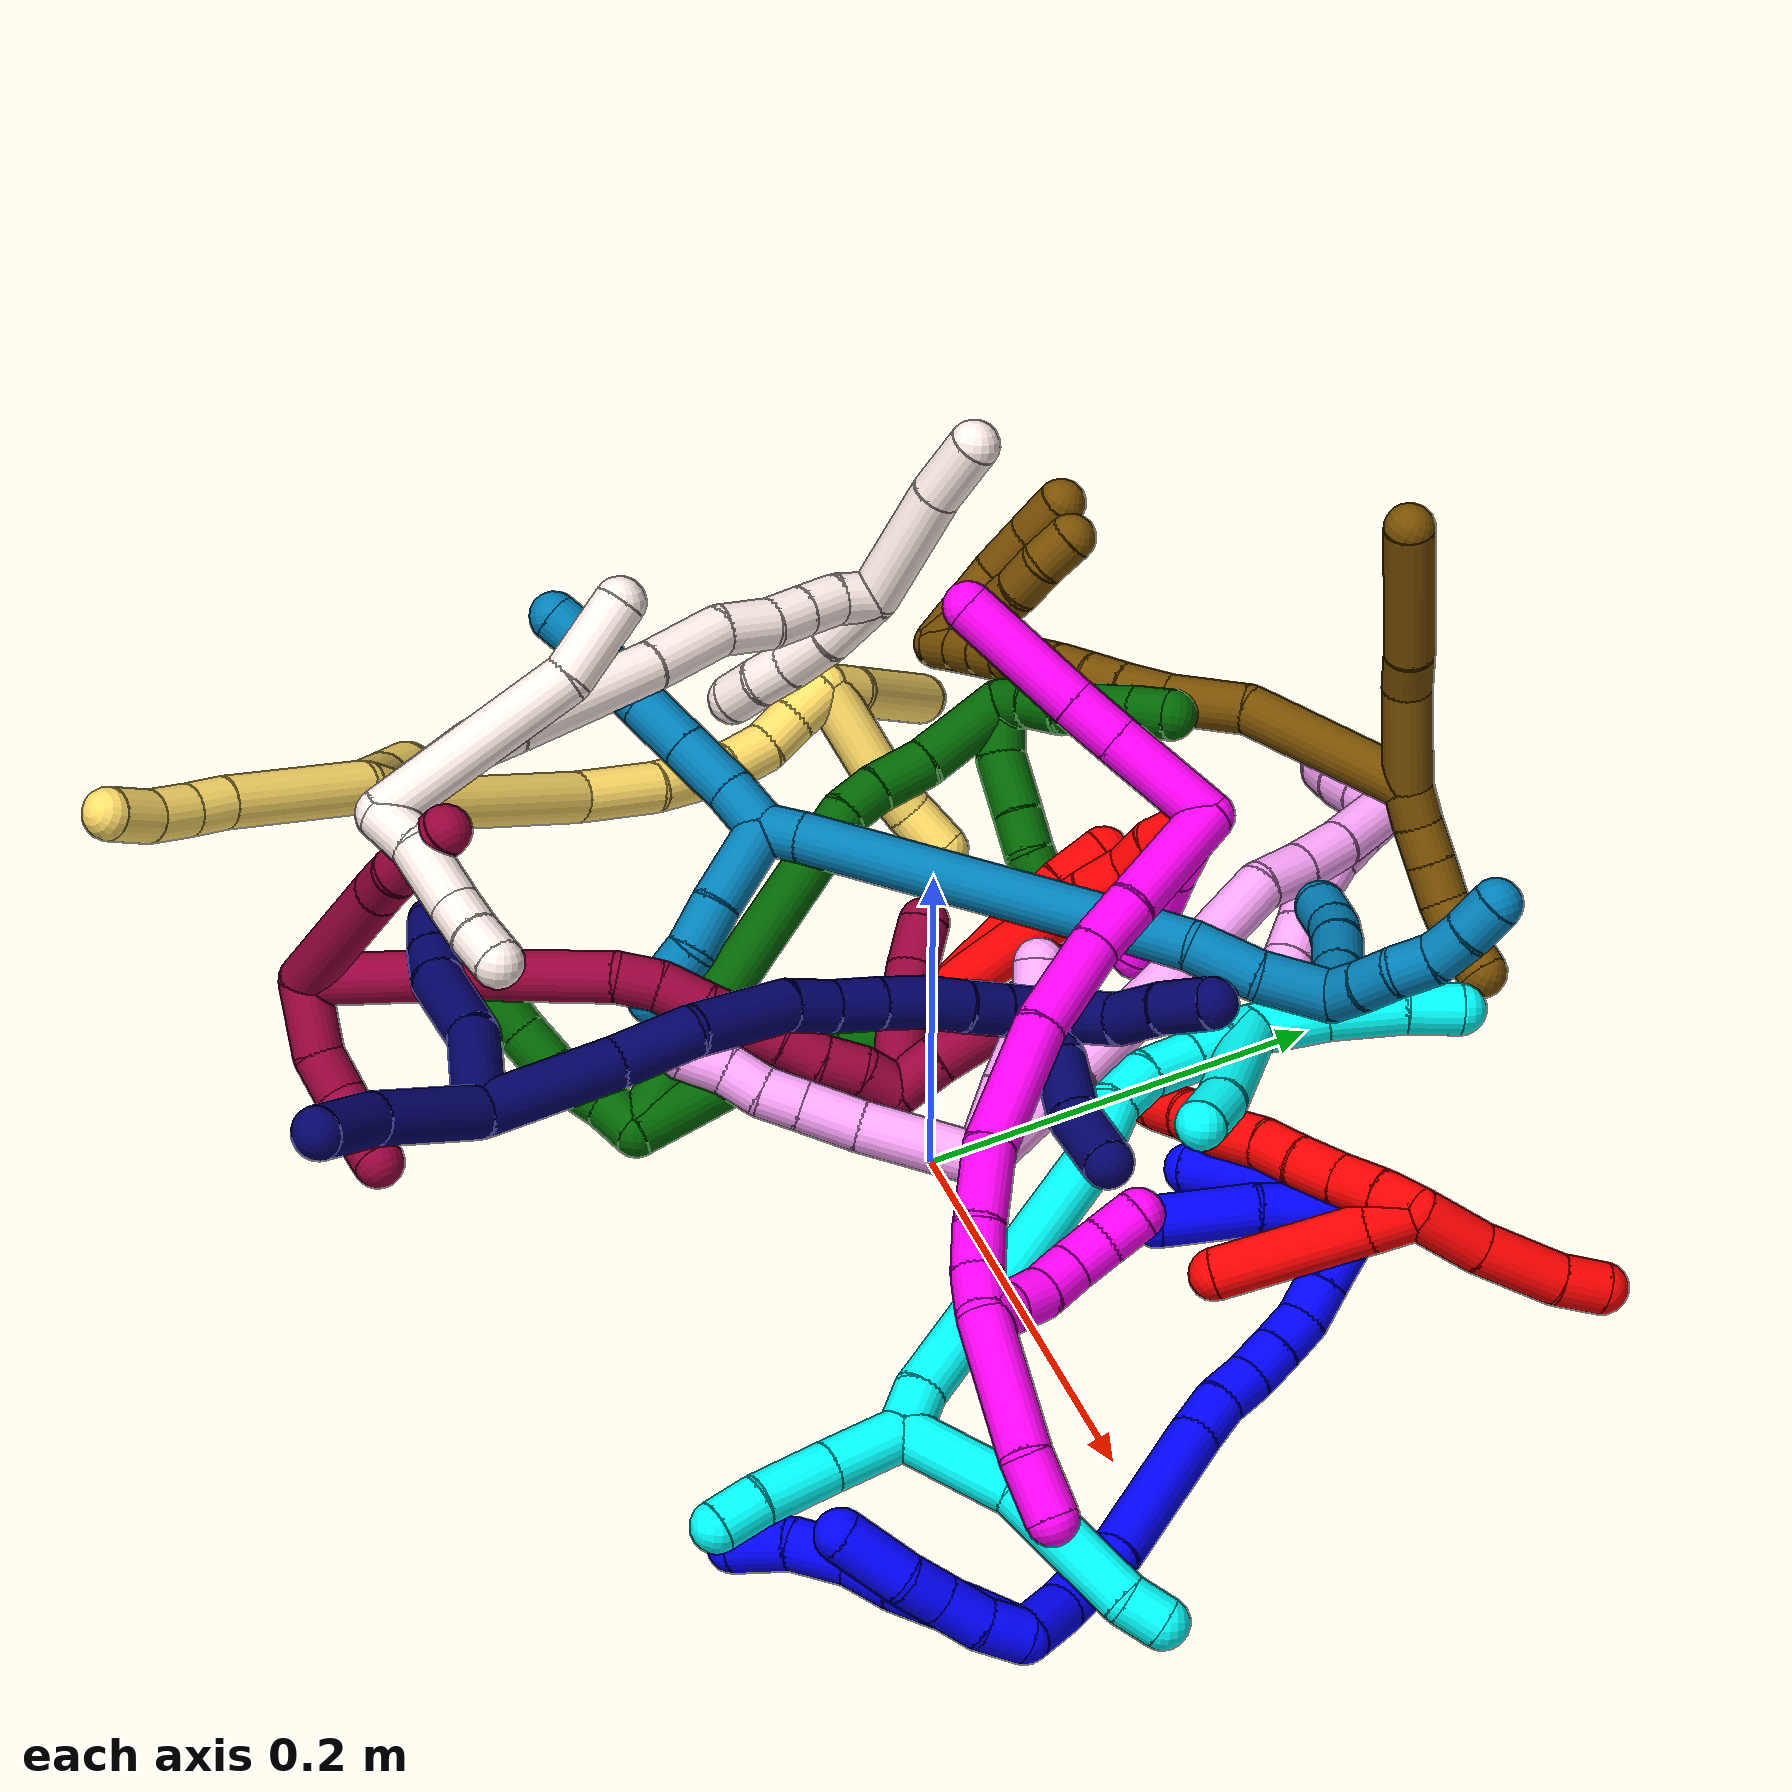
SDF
<sdf version="1.7">
 <world name="default">
  <plugin name="TubeGeneratorPlugin" filename="libtube_generator_plugin.so"/>
  <model name="photoneo_s_sensor">
   <static>1</static>
   <pose>0 0 2 1.57079 1.57079 3.14159</pose>
   <link name="link">
    <inertial><mass>0.1</mass></inertial>
    <sensor name="sensor" type="depth">
     <update_rate>30</update_rate>
     <camera>
      <horizontal_fov>1.22</horizontal_fov>
      <image><width>1920</width><height>1200</height><format>B8G8R8</format></image>
      <clip><near>0.1</near><far>4</far></clip>
      <depth_camera><output>points</output></depth_camera>
     </camera>
     <plugin name="camera_plugin" filename="libgazebo_ros_depth_camera.so">
      <baseline>0.2</baseline>
      <alwaysOn>1</alwaysOn>
      <updateRate>0.0</updateRate>
      <cameraName>camera_ir</cameraName>
      <imageTopicName>/camera/color/image_raw</imageTopicName>
      <cameraInfoTopicName>/camera/color/camera_info</cameraInfoTopicName>
      <depthImageTopicName>/camera/depth/image_raw</depthImageTopicName>
      <depthImageCameraInfoTopicName>/camera/depth/camera_info</depthImageCameraInfoTopicName>
      <pointCloudTopicName>/camera/depth/points</pointCloudTopicName>
      <frameName>fr_optical</frameName>
      <pointCloudCutoff>0.1</pointCloudCutoff>
      <pointCloudCutoffMax>2.0</pointCloudCutoffMax>
      <distortionK1>0</distortionK1>
      <distortionK2>0</distortionK2>
      <distortionK3>0</distortionK3>
      <distortionT1>0</distortionT1>
      <distortionT2>0</distortionT2>
      <CxPrime>0</CxPrime>
      <Cx>0</Cx>
      <Cy>0</Cy>
      <focalLength>0</focalLength>
      <hackBaseline>0</hackBaseline>
     </plugin>
    </sensor>
   </link>
  </model>
  <gravity>0 0 -9.8</gravity>
  <magnetic_field>6e-06 2.3e-05 -4.2e-05</magnetic_field>
  <atmosphere type="adiabatic"/>
  <physics name="default_physics" default="0" type="ode">
   <max_step_size>0.003</max_step_size>
   <real_time_factor>1</real_time_factor>
   <real_time_update_rate>1000</real_time_update_rate>
   <max_contacts>10000</max_contacts>
   <ode>
    <solver>
     <type>quick</type>
     <iters>100</iters>
     <sor>1.3</sor>
     <use_dynamic_moi_rescaling>0</use_dynamic_moi_rescaling>
    </solver>
    <constraints>
     <contact_max_correcting_vel>0</contact_max_correcting_vel>
     <contact_surface_layer>0.001</contact_surface_layer>
     <cfm>0</cfm>
     <erp>0.2</erp>
    </constraints>
   </ode>
  </physics>
  <scene><ambient>0.4 0.4 0.4 1</ambient><background>0.7 0.7 0.7 1</background><shadows>0</shadows></scene>
  <audio><device>default</device></audio>
  <spherical_coordinates>
   <surface_model>EARTH_WGS84</surface_model>
   <latitude_deg>0</latitude_deg>
   <longitude_deg>0</longitude_deg>
   <elevation>0</elevation>
   <heading_deg>0</heading_deg>
  </spherical_coordinates>
  <model name="bin">
   <static>1</static>
   <link name="bottom">
    <collision name="collision-bottom">
     <pose>0 0 -0.01 0 -0 0</pose>
     <geometry><box><size>0.8 0.6 0.02</size></box></geometry>
     <surface>
      <friction><ode><mu>100</mu><mu2>100</mu2></ode></friction>
      <contact><collide_bitmask>65535</collide_bitmask></contact>
     </surface>
    </collision>
   </link>
   <link name="west_wall">
    <collision name="collision-west_wall">
     <pose>-0.41 0 0.1 0 -0 0</pose>
     <geometry><box><size>0.02 0.6 0.2</size></box></geometry>
     <surface>
      <friction><ode><mu>100</mu><mu2>100</mu2></ode></friction>
      <contact><collide_bitmask>65535</collide_bitmask></contact>
     </surface>
    </collision>
   </link>
   <link name="east_wall">
    <collision name="collision-east_wall">
     <pose>0.41 0 0.1 0 -0 0</pose>
     <geometry><box><size>0.02 0.6 0.2</size></box></geometry>
     <surface>
      <friction><ode><mu>100</mu><mu2>100</mu2></ode></friction>
      <contact><collide_bitmask>65535</collide_bitmask></contact>
     </surface>
    </collision>
   </link>
   <link name="south_wall">
    <collision name="collision-south_wall">
     <pose>0 -0.31 0.1 0 -0 0</pose>
     <geometry><box><size>0.8 0.02 0.2</size></box></geometry>
     <surface>
      <friction><ode><mu>100</mu><mu2>100</mu2></ode></friction>
      <contact><collide_bitmask>65535</collide_bitmask></contact>
     </surface>
    </collision>
   </link>
   <link name="north_wall">
    <collision name="collision-north_wall">
     <pose>0 0.31 0.1 0 -0 0</pose>
     <geometry><box><size>0.8 0.02 0.2</size></box></geometry>
     <surface>
      <friction><ode><mu>100</mu><mu2>100</mu2></ode></friction>
      <contact><collide_bitmask>65535</collide_bitmask></contact>
     </surface>
    </collision>
   </link>
  </model>
  <model name="1">
   <static>0</static>
   <link name="1">
    <collision name="collision-cylinder-e_1_2_8">
     <pose>-0.008599 -0.011028 -0.005153 2.00796 -0.615013 -0.925629</pose>
     <geometry><cylinder><radius>0.0125</radius><length>0.029806</length></cylinder></geometry>
     <surface>
      <friction><ode><mu>1.16</mu><mu2>1.16</mu2><slip1>0</slip1><slip2>0</slip2></ode></friction>
      <contact><ode><kp>1e+06</kp><kd>1</kd><max_vel>0</max_vel><min_depth>0.001</min_depth></ode></contact>
     </surface>
    </collision>
    <visual name="visual-cylinder-e_1_2_8">
     <pose>-0.008599 -0.011028 -0.005153 2.00796 -0.615013 -0.925629</pose>
     <geometry><cylinder><radius>0.0125</radius><length>0.029806</length></cylinder></geometry>
     <material><ambient>0 0 1 1</ambient></material>
    </visual>
    <collision name="collision-cylinder-e_2_8_9">
     <pose>-0.027634 -0.036774 -0.01668 1.97941 -0.576877 -0.84871</pose>
     <geometry><cylinder><radius>0.0125</radius><length>0.038272</length></cylinder></geometry>
     <surface>
      <friction><ode><mu>1.16</mu><mu2>1.16</mu2><slip1>0</slip1><slip2>0</slip2></ode></friction>
      <contact><ode><kp>1e+06</kp><kd>1</kd><max_vel>0</max_vel><min_depth>0.001</min_depth></ode></contact>
     </surface>
    </collision>
    <visual name="visual-cylinder-e_2_8_9">
     <pose>-0.027634 -0.036774 -0.01668 1.97941 -0.576877 -0.84871</pose>
     <geometry><cylinder><radius>0.0125</radius><length>0.038272</length></cylinder></geometry>
     <material><ambient>0 0 1 1</ambient></material>
    </visual>
    <collision name="collision-cylinder-e_3_9_10">
     <pose>-0.046726 -0.059525 -0.025557 1.87296 -0.799512 -1.04255</pose>
     <geometry><cylinder><radius>0.0125</radius><length>0.02414</length></cylinder></geometry>
     <surface>
      <friction><ode><mu>1.16</mu><mu2>1.16</mu2><slip1>0</slip1><slip2>0</slip2></ode></friction>
      <contact><ode><kp>1e+06</kp><kd>1</kd><max_vel>0</max_vel><min_depth>0.001</min_depth></ode></contact>
     </surface>
    </collision>
    <visual name="visual-cylinder-e_3_9_10">
     <pose>-0.046726 -0.059525 -0.025557 1.87296 -0.799512 -1.04255</pose>
     <geometry><cylinder><radius>0.0125</radius><length>0.02414</length></cylinder></geometry>
     <material><ambient>0 0 1 1</ambient></material>
    </visual>
    <collision name="collision-cylinder-e_4_10_11">
     <pose>-0.063336 -0.079441 -0.029804 1.7165 -0.585017 -0.670789</pose>
     <geometry><cylinder><radius>0.0125</radius><length>0.028813</length></cylinder></geometry>
     <surface>
      <friction><ode><mu>1.16</mu><mu2>1.16</mu2><slip1>0</slip1><slip2>0</slip2></ode></friction>
      <contact><ode><kp>1e+06</kp><kd>1</kd><max_vel>0</max_vel><min_depth>0.001</min_depth></ode></contact>
     </surface>
    </collision>
    <visual name="visual-cylinder-e_4_10_11">
     <pose>-0.063336 -0.079441 -0.029804 1.7165 -0.585017 -0.670789</pose>
     <geometry><cylinder><radius>0.0125</radius><length>0.028813</length></cylinder></geometry>
     <material><ambient>0 0 1 1</ambient></material>
    </visual>
    <collision name="collision-cylinder-e_5_11_6">
     <pose>-0.075026 -0.105031 -0.034373 1.77403 -0.260808 -0.319126</pose>
     <geometry><cylinder><radius>0.0125</radius><length>0.028968</length></cylinder></geometry>
     <surface>
      <friction><ode><mu>1.16</mu><mu2>1.16</mu2><slip1>0</slip1><slip2>0</slip2></ode></friction>
      <contact><ode><kp>1e+06</kp><kd>1</kd><max_vel>0</max_vel><min_depth>0.001</min_depth></ode></contact>
     </surface>
    </collision>
    <visual name="visual-cylinder-e_5_11_6">
     <pose>-0.075026 -0.105031 -0.034373 1.77403 -0.260808 -0.319126</pose>
     <geometry><cylinder><radius>0.0125</radius><length>0.028968</length></cylinder></geometry>
     <material><ambient>0 0 1 1</ambient></material>
    </visual>
    <collision name="collision-cylinder-e_1_2_12">
     <pose>-0.007335 -0.006827 0.004933 0.945041 -0.716452 -0.378149</pose>
     <geometry><cylinder><radius>0.0125</radius><length>0.022338</length></cylinder></geometry>
     <surface>
      <friction><ode><mu>1.16</mu><mu2>1.16</mu2><slip1>0</slip1><slip2>0</slip2></ode></friction>
      <contact><ode><kp>1e+06</kp><kd>1</kd><max_vel>0</max_vel><min_depth>0.001</min_depth></ode></contact>
     </surface>
    </collision>
    <visual name="visual-cylinder-e_1_2_12">
     <pose>-0.007335 -0.006827 0.004933 0.945041 -0.716452 -0.378149</pose>
     <geometry><cylinder><radius>0.0125</radius><length>0.022338</length></cylinder></geometry>
     <material><ambient>0 0 1 1</ambient></material>
    </visual>
    <collision name="collision-cylinder-e_2_12_13">
     <pose>-0.024064 -0.019197 0.01398 0.932449 -0.937142 -0.498827</pose>
     <geometry><cylinder><radius>0.0125</radius><length>0.023315</length></cylinder></geometry>
     <surface>
      <friction><ode><mu>1.16</mu><mu2>1.16</mu2><slip1>0</slip1><slip2>0</slip2></ode></friction>
      <contact><ode><kp>1e+06</kp><kd>1</kd><max_vel>0</max_vel><min_depth>0.001</min_depth></ode></contact>
     </surface>
    </collision>
    <visual name="visual-cylinder-e_2_12_13">
     <pose>-0.024064 -0.019197 0.01398 0.932449 -0.937142 -0.498827</pose>
     <geometry><cylinder><radius>0.0125</radius><length>0.023315</length></cylinder></geometry>
     <material><ambient>0 0 1 1</ambient></material>
    </visual>
    <collision name="collision-cylinder-e_3_13_14">
     <pose>-0.041321 -0.029213 0.022423 0.801542 -0.901083 -0.40431</pose>
     <geometry><cylinder><radius>0.0125</radius><length>0.020057</length></cylinder></geometry>
     <surface>
      <friction><ode><mu>1.16</mu><mu2>1.16</mu2><slip1>0</slip1><slip2>0</slip2></ode></friction>
      <contact><ode><kp>1e+06</kp><kd>1</kd><max_vel>0</max_vel><min_depth>0.001</min_depth></ode></contact>
     </surface>
    </collision>
    <visual name="visual-cylinder-e_3_13_14">
     <pose>-0.041321 -0.029213 0.022423 0.801542 -0.901083 -0.40431</pose>
     <geometry><cylinder><radius>0.0125</radius><length>0.020057</length></cylinder></geometry>
     <material><ambient>0 0 1 1</ambient></material>
    </visual>
    <collision name="collision-cylinder-e_4_14_5">
     <pose>-0.063803 -0.041842 0.030451 1.14518 -1.02116 -0.693003</pose>
     <geometry><cylinder><radius>0.0125</radius><length>0.03429</length></cylinder></geometry>
     <surface>
      <friction><ode><mu>1.16</mu><mu2>1.16</mu2><slip1>0</slip1><slip2>0</slip2></ode></friction>
      <contact><ode><kp>1e+06</kp><kd>1</kd><max_vel>0</max_vel><min_depth>0.001</min_depth></ode></contact>
     </surface>
    </collision>
    <visual name="visual-cylinder-e_4_14_5">
     <pose>-0.063803 -0.041842 0.030451 1.14518 -1.02116 -0.693003</pose>
     <geometry><cylinder><radius>0.0125</radius><length>0.03429</length></cylinder></geometry>
     <material><ambient>0 0 1 1</ambient></material>
    </visual>
    <collision name="collision-cylinder-e_1_2_15">
     <pose>-0.000356 0.006197 -0.014425 -2.73582 -0.022688 0.110177</pose>
     <geometry><cylinder><radius>0.0125</radius><length>0.031408</length></cylinder></geometry>
     <surface>
      <friction><ode><mu>1.16</mu><mu2>1.16</mu2><slip1>0</slip1><slip2>0</slip2></ode></friction>
      <contact><ode><kp>1e+06</kp><kd>1</kd><max_vel>0</max_vel><min_depth>0.001</min_depth></ode></contact>
     </surface>
    </collision>
    <visual name="visual-cylinder-e_1_2_15">
     <pose>-0.000356 0.006197 -0.014425 -2.73582 -0.022688 0.110177</pose>
     <geometry><cylinder><radius>0.0125</radius><length>0.031408</length></cylinder></geometry>
     <material><ambient>0 0 1 1</ambient></material>
    </visual>
    <collision name="collision-cylinder-e_2_15_16">
     <pose>-0.004538 0.024896 -0.046279 -2.51937 -0.176484 0.536989</pose>
     <geometry><cylinder><radius>0.0125</radius><length>0.043573</length></cylinder></geometry>
     <surface>
      <friction><ode><mu>1.16</mu><mu2>1.16</mu2><slip1>0</slip1><slip2>0</slip2></ode></friction>
      <contact><ode><kp>1e+06</kp><kd>1</kd><max_vel>0</max_vel><min_depth>0.001</min_depth></ode></contact>
     </surface>
    </collision>
    <visual name="visual-cylinder-e_2_15_16">
     <pose>-0.004538 0.024896 -0.046279 -2.51937 -0.176484 0.536989</pose>
     <geometry><cylinder><radius>0.0125</radius><length>0.043573</length></cylinder></geometry>
     <material><ambient>0 0 1 1</ambient></material>
    </visual>
    <collision name="collision-cylinder-e_3_16_17">
     <pose>-0.021243 0.057374 -0.096531 -2.59486 -0.323433 1.05393</pose>
     <geometry><cylinder><radius>0.0125</radius><length>0.081052</length></cylinder></geometry>
     <surface>
      <friction><ode><mu>1.16</mu><mu2>1.16</mu2><slip1>0</slip1><slip2>0</slip2></ode></friction>
      <contact><ode><kp>1e+06</kp><kd>1</kd><max_vel>0</max_vel><min_depth>0.001</min_depth></ode></contact>
     </surface>
    </collision>
    <visual name="visual-cylinder-e_3_16_17">
     <pose>-0.021243 0.057374 -0.096531 -2.59486 -0.323433 1.05393</pose>
     <geometry><cylinder><radius>0.0125</radius><length>0.081052</length></cylinder></geometry>
     <material><ambient>0 0 1 1</ambient></material>
    </visual>
    <collision name="collision-cylinder-e_4_17_18">
     <pose>-0.038031 0.084178 -0.138159 -2.48198 -0.33733 0.923219</pose>
     <geometry><cylinder><radius>0.0125</radius><length>0.023614</length></cylinder></geometry>
     <surface>
      <friction><ode><mu>1.16</mu><mu2>1.16</mu2><slip1>0</slip1><slip2>0</slip2></ode></friction>
      <contact><ode><kp>1e+06</kp><kd>1</kd><max_vel>0</max_vel><min_depth>0.001</min_depth></ode></contact>
     </surface>
    </collision>
    <visual name="visual-cylinder-e_4_17_18">
     <pose>-0.038031 0.084178 -0.138159 -2.48198 -0.33733 0.923219</pose>
     <geometry><cylinder><radius>0.0125</radius><length>0.023614</length></cylinder></geometry>
     <material><ambient>0 0 1 1</ambient></material>
    </visual>
    <collision name="collision-cylinder-e_5_18_19">
     <pose>-0.043686 0.098166 -0.153951 -2.34403 -0.172906 0.405722</pose>
     <geometry><cylinder><radius>0.0125</radius><length>0.020312</length></cylinder></geometry>
     <surface>
      <friction><ode><mu>1.16</mu><mu2>1.16</mu2><slip1>0</slip1><slip2>0</slip2></ode></friction>
      <contact><ode><kp>1e+06</kp><kd>1</kd><max_vel>0</max_vel><min_depth>0.001</min_depth></ode></contact>
     </surface>
    </collision>
    <visual name="visual-cylinder-e_5_18_19">
     <pose>-0.043686 0.098166 -0.153951 -2.34403 -0.172906 0.405722</pose>
     <geometry><cylinder><radius>0.0125</radius><length>0.020312</length></cylinder></geometry>
     <material><ambient>0 0 1 1</ambient></material>
    </visual>
    <collision name="collision-cylinder-e_6_19_20">
     <pose>-0.048337 0.112512 -0.167261 -2.29233 -0.294612 0.634204</pose>
     <geometry><cylinder><radius>0.0125</radius><length>0.020005</length></cylinder></geometry>
     <surface>
      <friction><ode><mu>1.16</mu><mu2>1.16</mu2><slip1>0</slip1><slip2>0</slip2></ode></friction>
      <contact><ode><kp>1e+06</kp><kd>1</kd><max_vel>0</max_vel><min_depth>0.001</min_depth></ode></contact>
     </surface>
    </collision>
    <visual name="visual-cylinder-e_6_19_20">
     <pose>-0.048337 0.112512 -0.167261 -2.29233 -0.294612 0.634204</pose>
     <geometry><cylinder><radius>0.0125</radius><length>0.020005</length></cylinder></geometry>
     <material><ambient>0 0 1 1</ambient></material>
    </visual>
    <collision name="collision-cylinder-e_7_20_21">
     <pose>-0.054317 0.126665 -0.180085 -2.3216 -0.312204 0.694847</pose>
     <geometry><cylinder><radius>0.0125</radius><length>0.020026</length></cylinder></geometry>
     <surface>
      <friction><ode><mu>1.16</mu><mu2>1.16</mu2><slip1>0</slip1><slip2>0</slip2></ode></friction>
      <contact><ode><kp>1e+06</kp><kd>1</kd><max_vel>0</max_vel><min_depth>0.001</min_depth></ode></contact>
     </surface>
    </collision>
    <visual name="visual-cylinder-e_7_20_21">
     <pose>-0.054317 0.126665 -0.180085 -2.3216 -0.312204 0.694847</pose>
     <geometry><cylinder><radius>0.0125</radius><length>0.020026</length></cylinder></geometry>
     <material><ambient>0 0 1 1</ambient></material>
    </visual>
    <collision name="collision-cylinder-e_8_21_22">
     <pose>-0.063023 0.140436 -0.191278 -2.17458 -0.598036 1.06173</pose>
     <geometry><cylinder><radius>0.0125</radius><length>0.020001</length></cylinder></geometry>
     <surface>
      <friction><ode><mu>1.16</mu><mu2>1.16</mu2><slip1>0</slip1><slip2>0</slip2></ode></friction>
      <contact><ode><kp>1e+06</kp><kd>1</kd><max_vel>0</max_vel><min_depth>0.001</min_depth></ode></contact>
     </surface>
    </collision>
    <visual name="visual-cylinder-e_8_21_22">
     <pose>-0.063023 0.140436 -0.191278 -2.17458 -0.598036 1.06173</pose>
     <geometry><cylinder><radius>0.0125</radius><length>0.020001</length></cylinder></geometry>
     <material><ambient>0 0 1 1</ambient></material>
    </visual>
    <collision name="collision-cylinder-e_9_22_23">
     <pose>-0.074117 0.154142 -0.200719 -2.17339 -0.577797 1.02891</pose>
     <geometry><cylinder><radius>0.0125</radius><length>0.020004</length></cylinder></geometry>
     <surface>
      <friction><ode><mu>1.16</mu><mu2>1.16</mu2><slip1>0</slip1><slip2>0</slip2></ode></friction>
      <contact><ode><kp>1e+06</kp><kd>1</kd><max_vel>0</max_vel><min_depth>0.001</min_depth></ode></contact>
     </surface>
    </collision>
    <visual name="visual-cylinder-e_9_22_23">
     <pose>-0.074117 0.154142 -0.200719 -2.17339 -0.577797 1.02891</pose>
     <geometry><cylinder><radius>0.0125</radius><length>0.020004</length></cylinder></geometry>
     <material><ambient>0 0 1 1</ambient></material>
    </visual>
    <collision name="collision-cylinder-e_10_23_1">
     <pose>-0.085066 0.168574 -0.209108 -2.02111 -0.580645 0.888983</pose>
     <geometry><cylinder><radius>0.0125</radius><length>0.020004</length></cylinder></geometry>
     <surface>
      <friction><ode><mu>1.16</mu><mu2>1.16</mu2><slip1>0</slip1><slip2>0</slip2></ode></friction>
      <contact><ode><kp>1e+06</kp><kd>1</kd><max_vel>0</max_vel><min_depth>0.001</min_depth></ode></contact>
     </surface>
    </collision>
    <visual name="visual-cylinder-e_10_23_1">
     <pose>-0.085066 0.168574 -0.209108 -2.02111 -0.580645 0.888983</pose>
     <geometry><cylinder><radius>0.0125</radius><length>0.020004</length></cylinder></geometry>
     <material><ambient>0 0 1 1</ambient></material>
    </visual>
    <collision name="collision-cylinder-e_1_1_24">
     <pose>-0.099882 0.163033 -0.22185 2.1791 -0.529846 -0.958308</pose>
     <geometry><cylinder><radius>0.0125</radius><length>0.036916</length></cylinder></geometry>
     <surface>
      <friction><ode><mu>1.16</mu><mu2>1.16</mu2><slip1>0</slip1><slip2>0</slip2></ode></friction>
      <contact><ode><kp>1e+06</kp><kd>1</kd><max_vel>0</max_vel><min_depth>0.001</min_depth></ode></contact>
     </surface>
    </collision>
    <visual name="visual-cylinder-e_1_1_24">
     <pose>-0.099882 0.163033 -0.22185 2.1791 -0.529846 -0.958308</pose>
     <geometry><cylinder><radius>0.0125</radius><length>0.036916</length></cylinder></geometry>
     <material><ambient>0 0 1 1</ambient></material>
    </visual>
    <collision name="collision-cylinder-e_2_24_4">
     <pose>-0.121094 0.123733 -0.243824 2.02702 -0.386294 -0.608231</pose>
     <geometry><cylinder><radius>0.0125</radius><length>0.063084</length></cylinder></geometry>
     <surface>
      <friction><ode><mu>1.16</mu><mu2>1.16</mu2><slip1>0</slip1><slip2>0</slip2></ode></friction>
      <contact><ode><kp>1e+06</kp><kd>1</kd><max_vel>0</max_vel><min_depth>0.001</min_depth></ode></contact>
     </surface>
    </collision>
    <visual name="visual-cylinder-e_2_24_4">
     <pose>-0.121094 0.123733 -0.243824 2.02702 -0.386294 -0.608231</pose>
     <geometry><cylinder><radius>0.0125</radius><length>0.063084</length></cylinder></geometry>
     <material><ambient>0 0 1 1</ambient></material>
    </visual>
    <collision name="collision-cylinder-e_1_1_25">
     <pose>-0.101947 0.154649 -0.20224 1.11535 -0.445052 -0.280407</pose>
     <geometry><cylinder><radius>0.0125</radius><length>0.052934</length></cylinder></geometry>
     <surface>
      <friction><ode><mu>1.16</mu><mu2>1.16</mu2><slip1>0</slip1><slip2>0</slip2></ode></friction>
      <contact><ode><kp>1e+06</kp><kd>1</kd><max_vel>0</max_vel><min_depth>0.001</min_depth></ode></contact>
     </surface>
    </collision>
    <visual name="visual-cylinder-e_1_1_25">
     <pose>-0.101947 0.154649 -0.20224 1.11535 -0.445052 -0.280407</pose>
     <geometry><cylinder><radius>0.0125</radius><length>0.052934</length></cylinder></geometry>
     <material><ambient>0 0 1 1</ambient></material>
    </visual>
    <collision name="collision-cylinder-e_2_25_3">
     <pose>-0.120201 0.111941 -0.184314 1.235 -0.295783 -0.210808</pose>
     <geometry><cylinder><radius>0.0125</radius><length>0.047066</length></cylinder></geometry>
     <surface>
      <friction><ode><mu>1.16</mu><mu2>1.16</mu2><slip1>0</slip1><slip2>0</slip2></ode></friction>
      <contact><ode><kp>1e+06</kp><kd>1</kd><max_vel>0</max_vel><min_depth>0.001</min_depth></ode></contact>
     </surface>
    </collision>
    <visual name="visual-cylinder-e_2_25_3">
     <pose>-0.120201 0.111941 -0.184314 1.235 -0.295783 -0.210808</pose>
     <geometry><cylinder><radius>0.0125</radius><length>0.047066</length></cylinder></geometry>
     <material><ambient>0 0 1 1</ambient></material>
    </visual>
    <collision name="collision-sphere-3">
     <pose>-0.127061 0.090688 -0.176896 0 -0 0</pose>
     <geometry><sphere><radius>0.0125</radius></sphere></geometry>
     <surface>
      <friction><ode><mu>1.16</mu><mu2>1.16</mu2><slip1>0</slip1><slip2>0</slip2></ode></friction>
      <contact><ode><kp>1e+06</kp><kd>1</kd><max_vel>0</max_vel><min_depth>0.001</min_depth></ode></contact>
     </surface>
    </collision>
    <visual name="visual-sphere-3">
     <pose>-0.127061 0.090688 -0.176896 0 -0 0</pose>
     <geometry><sphere><radius>0.0125</radius></sphere></geometry>
     <material><ambient>0 0 1 1</ambient></material>
    </visual>
    <collision name="collision-sphere-25">
     <pose>-0.113342 0.133195 -0.191732 0 -0 0</pose>
     <geometry><sphere><radius>0.0125</radius></sphere></geometry>
     <surface>
      <friction><ode><mu>1.16</mu><mu2>1.16</mu2><slip1>0</slip1><slip2>0</slip2></ode></friction>
      <contact><ode><kp>1e+06</kp><kd>1</kd><max_vel>0</max_vel><min_depth>0.001</min_depth></ode></contact>
     </surface>
    </collision>
    <visual name="visual-sphere-25">
     <pose>-0.113342 0.133195 -0.191732 0 -0 0</pose>
     <geometry><sphere><radius>0.0125</radius></sphere></geometry>
     <material><ambient>0 0 1 1</ambient></material>
    </visual>
    <collision name="collision-sphere-4">
     <pose>-0.132978 0.097504 -0.256696 0 -0 0</pose>
     <geometry><sphere><radius>0.0125</radius></sphere></geometry>
     <surface>
      <friction><ode><mu>1.16</mu><mu2>1.16</mu2><slip1>0</slip1><slip2>0</slip2></ode></friction>
      <contact><ode><kp>1e+06</kp><kd>1</kd><max_vel>0</max_vel><min_depth>0.001</min_depth></ode></contact>
     </surface>
    </collision>
    <visual name="visual-sphere-4">
     <pose>-0.132978 0.097504 -0.256696 0 -0 0</pose>
     <geometry><sphere><radius>0.0125</radius></sphere></geometry>
     <material><ambient>0 0 1 1</ambient></material>
    </visual>
    <collision name="collision-sphere-24">
     <pose>-0.109211 0.149962 -0.230952 0 -0 0</pose>
     <geometry><sphere><radius>0.0125</radius></sphere></geometry>
     <surface>
      <friction><ode><mu>1.16</mu><mu2>1.16</mu2><slip1>0</slip1><slip2>0</slip2></ode></friction>
      <contact><ode><kp>1e+06</kp><kd>1</kd><max_vel>0</max_vel><min_depth>0.001</min_depth></ode></contact>
     </surface>
    </collision>
    <visual name="visual-sphere-24">
     <pose>-0.109211 0.149962 -0.230952 0 -0 0</pose>
     <geometry><sphere><radius>0.0125</radius></sphere></geometry>
     <material><ambient>0 0 1 1</ambient></material>
    </visual>
    <collision name="collision-sphere-1">
     <pose>-0.090553 0.176103 -0.212748 0 -0 0</pose>
     <geometry><sphere><radius>0.0125</radius></sphere></geometry>
     <surface>
      <friction><ode><mu>1.16</mu><mu2>1.16</mu2><slip1>0</slip1><slip2>0</slip2></ode></friction>
      <contact><ode><kp>1e+06</kp><kd>1</kd><max_vel>0</max_vel><min_depth>0.001</min_depth></ode></contact>
     </surface>
    </collision>
    <visual name="visual-sphere-1">
     <pose>-0.090553 0.176103 -0.212748 0 -0 0</pose>
     <geometry><sphere><radius>0.0125</radius></sphere></geometry>
     <material><ambient>0 0 1 1</ambient></material>
    </visual>
    <collision name="collision-sphere-23">
     <pose>-0.07958 0.161044 -0.205468 0 -0 0</pose>
     <geometry><sphere><radius>0.0125</radius></sphere></geometry>
     <surface>
      <friction><ode><mu>1.16</mu><mu2>1.16</mu2><slip1>0</slip1><slip2>0</slip2></ode></friction>
      <contact><ode><kp>1e+06</kp><kd>1</kd><max_vel>0</max_vel><min_depth>0.001</min_depth></ode></contact>
     </surface>
    </collision>
    <visual name="visual-sphere-23">
     <pose>-0.07958 0.161044 -0.205468 0 -0 0</pose>
     <geometry><sphere><radius>0.0125</radius></sphere></geometry>
     <material><ambient>0 0 1 1</ambient></material>
    </visual>
    <collision name="collision-sphere-22">
     <pose>-0.068654 0.147239 -0.195971 0 -0 0</pose>
     <geometry><sphere><radius>0.0125</radius></sphere></geometry>
     <surface>
      <friction><ode><mu>1.16</mu><mu2>1.16</mu2><slip1>0</slip1><slip2>0</slip2></ode></friction>
      <contact><ode><kp>1e+06</kp><kd>1</kd><max_vel>0</max_vel><min_depth>0.001</min_depth></ode></contact>
     </surface>
    </collision>
    <visual name="visual-sphere-22">
     <pose>-0.068654 0.147239 -0.195971 0 -0 0</pose>
     <geometry><sphere><radius>0.0125</radius></sphere></geometry>
     <material><ambient>0 0 1 1</ambient></material>
    </visual>
    <collision name="collision-sphere-21">
     <pose>-0.057393 0.133632 -0.186586 0 -0 0</pose>
     <geometry><sphere><radius>0.0125</radius></sphere></geometry>
     <surface>
      <friction><ode><mu>1.16</mu><mu2>1.16</mu2><slip1>0</slip1><slip2>0</slip2></ode></friction>
      <contact><ode><kp>1e+06</kp><kd>1</kd><max_vel>0</max_vel><min_depth>0.001</min_depth></ode></contact>
     </surface>
    </collision>
    <visual name="visual-sphere-21">
     <pose>-0.057393 0.133632 -0.186586 0 -0 0</pose>
     <geometry><sphere><radius>0.0125</radius></sphere></geometry>
     <material><ambient>0 0 1 1</ambient></material>
    </visual>
    <collision name="collision-sphere-6">
     <pose>-0.078761 -0.118737 -0.037197 0 -0 0</pose>
     <geometry><sphere><radius>0.0125</radius></sphere></geometry>
     <surface>
      <friction><ode><mu>1.16</mu><mu2>1.16</mu2><slip1>0</slip1><slip2>0</slip2></ode></friction>
      <contact><ode><kp>1e+06</kp><kd>1</kd><max_vel>0</max_vel><min_depth>0.001</min_depth></ode></contact>
     </surface>
    </collision>
    <visual name="visual-sphere-6">
     <pose>-0.078761 -0.118737 -0.037197 0 -0 0</pose>
     <geometry><sphere><radius>0.0125</radius></sphere></geometry>
     <material><ambient>0 0 1 1</ambient></material>
    </visual>
    <collision name="collision-sphere-11">
     <pose>-0.071291 -0.091325 -0.031548 0 -0 0</pose>
     <geometry><sphere><radius>0.0125</radius></sphere></geometry>
     <surface>
      <friction><ode><mu>1.16</mu><mu2>1.16</mu2><slip1>0</slip1><slip2>0</slip2></ode></friction>
      <contact><ode><kp>1e+06</kp><kd>1</kd><max_vel>0</max_vel><min_depth>0.001</min_depth></ode></contact>
     </surface>
    </collision>
    <visual name="visual-sphere-11">
     <pose>-0.071291 -0.091325 -0.031548 0 -0 0</pose>
     <geometry><sphere><radius>0.0125</radius></sphere></geometry>
     <material><ambient>0 0 1 1</ambient></material>
    </visual>
    <collision name="collision-sphere-10">
     <pose>-0.05538 -0.067558 -0.028061 0 -0 0</pose>
     <geometry><sphere><radius>0.0125</radius></sphere></geometry>
     <surface>
      <friction><ode><mu>1.16</mu><mu2>1.16</mu2><slip1>0</slip1><slip2>0</slip2></ode></friction>
      <contact><ode><kp>1e+06</kp><kd>1</kd><max_vel>0</max_vel><min_depth>0.001</min_depth></ode></contact>
     </surface>
    </collision>
    <visual name="visual-sphere-10">
     <pose>-0.05538 -0.067558 -0.028061 0 -0 0</pose>
     <geometry><sphere><radius>0.0125</radius></sphere></geometry>
     <material><ambient>0 0 1 1</ambient></material>
    </visual>
    <collision name="collision-sphere-9">
     <pose>-0.038071 -0.051493 -0.023053 0 -0 0</pose>
     <geometry><sphere><radius>0.0125</radius></sphere></geometry>
     <surface>
      <friction><ode><mu>1.16</mu><mu2>1.16</mu2><slip1>0</slip1><slip2>0</slip2></ode></friction>
      <contact><ode><kp>1e+06</kp><kd>1</kd><max_vel>0</max_vel><min_depth>0.001</min_depth></ode></contact>
     </surface>
    </collision>
    <visual name="visual-sphere-9">
     <pose>-0.038071 -0.051493 -0.023053 0 -0 0</pose>
     <geometry><sphere><radius>0.0125</radius></sphere></geometry>
     <material><ambient>0 0 1 1</ambient></material>
    </visual>
    <collision name="collision-sphere-2">
     <geometry><sphere><radius>0.0125</radius></sphere></geometry>
     <surface>
      <friction><ode><mu>1.16</mu><mu2>1.16</mu2><slip1>0</slip1><slip2>0</slip2></ode></friction>
      <contact><ode><kp>1e+06</kp><kd>1</kd><max_vel>0</max_vel><min_depth>0.001</min_depth></ode></contact>
     </surface>
    </collision>
    <visual name="visual-sphere-2">
     <geometry><sphere><radius>0.0125</radius></sphere></geometry>
     <material><ambient>0 0 1 1</ambient></material>
    </visual>
    <collision name="collision-sphere-19">
     <pose>-0.045433 0.105326 -0.160939 0 -0 0</pose>
     <geometry><sphere><radius>0.0125</radius></sphere></geometry>
     <surface>
      <friction><ode><mu>1.16</mu><mu2>1.16</mu2><slip1>0</slip1><slip2>0</slip2></ode></friction>
      <contact><ode><kp>1e+06</kp><kd>1</kd><max_vel>0</max_vel><min_depth>0.001</min_depth></ode></contact>
     </surface>
    </collision>
    <visual name="visual-sphere-19">
     <pose>-0.045433 0.105326 -0.160939 0 -0 0</pose>
     <geometry><sphere><radius>0.0125</radius></sphere></geometry>
     <material><ambient>0 0 1 1</ambient></material>
    </visual>
    <collision name="collision-sphere-8">
     <pose>-0.017197 -0.022055 -0.010307 0 -0 0</pose>
     <geometry><sphere><radius>0.0125</radius></sphere></geometry>
     <surface>
      <friction><ode><mu>1.16</mu><mu2>1.16</mu2><slip1>0</slip1><slip2>0</slip2></ode></friction>
      <contact><ode><kp>1e+06</kp><kd>1</kd><max_vel>0</max_vel><min_depth>0.001</min_depth></ode></contact>
     </surface>
    </collision>
    <visual name="visual-sphere-8">
     <pose>-0.017197 -0.022055 -0.010307 0 -0 0</pose>
     <geometry><sphere><radius>0.0125</radius></sphere></geometry>
     <material><ambient>0 0 1 1</ambient></material>
    </visual>
    <collision name="collision-sphere-12">
     <pose>-0.01467 -0.013654 0.009867 0 -0 0</pose>
     <geometry><sphere><radius>0.0125</radius></sphere></geometry>
     <surface>
      <friction><ode><mu>1.16</mu><mu2>1.16</mu2><slip1>0</slip1><slip2>0</slip2></ode></friction>
      <contact><ode><kp>1e+06</kp><kd>1</kd><max_vel>0</max_vel><min_depth>0.001</min_depth></ode></contact>
     </surface>
    </collision>
    <visual name="visual-sphere-12">
     <pose>-0.01467 -0.013654 0.009867 0 -0 0</pose>
     <geometry><sphere><radius>0.0125</radius></sphere></geometry>
     <material><ambient>0 0 1 1</ambient></material>
    </visual>
    <collision name="collision-sphere-13">
     <pose>-0.033459 -0.02474 0.018093 0 -0 0</pose>
     <geometry><sphere><radius>0.0125</radius></sphere></geometry>
     <surface>
      <friction><ode><mu>1.16</mu><mu2>1.16</mu2><slip1>0</slip1><slip2>0</slip2></ode></friction>
      <contact><ode><kp>1e+06</kp><kd>1</kd><max_vel>0</max_vel><min_depth>0.001</min_depth></ode></contact>
     </surface>
    </collision>
    <visual name="visual-sphere-13">
     <pose>-0.033459 -0.02474 0.018093 0 -0 0</pose>
     <geometry><sphere><radius>0.0125</radius></sphere></geometry>
     <material><ambient>0 0 1 1</ambient></material>
    </visual>
    <collision name="collision-sphere-14">
     <pose>-0.049183 -0.033685 0.026753 0 -0 0</pose>
     <geometry><sphere><radius>0.0125</radius></sphere></geometry>
     <surface>
      <friction><ode><mu>1.16</mu><mu2>1.16</mu2><slip1>0</slip1><slip2>0</slip2></ode></friction>
      <contact><ode><kp>1e+06</kp><kd>1</kd><max_vel>0</max_vel><min_depth>0.001</min_depth></ode></contact>
     </surface>
    </collision>
    <visual name="visual-sphere-14">
     <pose>-0.049183 -0.033685 0.026753 0 -0 0</pose>
     <geometry><sphere><radius>0.0125</radius></sphere></geometry>
     <material><ambient>0 0 1 1</ambient></material>
    </visual>
    <collision name="collision-sphere-5">
     <pose>-0.078423 -0.049999 0.034149 0 -0 0</pose>
     <geometry><sphere><radius>0.0125</radius></sphere></geometry>
     <surface>
      <friction><ode><mu>1.16</mu><mu2>1.16</mu2><slip1>0</slip1><slip2>0</slip2></ode></friction>
      <contact><ode><kp>1e+06</kp><kd>1</kd><max_vel>0</max_vel><min_depth>0.001</min_depth></ode></contact>
     </surface>
    </collision>
    <visual name="visual-sphere-5">
     <pose>-0.078423 -0.049999 0.034149 0 -0 0</pose>
     <geometry><sphere><radius>0.0125</radius></sphere></geometry>
     <material><ambient>0 0 1 1</ambient></material>
    </visual>
    <collision name="collision-sphere-15">
     <pose>-0.000713 0.012395 -0.02885 0 -0 0</pose>
     <geometry><sphere><radius>0.0125</radius></sphere></geometry>
     <surface>
      <friction><ode><mu>1.16</mu><mu2>1.16</mu2><slip1>0</slip1><slip2>0</slip2></ode></friction>
      <contact><ode><kp>1e+06</kp><kd>1</kd><max_vel>0</max_vel><min_depth>0.001</min_depth></ode></contact>
     </surface>
    </collision>
    <visual name="visual-sphere-15">
     <pose>-0.000713 0.012395 -0.02885 0 -0 0</pose>
     <geometry><sphere><radius>0.0125</radius></sphere></geometry>
     <material><ambient>0 0 1 1</ambient></material>
    </visual>
    <collision name="collision-sphere-16">
     <pose>-0.008363 0.037397 -0.063707 0 -0 0</pose>
     <geometry><sphere><radius>0.0125</radius></sphere></geometry>
     <surface>
      <friction><ode><mu>1.16</mu><mu2>1.16</mu2><slip1>0</slip1><slip2>0</slip2></ode></friction>
      <contact><ode><kp>1e+06</kp><kd>1</kd><max_vel>0</max_vel><min_depth>0.001</min_depth></ode></contact>
     </surface>
    </collision>
    <visual name="visual-sphere-16">
     <pose>-0.008363 0.037397 -0.063707 0 -0 0</pose>
     <geometry><sphere><radius>0.0125</radius></sphere></geometry>
     <material><ambient>0 0 1 1</ambient></material>
    </visual>
    <collision name="collision-sphere-17">
     <pose>-0.034123 0.07735 -0.129354 0 -0 0</pose>
     <geometry><sphere><radius>0.0125</radius></sphere></geometry>
     <surface>
      <friction><ode><mu>1.16</mu><mu2>1.16</mu2><slip1>0</slip1><slip2>0</slip2></ode></friction>
      <contact><ode><kp>1e+06</kp><kd>1</kd><max_vel>0</max_vel><min_depth>0.001</min_depth></ode></contact>
     </surface>
    </collision>
    <visual name="visual-sphere-17">
     <pose>-0.034123 0.07735 -0.129354 0 -0 0</pose>
     <geometry><sphere><radius>0.0125</radius></sphere></geometry>
     <material><ambient>0 0 1 1</ambient></material>
    </visual>
    <collision name="collision-sphere-18">
     <pose>-0.041938 0.091006 -0.146964 0 -0 0</pose>
     <geometry><sphere><radius>0.0125</radius></sphere></geometry>
     <surface>
      <friction><ode><mu>1.16</mu><mu2>1.16</mu2><slip1>0</slip1><slip2>0</slip2></ode></friction>
      <contact><ode><kp>1e+06</kp><kd>1</kd><max_vel>0</max_vel><min_depth>0.001</min_depth></ode></contact>
     </surface>
    </collision>
    <visual name="visual-sphere-18">
     <pose>-0.041938 0.091006 -0.146964 0 -0 0</pose>
     <geometry><sphere><radius>0.0125</radius></sphere></geometry>
     <material><ambient>0 0 1 1</ambient></material>
    </visual>
    <collision name="collision-sphere-20">
     <pose>-0.051242 0.119698 -0.173584 0 -0 0</pose>
     <geometry><sphere><radius>0.0125</radius></sphere></geometry>
     <surface>
      <friction><ode><mu>1.16</mu><mu2>1.16</mu2><slip1>0</slip1><slip2>0</slip2></ode></friction>
      <contact><ode><kp>1e+06</kp><kd>1</kd><max_vel>0</max_vel><min_depth>0.001</min_depth></ode></contact>
     </surface>
    </collision>
    <visual name="visual-sphere-20">
     <pose>-0.051242 0.119698 -0.173584 0 -0 0</pose>
     <geometry><sphere><radius>0.0125</radius></sphere></geometry>
     <material><ambient>0 0 1 1</ambient></material>
    </visual>
    <inertial>
     <pose>-0.057037 0.053489 -0.106593 0 -0 0</pose>
     <mass>0.75</mass>
     <inertia><ixx>8.9e-05</ixx><ixy>0</ixy><ixz>0</ixz><iyy>-3e-06</iyy><iyz>0</iyz><izz>6.8e-05</izz></inertia>
    </inertial>
   </link>
   <pose>0.295939 -0.090983 0.033237 0.611454 0.753935 0.138772</pose>
  </model>
  <model name="2">
   <static>0</static>
   <link name="2">
    <collision name="collision-cylinder-e_1_2_8">
     <pose>0.005238 -0.004516 0.041428 0.108588 0.125028 0.006804</pose>
     <geometry><cylinder><radius>0.0125</radius><length>0.084003</length></cylinder></geometry>
     <surface>
      <friction><ode><mu>1.16</mu><mu2>1.16</mu2><slip1>0</slip1><slip2>0</slip2></ode></friction>
      <contact><ode><kp>1e+06</kp><kd>1</kd><max_vel>0</max_vel><min_depth>0.001</min_depth></ode></contact>
     </surface>
    </collision>
    <visual name="visual-cylinder-e_1_2_8">
     <pose>0.005238 -0.004516 0.041428 0.108588 0.125028 0.006804</pose>
     <geometry><cylinder><radius>0.0125</radius><length>0.084003</length></cylinder></geometry>
     <material><ambient>1 0 0 1</ambient></material>
    </visual>
    <collision name="collision-cylinder-e_2_8_9">
     <pose>0.012555 -0.009626 0.094594 0.050542 0.175168 0.004439</pose>
     <geometry><cylinder><radius>0.0125</radius><length>0.023869</length></cylinder></geometry>
     <surface>
      <friction><ode><mu>1.16</mu><mu2>1.16</mu2><slip1>0</slip1><slip2>0</slip2></ode></friction>
      <contact><ode><kp>1e+06</kp><kd>1</kd><max_vel>0</max_vel><min_depth>0.001</min_depth></ode></contact>
     </surface>
    </collision>
    <visual name="visual-cylinder-e_2_8_9">
     <pose>0.012555 -0.009626 0.094594 0.050542 0.175168 0.004439</pose>
     <geometry><cylinder><radius>0.0125</radius><length>0.023869</length></cylinder></geometry>
     <material><ambient>1 0 0 1</ambient></material>
    </visual>
    <collision name="collision-cylinder-e_3_9_10">
     <pose>0.016788 -0.013963 0.115379 0.3922 0.216441 0.043159</pose>
     <geometry><cylinder><radius>0.0125</radius><length>0.02005</length></cylinder></geometry>
     <surface>
      <friction><ode><mu>1.16</mu><mu2>1.16</mu2><slip1>0</slip1><slip2>0</slip2></ode></friction>
      <contact><ode><kp>1e+06</kp><kd>1</kd><max_vel>0</max_vel><min_depth>0.001</min_depth></ode></contact>
     </surface>
    </collision>
    <visual name="visual-cylinder-e_3_9_10">
     <pose>0.016788 -0.013963 0.115379 0.3922 0.216441 0.043159</pose>
     <geometry><cylinder><radius>0.0125</radius><length>0.02005</length></cylinder></geometry>
     <material><ambient>1 0 0 1</ambient></material>
    </visual>
    <collision name="collision-cylinder-e_4_10_6">
     <pose>0.023751 -0.019708 0.134158 0.203012 0.450889 0.046711</pose>
     <geometry><cylinder><radius>0.0125</radius><length>0.022077</length></cylinder></geometry>
     <surface>
      <friction><ode><mu>1.16</mu><mu2>1.16</mu2><slip1>0</slip1><slip2>0</slip2></ode></friction>
      <contact><ode><kp>1e+06</kp><kd>1</kd><max_vel>0</max_vel><min_depth>0.001</min_depth></ode></contact>
     </surface>
    </collision>
    <visual name="visual-cylinder-e_4_10_6">
     <pose>0.023751 -0.019708 0.134158 0.203012 0.450889 0.046711</pose>
     <geometry><cylinder><radius>0.0125</radius><length>0.022077</length></cylinder></geometry>
     <material><ambient>1 0 0 1</ambient></material>
    </visual>
    <collision name="collision-cylinder-e_1_2_11">
     <pose>-0.010438 0.00095 0.035354 -0.026869 -0.286981 0.003882</pose>
     <geometry><cylinder><radius>0.0125</radius><length>0.07375</length></cylinder></geometry>
     <surface>
      <friction><ode><mu>1.16</mu><mu2>1.16</mu2><slip1>0</slip1><slip2>0</slip2></ode></friction>
      <contact><ode><kp>1e+06</kp><kd>1</kd><max_vel>0</max_vel><min_depth>0.001</min_depth></ode></contact>
     </surface>
    </collision>
    <visual name="visual-cylinder-e_1_2_11">
     <pose>-0.010438 0.00095 0.035354 -0.026869 -0.286981 0.003882</pose>
     <geometry><cylinder><radius>0.0125</radius><length>0.07375</length></cylinder></geometry>
     <material><ambient>1 0 0 1</ambient></material>
    </visual>
    <collision name="collision-cylinder-e_2_11_5">
     <pose>-0.023264 0.003177 0.083551 -0.099101 -0.18303 0.009102</pose>
     <geometry><cylinder><radius>0.0125</radius><length>0.02625</length></cylinder></geometry>
     <surface>
      <friction><ode><mu>1.16</mu><mu2>1.16</mu2><slip1>0</slip1><slip2>0</slip2></ode></friction>
      <contact><ode><kp>1e+06</kp><kd>1</kd><max_vel>0</max_vel><min_depth>0.001</min_depth></ode></contact>
     </surface>
    </collision>
    <visual name="visual-cylinder-e_2_11_5">
     <pose>-0.023264 0.003177 0.083551 -0.099101 -0.18303 0.009102</pose>
     <geometry><cylinder><radius>0.0125</radius><length>0.02625</length></cylinder></geometry>
     <material><ambient>1 0 0 1</ambient></material>
    </visual>
    <collision name="collision-cylinder-e_1_2_12">
     <pose>0.064233 0.013067 0.031485 -0.3934 1.08289 -0.238551</pose>
     <geometry><cylinder><radius>0.0125</radius><length>0.145436</length></cylinder></geometry>
     <surface>
      <friction><ode><mu>1.16</mu><mu2>1.16</mu2><slip1>0</slip1><slip2>0</slip2></ode></friction>
      <contact><ode><kp>1e+06</kp><kd>1</kd><max_vel>0</max_vel><min_depth>0.001</min_depth></ode></contact>
     </surface>
    </collision>
    <visual name="visual-cylinder-e_1_2_12">
     <pose>0.064233 0.013067 0.031485 -0.3934 1.08289 -0.238551</pose>
     <geometry><cylinder><radius>0.0125</radius><length>0.145436</length></cylinder></geometry>
     <material><ambient>1 0 0 1</ambient></material>
    </visual>
    <collision name="collision-cylinder-e_2_12_13">
     <pose>0.13727 0.025588 0.067947 0.109337 1.05362 0.063636</pose>
     <geometry><cylinder><radius>0.0125</radius><length>0.020256</length></cylinder></geometry>
     <surface>
      <friction><ode><mu>1.16</mu><mu2>1.16</mu2><slip1>0</slip1><slip2>0</slip2></ode></friction>
      <contact><ode><kp>1e+06</kp><kd>1</kd><max_vel>0</max_vel><min_depth>0.001</min_depth></ode></contact>
     </surface>
    </collision>
    <visual name="visual-cylinder-e_2_12_13">
     <pose>0.13727 0.025588 0.067947 0.109337 1.05362 0.063636</pose>
     <geometry><cylinder><radius>0.0125</radius><length>0.020256</length></cylinder></geometry>
     <material><ambient>1 0 0 1</ambient></material>
    </visual>
    <collision name="collision-cylinder-e_3_13_14">
     <pose>0.155251 0.02604 0.077263 -0.226278 1.11917 -0.142103</pose>
     <geometry><cylinder><radius>0.0125</radius><length>0.020401</length></cylinder></geometry>
     <surface>
      <friction><ode><mu>1.16</mu><mu2>1.16</mu2><slip1>0</slip1><slip2>0</slip2></ode></friction>
      <contact><ode><kp>1e+06</kp><kd>1</kd><max_vel>0</max_vel><min_depth>0.001</min_depth></ode></contact>
     </surface>
    </collision>
    <visual name="visual-cylinder-e_3_13_14">
     <pose>0.155251 0.02604 0.077263 -0.226278 1.11917 -0.142103</pose>
     <geometry><cylinder><radius>0.0125</radius><length>0.020401</length></cylinder></geometry>
     <material><ambient>1 0 0 1</ambient></material>
    </visual>
    <collision name="collision-cylinder-e_4_14_15">
     <pose>0.17472 0.029831 0.089838 -0.326776 0.869123 -0.152741</pose>
     <geometry><cylinder><radius>0.0125</radius><length>0.026948</length></cylinder></geometry>
     <surface>
      <friction><ode><mu>1.16</mu><mu2>1.16</mu2><slip1>0</slip1><slip2>0</slip2></ode></friction>
      <contact><ode><kp>1e+06</kp><kd>1</kd><max_vel>0</max_vel><min_depth>0.001</min_depth></ode></contact>
     </surface>
    </collision>
    <visual name="visual-cylinder-e_4_14_15">
     <pose>0.17472 0.029831 0.089838 -0.326776 0.869123 -0.152741</pose>
     <geometry><cylinder><radius>0.0125</radius><length>0.026948</length></cylinder></geometry>
     <material><ambient>1 0 0 1</ambient></material>
    </visual>
    <collision name="collision-cylinder-e_5_15_16">
     <pose>0.193536 0.035505 0.103041 -0.525912 0.978178 -0.284598</pose>
     <geometry><cylinder><radius>0.0125</radius><length>0.020557</length></cylinder></geometry>
     <surface>
      <friction><ode><mu>1.16</mu><mu2>1.16</mu2><slip1>0</slip1><slip2>0</slip2></ode></friction>
      <contact><ode><kp>1e+06</kp><kd>1</kd><max_vel>0</max_vel><min_depth>0.001</min_depth></ode></contact>
     </surface>
    </collision>
    <visual name="visual-cylinder-e_5_15_16">
     <pose>0.193536 0.035505 0.103041 -0.525912 0.978178 -0.284598</pose>
     <geometry><cylinder><radius>0.0125</radius><length>0.020557</length></cylinder></geometry>
     <material><ambient>1 0 0 1</ambient></material>
    </visual>
    <collision name="collision-cylinder-e_6_16_17">
     <pose>0.211077 0.042516 0.114218 -0.586645 0.879547 -0.282327</pose>
     <geometry><cylinder><radius>0.0125</radius><length>0.023402</length></cylinder></geometry>
     <surface>
      <friction><ode><mu>1.16</mu><mu2>1.16</mu2><slip1>0</slip1><slip2>0</slip2></ode></friction>
      <contact><ode><kp>1e+06</kp><kd>1</kd><max_vel>0</max_vel><min_depth>0.001</min_depth></ode></contact>
     </surface>
    </collision>
    <visual name="visual-cylinder-e_6_16_17">
     <pose>0.211077 0.042516 0.114218 -0.586645 0.879547 -0.282327</pose>
     <geometry><cylinder><radius>0.0125</radius><length>0.023402</length></cylinder></geometry>
     <material><ambient>1 0 0 1</ambient></material>
    </visual>
    <collision name="collision-cylinder-e_7_17_18">
     <pose>0.22834 0.050131 0.126673 -0.509267 0.85659 -0.23656</pose>
     <geometry><cylinder><radius>0.0125</radius><length>0.02183</length></cylinder></geometry>
     <surface>
      <friction><ode><mu>1.16</mu><mu2>1.16</mu2><slip1>0</slip1><slip2>0</slip2></ode></friction>
      <contact><ode><kp>1e+06</kp><kd>1</kd><max_vel>0</max_vel><min_depth>0.001</min_depth></ode></contact>
     </surface>
    </collision>
    <visual name="visual-cylinder-e_7_17_18">
     <pose>0.22834 0.050131 0.126673 -0.509267 0.85659 -0.23656</pose>
     <geometry><cylinder><radius>0.0125</radius><length>0.02183</length></cylinder></geometry>
     <material><ambient>1 0 0 1</ambient></material>
    </visual>
    <collision name="collision-cylinder-e_8_18_1">
     <pose>0.244925 0.057497 0.138155 -0.637364 0.907056 -0.318892</pose>
     <geometry><cylinder><radius>0.0125</radius><length>0.021169</length></cylinder></geometry>
     <surface>
      <friction><ode><mu>1.16</mu><mu2>1.16</mu2><slip1>0</slip1><slip2>0</slip2></ode></friction>
      <contact><ode><kp>1e+06</kp><kd>1</kd><max_vel>0</max_vel><min_depth>0.001</min_depth></ode></contact>
     </surface>
    </collision>
    <visual name="visual-cylinder-e_8_18_1">
     <pose>0.244925 0.057497 0.138155 -0.637364 0.907056 -0.318892</pose>
     <geometry><cylinder><radius>0.0125</radius><length>0.021169</length></cylinder></geometry>
     <material><ambient>1 0 0 1</ambient></material>
    </visual>
    <collision name="collision-cylinder-e_1_1_19">
     <pose>0.257366 0.077221 0.149581 -1.19863 0.236729 -0.16212</pose>
     <geometry><cylinder><radius>0.0125</radius><length>0.034991</length></cylinder></geometry>
     <surface>
      <friction><ode><mu>1.16</mu><mu2>1.16</mu2><slip1>0</slip1><slip2>0</slip2></ode></friction>
      <contact><ode><kp>1e+06</kp><kd>1</kd><max_vel>0</max_vel><min_depth>0.001</min_depth></ode></contact>
     </surface>
    </collision>
    <visual name="visual-cylinder-e_1_1_19">
     <pose>0.257366 0.077221 0.149581 -1.19863 0.236729 -0.16212</pose>
     <geometry><cylinder><radius>0.0125</radius><length>0.034991</length></cylinder></geometry>
     <material><ambient>1 0 0 1</ambient></material>
    </visual>
    <collision name="collision-cylinder-e_2_19_20">
     <pose>0.266232 0.11101 0.165567 -1.07089 0.228864 -0.136159</pose>
     <geometry><cylinder><radius>0.0125</radius><length>0.04199</length></cylinder></geometry>
     <surface>
      <friction><ode><mu>1.16</mu><mu2>1.16</mu2><slip1>0</slip1><slip2>0</slip2></ode></friction>
      <contact><ode><kp>1e+06</kp><kd>1</kd><max_vel>0</max_vel><min_depth>0.001</min_depth></ode></contact>
     </surface>
    </collision>
    <visual name="visual-cylinder-e_2_19_20">
     <pose>0.266232 0.11101 0.165567 -1.07089 0.228864 -0.136159</pose>
     <geometry><cylinder><radius>0.0125</radius><length>0.04199</length></cylinder></geometry>
     <material><ambient>1 0 0 1</ambient></material>
    </visual>
    <collision name="collision-cylinder-e_3_20_4">
     <pose>0.272563 0.137949 0.182377 -0.908804 0.13662 -0.066818</pose>
     <geometry><cylinder><radius>0.0125</radius><length>0.023018</length></cylinder></geometry>
     <surface>
      <friction><ode><mu>1.16</mu><mu2>1.16</mu2><slip1>0</slip1><slip2>0</slip2></ode></friction>
      <contact><ode><kp>1e+06</kp><kd>1</kd><max_vel>0</max_vel><min_depth>0.001</min_depth></ode></contact>
     </surface>
    </collision>
    <visual name="visual-cylinder-e_3_20_4">
     <pose>0.272563 0.137949 0.182377 -0.908804 0.13662 -0.066818</pose>
     <geometry><cylinder><radius>0.0125</radius><length>0.023018</length></cylinder></geometry>
     <material><ambient>1 0 0 1</ambient></material>
    </visual>
    <collision name="collision-cylinder-e_1_1_21">
     <pose>0.249481 0.060437 0.132333 3.05674 -0.328297 -2.63981</pose>
     <geometry><cylinder><radius>0.0125</radius><length>0.023459</length></cylinder></geometry>
     <surface>
      <friction><ode><mu>1.16</mu><mu2>1.16</mu2><slip1>0</slip1><slip2>0</slip2></ode></friction>
      <contact><ode><kp>1e+06</kp><kd>1</kd><max_vel>0</max_vel><min_depth>0.001</min_depth></ode></contact>
     </surface>
    </collision>
    <visual name="visual-cylinder-e_1_1_21">
     <pose>0.249481 0.060437 0.132333 3.05674 -0.328297 -2.63981</pose>
     <geometry><cylinder><radius>0.0125</radius><length>0.023459</length></cylinder></geometry>
     <material><ambient>1 0 0 1</ambient></material>
    </visual>
    <collision name="collision-cylinder-e_2_21_3">
     <pose>0.237717 0.05108 0.084799 2.91482 -0.210114 -1.49397</pose>
     <geometry><cylinder><radius>0.0125</radius><length>0.076541</length></cylinder></geometry>
     <surface>
      <friction><ode><mu>1.16</mu><mu2>1.16</mu2><slip1>0</slip1><slip2>0</slip2></ode></friction>
      <contact><ode><kp>1e+06</kp><kd>1</kd><max_vel>0</max_vel><min_depth>0.001</min_depth></ode></contact>
     </surface>
    </collision>
    <visual name="visual-cylinder-e_2_21_3">
     <pose>0.237717 0.05108 0.084799 2.91482 -0.210114 -1.49397</pose>
     <geometry><cylinder><radius>0.0125</radius><length>0.076541</length></cylinder></geometry>
     <material><ambient>1 0 0 1</ambient></material>
    </visual>
    <collision name="collision-sphere-3">
     <pose>0.229734 0.042665 0.048329 0 -0 0</pose>
     <geometry><sphere><radius>0.0125</radius></sphere></geometry>
     <surface>
      <friction><ode><mu>1.16</mu><mu2>1.16</mu2><slip1>0</slip1><slip2>0</slip2></ode></friction>
      <contact><ode><kp>1e+06</kp><kd>1</kd><max_vel>0</max_vel><min_depth>0.001</min_depth></ode></contact>
     </surface>
    </collision>
    <visual name="visual-sphere-3">
     <pose>0.229734 0.042665 0.048329 0 -0 0</pose>
     <geometry><sphere><radius>0.0125</radius></sphere></geometry>
     <material><ambient>1 0 0 1</ambient></material>
    </visual>
    <collision name="collision-sphere-21">
     <pose>0.245699 0.059496 0.12127 0 -0 0</pose>
     <geometry><sphere><radius>0.0125</radius></sphere></geometry>
     <surface>
      <friction><ode><mu>1.16</mu><mu2>1.16</mu2><slip1>0</slip1><slip2>0</slip2></ode></friction>
      <contact><ode><kp>1e+06</kp><kd>1</kd><max_vel>0</max_vel><min_depth>0.001</min_depth></ode></contact>
     </surface>
    </collision>
    <visual name="visual-sphere-21">
     <pose>0.245699 0.059496 0.12127 0 -0 0</pose>
     <geometry><sphere><radius>0.0125</radius></sphere></geometry>
     <material><ambient>1 0 0 1</ambient></material>
    </visual>
    <collision name="collision-sphere-4">
     <pose>0.27413 0.146942 0.189386 0 -0 0</pose>
     <geometry><sphere><radius>0.0125</radius></sphere></geometry>
     <surface>
      <friction><ode><mu>1.16</mu><mu2>1.16</mu2><slip1>0</slip1><slip2>0</slip2></ode></friction>
      <contact><ode><kp>1e+06</kp><kd>1</kd><max_vel>0</max_vel><min_depth>0.001</min_depth></ode></contact>
     </surface>
    </collision>
    <visual name="visual-sphere-4">
     <pose>0.27413 0.146942 0.189386 0 -0 0</pose>
     <geometry><sphere><radius>0.0125</radius></sphere></geometry>
     <material><ambient>1 0 0 1</ambient></material>
    </visual>
    <collision name="collision-sphere-20">
     <pose>0.270995 0.128955 0.175368 0 -0 0</pose>
     <geometry><sphere><radius>0.0125</radius></sphere></geometry>
     <surface>
      <friction><ode><mu>1.16</mu><mu2>1.16</mu2><slip1>0</slip1><slip2>0</slip2></ode></friction>
      <contact><ode><kp>1e+06</kp><kd>1</kd><max_vel>0</max_vel><min_depth>0.001</min_depth></ode></contact>
     </surface>
    </collision>
    <visual name="visual-sphere-20">
     <pose>0.270995 0.128955 0.175368 0 -0 0</pose>
     <geometry><sphere><radius>0.0125</radius></sphere></geometry>
     <material><ambient>1 0 0 1</ambient></material>
    </visual>
    <collision name="collision-sphere-11">
     <pose>-0.020876 0.0019 0.070708 0 -0 0</pose>
     <geometry><sphere><radius>0.0125</radius></sphere></geometry>
     <surface>
      <friction><ode><mu>1.16</mu><mu2>1.16</mu2><slip1>0</slip1><slip2>0</slip2></ode></friction>
      <contact><ode><kp>1e+06</kp><kd>1</kd><max_vel>0</max_vel><min_depth>0.001</min_depth></ode></contact>
     </surface>
    </collision>
    <visual name="visual-sphere-11">
     <pose>-0.020876 0.0019 0.070708 0 -0 0</pose>
     <geometry><sphere><radius>0.0125</radius></sphere></geometry>
     <material><ambient>1 0 0 1</ambient></material>
    </visual>
    <collision name="collision-sphere-6">
     <pose>0.028561 -0.021711 0.143889 0 -0 0</pose>
     <geometry><sphere><radius>0.0125</radius></sphere></geometry>
     <surface>
      <friction><ode><mu>1.16</mu><mu2>1.16</mu2><slip1>0</slip1><slip2>0</slip2></ode></friction>
      <contact><ode><kp>1e+06</kp><kd>1</kd><max_vel>0</max_vel><min_depth>0.001</min_depth></ode></contact>
     </surface>
    </collision>
    <visual name="visual-sphere-6">
     <pose>0.028561 -0.021711 0.143889 0 -0 0</pose>
     <geometry><sphere><radius>0.0125</radius></sphere></geometry>
     <material><ambient>1 0 0 1</ambient></material>
    </visual>
    <collision name="collision-sphere-10">
     <pose>0.018941 -0.017705 0.124427 0 -0 0</pose>
     <geometry><sphere><radius>0.0125</radius></sphere></geometry>
     <surface>
      <friction><ode><mu>1.16</mu><mu2>1.16</mu2><slip1>0</slip1><slip2>0</slip2></ode></friction>
      <contact><ode><kp>1e+06</kp><kd>1</kd><max_vel>0</max_vel><min_depth>0.001</min_depth></ode></contact>
     </surface>
    </collision>
    <visual name="visual-sphere-10">
     <pose>0.018941 -0.017705 0.124427 0 -0 0</pose>
     <geometry><sphere><radius>0.0125</radius></sphere></geometry>
     <material><ambient>1 0 0 1</ambient></material>
    </visual>
    <collision name="collision-sphere-9">
     <pose>0.014635 -0.01022 0.106331 0 -0 0</pose>
     <geometry><sphere><radius>0.0125</radius></sphere></geometry>
     <surface>
      <friction><ode><mu>1.16</mu><mu2>1.16</mu2><slip1>0</slip1><slip2>0</slip2></ode></friction>
      <contact><ode><kp>1e+06</kp><kd>1</kd><max_vel>0</max_vel><min_depth>0.001</min_depth></ode></contact>
     </surface>
    </collision>
    <visual name="visual-sphere-9">
     <pose>0.014635 -0.01022 0.106331 0 -0 0</pose>
     <geometry><sphere><radius>0.0125</radius></sphere></geometry>
     <material><ambient>1 0 0 1</ambient></material>
    </visual>
    <collision name="collision-sphere-2">
     <geometry><sphere><radius>0.0125</radius></sphere></geometry>
     <surface>
      <friction><ode><mu>1.16</mu><mu2>1.16</mu2><slip1>0</slip1><slip2>0</slip2></ode></friction>
      <contact><ode><kp>1e+06</kp><kd>1</kd><max_vel>0</max_vel><min_depth>0.001</min_depth></ode></contact>
     </surface>
    </collision>
    <visual name="visual-sphere-2">
     <geometry><sphere><radius>0.0125</radius></sphere></geometry>
     <material><ambient>1 0 0 1</ambient></material>
    </visual>
    <collision name="collision-sphere-19">
     <pose>0.261469 0.093064 0.155765 0 -0 0</pose>
     <geometry><sphere><radius>0.0125</radius></sphere></geometry>
     <surface>
      <friction><ode><mu>1.16</mu><mu2>1.16</mu2><slip1>0</slip1><slip2>0</slip2></ode></friction>
      <contact><ode><kp>1e+06</kp><kd>1</kd><max_vel>0</max_vel><min_depth>0.001</min_depth></ode></contact>
     </surface>
    </collision>
    <visual name="visual-sphere-19">
     <pose>0.261469 0.093064 0.155765 0 -0 0</pose>
     <geometry><sphere><radius>0.0125</radius></sphere></geometry>
     <material><ambient>1 0 0 1</ambient></material>
    </visual>
    <collision name="collision-sphere-8">
     <pose>0.010475 -0.009033 0.082857 0 -0 0</pose>
     <geometry><sphere><radius>0.0125</radius></sphere></geometry>
     <surface>
      <friction><ode><mu>1.16</mu><mu2>1.16</mu2><slip1>0</slip1><slip2>0</slip2></ode></friction>
      <contact><ode><kp>1e+06</kp><kd>1</kd><max_vel>0</max_vel><min_depth>0.001</min_depth></ode></contact>
     </surface>
    </collision>
    <visual name="visual-sphere-8">
     <pose>0.010475 -0.009033 0.082857 0 -0 0</pose>
     <geometry><sphere><radius>0.0125</radius></sphere></geometry>
     <material><ambient>1 0 0 1</ambient></material>
    </visual>
    <collision name="collision-sphere-5">
     <pose>-0.025653 0.004454 0.096393 0 -0 0</pose>
     <geometry><sphere><radius>0.0125</radius></sphere></geometry>
     <surface>
      <friction><ode><mu>1.16</mu><mu2>1.16</mu2><slip1>0</slip1><slip2>0</slip2></ode></friction>
      <contact><ode><kp>1e+06</kp><kd>1</kd><max_vel>0</max_vel><min_depth>0.001</min_depth></ode></contact>
     </surface>
    </collision>
    <visual name="visual-sphere-5">
     <pose>-0.025653 0.004454 0.096393 0 -0 0</pose>
     <geometry><sphere><radius>0.0125</radius></sphere></geometry>
     <material><ambient>1 0 0 1</ambient></material>
    </visual>
    <collision name="collision-sphere-12">
     <pose>0.128466 0.026134 0.062969 0 -0 0</pose>
     <geometry><sphere><radius>0.0125</radius></sphere></geometry>
     <surface>
      <friction><ode><mu>1.16</mu><mu2>1.16</mu2><slip1>0</slip1><slip2>0</slip2></ode></friction>
      <contact><ode><kp>1e+06</kp><kd>1</kd><max_vel>0</max_vel><min_depth>0.001</min_depth></ode></contact>
     </surface>
    </collision>
    <visual name="visual-sphere-12">
     <pose>0.128466 0.026134 0.062969 0 -0 0</pose>
     <geometry><sphere><radius>0.0125</radius></sphere></geometry>
     <material><ambient>1 0 0 1</ambient></material>
    </visual>
    <collision name="collision-sphere-13">
     <pose>0.146073 0.025042 0.072925 0 -0 0</pose>
     <geometry><sphere><radius>0.0125</radius></sphere></geometry>
     <surface>
      <friction><ode><mu>1.16</mu><mu2>1.16</mu2><slip1>0</slip1><slip2>0</slip2></ode></friction>
      <contact><ode><kp>1e+06</kp><kd>1</kd><max_vel>0</max_vel><min_depth>0.001</min_depth></ode></contact>
     </surface>
    </collision>
    <visual name="visual-sphere-13">
     <pose>0.146073 0.025042 0.072925 0 -0 0</pose>
     <geometry><sphere><radius>0.0125</radius></sphere></geometry>
     <material><ambient>1 0 0 1</ambient></material>
    </visual>
    <collision name="collision-sphere-14">
     <pose>0.164428 0.027039 0.081601 0 -0 0</pose>
     <geometry><sphere><radius>0.0125</radius></sphere></geometry>
     <surface>
      <friction><ode><mu>1.16</mu><mu2>1.16</mu2><slip1>0</slip1><slip2>0</slip2></ode></friction>
      <contact><ode><kp>1e+06</kp><kd>1</kd><max_vel>0</max_vel><min_depth>0.001</min_depth></ode></contact>
     </surface>
    </collision>
    <visual name="visual-sphere-14">
     <pose>0.164428 0.027039 0.081601 0 -0 0</pose>
     <geometry><sphere><radius>0.0125</radius></sphere></geometry>
     <material><ambient>1 0 0 1</ambient></material>
    </visual>
    <collision name="collision-sphere-15">
     <pose>0.185011 0.032623 0.098075 0 -0 0</pose>
     <geometry><sphere><radius>0.0125</radius></sphere></geometry>
     <surface>
      <friction><ode><mu>1.16</mu><mu2>1.16</mu2><slip1>0</slip1><slip2>0</slip2></ode></friction>
      <contact><ode><kp>1e+06</kp><kd>1</kd><max_vel>0</max_vel><min_depth>0.001</min_depth></ode></contact>
     </surface>
    </collision>
    <visual name="visual-sphere-15">
     <pose>0.185011 0.032623 0.098075 0 -0 0</pose>
     <geometry><sphere><radius>0.0125</radius></sphere></geometry>
     <material><ambient>1 0 0 1</ambient></material>
    </visual>
    <collision name="collision-sphere-16">
     <pose>0.202062 0.038387 0.108006 0 -0 0</pose>
     <geometry><sphere><radius>0.0125</radius></sphere></geometry>
     <surface>
      <friction><ode><mu>1.16</mu><mu2>1.16</mu2><slip1>0</slip1><slip2>0</slip2></ode></friction>
      <contact><ode><kp>1e+06</kp><kd>1</kd><max_vel>0</max_vel><min_depth>0.001</min_depth></ode></contact>
     </surface>
    </collision>
    <visual name="visual-sphere-16">
     <pose>0.202062 0.038387 0.108006 0 -0 0</pose>
     <geometry><sphere><radius>0.0125</radius></sphere></geometry>
     <material><ambient>1 0 0 1</ambient></material>
    </visual>
    <collision name="collision-sphere-17">
     <pose>0.220092 0.046645 0.12043 0 -0 0</pose>
     <geometry><sphere><radius>0.0125</radius></sphere></geometry>
     <surface>
      <friction><ode><mu>1.16</mu><mu2>1.16</mu2><slip1>0</slip1><slip2>0</slip2></ode></friction>
      <contact><ode><kp>1e+06</kp><kd>1</kd><max_vel>0</max_vel><min_depth>0.001</min_depth></ode></contact>
     </surface>
    </collision>
    <visual name="visual-sphere-17">
     <pose>0.220092 0.046645 0.12043 0 -0 0</pose>
     <geometry><sphere><radius>0.0125</radius></sphere></geometry>
     <material><ambient>1 0 0 1</ambient></material>
    </visual>
    <collision name="collision-sphere-18">
     <pose>0.236588 0.053617 0.132915 0 -0 0</pose>
     <geometry><sphere><radius>0.0125</radius></sphere></geometry>
     <surface>
      <friction><ode><mu>1.16</mu><mu2>1.16</mu2><slip1>0</slip1><slip2>0</slip2></ode></friction>
      <contact><ode><kp>1e+06</kp><kd>1</kd><max_vel>0</max_vel><min_depth>0.001</min_depth></ode></contact>
     </surface>
    </collision>
    <visual name="visual-sphere-18">
     <pose>0.236588 0.053617 0.132915 0 -0 0</pose>
     <geometry><sphere><radius>0.0125</radius></sphere></geometry>
     <material><ambient>1 0 0 1</ambient></material>
    </visual>
    <collision name="collision-sphere-1">
     <pose>0.253263 0.061378 0.143396 0 -0 0</pose>
     <geometry><sphere><radius>0.0125</radius></sphere></geometry>
     <surface>
      <friction><ode><mu>1.16</mu><mu2>1.16</mu2><slip1>0</slip1><slip2>0</slip2></ode></friction>
      <contact><ode><kp>1e+06</kp><kd>1</kd><max_vel>0</max_vel><min_depth>0.001</min_depth></ode></contact>
     </surface>
    </collision>
    <visual name="visual-sphere-1">
     <pose>0.253263 0.061378 0.143396 0 -0 0</pose>
     <geometry><sphere><radius>0.0125</radius></sphere></geometry>
     <material><ambient>1 0 0 1</ambient></material>
    </visual>
    <inertial>
     <pose>0.11975 0.029981 0.082969 0 -0 0</pose>
     <mass>0.75</mass>
     <inertia>
      <ixx>0.000184</ixx>
      <ixy>0</ixy>
      <ixz>0</ixz>
      <iyy>0.000309</iyy>
      <iyz>0</iyz>
      <izz>-0.000255</izz>
     </inertia>
    </inertial>
   </link>
   <pose>-0.087153 0.051692 0.011684 -1.03772 -0.181042 -0.166324</pose>
  </model>
  <model name="3">
   <static>0</static>
   <link name="3">
    <collision name="collision-cylinder-e_1_2_8">
     <pose>0.020603 0.005877 -0.020853 -2.86691 0.760287 -2.47556</pose>
     <geometry><cylinder><radius>0.0125</radius><length>0.059795</length></cylinder></geometry>
     <surface>
      <friction><ode><mu>1.16</mu><mu2>1.16</mu2><slip1>0</slip1><slip2>0</slip2></ode></friction>
      <contact><ode><kp>1e+06</kp><kd>1</kd><max_vel>0</max_vel><min_depth>0.001</min_depth></ode></contact>
     </surface>
    </collision>
    <visual name="visual-cylinder-e_1_2_8">
     <pose>0.020603 0.005877 -0.020853 -2.86691 0.760287 -2.47556</pose>
     <geometry><cylinder><radius>0.0125</radius><length>0.059795</length></cylinder></geometry>
     <material><ambient>0.003922 1 0.996078 1</ambient></material>
    </visual>
    <collision name="collision-cylinder-e_2_8_9">
     <pose>0.068697 0.007567 -0.063113 2.94848 0.900036 2.74584</pose>
     <geometry><cylinder><radius>0.0125</radius><length>0.070187</length></cylinder></geometry>
     <surface>
      <friction><ode><mu>1.16</mu><mu2>1.16</mu2><slip1>0</slip1><slip2>0</slip2></ode></friction>
      <contact><ode><kp>1e+06</kp><kd>1</kd><max_vel>0</max_vel><min_depth>0.001</min_depth></ode></contact>
     </surface>
    </collision>
    <visual name="visual-cylinder-e_2_8_9">
     <pose>0.068697 0.007567 -0.063113 2.94848 0.900036 2.74584</pose>
     <geometry><cylinder><radius>0.0125</radius><length>0.070187</length></cylinder></geometry>
     <material><ambient>0.003922 1 0.996078 1</ambient></material>
    </visual>
    <collision name="collision-cylinder-e_3_9_6">
     <pose>0.101646 0.001448 -0.092685 2.90915 0.576854 2.39183</pose>
     <geometry><cylinder><radius>0.0125</radius><length>0.020018</length></cylinder></geometry>
     <surface>
      <friction><ode><mu>1.16</mu><mu2>1.16</mu2><slip1>0</slip1><slip2>0</slip2></ode></friction>
      <contact><ode><kp>1e+06</kp><kd>1</kd><max_vel>0</max_vel><min_depth>0.001</min_depth></ode></contact>
     </surface>
    </collision>
    <visual name="visual-cylinder-e_3_9_6">
     <pose>0.101646 0.001448 -0.092685 2.90915 0.576854 2.39183</pose>
     <geometry><cylinder><radius>0.0125</radius><length>0.020018</length></cylinder></geometry>
     <material><ambient>0.003922 1 0.996078 1</ambient></material>
    </visual>
    <collision name="collision-cylinder-e_1_2_10">
     <pose>0.007021 -0.002507 0.018394 0.13544 0.36156 0.024792</pose>
     <geometry><cylinder><radius>0.0125</radius><length>0.039694</length></cylinder></geometry>
     <surface>
      <friction><ode><mu>1.16</mu><mu2>1.16</mu2><slip1>0</slip1><slip2>0</slip2></ode></friction>
      <contact><ode><kp>1e+06</kp><kd>1</kd><max_vel>0</max_vel><min_depth>0.001</min_depth></ode></contact>
     </surface>
    </collision>
    <visual name="visual-cylinder-e_1_2_10">
     <pose>0.007021 -0.002507 0.018394 0.13544 0.36156 0.024792</pose>
     <geometry><cylinder><radius>0.0125</radius><length>0.039694</length></cylinder></geometry>
     <material><ambient>0.003922 1 0.996078 1</ambient></material>
    </visual>
    <collision name="collision-cylinder-e_2_10_11">
     <pose>0.021322 -0.006563 0.053934 0.090124 0.400109 0.018286</pose>
     <geometry><cylinder><radius>0.0125</radius><length>0.037385</length></cylinder></geometry>
     <surface>
      <friction><ode><mu>1.16</mu><mu2>1.16</mu2><slip1>0</slip1><slip2>0</slip2></ode></friction>
      <contact><ode><kp>1e+06</kp><kd>1</kd><max_vel>0</max_vel><min_depth>0.001</min_depth></ode></contact>
     </surface>
    </collision>
    <visual name="visual-cylinder-e_2_10_11">
     <pose>0.021322 -0.006563 0.053934 0.090124 0.400109 0.018286</pose>
     <geometry><cylinder><radius>0.0125</radius><length>0.037385</length></cylinder></geometry>
     <material><ambient>0.003922 1 0.996078 1</ambient></material>
    </visual>
    <collision name="collision-cylinder-e_3_11_5">
     <pose>0.033516 -0.010576 0.081137 0.240274 0.442993 0.054356</pose>
     <geometry><cylinder><radius>0.0125</radius><length>0.022921</length></cylinder></geometry>
     <surface>
      <friction><ode><mu>1.16</mu><mu2>1.16</mu2><slip1>0</slip1><slip2>0</slip2></ode></friction>
      <contact><ode><kp>1e+06</kp><kd>1</kd><max_vel>0</max_vel><min_depth>0.001</min_depth></ode></contact>
     </surface>
    </collision>
    <visual name="visual-cylinder-e_3_11_5">
     <pose>0.033516 -0.010576 0.081137 0.240274 0.442993 0.054356</pose>
     <geometry><cylinder><radius>0.0125</radius><length>0.022921</length></cylinder></geometry>
     <material><ambient>0.003922 1 0.996078 1</ambient></material>
    </visual>
    <collision name="collision-cylinder-e_1_2_12">
     <pose>-0.010236 0.001156 -0.005522 -2.93531 -1.06705 2.79463</pose>
     <geometry><cylinder><radius>0.0125</radius><length>0.023377</length></cylinder></geometry>
     <surface>
      <friction><ode><mu>1.16</mu><mu2>1.16</mu2><slip1>0</slip1><slip2>0</slip2></ode></friction>
      <contact><ode><kp>1e+06</kp><kd>1</kd><max_vel>0</max_vel><min_depth>0.001</min_depth></ode></contact>
     </surface>
    </collision>
    <visual name="visual-cylinder-e_1_2_12">
     <pose>-0.010236 0.001156 -0.005522 -2.93531 -1.06705 2.79463</pose>
     <geometry><cylinder><radius>0.0125</radius><length>0.023377</length></cylinder></geometry>
     <material><ambient>0.003922 1 0.996078 1</ambient></material>
    </visual>
    <collision name="collision-cylinder-e_2_12_13">
     <pose>-0.076927 0.011664 -0.06064 -2.9552 -0.841317 2.72966</pose>
     <geometry><cylinder><radius>0.0125</radius><length>0.15145</length></cylinder></geometry>
     <surface>
      <friction><ode><mu>1.16</mu><mu2>1.16</mu2><slip1>0</slip1><slip2>0</slip2></ode></friction>
      <contact><ode><kp>1e+06</kp><kd>1</kd><max_vel>0</max_vel><min_depth>0.001</min_depth></ode></contact>
     </surface>
    </collision>
    <visual name="visual-cylinder-e_2_12_13">
     <pose>-0.076927 0.011664 -0.06064 -2.9552 -0.841317 2.72966</pose>
     <geometry><cylinder><radius>0.0125</radius><length>0.15145</length></cylinder></geometry>
     <material><ambient>0.003922 1 0.996078 1</ambient></material>
    </visual>
    <collision name="collision-cylinder-e_3_13_14">
     <pose>-0.148318 0.023633 -0.118785 -2.84456 -1.0314 2.62549</pose>
     <geometry><cylinder><radius>0.0125</radius><length>0.034816</length></cylinder></geometry>
     <surface>
      <friction><ode><mu>1.16</mu><mu2>1.16</mu2><slip1>0</slip1><slip2>0</slip2></ode></friction>
      <contact><ode><kp>1e+06</kp><kd>1</kd><max_vel>0</max_vel><min_depth>0.001</min_depth></ode></contact>
     </surface>
    </collision>
    <visual name="visual-cylinder-e_3_13_14">
     <pose>-0.148318 0.023633 -0.118785 -2.84456 -1.0314 2.62549</pose>
     <geometry><cylinder><radius>0.0125</radius><length>0.034816</length></cylinder></geometry>
     <material><ambient>0.003922 1 0.996078 1</ambient></material>
    </visual>
    <collision name="collision-cylinder-e_4_14_15">
     <pose>-0.171129 0.027177 -0.136441 -3.04024 -0.710374 2.86979</pose>
     <geometry><cylinder><radius>0.0125</radius><length>0.024149</length></cylinder></geometry>
     <surface>
      <friction><ode><mu>1.16</mu><mu2>1.16</mu2><slip1>0</slip1><slip2>0</slip2></ode></friction>
      <contact><ode><kp>1e+06</kp><kd>1</kd><max_vel>0</max_vel><min_depth>0.001</min_depth></ode></contact>
     </surface>
    </collision>
    <visual name="visual-cylinder-e_4_14_15">
     <pose>-0.171129 0.027177 -0.136441 -3.04024 -0.710374 2.86979</pose>
     <geometry><cylinder><radius>0.0125</radius><length>0.024149</length></cylinder></geometry>
     <material><ambient>0.003922 1 0.996078 1</ambient></material>
    </visual>
    <collision name="collision-cylinder-e_5_15_16">
     <pose>-0.183802 0.028269 -0.157488 -3.12769 -0.382126 3.06972</pose>
     <geometry><cylinder><radius>0.0125</radius><length>0.025739</length></cylinder></geometry>
     <surface>
      <friction><ode><mu>1.16</mu><mu2>1.16</mu2><slip1>0</slip1><slip2>0</slip2></ode></friction>
      <contact><ode><kp>1e+06</kp><kd>1</kd><max_vel>0</max_vel><min_depth>0.001</min_depth></ode></contact>
     </surface>
    </collision>
    <visual name="visual-cylinder-e_5_15_16">
     <pose>-0.183802 0.028269 -0.157488 -3.12769 -0.382126 3.06972</pose>
     <geometry><cylinder><radius>0.0125</radius><length>0.025739</length></cylinder></geometry>
     <material><ambient>0.003922 1 0.996078 1</ambient></material>
    </visual>
    <collision name="collision-cylinder-e_6_16_17">
     <pose>-0.19243 0.028548 -0.178666 -3.12934 -0.392882 3.08004</pose>
     <geometry><cylinder><radius>0.0125</radius><length>0.020001</length></cylinder></geometry>
     <surface>
      <friction><ode><mu>1.16</mu><mu2>1.16</mu2><slip1>0</slip1><slip2>0</slip2></ode></friction>
      <contact><ode><kp>1e+06</kp><kd>1</kd><max_vel>0</max_vel><min_depth>0.001</min_depth></ode></contact>
     </surface>
    </collision>
    <visual name="visual-cylinder-e_6_16_17">
     <pose>-0.19243 0.028548 -0.178666 -3.12934 -0.392882 3.08004</pose>
     <geometry><cylinder><radius>0.0125</radius><length>0.020001</length></cylinder></geometry>
     <material><ambient>0.003922 1 0.996078 1</ambient></material>
    </visual>
    <collision name="collision-cylinder-e_7_17_1">
     <pose>-0.201531 0.026876 -0.196492 2.93664 -0.541209 -2.43161</pose>
     <geometry><cylinder><radius>0.0125</radius><length>0.020468</length></cylinder></geometry>
     <surface>
      <friction><ode><mu>1.16</mu><mu2>1.16</mu2><slip1>0</slip1><slip2>0</slip2></ode></friction>
      <contact><ode><kp>1e+06</kp><kd>1</kd><max_vel>0</max_vel><min_depth>0.001</min_depth></ode></contact>
     </surface>
    </collision>
    <visual name="visual-cylinder-e_7_17_1">
     <pose>-0.201531 0.026876 -0.196492 2.93664 -0.541209 -2.43161</pose>
     <geometry><cylinder><radius>0.0125</radius><length>0.020468</length></cylinder></geometry>
     <material><ambient>0.003922 1 0.996078 1</ambient></material>
    </visual>
    <collision name="collision-cylinder-e_1_1_18">
     <pose>-0.205825 0.031477 -0.222069 -2.78202 0.053833 -0.294127</pose>
     <geometry><cylinder><radius>0.0125</radius><length>0.036351</length></cylinder></geometry>
     <surface>
      <friction><ode><mu>1.16</mu><mu2>1.16</mu2><slip1>0</slip1><slip2>0</slip2></ode></friction>
      <contact><ode><kp>1e+06</kp><kd>1</kd><max_vel>0</max_vel><min_depth>0.001</min_depth></ode></contact>
     </surface>
    </collision>
    <visual name="visual-cylinder-e_1_1_18">
     <pose>-0.205825 0.031477 -0.222069 -2.78202 0.053833 -0.294127</pose>
     <geometry><cylinder><radius>0.0125</radius><length>0.036351</length></cylinder></geometry>
     <material><ambient>0.003922 1 0.996078 1</ambient></material>
    </visual>
    <collision name="collision-cylinder-e_2_18_19">
     <pose>-0.202903 0.04259 -0.257037 -2.88455 0.104205 -0.767081</pose>
     <geometry><cylinder><radius>0.0125</radius><length>0.037385</length></cylinder></geometry>
     <surface>
      <friction><ode><mu>1.16</mu><mu2>1.16</mu2><slip1>0</slip1><slip2>0</slip2></ode></friction>
      <contact><ode><kp>1e+06</kp><kd>1</kd><max_vel>0</max_vel><min_depth>0.001</min_depth></ode></contact>
     </surface>
    </collision>
    <visual name="visual-cylinder-e_2_18_19">
     <pose>-0.202903 0.04259 -0.257037 -2.88455 0.104205 -0.767081</pose>
     <geometry><cylinder><radius>0.0125</radius><length>0.037385</length></cylinder></geometry>
     <material><ambient>0.003922 1 0.996078 1</ambient></material>
    </visual>
    <collision name="collision-cylinder-e_3_19_4">
     <pose>-0.199301 0.048596 -0.287982 -3.04315 0.126502 -1.8195</pose>
     <geometry><cylinder><radius>0.0125</radius><length>0.026264</length></cylinder></geometry>
     <surface>
      <friction><ode><mu>1.16</mu><mu2>1.16</mu2><slip1>0</slip1><slip2>0</slip2></ode></friction>
      <contact><ode><kp>1e+06</kp><kd>1</kd><max_vel>0</max_vel><min_depth>0.001</min_depth></ode></contact>
     </surface>
    </collision>
    <visual name="visual-cylinder-e_3_19_4">
     <pose>-0.199301 0.048596 -0.287982 -3.04315 0.126502 -1.8195</pose>
     <geometry><cylinder><radius>0.0125</radius><length>0.026264</length></cylinder></geometry>
     <material><ambient>0.003922 1 0.996078 1</ambient></material>
    </visual>
    <collision name="collision-cylinder-e_1_1_20">
     <pose>-0.176465 0.037596 -0.18781 -0.62669 0.958179 -0.333501</pose>
     <geometry><cylinder><radius>0.0125</radius><length>0.074162</length></cylinder></geometry>
     <surface>
      <friction><ode><mu>1.16</mu><mu2>1.16</mu2><slip1>0</slip1><slip2>0</slip2></ode></friction>
      <contact><ode><kp>1e+06</kp><kd>1</kd><max_vel>0</max_vel><min_depth>0.001</min_depth></ode></contact>
     </surface>
    </collision>
    <visual name="visual-cylinder-e_1_1_20">
     <pose>-0.176465 0.037596 -0.18781 -0.62669 0.958179 -0.333501</pose>
     <geometry><cylinder><radius>0.0125</radius><length>0.074162</length></cylinder></geometry>
     <material><ambient>0.003922 1 0.996078 1</ambient></material>
    </visual>
    <collision name="collision-cylinder-e_2_20_3">
     <pose>-0.136615 0.05393 -0.162682 -0.453474 0.82765 -0.201955</pose>
     <geometry><cylinder><radius>0.0125</radius><length>0.025838</length></cylinder></geometry>
     <surface>
      <friction><ode><mu>1.16</mu><mu2>1.16</mu2><slip1>0</slip1><slip2>0</slip2></ode></friction>
      <contact><ode><kp>1e+06</kp><kd>1</kd><max_vel>0</max_vel><min_depth>0.001</min_depth></ode></contact>
     </surface>
    </collision>
    <visual name="visual-cylinder-e_2_20_3">
     <pose>-0.136615 0.05393 -0.162682 -0.453474 0.82765 -0.201955</pose>
     <geometry><cylinder><radius>0.0125</radius><length>0.025838</length></cylinder></geometry>
     <material><ambient>0.003922 1 0.996078 1</ambient></material>
    </visual>
    <collision name="collision-sphere-3">
     <pose>-0.127102 0.057759 -0.154824 0 -0 0</pose>
     <geometry><sphere><radius>0.0125</radius></sphere></geometry>
     <surface>
      <friction><ode><mu>1.16</mu><mu2>1.16</mu2><slip1>0</slip1><slip2>0</slip2></ode></friction>
      <contact><ode><kp>1e+06</kp><kd>1</kd><max_vel>0</max_vel><min_depth>0.001</min_depth></ode></contact>
     </surface>
    </collision>
    <visual name="visual-sphere-3">
     <pose>-0.127102 0.057759 -0.154824 0 -0 0</pose>
     <geometry><sphere><radius>0.0125</radius></sphere></geometry>
     <material><ambient>0.003922 1 0.996078 1</ambient></material>
    </visual>
    <collision name="collision-sphere-20">
     <pose>-0.146128 0.0501 -0.17054 0 -0 0</pose>
     <geometry><sphere><radius>0.0125</radius></sphere></geometry>
     <surface>
      <friction><ode><mu>1.16</mu><mu2>1.16</mu2><slip1>0</slip1><slip2>0</slip2></ode></friction>
      <contact><ode><kp>1e+06</kp><kd>1</kd><max_vel>0</max_vel><min_depth>0.001</min_depth></ode></contact>
     </surface>
    </collision>
    <visual name="visual-sphere-20">
     <pose>-0.146128 0.0501 -0.17054 0 -0 0</pose>
     <geometry><sphere><radius>0.0125</radius></sphere></geometry>
     <material><ambient>0.003922 1 0.996078 1</ambient></material>
    </visual>
    <collision name="collision-sphere-4">
     <pose>-0.197645 0.049877 -0.300946 0 -0 0</pose>
     <geometry><sphere><radius>0.0125</radius></sphere></geometry>
     <surface>
      <friction><ode><mu>1.16</mu><mu2>1.16</mu2><slip1>0</slip1><slip2>0</slip2></ode></friction>
      <contact><ode><kp>1e+06</kp><kd>1</kd><max_vel>0</max_vel><min_depth>0.001</min_depth></ode></contact>
     </surface>
    </collision>
    <visual name="visual-sphere-4">
     <pose>-0.197645 0.049877 -0.300946 0 -0 0</pose>
     <geometry><sphere><radius>0.0125</radius></sphere></geometry>
     <material><ambient>0.003922 1 0.996078 1</ambient></material>
    </visual>
    <collision name="collision-sphere-11">
     <pose>0.028603 -0.008112 0.07108 0 -0 0</pose>
     <geometry><sphere><radius>0.0125</radius></sphere></geometry>
     <surface>
      <friction><ode><mu>1.16</mu><mu2>1.16</mu2><slip1>0</slip1><slip2>0</slip2></ode></friction>
      <contact><ode><kp>1e+06</kp><kd>1</kd><max_vel>0</max_vel><min_depth>0.001</min_depth></ode></contact>
     </surface>
    </collision>
    <visual name="visual-sphere-11">
     <pose>0.028603 -0.008112 0.07108 0 -0 0</pose>
     <geometry><sphere><radius>0.0125</radius></sphere></geometry>
     <material><ambient>0.003922 1 0.996078 1</ambient></material>
    </visual>
    <collision name="collision-sphere-10">
     <pose>0.014041 -0.005013 0.036788 0 -0 0</pose>
     <geometry><sphere><radius>0.0125</radius></sphere></geometry>
     <surface>
      <friction><ode><mu>1.16</mu><mu2>1.16</mu2><slip1>0</slip1><slip2>0</slip2></ode></friction>
      <contact><ode><kp>1e+06</kp><kd>1</kd><max_vel>0</max_vel><min_depth>0.001</min_depth></ode></contact>
     </surface>
    </collision>
    <visual name="visual-sphere-10">
     <pose>0.014041 -0.005013 0.036788 0 -0 0</pose>
     <geometry><sphere><radius>0.0125</radius></sphere></geometry>
     <material><ambient>0.003922 1 0.996078 1</ambient></material>
    </visual>
    <collision name="collision-sphere-6">
     <pose>0.107105 -0.000485 -0.100849 0 -0 0</pose>
     <geometry><sphere><radius>0.0125</radius></sphere></geometry>
     <surface>
      <friction><ode><mu>1.16</mu><mu2>1.16</mu2><slip1>0</slip1><slip2>0</slip2></ode></friction>
      <contact><ode><kp>1e+06</kp><kd>1</kd><max_vel>0</max_vel><min_depth>0.001</min_depth></ode></contact>
     </surface>
    </collision>
    <visual name="visual-sphere-6">
     <pose>0.107105 -0.000485 -0.100849 0 -0 0</pose>
     <geometry><sphere><radius>0.0125</radius></sphere></geometry>
     <material><ambient>0.003922 1 0.996078 1</ambient></material>
    </visual>
    <collision name="collision-sphere-9">
     <pose>0.096187 0.00338 -0.084521 0 -0 0</pose>
     <geometry><sphere><radius>0.0125</radius></sphere></geometry>
     <surface>
      <friction><ode><mu>1.16</mu><mu2>1.16</mu2><slip1>0</slip1><slip2>0</slip2></ode></friction>
      <contact><ode><kp>1e+06</kp><kd>1</kd><max_vel>0</max_vel><min_depth>0.001</min_depth></ode></contact>
     </surface>
    </collision>
    <visual name="visual-sphere-9">
     <pose>0.096187 0.00338 -0.084521 0 -0 0</pose>
     <geometry><sphere><radius>0.0125</radius></sphere></geometry>
     <material><ambient>0.003922 1 0.996078 1</ambient></material>
    </visual>
    <collision name="collision-sphere-2">
     <geometry><sphere><radius>0.0125</radius></sphere></geometry>
     <surface>
      <friction><ode><mu>1.16</mu><mu2>1.16</mu2><slip1>0</slip1><slip2>0</slip2></ode></friction>
      <contact><ode><kp>1e+06</kp><kd>1</kd><max_vel>0</max_vel><min_depth>0.001</min_depth></ode></contact>
     </surface>
    </collision>
    <visual name="visual-sphere-2">
     <geometry><sphere><radius>0.0125</radius></sphere></geometry>
     <material><ambient>0.003922 1 0.996078 1</ambient></material>
    </visual>
    <collision name="collision-sphere-19">
     <pose>-0.200958 0.047316 -0.275018 0 -0 0</pose>
     <geometry><sphere><radius>0.0125</radius></sphere></geometry>
     <surface>
      <friction><ode><mu>1.16</mu><mu2>1.16</mu2><slip1>0</slip1><slip2>0</slip2></ode></friction>
      <contact><ode><kp>1e+06</kp><kd>1</kd><max_vel>0</max_vel><min_depth>0.001</min_depth></ode></contact>
     </surface>
    </collision>
    <visual name="visual-sphere-19">
     <pose>-0.200958 0.047316 -0.275018 0 -0 0</pose>
     <geometry><sphere><radius>0.0125</radius></sphere></geometry>
     <material><ambient>0.003922 1 0.996078 1</ambient></material>
    </visual>
    <collision name="collision-sphere-8">
     <pose>0.041207 0.011753 -0.041705 0 -0 0</pose>
     <geometry><sphere><radius>0.0125</radius></sphere></geometry>
     <surface>
      <friction><ode><mu>1.16</mu><mu2>1.16</mu2><slip1>0</slip1><slip2>0</slip2></ode></friction>
      <contact><ode><kp>1e+06</kp><kd>1</kd><max_vel>0</max_vel><min_depth>0.001</min_depth></ode></contact>
     </surface>
    </collision>
    <visual name="visual-sphere-8">
     <pose>0.041207 0.011753 -0.041705 0 -0 0</pose>
     <geometry><sphere><radius>0.0125</radius></sphere></geometry>
     <material><ambient>0.003922 1 0.996078 1</ambient></material>
    </visual>
    <collision name="collision-sphere-5">
     <pose>0.038428 -0.01304 0.091194 0 -0 0</pose>
     <geometry><sphere><radius>0.0125</radius></sphere></geometry>
     <surface>
      <friction><ode><mu>1.16</mu><mu2>1.16</mu2><slip1>0</slip1><slip2>0</slip2></ode></friction>
      <contact><ode><kp>1e+06</kp><kd>1</kd><max_vel>0</max_vel><min_depth>0.001</min_depth></ode></contact>
     </surface>
    </collision>
    <visual name="visual-sphere-5">
     <pose>0.038428 -0.01304 0.091194 0 -0 0</pose>
     <geometry><sphere><radius>0.0125</radius></sphere></geometry>
     <material><ambient>0.003922 1 0.996078 1</ambient></material>
    </visual>
    <collision name="collision-sphere-12">
     <pose>-0.020473 0.002311 -0.011045 0 -0 0</pose>
     <geometry><sphere><radius>0.0125</radius></sphere></geometry>
     <surface>
      <friction><ode><mu>1.16</mu><mu2>1.16</mu2><slip1>0</slip1><slip2>0</slip2></ode></friction>
      <contact><ode><kp>1e+06</kp><kd>1</kd><max_vel>0</max_vel><min_depth>0.001</min_depth></ode></contact>
     </surface>
    </collision>
    <visual name="visual-sphere-12">
     <pose>-0.020473 0.002311 -0.011045 0 -0 0</pose>
     <geometry><sphere><radius>0.0125</radius></sphere></geometry>
     <material><ambient>0.003922 1 0.996078 1</ambient></material>
    </visual>
    <collision name="collision-sphere-13">
     <pose>-0.133382 0.021017 -0.110235 0 -0 0</pose>
     <geometry><sphere><radius>0.0125</radius></sphere></geometry>
     <surface>
      <friction><ode><mu>1.16</mu><mu2>1.16</mu2><slip1>0</slip1><slip2>0</slip2></ode></friction>
      <contact><ode><kp>1e+06</kp><kd>1</kd><max_vel>0</max_vel><min_depth>0.001</min_depth></ode></contact>
     </surface>
    </collision>
    <visual name="visual-sphere-13">
     <pose>-0.133382 0.021017 -0.110235 0 -0 0</pose>
     <geometry><sphere><radius>0.0125</radius></sphere></geometry>
     <material><ambient>0.003922 1 0.996078 1</ambient></material>
    </visual>
    <collision name="collision-sphere-14">
     <pose>-0.163255 0.02625 -0.127334 0 -0 0</pose>
     <geometry><sphere><radius>0.0125</radius></sphere></geometry>
     <surface>
      <friction><ode><mu>1.16</mu><mu2>1.16</mu2><slip1>0</slip1><slip2>0</slip2></ode></friction>
      <contact><ode><kp>1e+06</kp><kd>1</kd><max_vel>0</max_vel><min_depth>0.001</min_depth></ode></contact>
     </surface>
    </collision>
    <visual name="visual-sphere-14">
     <pose>-0.163255 0.02625 -0.127334 0 -0 0</pose>
     <geometry><sphere><radius>0.0125</radius></sphere></geometry>
     <material><ambient>0.003922 1 0.996078 1</ambient></material>
    </visual>
    <collision name="collision-sphere-15">
     <pose>-0.179003 0.028103 -0.145548 0 -0 0</pose>
     <geometry><sphere><radius>0.0125</radius></sphere></geometry>
     <surface>
      <friction><ode><mu>1.16</mu><mu2>1.16</mu2><slip1>0</slip1><slip2>0</slip2></ode></friction>
      <contact><ode><kp>1e+06</kp><kd>1</kd><max_vel>0</max_vel><min_depth>0.001</min_depth></ode></contact>
     </surface>
    </collision>
    <visual name="visual-sphere-15">
     <pose>-0.179003 0.028103 -0.145548 0 -0 0</pose>
     <geometry><sphere><radius>0.0125</radius></sphere></geometry>
     <material><ambient>0.003922 1 0.996078 1</ambient></material>
    </visual>
    <collision name="collision-sphere-16">
     <pose>-0.188601 0.028435 -0.169428 0 -0 0</pose>
     <geometry><sphere><radius>0.0125</radius></sphere></geometry>
     <surface>
      <friction><ode><mu>1.16</mu><mu2>1.16</mu2><slip1>0</slip1><slip2>0</slip2></ode></friction>
      <contact><ode><kp>1e+06</kp><kd>1</kd><max_vel>0</max_vel><min_depth>0.001</min_depth></ode></contact>
     </surface>
    </collision>
    <visual name="visual-sphere-16">
     <pose>-0.188601 0.028435 -0.169428 0 -0 0</pose>
     <geometry><sphere><radius>0.0125</radius></sphere></geometry>
     <material><ambient>0.003922 1 0.996078 1</ambient></material>
    </visual>
    <collision name="collision-sphere-17">
     <pose>-0.196258 0.028661 -0.187904 0 -0 0</pose>
     <geometry><sphere><radius>0.0125</radius></sphere></geometry>
     <surface>
      <friction><ode><mu>1.16</mu><mu2>1.16</mu2><slip1>0</slip1><slip2>0</slip2></ode></friction>
      <contact><ode><kp>1e+06</kp><kd>1</kd><max_vel>0</max_vel><min_depth>0.001</min_depth></ode></contact>
     </surface>
    </collision>
    <visual name="visual-sphere-17">
     <pose>-0.196258 0.028661 -0.187904 0 -0 0</pose>
     <geometry><sphere><radius>0.0125</radius></sphere></geometry>
     <material><ambient>0.003922 1 0.996078 1</ambient></material>
    </visual>
    <collision name="collision-sphere-1">
     <pose>-0.206803 0.025091 -0.20508 0 -0 0</pose>
     <geometry><sphere><radius>0.0125</radius></sphere></geometry>
     <surface>
      <friction><ode><mu>1.16</mu><mu2>1.16</mu2><slip1>0</slip1><slip2>0</slip2></ode></friction>
      <contact><ode><kp>1e+06</kp><kd>1</kd><max_vel>0</max_vel><min_depth>0.001</min_depth></ode></contact>
     </surface>
    </collision>
    <visual name="visual-sphere-1">
     <pose>-0.206803 0.025091 -0.20508 0 -0 0</pose>
     <geometry><sphere><radius>0.0125</radius></sphere></geometry>
     <material><ambient>0.003922 1 0.996078 1</ambient></material>
    </visual>
    <collision name="collision-sphere-18">
     <pose>-0.204847 0.037863 -0.239057 0 -0 0</pose>
     <geometry><sphere><radius>0.0125</radius></sphere></geometry>
     <surface>
      <friction><ode><mu>1.16</mu><mu2>1.16</mu2><slip1>0</slip1><slip2>0</slip2></ode></friction>
      <contact><ode><kp>1e+06</kp><kd>1</kd><max_vel>0</max_vel><min_depth>0.001</min_depth></ode></contact>
     </surface>
    </collision>
    <visual name="visual-sphere-18">
     <pose>-0.204847 0.037863 -0.239057 0 -0 0</pose>
     <geometry><sphere><radius>0.0125</radius></sphere></geometry>
     <material><ambient>0.003922 1 0.996078 1</ambient></material>
    </visual>
    <inertial>
     <pose>-0.08117 0.018187 -0.099594 0 -0 0</pose>
     <mass>0.75</mass>
     <inertia>
      <ixx>-0.000109</ixx>
      <ixy>0</ixy>
      <ixz>0</ixz>
      <iyy>0.000458</iyy>
      <iyz>0</iyz>
      <izz>7.9e-05</izz>
     </inertia>
    </inertial>
   </link>
   <pose>0.185847 -0.100184 0.058153 1.38237 0.085679 -0.249772</pose>
  </model>
  <model name="4">
   <static>0</static>
   <link name="4">
    <collision name="collision-cylinder-e_1_2_8">
     <pose>-0.010794 -0.024645 -0.011972 2.023 -0.375272 -0.588999</pose>
     <geometry><cylinder><radius>0.0125</radius><length>0.058896</length></cylinder></geometry>
     <surface>
      <friction><ode><mu>1.16</mu><mu2>1.16</mu2><slip1>0</slip1><slip2>0</slip2></ode></friction>
      <contact><ode><kp>1e+06</kp><kd>1</kd><max_vel>0</max_vel><min_depth>0.001</min_depth></ode></contact>
     </surface>
    </collision>
    <visual name="visual-cylinder-e_1_2_8">
     <pose>-0.010794 -0.024645 -0.011972 2.023 -0.375272 -0.588999</pose>
     <geometry><cylinder><radius>0.0125</radius><length>0.058896</length></cylinder></geometry>
     <material><ambient>1 0.65098 0.996078 1</ambient></material>
    </visual>
    <collision name="collision-cylinder-e_2_8_9">
     <pose>-0.025659 -0.062041 -0.029627 1.99009 -0.283809 -0.433278</pose>
     <geometry><cylinder><radius>0.0125</radius><length>0.029085</length></cylinder></geometry>
     <surface>
      <friction><ode><mu>1.16</mu><mu2>1.16</mu2><slip1>0</slip1><slip2>0</slip2></ode></friction>
      <contact><ode><kp>1e+06</kp><kd>1</kd><max_vel>0</max_vel><min_depth>0.001</min_depth></ode></contact>
     </surface>
    </collision>
    <visual name="visual-cylinder-e_2_8_9">
     <pose>-0.025659 -0.062041 -0.029627 1.99009 -0.283809 -0.433278</pose>
     <geometry><cylinder><radius>0.0125</radius><length>0.029085</length></cylinder></geometry>
     <material><ambient>1 0.65098 0.996078 1</ambient></material>
    </visual>
    <collision name="collision-cylinder-e_3_9_10">
     <pose>-0.032638 -0.083598 -0.039285 1.99482 -0.292273 -0.448197</pose>
     <geometry><cylinder><radius>0.0125</radius><length>0.020177</length></cylinder></geometry>
     <surface>
      <friction><ode><mu>1.16</mu><mu2>1.16</mu2><slip1>0</slip1><slip2>0</slip2></ode></friction>
      <contact><ode><kp>1e+06</kp><kd>1</kd><max_vel>0</max_vel><min_depth>0.001</min_depth></ode></contact>
     </surface>
    </collision>
    <visual name="visual-cylinder-e_3_9_10">
     <pose>-0.032638 -0.083598 -0.039285 1.99482 -0.292273 -0.448197</pose>
     <geometry><cylinder><radius>0.0125</radius><length>0.020177</length></cylinder></geometry>
     <material><ambient>1 0.65098 0.996078 1</ambient></material>
    </visual>
    <collision name="collision-cylinder-e_4_10_11">
     <pose>-0.037566 -0.10201 -0.045297 1.77973 -0.202941 -0.250033</pose>
     <geometry><cylinder><radius>0.0125</radius><length>0.020052</length></cylinder></geometry>
     <surface>
      <friction><ode><mu>1.16</mu><mu2>1.16</mu2><slip1>0</slip1><slip2>0</slip2></ode></friction>
      <contact><ode><kp>1e+06</kp><kd>1</kd><max_vel>0</max_vel><min_depth>0.001</min_depth></ode></contact>
     </surface>
    </collision>
    <visual name="visual-cylinder-e_4_10_11">
     <pose>-0.037566 -0.10201 -0.045297 1.77973 -0.202941 -0.250033</pose>
     <geometry><cylinder><radius>0.0125</radius><length>0.020052</length></cylinder></geometry>
     <material><ambient>1 0.65098 0.996078 1</ambient></material>
    </visual>
    <collision name="collision-cylinder-e_5_11_6">
     <pose>-0.04199 -0.121178 -0.05197 2.02225 -0.222479 -0.352883</pose>
     <geometry><cylinder><radius>0.0125</radius><length>0.02179</length></cylinder></geometry>
     <surface>
      <friction><ode><mu>1.16</mu><mu2>1.16</mu2><slip1>0</slip1><slip2>0</slip2></ode></friction>
      <contact><ode><kp>1e+06</kp><kd>1</kd><max_vel>0</max_vel><min_depth>0.001</min_depth></ode></contact>
     </surface>
    </collision>
    <visual name="visual-cylinder-e_5_11_6">
     <pose>-0.04199 -0.121178 -0.05197 2.02225 -0.222479 -0.352883</pose>
     <geometry><cylinder><radius>0.0125</radius><length>0.02179</length></cylinder></geometry>
     <material><ambient>1 0.65098 0.996078 1</ambient></material>
    </visual>
    <collision name="collision-cylinder-e_1_2_12">
     <pose>0.00416 -0.008535 0.016257 0.483477 0.222784 0.055144</pose>
     <geometry><cylinder><radius>0.0125</radius><length>0.037653</length></cylinder></geometry>
     <surface>
      <friction><ode><mu>1.16</mu><mu2>1.16</mu2><slip1>0</slip1><slip2>0</slip2></ode></friction>
      <contact><ode><kp>1e+06</kp><kd>1</kd><max_vel>0</max_vel><min_depth>0.001</min_depth></ode></contact>
     </surface>
    </collision>
    <visual name="visual-cylinder-e_1_2_12">
     <pose>0.00416 -0.008535 0.016257 0.483477 0.222784 0.055144</pose>
     <geometry><cylinder><radius>0.0125</radius><length>0.037653</length></cylinder></geometry>
     <material><ambient>1 0.65098 0.996078 1</ambient></material>
    </visual>
    <collision name="collision-cylinder-e_2_12_13">
     <pose>0.010693 -0.021542 0.042386 0.425286 0.21565 0.046733</pose>
     <geometry><cylinder><radius>0.0125</radius><length>0.02219</length></cylinder></geometry>
     <surface>
      <friction><ode><mu>1.16</mu><mu2>1.16</mu2><slip1>0</slip1><slip2>0</slip2></ode></friction>
      <contact><ode><kp>1e+06</kp><kd>1</kd><max_vel>0</max_vel><min_depth>0.001</min_depth></ode></contact>
     </surface>
    </collision>
    <visual name="visual-cylinder-e_2_12_13">
     <pose>0.010693 -0.021542 0.042386 0.425286 0.21565 0.046733</pose>
     <geometry><cylinder><radius>0.0125</radius><length>0.02219</length></cylinder></geometry>
     <material><ambient>1 0.65098 0.996078 1</ambient></material>
    </visual>
    <collision name="collision-cylinder-e_3_13_14">
     <pose>0.013896 -0.030462 0.061198 0.46171 0.082815 0.019476</pose>
     <geometry><cylinder><radius>0.0125</radius><length>0.02004</length></cylinder></geometry>
     <surface>
      <friction><ode><mu>1.16</mu><mu2>1.16</mu2><slip1>0</slip1><slip2>0</slip2></ode></friction>
      <contact><ode><kp>1e+06</kp><kd>1</kd><max_vel>0</max_vel><min_depth>0.001</min_depth></ode></contact>
     </surface>
    </collision>
    <visual name="visual-cylinder-e_3_13_14">
     <pose>0.013896 -0.030462 0.061198 0.46171 0.082815 0.019476</pose>
     <geometry><cylinder><radius>0.0125</radius><length>0.02004</length></cylinder></geometry>
     <material><ambient>1 0.65098 0.996078 1</ambient></material>
    </visual>
    <collision name="collision-cylinder-e_4_14_5">
     <pose>0.015763 -0.041906 0.077291 0.774283 0.103344 0.042167</pose>
     <geometry><cylinder><radius>0.0125</radius><length>0.020117</length></cylinder></geometry>
     <surface>
      <friction><ode><mu>1.16</mu><mu2>1.16</mu2><slip1>0</slip1><slip2>0</slip2></ode></friction>
      <contact><ode><kp>1e+06</kp><kd>1</kd><max_vel>0</max_vel><min_depth>0.001</min_depth></ode></contact>
     </surface>
    </collision>
    <visual name="visual-cylinder-e_4_14_5">
     <pose>0.015763 -0.041906 0.077291 0.774283 0.103344 0.042167</pose>
     <geometry><cylinder><radius>0.0125</radius><length>0.020117</length></cylinder></geometry>
     <material><ambient>1 0.65098 0.996078 1</ambient></material>
    </visual>
    <collision name="collision-cylinder-e_1_2_15">
     <pose>0.00379 0.000174 0.032836 -0.005298 0.114916 -0.000305</pose>
     <geometry><cylinder><radius>0.0125</radius><length>0.066109</length></cylinder></geometry>
     <surface>
      <friction><ode><mu>1.16</mu><mu2>1.16</mu2><slip1>0</slip1><slip2>0</slip2></ode></friction>
      <contact><ode><kp>1e+06</kp><kd>1</kd><max_vel>0</max_vel><min_depth>0.001</min_depth></ode></contact>
     </surface>
    </collision>
    <visual name="visual-cylinder-e_1_2_15">
     <pose>0.00379 0.000174 0.032836 -0.005298 0.114916 -0.000305</pose>
     <geometry><cylinder><radius>0.0125</radius><length>0.066109</length></cylinder></geometry>
     <material><ambient>1 0.65098 0.996078 1</ambient></material>
    </visual>
    <collision name="collision-cylinder-e_2_15_16">
     <pose>0.011363 4.8e-05 0.107657 0.007143 0.089862 0.000321</pose>
     <geometry><cylinder><radius>0.0125</radius><length>0.084313</length></cylinder></geometry>
     <surface>
      <friction><ode><mu>1.16</mu><mu2>1.16</mu2><slip1>0</slip1><slip2>0</slip2></ode></friction>
      <contact><ode><kp>1e+06</kp><kd>1</kd><max_vel>0</max_vel><min_depth>0.001</min_depth></ode></contact>
     </surface>
    </collision>
    <visual name="visual-cylinder-e_2_15_16">
     <pose>0.011363 4.8e-05 0.107657 0.007143 0.089862 0.000321</pose>
     <geometry><cylinder><radius>0.0125</radius><length>0.084313</length></cylinder></geometry>
     <material><ambient>1 0.65098 0.996078 1</ambient></material>
    </visual>
    <collision name="collision-cylinder-e_3_16_17">
     <pose>0.013748 -0.001269 0.177381 0.036666 -0.050344 -0.000923</pose>
     <geometry><cylinder><radius>0.0125</radius><length>0.055585</length></cylinder></geometry>
     <surface>
      <friction><ode><mu>1.16</mu><mu2>1.16</mu2><slip1>0</slip1><slip2>0</slip2></ode></friction>
      <contact><ode><kp>1e+06</kp><kd>1</kd><max_vel>0</max_vel><min_depth>0.001</min_depth></ode></contact>
     </surface>
    </collision>
    <visual name="visual-cylinder-e_3_16_17">
     <pose>0.013748 -0.001269 0.177381 0.036666 -0.050344 -0.000923</pose>
     <geometry><cylinder><radius>0.0125</radius><length>0.055585</length></cylinder></geometry>
     <material><ambient>1 0.65098 0.996078 1</ambient></material>
    </visual>
    <collision name="collision-cylinder-e_4_17_18">
     <pose>0.009648 0.001231 0.218156 -0.263561 -0.197464 0.026257</pose>
     <geometry><cylinder><radius>0.0125</radius><length>0.02754</length></cylinder></geometry>
     <surface>
      <friction><ode><mu>1.16</mu><mu2>1.16</mu2><slip1>0</slip1><slip2>0</slip2></ode></friction>
      <contact><ode><kp>1e+06</kp><kd>1</kd><max_vel>0</max_vel><min_depth>0.001</min_depth></ode></contact>
     </surface>
    </collision>
    <visual name="visual-cylinder-e_4_17_18">
     <pose>0.009648 0.001231 0.218156 -0.263561 -0.197464 0.026257</pose>
     <geometry><cylinder><radius>0.0125</radius><length>0.02754</length></cylinder></geometry>
     <material><ambient>1 0.65098 0.996078 1</ambient></material>
    </visual>
    <collision name="collision-cylinder-e_5_18_19">
     <pose>0.004836 0.007559 0.245019 -0.200527 -0.148464 0.014963</pose>
     <geometry><cylinder><radius>0.0125</radius><length>0.028532</length></cylinder></geometry>
     <surface>
      <friction><ode><mu>1.16</mu><mu2>1.16</mu2><slip1>0</slip1><slip2>0</slip2></ode></friction>
      <contact><ode><kp>1e+06</kp><kd>1</kd><max_vel>0</max_vel><min_depth>0.001</min_depth></ode></contact>
     </surface>
    </collision>
    <visual name="visual-cylinder-e_5_18_19">
     <pose>0.004836 0.007559 0.245019 -0.200527 -0.148464 0.014963</pose>
     <geometry><cylinder><radius>0.0125</radius><length>0.028532</length></cylinder></geometry>
     <material><ambient>1 0.65098 0.996078 1</ambient></material>
    </visual>
    <collision name="collision-cylinder-e_6_19_1">
     <pose>-0.000614 0.012326 0.277406 -0.105048 -0.177064 0.009333</pose>
     <geometry><cylinder><radius>0.0125</radius><length>0.037921</length></cylinder></geometry>
     <surface>
      <friction><ode><mu>1.16</mu><mu2>1.16</mu2><slip1>0</slip1><slip2>0</slip2></ode></friction>
      <contact><ode><kp>1e+06</kp><kd>1</kd><max_vel>0</max_vel><min_depth>0.001</min_depth></ode></contact>
     </surface>
    </collision>
    <visual name="visual-cylinder-e_6_19_1">
     <pose>-0.000614 0.012326 0.277406 -0.105048 -0.177064 0.009333</pose>
     <geometry><cylinder><radius>0.0125</radius><length>0.037921</length></cylinder></geometry>
     <material><ambient>1 0.65098 0.996078 1</ambient></material>
    </visual>
    <collision name="collision-cylinder-e_1_1_20">
     <pose>-0.004252 0.014082 0.285974 3.12152 -0.029875 -1.95828</pose>
     <geometry><cylinder><radius>0.0125</radius><length>0.02</length></cylinder></geometry>
     <surface>
      <friction><ode><mu>1.16</mu><mu2>1.16</mu2><slip1>0</slip1><slip2>0</slip2></ode></friction>
      <contact><ode><kp>1e+06</kp><kd>1</kd><max_vel>0</max_vel><min_depth>0.001</min_depth></ode></contact>
     </surface>
    </collision>
    <visual name="visual-cylinder-e_1_1_20">
     <pose>-0.004252 0.014082 0.285974 3.12152 -0.029875 -1.95828</pose>
     <geometry><cylinder><radius>0.0125</radius><length>0.02</length></cylinder></geometry>
     <material><ambient>1 0.65098 0.996078 1</ambient></material>
    </visual>
    <collision name="collision-cylinder-e_2_20_21">
     <pose>-0.005379 0.014372 0.266027 -3.0924 -0.082882 2.07066</pose>
     <geometry><cylinder><radius>0.0125</radius><length>0.02</length></cylinder></geometry>
     <surface>
      <friction><ode><mu>1.16</mu><mu2>1.16</mu2><slip1>0</slip1><slip2>0</slip2></ode></friction>
      <contact><ode><kp>1e+06</kp><kd>1</kd><max_vel>0</max_vel><min_depth>0.001</min_depth></ode></contact>
     </surface>
    </collision>
    <visual name="visual-cylinder-e_2_20_21">
     <pose>-0.005379 0.014372 0.266027 -3.0924 -0.082882 2.07066</pose>
     <geometry><cylinder><radius>0.0125</radius><length>0.02</length></cylinder></geometry>
     <material><ambient>1 0.65098 0.996078 1</ambient></material>
    </visual>
    <collision name="collision-cylinder-e_3_21_22">
     <pose>-0.007955 0.017264 0.246525 -2.89508 -0.175744 1.23634</pose>
     <geometry><cylinder><radius>0.0125</radius><length>0.02</length></cylinder></geometry>
     <surface>
      <friction><ode><mu>1.16</mu><mu2>1.16</mu2><slip1>0</slip1><slip2>0</slip2></ode></friction>
      <contact><ode><kp>1e+06</kp><kd>1</kd><max_vel>0</max_vel><min_depth>0.001</min_depth></ode></contact>
     </surface>
    </collision>
    <visual name="visual-cylinder-e_3_21_22">
     <pose>-0.007955 0.017264 0.246525 -2.89508 -0.175744 1.23634</pose>
     <geometry><cylinder><radius>0.0125</radius><length>0.02</length></cylinder></geometry>
     <material><ambient>1 0.65098 0.996078 1</ambient></material>
    </visual>
    <collision name="collision-cylinder-e_4_22_23">
     <pose>-0.008523 0.023273 0.227724 -2.76991 0.118297 -0.610261</pose>
     <geometry><cylinder><radius>0.0125</radius><length>0.02</length></cylinder></geometry>
     <surface>
      <friction><ode><mu>1.16</mu><mu2>1.16</mu2><slip1>0</slip1><slip2>0</slip2></ode></friction>
      <contact><ode><kp>1e+06</kp><kd>1</kd><max_vel>0</max_vel><min_depth>0.001</min_depth></ode></contact>
     </surface>
    </collision>
    <visual name="visual-cylinder-e_4_22_23">
     <pose>-0.008523 0.023273 0.227724 -2.76991 0.118297 -0.610261</pose>
     <geometry><cylinder><radius>0.0125</radius><length>0.02</length></cylinder></geometry>
     <material><ambient>1 0.65098 0.996078 1</ambient></material>
    </visual>
    <collision name="collision-cylinder-e_5_23_4">
     <pose>-0.006265 0.030367 0.209162 -2.78319 0.107991 -0.579923</pose>
     <geometry><cylinder><radius>0.0125</radius><length>0.02</length></cylinder></geometry>
     <surface>
      <friction><ode><mu>1.16</mu><mu2>1.16</mu2><slip1>0</slip1><slip2>0</slip2></ode></friction>
      <contact><ode><kp>1e+06</kp><kd>1</kd><max_vel>0</max_vel><min_depth>0.001</min_depth></ode></contact>
     </surface>
    </collision>
    <visual name="visual-cylinder-e_5_23_4">
     <pose>-0.006265 0.030367 0.209162 -2.78319 0.107991 -0.579923</pose>
     <geometry><cylinder><radius>0.0125</radius><length>0.02</length></cylinder></geometry>
     <material><ambient>1 0.65098 0.996078 1</ambient></material>
    </visual>
    <collision name="collision-cylinder-e_1_1_24">
     <pose>-0.012579 0.009321 0.299351 0.972286 -0.962564 -0.538545</pose>
     <geometry><cylinder><radius>0.0125</radius><length>0.021022</length></cylinder></geometry>
     <surface>
      <friction><ode><mu>1.16</mu><mu2>1.16</mu2><slip1>0</slip1><slip2>0</slip2></ode></friction>
      <contact><ode><kp>1e+06</kp><kd>1</kd><max_vel>0</max_vel><min_depth>0.001</min_depth></ode></contact>
     </surface>
    </collision>
    <visual name="visual-cylinder-e_1_1_24">
     <pose>-0.012579 0.009321 0.299351 0.972286 -0.962564 -0.538545</pose>
     <geometry><cylinder><radius>0.0125</radius><length>0.021022</length></cylinder></geometry>
     <material><ambient>1 0.65098 0.996078 1</ambient></material>
    </visual>
    <collision name="collision-cylinder-e_2_24_25">
     <pose>-0.032016 -0.001297 0.307036 0.920605 -0.989388 -0.522694</pose>
     <geometry><cylinder><radius>0.0125</radius><length>0.025873</length></cylinder></geometry>
     <surface>
      <friction><ode><mu>1.16</mu><mu2>1.16</mu2><slip1>0</slip1><slip2>0</slip2></ode></friction>
      <contact><ode><kp>1e+06</kp><kd>1</kd><max_vel>0</max_vel><min_depth>0.001</min_depth></ode></contact>
     </surface>
    </collision>
    <visual name="visual-cylinder-e_2_24_25">
     <pose>-0.032016 -0.001297 0.307036 0.920605 -0.989388 -0.522694</pose>
     <geometry><cylinder><radius>0.0125</radius><length>0.025873</length></cylinder></geometry>
     <material><ambient>1 0.65098 0.996078 1</ambient></material>
    </visual>
    <collision name="collision-cylinder-e_3_25_26">
     <pose>-0.053053 -0.011508 0.316931 0.683471 -0.956326 -0.3646</pose>
     <geometry><cylinder><radius>0.0125</radius><length>0.025029</length></cylinder></geometry>
     <surface>
      <friction><ode><mu>1.16</mu><mu2>1.16</mu2><slip1>0</slip1><slip2>0</slip2></ode></friction>
      <contact><ode><kp>1e+06</kp><kd>1</kd><max_vel>0</max_vel><min_depth>0.001</min_depth></ode></contact>
     </surface>
    </collision>
    <visual name="visual-cylinder-e_3_25_26">
     <pose>-0.053053 -0.011508 0.316931 0.683471 -0.956326 -0.3646</pose>
     <geometry><cylinder><radius>0.0125</radius><length>0.025029</length></cylinder></geometry>
     <material><ambient>1 0.65098 0.996078 1</ambient></material>
    </visual>
    <collision name="collision-cylinder-e_4_26_3">
     <pose>-0.073083 -0.019177 0.332077 0.315067 -0.773246 -0.12916</pose>
     <geometry><cylinder><radius>0.0125</radius><length>0.028076</length></cylinder></geometry>
     <surface>
      <friction><ode><mu>1.16</mu><mu2>1.16</mu2><slip1>0</slip1><slip2>0</slip2></ode></friction>
      <contact><ode><kp>1e+06</kp><kd>1</kd><max_vel>0</max_vel><min_depth>0.001</min_depth></ode></contact>
     </surface>
    </collision>
    <visual name="visual-cylinder-e_4_26_3">
     <pose>-0.073083 -0.019177 0.332077 0.315067 -0.773246 -0.12916</pose>
     <geometry><cylinder><radius>0.0125</radius><length>0.028076</length></cylinder></geometry>
     <material><ambient>1 0.65098 0.996078 1</ambient></material>
    </visual>
    <collision name="collision-sphere-3">
     <pose>-0.082888 -0.02229 0.341629 0 -0 0</pose>
     <geometry><sphere><radius>0.0125</radius></sphere></geometry>
     <surface>
      <friction><ode><mu>1.16</mu><mu2>1.16</mu2><slip1>0</slip1><slip2>0</slip2></ode></friction>
      <contact><ode><kp>1e+06</kp><kd>1</kd><max_vel>0</max_vel><min_depth>0.001</min_depth></ode></contact>
     </surface>
    </collision>
    <visual name="visual-sphere-3">
     <pose>-0.082888 -0.02229 0.341629 0 -0 0</pose>
     <geometry><sphere><radius>0.0125</radius></sphere></geometry>
     <material><ambient>1 0.65098 0.996078 1</ambient></material>
    </visual>
    <collision name="collision-sphere-26">
     <pose>-0.063278 -0.016064 0.322526 0 -0 0</pose>
     <geometry><sphere><radius>0.0125</radius></sphere></geometry>
     <surface>
      <friction><ode><mu>1.16</mu><mu2>1.16</mu2><slip1>0</slip1><slip2>0</slip2></ode></friction>
      <contact><ode><kp>1e+06</kp><kd>1</kd><max_vel>0</max_vel><min_depth>0.001</min_depth></ode></contact>
     </surface>
    </collision>
    <visual name="visual-sphere-26">
     <pose>-0.063278 -0.016064 0.322526 0 -0 0</pose>
     <geometry><sphere><radius>0.0125</radius></sphere></geometry>
     <material><ambient>1 0.65098 0.996078 1</ambient></material>
    </visual>
    <collision name="collision-sphere-25">
     <pose>-0.042827 -0.006952 0.311337 0 -0 0</pose>
     <geometry><sphere><radius>0.0125</radius></sphere></geometry>
     <surface>
      <friction><ode><mu>1.16</mu><mu2>1.16</mu2><slip1>0</slip1><slip2>0</slip2></ode></friction>
      <contact><ode><kp>1e+06</kp><kd>1</kd><max_vel>0</max_vel><min_depth>0.001</min_depth></ode></contact>
     </surface>
    </collision>
    <visual name="visual-sphere-25">
     <pose>-0.042827 -0.006952 0.311337 0 -0 0</pose>
     <geometry><sphere><radius>0.0125</radius></sphere></geometry>
     <material><ambient>1 0.65098 0.996078 1</ambient></material>
    </visual>
    <collision name="collision-sphere-24">
     <pose>-0.021205 0.004359 0.302735 0 -0 0</pose>
     <geometry><sphere><radius>0.0125</radius></sphere></geometry>
     <surface>
      <friction><ode><mu>1.16</mu><mu2>1.16</mu2><slip1>0</slip1><slip2>0</slip2></ode></friction>
      <contact><ode><kp>1e+06</kp><kd>1</kd><max_vel>0</max_vel><min_depth>0.001</min_depth></ode></contact>
     </surface>
    </collision>
    <visual name="visual-sphere-24">
     <pose>-0.021205 0.004359 0.302735 0 -0 0</pose>
     <geometry><sphere><radius>0.0125</radius></sphere></geometry>
     <material><ambient>1 0.65098 0.996078 1</ambient></material>
    </visual>
    <collision name="collision-sphere-4">
     <pose>-0.005187 0.033855 0.199852 0 -0 0</pose>
     <geometry><sphere><radius>0.0125</radius></sphere></geometry>
     <surface>
      <friction><ode><mu>1.16</mu><mu2>1.16</mu2><slip1>0</slip1><slip2>0</slip2></ode></friction>
      <contact><ode><kp>1e+06</kp><kd>1</kd><max_vel>0</max_vel><min_depth>0.001</min_depth></ode></contact>
     </surface>
    </collision>
    <visual name="visual-sphere-4">
     <pose>-0.005187 0.033855 0.199852 0 -0 0</pose>
     <geometry><sphere><radius>0.0125</radius></sphere></geometry>
     <material><ambient>1 0.65098 0.996078 1</ambient></material>
    </visual>
    <collision name="collision-sphere-23">
     <pose>-0.007343 0.02688 0.218472 0 -0 0</pose>
     <geometry><sphere><radius>0.0125</radius></sphere></geometry>
     <surface>
      <friction><ode><mu>1.16</mu><mu2>1.16</mu2><slip1>0</slip1><slip2>0</slip2></ode></friction>
      <contact><ode><kp>1e+06</kp><kd>1</kd><max_vel>0</max_vel><min_depth>0.001</min_depth></ode></contact>
     </surface>
    </collision>
    <visual name="visual-sphere-23">
     <pose>-0.007343 0.02688 0.218472 0 -0 0</pose>
     <geometry><sphere><radius>0.0125</radius></sphere></geometry>
     <material><ambient>1 0.65098 0.996078 1</ambient></material>
    </visual>
    <collision name="collision-sphere-22">
     <pose>-0.009703 0.019667 0.236976 0 -0 0</pose>
     <geometry><sphere><radius>0.0125</radius></sphere></geometry>
     <surface>
      <friction><ode><mu>1.16</mu><mu2>1.16</mu2><slip1>0</slip1><slip2>0</slip2></ode></friction>
      <contact><ode><kp>1e+06</kp><kd>1</kd><max_vel>0</max_vel><min_depth>0.001</min_depth></ode></contact>
     </surface>
    </collision>
    <visual name="visual-sphere-22">
     <pose>-0.009703 0.019667 0.236976 0 -0 0</pose>
     <geometry><sphere><radius>0.0125</radius></sphere></geometry>
     <material><ambient>1 0.65098 0.996078 1</ambient></material>
    </visual>
    <collision name="collision-sphere-21">
     <pose>-0.006207 0.014862 0.256073 0 -0 0</pose>
     <geometry><sphere><radius>0.0125</radius></sphere></geometry>
     <surface>
      <friction><ode><mu>1.16</mu><mu2>1.16</mu2><slip1>0</slip1><slip2>0</slip2></ode></friction>
      <contact><ode><kp>1e+06</kp><kd>1</kd><max_vel>0</max_vel><min_depth>0.001</min_depth></ode></contact>
     </surface>
    </collision>
    <visual name="visual-sphere-21">
     <pose>-0.006207 0.014862 0.256073 0 -0 0</pose>
     <geometry><sphere><radius>0.0125</radius></sphere></geometry>
     <material><ambient>1 0.65098 0.996078 1</ambient></material>
    </visual>
    <collision name="collision-sphere-20">
     <pose>-0.004551 0.013882 0.27598 0 -0 0</pose>
     <geometry><sphere><radius>0.0125</radius></sphere></geometry>
     <surface>
      <friction><ode><mu>1.16</mu><mu2>1.16</mu2><slip1>0</slip1><slip2>0</slip2></ode></friction>
      <contact><ode><kp>1e+06</kp><kd>1</kd><max_vel>0</max_vel><min_depth>0.001</min_depth></ode></contact>
     </surface>
    </collision>
    <visual name="visual-sphere-20">
     <pose>-0.004551 0.013882 0.27598 0 -0 0</pose>
     <geometry><sphere><radius>0.0125</radius></sphere></geometry>
     <material><ambient>1 0.65098 0.996078 1</ambient></material>
    </visual>
    <collision name="collision-sphere-6">
     <pose>-0.044394 -0.13074 -0.056606 0 -0 0</pose>
     <geometry><sphere><radius>0.0125</radius></sphere></geometry>
     <surface>
      <friction><ode><mu>1.16</mu><mu2>1.16</mu2><slip1>0</slip1><slip2>0</slip2></ode></friction>
      <contact><ode><kp>1e+06</kp><kd>1</kd><max_vel>0</max_vel><min_depth>0.001</min_depth></ode></contact>
     </surface>
    </collision>
    <visual name="visual-sphere-6">
     <pose>-0.044394 -0.13074 -0.056606 0 -0 0</pose>
     <geometry><sphere><radius>0.0125</radius></sphere></geometry>
     <material><ambient>1 0.65098 0.996078 1</ambient></material>
    </visual>
    <collision name="collision-sphere-11">
     <pose>-0.039586 -0.111616 -0.047334 0 -0 0</pose>
     <geometry><sphere><radius>0.0125</radius></sphere></geometry>
     <surface>
      <friction><ode><mu>1.16</mu><mu2>1.16</mu2><slip1>0</slip1><slip2>0</slip2></ode></friction>
      <contact><ode><kp>1e+06</kp><kd>1</kd><max_vel>0</max_vel><min_depth>0.001</min_depth></ode></contact>
     </surface>
    </collision>
    <visual name="visual-sphere-11">
     <pose>-0.039586 -0.111616 -0.047334 0 -0 0</pose>
     <geometry><sphere><radius>0.0125</radius></sphere></geometry>
     <material><ambient>1 0.65098 0.996078 1</ambient></material>
    </visual>
    <collision name="collision-sphere-10">
     <pose>-0.035545 -0.092403 -0.04326 0 -0 0</pose>
     <geometry><sphere><radius>0.0125</radius></sphere></geometry>
     <surface>
      <friction><ode><mu>1.16</mu><mu2>1.16</mu2><slip1>0</slip1><slip2>0</slip2></ode></friction>
      <contact><ode><kp>1e+06</kp><kd>1</kd><max_vel>0</max_vel><min_depth>0.001</min_depth></ode></contact>
     </surface>
    </collision>
    <visual name="visual-sphere-10">
     <pose>-0.035545 -0.092403 -0.04326 0 -0 0</pose>
     <geometry><sphere><radius>0.0125</radius></sphere></geometry>
     <material><ambient>1 0.65098 0.996078 1</ambient></material>
    </visual>
    <collision name="collision-sphere-9">
     <pose>-0.029731 -0.074792 -0.035311 0 -0 0</pose>
     <geometry><sphere><radius>0.0125</radius></sphere></geometry>
     <surface>
      <friction><ode><mu>1.16</mu><mu2>1.16</mu2><slip1>0</slip1><slip2>0</slip2></ode></friction>
      <contact><ode><kp>1e+06</kp><kd>1</kd><max_vel>0</max_vel><min_depth>0.001</min_depth></ode></contact>
     </surface>
    </collision>
    <visual name="visual-sphere-9">
     <pose>-0.029731 -0.074792 -0.035311 0 -0 0</pose>
     <geometry><sphere><radius>0.0125</radius></sphere></geometry>
     <material><ambient>1 0.65098 0.996078 1</ambient></material>
    </visual>
    <collision name="collision-sphere-2">
     <geometry><sphere><radius>0.0125</radius></sphere></geometry>
     <surface>
      <friction><ode><mu>1.16</mu><mu2>1.16</mu2><slip1>0</slip1><slip2>0</slip2></ode></friction>
      <contact><ode><kp>1e+06</kp><kd>1</kd><max_vel>0</max_vel><min_depth>0.001</min_depth></ode></contact>
     </surface>
    </collision>
    <visual name="visual-sphere-2">
     <geometry><sphere><radius>0.0125</radius></sphere></geometry>
     <material><ambient>1 0.65098 0.996078 1</ambient></material>
    </visual>
    <collision name="collision-sphere-19">
     <pose>0.002726 0.010369 0.258845 0 -0 0</pose>
     <geometry><sphere><radius>0.0125</radius></sphere></geometry>
     <surface>
      <friction><ode><mu>1.16</mu><mu2>1.16</mu2><slip1>0</slip1><slip2>0</slip2></ode></friction>
      <contact><ode><kp>1e+06</kp><kd>1</kd><max_vel>0</max_vel><min_depth>0.001</min_depth></ode></contact>
     </surface>
    </collision>
    <visual name="visual-sphere-19">
     <pose>0.002726 0.010369 0.258845 0 -0 0</pose>
     <geometry><sphere><radius>0.0125</radius></sphere></geometry>
     <material><ambient>1 0.65098 0.996078 1</ambient></material>
    </visual>
    <collision name="collision-sphere-8">
     <pose>-0.021587 -0.04929 -0.023944 0 -0 0</pose>
     <geometry><sphere><radius>0.0125</radius></sphere></geometry>
     <surface>
      <friction><ode><mu>1.16</mu><mu2>1.16</mu2><slip1>0</slip1><slip2>0</slip2></ode></friction>
      <contact><ode><kp>1e+06</kp><kd>1</kd><max_vel>0</max_vel><min_depth>0.001</min_depth></ode></contact>
     </surface>
    </collision>
    <visual name="visual-sphere-8">
     <pose>-0.021587 -0.04929 -0.023944 0 -0 0</pose>
     <geometry><sphere><radius>0.0125</radius></sphere></geometry>
     <material><ambient>1 0.65098 0.996078 1</ambient></material>
    </visual>
    <collision name="collision-sphere-12">
     <pose>0.008319 -0.017071 0.032513 0 -0 0</pose>
     <geometry><sphere><radius>0.0125</radius></sphere></geometry>
     <surface>
      <friction><ode><mu>1.16</mu><mu2>1.16</mu2><slip1>0</slip1><slip2>0</slip2></ode></friction>
      <contact><ode><kp>1e+06</kp><kd>1</kd><max_vel>0</max_vel><min_depth>0.001</min_depth></ode></contact>
     </surface>
    </collision>
    <visual name="visual-sphere-12">
     <pose>0.008319 -0.017071 0.032513 0 -0 0</pose>
     <geometry><sphere><radius>0.0125</radius></sphere></geometry>
     <material><ambient>1 0.65098 0.996078 1</ambient></material>
    </visual>
    <collision name="collision-sphere-13">
     <pose>0.013067 -0.026014 0.052258 0 -0 0</pose>
     <geometry><sphere><radius>0.0125</radius></sphere></geometry>
     <surface>
      <friction><ode><mu>1.16</mu><mu2>1.16</mu2><slip1>0</slip1><slip2>0</slip2></ode></friction>
      <contact><ode><kp>1e+06</kp><kd>1</kd><max_vel>0</max_vel><min_depth>0.001</min_depth></ode></contact>
     </surface>
    </collision>
    <visual name="visual-sphere-13">
     <pose>0.013067 -0.026014 0.052258 0 -0 0</pose>
     <geometry><sphere><radius>0.0125</radius></sphere></geometry>
     <material><ambient>1 0.65098 0.996078 1</ambient></material>
    </visual>
    <collision name="collision-sphere-14">
     <pose>0.014725 -0.034911 0.070138 0 -0 0</pose>
     <geometry><sphere><radius>0.0125</radius></sphere></geometry>
     <surface>
      <friction><ode><mu>1.16</mu><mu2>1.16</mu2><slip1>0</slip1><slip2>0</slip2></ode></friction>
      <contact><ode><kp>1e+06</kp><kd>1</kd><max_vel>0</max_vel><min_depth>0.001</min_depth></ode></contact>
     </surface>
    </collision>
    <visual name="visual-sphere-14">
     <pose>0.014725 -0.034911 0.070138 0 -0 0</pose>
     <geometry><sphere><radius>0.0125</radius></sphere></geometry>
     <material><ambient>1 0.65098 0.996078 1</ambient></material>
    </visual>
    <collision name="collision-sphere-5">
     <pose>0.0168 -0.048902 0.084444 0 -0 0</pose>
     <geometry><sphere><radius>0.0125</radius></sphere></geometry>
     <surface>
      <friction><ode><mu>1.16</mu><mu2>1.16</mu2><slip1>0</slip1><slip2>0</slip2></ode></friction>
      <contact><ode><kp>1e+06</kp><kd>1</kd><max_vel>0</max_vel><min_depth>0.001</min_depth></ode></contact>
     </surface>
    </collision>
    <visual name="visual-sphere-5">
     <pose>0.0168 -0.048902 0.084444 0 -0 0</pose>
     <geometry><sphere><radius>0.0125</radius></sphere></geometry>
     <material><ambient>1 0.65098 0.996078 1</ambient></material>
    </visual>
    <collision name="collision-sphere-15">
     <pose>0.00758 0.000348 0.065672 0 -0 0</pose>
     <geometry><sphere><radius>0.0125</radius></sphere></geometry>
     <surface>
      <friction><ode><mu>1.16</mu><mu2>1.16</mu2><slip1>0</slip1><slip2>0</slip2></ode></friction>
      <contact><ode><kp>1e+06</kp><kd>1</kd><max_vel>0</max_vel><min_depth>0.001</min_depth></ode></contact>
     </surface>
    </collision>
    <visual name="visual-sphere-15">
     <pose>0.00758 0.000348 0.065672 0 -0 0</pose>
     <geometry><sphere><radius>0.0125</radius></sphere></geometry>
     <material><ambient>1 0.65098 0.996078 1</ambient></material>
    </visual>
    <collision name="collision-sphere-16">
     <pose>0.015147 -0.000252 0.149643 0 -0 0</pose>
     <geometry><sphere><radius>0.0125</radius></sphere></geometry>
     <surface>
      <friction><ode><mu>1.16</mu><mu2>1.16</mu2><slip1>0</slip1><slip2>0</slip2></ode></friction>
      <contact><ode><kp>1e+06</kp><kd>1</kd><max_vel>0</max_vel><min_depth>0.001</min_depth></ode></contact>
     </surface>
    </collision>
    <visual name="visual-sphere-16">
     <pose>0.015147 -0.000252 0.149643 0 -0 0</pose>
     <geometry><sphere><radius>0.0125</radius></sphere></geometry>
     <material><ambient>1 0.65098 0.996078 1</ambient></material>
    </visual>
    <collision name="collision-sphere-17">
     <pose>0.012349 -0.002287 0.20512 0 -0 0</pose>
     <geometry><sphere><radius>0.0125</radius></sphere></geometry>
     <surface>
      <friction><ode><mu>1.16</mu><mu2>1.16</mu2><slip1>0</slip1><slip2>0</slip2></ode></friction>
      <contact><ode><kp>1e+06</kp><kd>1</kd><max_vel>0</max_vel><min_depth>0.001</min_depth></ode></contact>
     </surface>
    </collision>
    <visual name="visual-sphere-17">
     <pose>0.012349 -0.002287 0.20512 0 -0 0</pose>
     <geometry><sphere><radius>0.0125</radius></sphere></geometry>
     <material><ambient>1 0.65098 0.996078 1</ambient></material>
    </visual>
    <collision name="collision-sphere-18">
     <pose>0.006946 0.004748 0.231192 0 -0 0</pose>
     <geometry><sphere><radius>0.0125</radius></sphere></geometry>
     <surface>
      <friction><ode><mu>1.16</mu><mu2>1.16</mu2><slip1>0</slip1><slip2>0</slip2></ode></friction>
      <contact><ode><kp>1e+06</kp><kd>1</kd><max_vel>0</max_vel><min_depth>0.001</min_depth></ode></contact>
     </surface>
    </collision>
    <visual name="visual-sphere-18">
     <pose>0.006946 0.004748 0.231192 0 -0 0</pose>
     <geometry><sphere><radius>0.0125</radius></sphere></geometry>
     <material><ambient>1 0.65098 0.996078 1</ambient></material>
    </visual>
    <collision name="collision-sphere-1">
     <pose>-0.003953 0.014283 0.295967 0 -0 0</pose>
     <geometry><sphere><radius>0.0125</radius></sphere></geometry>
     <surface>
      <friction><ode><mu>1.16</mu><mu2>1.16</mu2><slip1>0</slip1><slip2>0</slip2></ode></friction>
      <contact><ode><kp>1e+06</kp><kd>1</kd><max_vel>0</max_vel><min_depth>0.001</min_depth></ode></contact>
     </surface>
    </collision>
    <visual name="visual-sphere-1">
     <pose>-0.003953 0.014283 0.295967 0 -0 0</pose>
     <geometry><sphere><radius>0.0125</radius></sphere></geometry>
     <material><ambient>1 0.65098 0.996078 1</ambient></material>
    </visual>
    <inertial>
     <pose>-0.007315 -0.013195 0.134347 0 -0 0</pose>
     <mass>0.75</mass>
     <inertia><ixx>0.000124</ixx><ixy>0</ixy><ixz>0</ixz><iyy>9e-05</iyy><iyz>0</iyz><izz>6e-05</izz></inertia>
    </inertial>
   </link>
   <pose>0.046373 0.003976 0.049073 -1.45388 -1.01878 0.338516</pose>
  </model>
  <model name="5">
   <static>0</static>
   <link name="5">
    <collision name="collision-cylinder-e_1_2_8">
     <pose>-0.000382 -0.01273 0.037518 0.327123 -0.009638 -0.001591</pose>
     <geometry><cylinder><radius>0.0125</radius><length>0.079241</length></cylinder></geometry>
     <surface>
      <friction><ode><mu>1.16</mu><mu2>1.16</mu2><slip1>0</slip1><slip2>0</slip2></ode></friction>
      <contact><ode><kp>1e+06</kp><kd>1</kd><max_vel>0</max_vel><min_depth>0.001</min_depth></ode></contact>
     </surface>
    </collision>
    <visual name="visual-cylinder-e_1_2_8">
     <pose>-0.000382 -0.01273 0.037518 0.327123 -0.009638 -0.001591</pose>
     <geometry><cylinder><radius>0.0125</radius><length>0.079241</length></cylinder></geometry>
     <material><ambient>1 0.858824 0.4 1</ambient></material>
    </visual>
    <collision name="collision-cylinder-e_2_8_9">
     <pose>-0.000165 -0.029208 0.084783 0.367015 0.057235 0.010625</pose>
     <geometry><cylinder><radius>0.0125</radius><length>0.02092</length></cylinder></geometry>
     <surface>
      <friction><ode><mu>1.16</mu><mu2>1.16</mu2><slip1>0</slip1><slip2>0</slip2></ode></friction>
      <contact><ode><kp>1e+06</kp><kd>1</kd><max_vel>0</max_vel><min_depth>0.001</min_depth></ode></contact>
     </surface>
    </collision>
    <visual name="visual-cylinder-e_2_8_9">
     <pose>-0.000165 -0.029208 0.084783 0.367015 0.057235 0.010625</pose>
     <geometry><cylinder><radius>0.0125</radius><length>0.02092</length></cylinder></geometry>
     <material><ambient>1 0.858824 0.4 1</ambient></material>
    </visual>
    <collision name="collision-cylinder-e_3_9_10">
     <pose>0.001472 -0.036104 0.105711 0.274565 0.089212 0.012333</pose>
     <geometry><cylinder><radius>0.0125</radius><length>0.023324</length></cylinder></geometry>
     <surface>
      <friction><ode><mu>1.16</mu><mu2>1.16</mu2><slip1>0</slip1><slip2>0</slip2></ode></friction>
      <contact><ode><kp>1e+06</kp><kd>1</kd><max_vel>0</max_vel><min_depth>0.001</min_depth></ode></contact>
     </surface>
    </collision>
    <visual name="visual-cylinder-e_3_9_10">
     <pose>0.001472 -0.036104 0.105711 0.274565 0.089212 0.012333</pose>
     <geometry><cylinder><radius>0.0125</radius><length>0.023324</length></cylinder></geometry>
     <material><ambient>1 0.858824 0.4 1</ambient></material>
    </visual>
    <collision name="collision-cylinder-e_4_10_6">
     <pose>0.003346 -0.040162 0.130091 0.068729 0.06301 0.002167</pose>
     <geometry><cylinder><radius>0.0125</radius><length>0.026515</length></cylinder></geometry>
     <surface>
      <friction><ode><mu>1.16</mu><mu2>1.16</mu2><slip1>0</slip1><slip2>0</slip2></ode></friction>
      <contact><ode><kp>1e+06</kp><kd>1</kd><max_vel>0</max_vel><min_depth>0.001</min_depth></ode></contact>
     </surface>
    </collision>
    <visual name="visual-cylinder-e_4_10_6">
     <pose>0.003346 -0.040162 0.130091 0.068729 0.06301 0.002167</pose>
     <geometry><cylinder><radius>0.0125</radius><length>0.026515</length></cylinder></geometry>
     <material><ambient>1 0.858824 0.4 1</ambient></material>
    </visual>
    <collision name="collision-cylinder-e_1_2_11">
     <pose>-0.018811 -0.009033 -0.028801 2.83767 -0.557304 -2.15864</pose>
     <geometry><cylinder><radius>0.0125</radius><length>0.071131</length></cylinder></geometry>
     <surface>
      <friction><ode><mu>1.16</mu><mu2>1.16</mu2><slip1>0</slip1><slip2>0</slip2></ode></friction>
      <contact><ode><kp>1e+06</kp><kd>1</kd><max_vel>0</max_vel><min_depth>0.001</min_depth></ode></contact>
     </surface>
    </collision>
    <visual name="visual-cylinder-e_1_2_11">
     <pose>-0.018811 -0.009033 -0.028801 2.83767 -0.557304 -2.15864</pose>
     <geometry><cylinder><radius>0.0125</radius><length>0.071131</length></cylinder></geometry>
     <material><ambient>1 0.858824 0.4 1</ambient></material>
    </visual>
    <collision name="collision-cylinder-e_2_11_5">
     <pose>-0.043701 -0.017493 -0.07068 -3.09783 -0.434731 2.94406</pose>
     <geometry><cylinder><radius>0.0125</radius><length>0.028869</length></cylinder></geometry>
     <surface>
      <friction><ode><mu>1.16</mu><mu2>1.16</mu2><slip1>0</slip1><slip2>0</slip2></ode></friction>
      <contact><ode><kp>1e+06</kp><kd>1</kd><max_vel>0</max_vel><min_depth>0.001</min_depth></ode></contact>
     </surface>
    </collision>
    <visual name="visual-cylinder-e_2_11_5">
     <pose>-0.043701 -0.017493 -0.07068 -3.09783 -0.434731 2.94406</pose>
     <geometry><cylinder><radius>0.0125</radius><length>0.028869</length></cylinder></geometry>
     <material><ambient>1 0.858824 0.4 1</ambient></material>
    </visual>
    <collision name="collision-cylinder-e_1_2_12">
     <pose>0.000963 -0.001023 -0.019998 3.09048 0.048076 1.50949</pose>
     <geometry><cylinder><radius>0.0125</radius><length>0.040096</length></cylinder></geometry>
     <surface>
      <friction><ode><mu>1.16</mu><mu2>1.16</mu2><slip1>0</slip1><slip2>0</slip2></ode></friction>
      <contact><ode><kp>1e+06</kp><kd>1</kd><max_vel>0</max_vel><min_depth>0.001</min_depth></ode></contact>
     </surface>
    </collision>
    <visual name="visual-cylinder-e_1_2_12">
     <pose>0.000963 -0.001023 -0.019998 3.09048 0.048076 1.50949</pose>
     <geometry><cylinder><radius>0.0125</radius><length>0.040096</length></cylinder></geometry>
     <material><ambient>1 0.858824 0.4 1</ambient></material>
    </visual>
    <collision name="collision-cylinder-e_2_12_13">
     <pose>-0.001186 0.007681 -0.092249 -2.95753 -0.058498 0.613981</pose>
     <geometry><cylinder><radius>0.0125</radius><length>0.106483</length></cylinder></geometry>
     <surface>
      <friction><ode><mu>1.16</mu><mu2>1.16</mu2><slip1>0</slip1><slip2>0</slip2></ode></friction>
      <contact><ode><kp>1e+06</kp><kd>1</kd><max_vel>0</max_vel><min_depth>0.001</min_depth></ode></contact>
     </surface>
    </collision>
    <visual name="visual-cylinder-e_2_12_13">
     <pose>-0.001186 0.007681 -0.092249 -2.95753 -0.058498 0.613981</pose>
     <geometry><cylinder><radius>0.0125</radius><length>0.106483</length></cylinder></geometry>
     <material><ambient>1 0.858824 0.4 1</ambient></material>
    </visual>
    <collision name="collision-cylinder-e_3_13_14">
     <pose>-0.001454 0.027052 -0.163401 -2.66978 0.133278 -0.541624</pose>
     <geometry><cylinder><radius>0.0125</radius><length>0.042814</length></cylinder></geometry>
     <surface>
      <friction><ode><mu>1.16</mu><mu2>1.16</mu2><slip1>0</slip1><slip2>0</slip2></ode></friction>
      <contact><ode><kp>1e+06</kp><kd>1</kd><max_vel>0</max_vel><min_depth>0.001</min_depth></ode></contact>
     </surface>
    </collision>
    <visual name="visual-cylinder-e_3_13_14">
     <pose>-0.001454 0.027052 -0.163401 -2.66978 0.133278 -0.541624</pose>
     <geometry><cylinder><radius>0.0125</radius><length>0.042814</length></cylinder></geometry>
     <material><ambient>1 0.858824 0.4 1</ambient></material>
    </visual>
    <collision name="collision-cylinder-e_4_14_15">
     <pose>0.00042 0.046257 -0.202105 -2.69182 -0.044118 0.192301</pose>
     <geometry><cylinder><radius>0.0125</radius><length>0.044027</length></cylinder></geometry>
     <surface>
      <friction><ode><mu>1.16</mu><mu2>1.16</mu2><slip1>0</slip1><slip2>0</slip2></ode></friction>
      <contact><ode><kp>1e+06</kp><kd>1</kd><max_vel>0</max_vel><min_depth>0.001</min_depth></ode></contact>
     </surface>
    </collision>
    <visual name="visual-cylinder-e_4_14_15">
     <pose>0.00042 0.046257 -0.202105 -2.69182 -0.044118 0.192301</pose>
     <geometry><cylinder><radius>0.0125</radius><length>0.044027</length></cylinder></geometry>
     <material><ambient>1 0.858824 0.4 1</ambient></material>
    </visual>
    <collision name="collision-cylinder-e_5_15_16">
     <pose>-0.001621 0.063735 -0.230633 -2.4046 -0.090545 0.233582</pose>
     <geometry><cylinder><radius>0.0125</radius><length>0.023656</length></cylinder></geometry>
     <surface>
      <friction><ode><mu>1.16</mu><mu2>1.16</mu2><slip1>0</slip1><slip2>0</slip2></ode></friction>
      <contact><ode><kp>1e+06</kp><kd>1</kd><max_vel>0</max_vel><min_depth>0.001</min_depth></ode></contact>
     </surface>
    </collision>
    <visual name="visual-cylinder-e_5_15_16">
     <pose>-0.001621 0.063735 -0.230633 -2.4046 -0.090545 0.233582</pose>
     <geometry><cylinder><radius>0.0125</radius><length>0.023656</length></cylinder></geometry>
     <material><ambient>1 0.858824 0.4 1</ambient></material>
    </visual>
    <collision name="collision-cylinder-e_6_16_17">
     <pose>-0.005491 0.079485 -0.245013 -2.19622 -0.28209 0.541695</pose>
     <geometry><cylinder><radius>0.0125</radius><length>0.020121</length></cylinder></geometry>
     <surface>
      <friction><ode><mu>1.16</mu><mu2>1.16</mu2><slip1>0</slip1><slip2>0</slip2></ode></friction>
      <contact><ode><kp>1e+06</kp><kd>1</kd><max_vel>0</max_vel><min_depth>0.001</min_depth></ode></contact>
     </surface>
    </collision>
    <visual name="visual-cylinder-e_6_16_17">
     <pose>-0.005491 0.079485 -0.245013 -2.19622 -0.28209 0.541695</pose>
     <geometry><cylinder><radius>0.0125</radius><length>0.020121</length></cylinder></geometry>
     <material><ambient>1 0.858824 0.4 1</ambient></material>
    </visual>
    <collision name="collision-cylinder-e_7_17_1">
     <pose>-0.010467 0.096863 -0.256516 -2.12042 -0.192016 0.340536</pose>
     <geometry><cylinder><radius>0.0125</radius><length>0.022803</length></cylinder></geometry>
     <surface>
      <friction><ode><mu>1.16</mu><mu2>1.16</mu2><slip1>0</slip1><slip2>0</slip2></ode></friction>
      <contact><ode><kp>1e+06</kp><kd>1</kd><max_vel>0</max_vel><min_depth>0.001</min_depth></ode></contact>
     </surface>
    </collision>
    <visual name="visual-cylinder-e_7_17_1">
     <pose>-0.010467 0.096863 -0.256516 -2.12042 -0.192016 0.340536</pose>
     <geometry><cylinder><radius>0.0125</radius><length>0.022803</length></cylinder></geometry>
     <material><ambient>1 0.858824 0.4 1</ambient></material>
    </visual>
    <collision name="collision-cylinder-e_1_1_18">
     <pose>0.004595 0.098255 -0.275305 2.57953 0.845012 2</pose>
     <geometry><cylinder><radius>0.0125</radius><length>0.046091</length></cylinder></geometry>
     <surface>
      <friction><ode><mu>1.16</mu><mu2>1.16</mu2><slip1>0</slip1><slip2>0</slip2></ode></friction>
      <contact><ode><kp>1e+06</kp><kd>1</kd><max_vel>0</max_vel><min_depth>0.001</min_depth></ode></contact>
     </surface>
    </collision>
    <visual name="visual-cylinder-e_1_1_18">
     <pose>0.004595 0.098255 -0.275305 2.57953 0.845012 2</pose>
     <geometry><cylinder><radius>0.0125</radius><length>0.046091</length></cylinder></geometry>
     <material><ambient>1 0.858824 0.4 1</ambient></material>
    </visual>
    <collision name="collision-cylinder-e_2_18_19">
     <pose>0.031541 0.086043 -0.297982 2.74635 0.74405 2.19335</pose>
     <geometry><cylinder><radius>0.0125</radius><length>0.02867</length></cylinder></geometry>
     <surface>
      <friction><ode><mu>1.16</mu><mu2>1.16</mu2><slip1>0</slip1><slip2>0</slip2></ode></friction>
      <contact><ode><kp>1e+06</kp><kd>1</kd><max_vel>0</max_vel><min_depth>0.001</min_depth></ode></contact>
     </surface>
    </collision>
    <visual name="visual-cylinder-e_2_18_19">
     <pose>0.031541 0.086043 -0.297982 2.74635 0.74405 2.19335</pose>
     <geometry><cylinder><radius>0.0125</radius><length>0.02867</length></cylinder></geometry>
     <material><ambient>1 0.858824 0.4 1</ambient></material>
    </visual>
    <collision name="collision-cylinder-e_3_19_4">
     <pose>0.051779 0.080333 -0.314473 2.90224 0.986925 2.70166</pose>
     <geometry><cylinder><radius>0.0125</radius><length>0.025239</length></cylinder></geometry>
     <surface>
      <friction><ode><mu>1.16</mu><mu2>1.16</mu2><slip1>0</slip1><slip2>0</slip2></ode></friction>
      <contact><ode><kp>1e+06</kp><kd>1</kd><max_vel>0</max_vel><min_depth>0.001</min_depth></ode></contact>
     </surface>
    </collision>
    <visual name="visual-cylinder-e_3_19_4">
     <pose>0.051779 0.080333 -0.314473 2.90224 0.986925 2.70166</pose>
     <geometry><cylinder><radius>0.0125</radius><length>0.025239</length></cylinder></geometry>
     <material><ambient>1 0.858824 0.4 1</ambient></material>
    </visual>
    <collision name="collision-cylinder-e_1_1_20">
     <pose>-0.012881 0.107369 -0.2728 -3.04969 -0.022682 0.483604</pose>
     <geometry><cylinder><radius>0.0125</radius><length>0.020968</length></cylinder></geometry>
     <surface>
      <friction><ode><mu>1.16</mu><mu2>1.16</mu2><slip1>0</slip1><slip2>0</slip2></ode></friction>
      <contact><ode><kp>1e+06</kp><kd>1</kd><max_vel>0</max_vel><min_depth>0.001</min_depth></ode></contact>
     </surface>
    </collision>
    <visual name="visual-cylinder-e_1_1_20">
     <pose>-0.012881 0.107369 -0.2728 -3.04969 -0.022682 0.483604</pose>
     <geometry><cylinder><radius>0.0125</radius><length>0.020968</length></cylinder></geometry>
     <material><ambient>1 0.858824 0.4 1</ambient></material>
    </visual>
    <collision name="collision-cylinder-e_2_20_3">
     <pose>-0.021924 0.105729 -0.321671 3.07399 -0.224718 -2.55929</pose>
     <geometry><cylinder><radius>0.0125</radius><length>0.079032</length></cylinder></geometry>
     <surface>
      <friction><ode><mu>1.16</mu><mu2>1.16</mu2><slip1>0</slip1><slip2>0</slip2></ode></friction>
      <contact><ode><kp>1e+06</kp><kd>1</kd><max_vel>0</max_vel><min_depth>0.001</min_depth></ode></contact>
     </surface>
    </collision>
    <visual name="visual-cylinder-e_2_20_3">
     <pose>-0.021924 0.105729 -0.321671 3.07399 -0.224718 -2.55929</pose>
     <geometry><cylinder><radius>0.0125</radius><length>0.079032</length></cylinder></geometry>
     <material><ambient>1 0.858824 0.4 1</ambient></material>
    </visual>
    <collision name="collision-sphere-3">
     <pose>-0.030729 0.103126 -0.360105 0 -0 0</pose>
     <geometry><sphere><radius>0.0125</radius></sphere></geometry>
     <surface>
      <friction><ode><mu>1.16</mu><mu2>1.16</mu2><slip1>0</slip1><slip2>0</slip2></ode></friction>
      <contact><ode><kp>1e+06</kp><kd>1</kd><max_vel>0</max_vel><min_depth>0.001</min_depth></ode></contact>
     </surface>
    </collision>
    <visual name="visual-sphere-3">
     <pose>-0.030729 0.103126 -0.360105 0 -0 0</pose>
     <geometry><sphere><radius>0.0125</radius></sphere></geometry>
     <material><ambient>1 0.858824 0.4 1</ambient></material>
    </visual>
    <collision name="collision-sphere-20">
     <pose>-0.013118 0.108331 -0.283237 0 -0 0</pose>
     <geometry><sphere><radius>0.0125</radius></sphere></geometry>
     <surface>
      <friction><ode><mu>1.16</mu><mu2>1.16</mu2><slip1>0</slip1><slip2>0</slip2></ode></friction>
      <contact><ode><kp>1e+06</kp><kd>1</kd><max_vel>0</max_vel><min_depth>0.001</min_depth></ode></contact>
     </surface>
    </collision>
    <visual name="visual-sphere-20">
     <pose>-0.013118 0.108331 -0.283237 0 -0 0</pose>
     <geometry><sphere><radius>0.0125</radius></sphere></geometry>
     <material><ambient>1 0.858824 0.4 1</ambient></material>
    </visual>
    <collision name="collision-sphere-4">
     <pose>0.062307 0.078683 -0.321232 0 -0 0</pose>
     <geometry><sphere><radius>0.0125</radius></sphere></geometry>
     <surface>
      <friction><ode><mu>1.16</mu><mu2>1.16</mu2><slip1>0</slip1><slip2>0</slip2></ode></friction>
      <contact><ode><kp>1e+06</kp><kd>1</kd><max_vel>0</max_vel><min_depth>0.001</min_depth></ode></contact>
     </surface>
    </collision>
    <visual name="visual-sphere-4">
     <pose>0.062307 0.078683 -0.321232 0 -0 0</pose>
     <geometry><sphere><radius>0.0125</radius></sphere></geometry>
     <material><ambient>1 0.858824 0.4 1</ambient></material>
    </visual>
    <collision name="collision-sphere-11">
     <pose>-0.037621 -0.018066 -0.057601 0 -0 0</pose>
     <geometry><sphere><radius>0.0125</radius></sphere></geometry>
     <surface>
      <friction><ode><mu>1.16</mu><mu2>1.16</mu2><slip1>0</slip1><slip2>0</slip2></ode></friction>
      <contact><ode><kp>1e+06</kp><kd>1</kd><max_vel>0</max_vel><min_depth>0.001</min_depth></ode></contact>
     </surface>
    </collision>
    <visual name="visual-sphere-11">
     <pose>-0.037621 -0.018066 -0.057601 0 -0 0</pose>
     <geometry><sphere><radius>0.0125</radius></sphere></geometry>
     <material><ambient>1 0.858824 0.4 1</ambient></material>
    </visual>
    <collision name="collision-sphere-6">
     <pose>0.004181 -0.041071 0.143291 0 -0 0</pose>
     <geometry><sphere><radius>0.0125</radius></sphere></geometry>
     <surface>
      <friction><ode><mu>1.16</mu><mu2>1.16</mu2><slip1>0</slip1><slip2>0</slip2></ode></friction>
      <contact><ode><kp>1e+06</kp><kd>1</kd><max_vel>0</max_vel><min_depth>0.001</min_depth></ode></contact>
     </surface>
    </collision>
    <visual name="visual-sphere-6">
     <pose>0.004181 -0.041071 0.143291 0 -0 0</pose>
     <geometry><sphere><radius>0.0125</radius></sphere></geometry>
     <material><ambient>1 0.858824 0.4 1</ambient></material>
    </visual>
    <collision name="collision-sphere-10">
     <pose>0.002511 -0.039254 0.116891 0 -0 0</pose>
     <geometry><sphere><radius>0.0125</radius></sphere></geometry>
     <surface>
      <friction><ode><mu>1.16</mu><mu2>1.16</mu2><slip1>0</slip1><slip2>0</slip2></ode></friction>
      <contact><ode><kp>1e+06</kp><kd>1</kd><max_vel>0</max_vel><min_depth>0.001</min_depth></ode></contact>
     </surface>
    </collision>
    <visual name="visual-sphere-10">
     <pose>0.002511 -0.039254 0.116891 0 -0 0</pose>
     <geometry><sphere><radius>0.0125</radius></sphere></geometry>
     <material><ambient>1 0.858824 0.4 1</ambient></material>
    </visual>
    <collision name="collision-sphere-9">
     <pose>0.000433 -0.032955 0.09453 0 -0 0</pose>
     <geometry><sphere><radius>0.0125</radius></sphere></geometry>
     <surface>
      <friction><ode><mu>1.16</mu><mu2>1.16</mu2><slip1>0</slip1><slip2>0</slip2></ode></friction>
      <contact><ode><kp>1e+06</kp><kd>1</kd><max_vel>0</max_vel><min_depth>0.001</min_depth></ode></contact>
     </surface>
    </collision>
    <visual name="visual-sphere-9">
     <pose>0.000433 -0.032955 0.09453 0 -0 0</pose>
     <geometry><sphere><radius>0.0125</radius></sphere></geometry>
     <material><ambient>1 0.858824 0.4 1</ambient></material>
    </visual>
    <collision name="collision-sphere-2">
     <geometry><sphere><radius>0.0125</radius></sphere></geometry>
     <surface>
      <friction><ode><mu>1.16</mu><mu2>1.16</mu2><slip1>0</slip1><slip2>0</slip2></ode></friction>
      <contact><ode><kp>1e+06</kp><kd>1</kd><max_vel>0</max_vel><min_depth>0.001</min_depth></ode></contact>
     </surface>
    </collision>
    <visual name="visual-sphere-2">
     <geometry><sphere><radius>0.0125</radius></sphere></geometry>
     <material><ambient>1 0.858824 0.4 1</ambient></material>
    </visual>
    <collision name="collision-sphere-19">
     <pose>0.04125 0.081982 -0.307715 0 -0 0</pose>
     <geometry><sphere><radius>0.0125</radius></sphere></geometry>
     <surface>
      <friction><ode><mu>1.16</mu><mu2>1.16</mu2><slip1>0</slip1><slip2>0</slip2></ode></friction>
      <contact><ode><kp>1e+06</kp><kd>1</kd><max_vel>0</max_vel><min_depth>0.001</min_depth></ode></contact>
     </surface>
    </collision>
    <visual name="visual-sphere-19">
     <pose>0.04125 0.081982 -0.307715 0 -0 0</pose>
     <geometry><sphere><radius>0.0125</radius></sphere></geometry>
     <material><ambient>1 0.858824 0.4 1</ambient></material>
    </visual>
    <collision name="collision-sphere-8">
     <pose>-0.000764 -0.02546 0.075035 0 -0 0</pose>
     <geometry><sphere><radius>0.0125</radius></sphere></geometry>
     <surface>
      <friction><ode><mu>1.16</mu><mu2>1.16</mu2><slip1>0</slip1><slip2>0</slip2></ode></friction>
      <contact><ode><kp>1e+06</kp><kd>1</kd><max_vel>0</max_vel><min_depth>0.001</min_depth></ode></contact>
     </surface>
    </collision>
    <visual name="visual-sphere-8">
     <pose>-0.000764 -0.02546 0.075035 0 -0 0</pose>
     <geometry><sphere><radius>0.0125</radius></sphere></geometry>
     <material><ambient>1 0.858824 0.4 1</ambient></material>
    </visual>
    <collision name="collision-sphere-5">
     <pose>-0.04978 -0.016921 -0.08376 0 -0 0</pose>
     <geometry><sphere><radius>0.0125</radius></sphere></geometry>
     <surface>
      <friction><ode><mu>1.16</mu><mu2>1.16</mu2><slip1>0</slip1><slip2>0</slip2></ode></friction>
      <contact><ode><kp>1e+06</kp><kd>1</kd><max_vel>0</max_vel><min_depth>0.001</min_depth></ode></contact>
     </surface>
    </collision>
    <visual name="visual-sphere-5">
     <pose>-0.04978 -0.016921 -0.08376 0 -0 0</pose>
     <geometry><sphere><radius>0.0125</radius></sphere></geometry>
     <material><ambient>1 0.858824 0.4 1</ambient></material>
    </visual>
    <collision name="collision-sphere-12">
     <pose>0.001927 -0.002046 -0.039997 0 -0 0</pose>
     <geometry><sphere><radius>0.0125</radius></sphere></geometry>
     <surface>
      <friction><ode><mu>1.16</mu><mu2>1.16</mu2><slip1>0</slip1><slip2>0</slip2></ode></friction>
      <contact><ode><kp>1e+06</kp><kd>1</kd><max_vel>0</max_vel><min_depth>0.001</min_depth></ode></contact>
     </surface>
    </collision>
    <visual name="visual-sphere-12">
     <pose>0.001927 -0.002046 -0.039997 0 -0 0</pose>
     <geometry><sphere><radius>0.0125</radius></sphere></geometry>
     <material><ambient>1 0.858824 0.4 1</ambient></material>
    </visual>
    <collision name="collision-sphere-13">
     <pose>-0.004299 0.017409 -0.144502 0 -0 0</pose>
     <geometry><sphere><radius>0.0125</radius></sphere></geometry>
     <surface>
      <friction><ode><mu>1.16</mu><mu2>1.16</mu2><slip1>0</slip1><slip2>0</slip2></ode></friction>
      <contact><ode><kp>1e+06</kp><kd>1</kd><max_vel>0</max_vel><min_depth>0.001</min_depth></ode></contact>
     </surface>
    </collision>
    <visual name="visual-sphere-13">
     <pose>-0.004299 0.017409 -0.144502 0 -0 0</pose>
     <geometry><sphere><radius>0.0125</radius></sphere></geometry>
     <material><ambient>1 0.858824 0.4 1</ambient></material>
    </visual>
    <collision name="collision-sphere-14">
     <pose>0.001391 0.036696 -0.1823 0 -0 0</pose>
     <geometry><sphere><radius>0.0125</radius></sphere></geometry>
     <surface>
      <friction><ode><mu>1.16</mu><mu2>1.16</mu2><slip1>0</slip1><slip2>0</slip2></ode></friction>
      <contact><ode><kp>1e+06</kp><kd>1</kd><max_vel>0</max_vel><min_depth>0.001</min_depth></ode></contact>
     </surface>
    </collision>
    <visual name="visual-sphere-14">
     <pose>0.001391 0.036696 -0.1823 0 -0 0</pose>
     <geometry><sphere><radius>0.0125</radius></sphere></geometry>
     <material><ambient>1 0.858824 0.4 1</ambient></material>
    </visual>
    <collision name="collision-sphere-15">
     <pose>-0.000551 0.055818 -0.22191 0 -0 0</pose>
     <geometry><sphere><radius>0.0125</radius></sphere></geometry>
     <surface>
      <friction><ode><mu>1.16</mu><mu2>1.16</mu2><slip1>0</slip1><slip2>0</slip2></ode></friction>
      <contact><ode><kp>1e+06</kp><kd>1</kd><max_vel>0</max_vel><min_depth>0.001</min_depth></ode></contact>
     </surface>
    </collision>
    <visual name="visual-sphere-15">
     <pose>-0.000551 0.055818 -0.22191 0 -0 0</pose>
     <geometry><sphere><radius>0.0125</radius></sphere></geometry>
     <material><ambient>1 0.858824 0.4 1</ambient></material>
    </visual>
    <collision name="collision-sphere-16">
     <pose>-0.00269 0.071652 -0.239356 0 -0 0</pose>
     <geometry><sphere><radius>0.0125</radius></sphere></geometry>
     <surface>
      <friction><ode><mu>1.16</mu><mu2>1.16</mu2><slip1>0</slip1><slip2>0</slip2></ode></friction>
      <contact><ode><kp>1e+06</kp><kd>1</kd><max_vel>0</max_vel><min_depth>0.001</min_depth></ode></contact>
     </surface>
    </collision>
    <visual name="visual-sphere-16">
     <pose>-0.00269 0.071652 -0.239356 0 -0 0</pose>
     <geometry><sphere><radius>0.0125</radius></sphere></geometry>
     <material><ambient>1 0.858824 0.4 1</ambient></material>
    </visual>
    <collision name="collision-sphere-17">
     <pose>-0.008291 0.087319 -0.25067 0 -0 0</pose>
     <geometry><sphere><radius>0.0125</radius></sphere></geometry>
     <surface>
      <friction><ode><mu>1.16</mu><mu2>1.16</mu2><slip1>0</slip1><slip2>0</slip2></ode></friction>
      <contact><ode><kp>1e+06</kp><kd>1</kd><max_vel>0</max_vel><min_depth>0.001</min_depth></ode></contact>
     </surface>
    </collision>
    <visual name="visual-sphere-17">
     <pose>-0.008291 0.087319 -0.25067 0 -0 0</pose>
     <geometry><sphere><radius>0.0125</radius></sphere></geometry>
     <material><ambient>1 0.858824 0.4 1</ambient></material>
    </visual>
    <collision name="collision-sphere-1">
     <pose>-0.012643 0.106407 -0.262362 0 -0 0</pose>
     <geometry><sphere><radius>0.0125</radius></sphere></geometry>
     <surface>
      <friction><ode><mu>1.16</mu><mu2>1.16</mu2><slip1>0</slip1><slip2>0</slip2></ode></friction>
      <contact><ode><kp>1e+06</kp><kd>1</kd><max_vel>0</max_vel><min_depth>0.001</min_depth></ode></contact>
     </surface>
    </collision>
    <visual name="visual-sphere-1">
     <pose>-0.012643 0.106407 -0.262362 0 -0 0</pose>
     <geometry><sphere><radius>0.0125</radius></sphere></geometry>
     <material><ambient>1 0.858824 0.4 1</ambient></material>
    </visual>
    <collision name="collision-sphere-18">
     <pose>0.021832 0.090103 -0.288248 0 -0 0</pose>
     <geometry><sphere><radius>0.0125</radius></sphere></geometry>
     <surface>
      <friction><ode><mu>1.16</mu><mu2>1.16</mu2><slip1>0</slip1><slip2>0</slip2></ode></friction>
      <contact><ode><kp>1e+06</kp><kd>1</kd><max_vel>0</max_vel><min_depth>0.001</min_depth></ode></contact>
     </surface>
    </collision>
    <visual name="visual-sphere-18">
     <pose>0.021832 0.090103 -0.288248 0 -0 0</pose>
     <geometry><sphere><radius>0.0125</radius></sphere></geometry>
     <material><ambient>1 0.858824 0.4 1</ambient></material>
    </visual>
    <inertial>
     <pose>-0.003479 0.032325 -0.128657 0 -0 0</pose>
     <mass>0.75</mass>
     <inertia><ixx>0.000128</ixx><ixy>0</ixy><ixz>0</ixz><iyy>5e-05</iyy><iyz>0</iyz><izz>-4e-06</izz></inertia>
    </inertial>
   </link>
   <pose>-0.184796 -0.208218 0.174607 0.834863 0.086593 0.124469</pose>
  </model>
  <model name="6">
   <static>0</static>
   <link name="6">
    <collision name="collision-cylinder-e_1_2_8">
     <pose>0.012918 0.02512 0.020527 -0.885689 0.378961 -0.181409</pose>
     <geometry><cylinder><radius>0.0125</radius><length>0.069836</length></cylinder></geometry>
     <surface>
      <friction><ode><mu>1.16</mu><mu2>1.16</mu2><slip1>0</slip1><slip2>0</slip2></ode></friction>
      <contact><ode><kp>1e+06</kp><kd>1</kd><max_vel>0</max_vel><min_depth>0.001</min_depth></ode></contact>
     </surface>
    </collision>
    <visual name="visual-cylinder-e_1_2_8">
     <pose>0.012918 0.02512 0.020527 -0.885689 0.378961 -0.181409</pose>
     <geometry><cylinder><radius>0.0125</radius><length>0.069836</length></cylinder></geometry>
     <material><ambient>0 0.392157 0.003922 1</ambient></material>
    </visual>
    <collision name="collision-cylinder-e_2_8_9">
     <pose>0.030135 0.067139 0.047262 -1.21872 0.234377 -0.163971</pose>
     <geometry><cylinder><radius>0.0125</radius><length>0.037018</length></cylinder></geometry>
     <surface>
      <friction><ode><mu>1.16</mu><mu2>1.16</mu2><slip1>0</slip1><slip2>0</slip2></ode></friction>
      <contact><ode><kp>1e+06</kp><kd>1</kd><max_vel>0</max_vel><min_depth>0.001</min_depth></ode></contact>
     </surface>
    </collision>
    <visual name="visual-cylinder-e_2_8_9">
     <pose>0.030135 0.067139 0.047262 -1.21872 0.234377 -0.163971</pose>
     <geometry><cylinder><radius>0.0125</radius><length>0.037018</length></cylinder></geometry>
     <material><ambient>0 0.392157 0.003922 1</ambient></material>
    </visual>
    <collision name="collision-cylinder-e_3_9_6">
     <pose>0.040599 0.103178 0.061283 -1.18325 0.289844 -0.195501</pose>
     <geometry><cylinder><radius>0.0125</radius><length>0.043146</length></cylinder></geometry>
     <surface>
      <friction><ode><mu>1.16</mu><mu2>1.16</mu2><slip1>0</slip1><slip2>0</slip2></ode></friction>
      <contact><ode><kp>1e+06</kp><kd>1</kd><max_vel>0</max_vel><min_depth>0.001</min_depth></ode></contact>
     </surface>
    </collision>
    <visual name="visual-cylinder-e_3_9_6">
     <pose>0.040599 0.103178 0.061283 -1.18325 0.289844 -0.195501</pose>
     <geometry><cylinder><radius>0.0125</radius><length>0.043146</length></cylinder></geometry>
     <material><ambient>0 0.392157 0.003922 1</ambient></material>
    </visual>
    <collision name="collision-cylinder-e_1_2_10">
     <pose>-0.007254 -0.00468 0.006209 0.645883 -0.750718 -0.262224</pose>
     <geometry><cylinder><radius>0.0125</radius><length>0.021268</length></cylinder></geometry>
     <surface>
      <friction><ode><mu>1.16</mu><mu2>1.16</mu2><slip1>0</slip1><slip2>0</slip2></ode></friction>
      <contact><ode><kp>1e+06</kp><kd>1</kd><max_vel>0</max_vel><min_depth>0.001</min_depth></ode></contact>
     </surface>
    </collision>
    <visual name="visual-cylinder-e_1_2_10">
     <pose>-0.007254 -0.00468 0.006209 0.645883 -0.750718 -0.262224</pose>
     <geometry><cylinder><radius>0.0125</radius><length>0.021268</length></cylinder></geometry>
     <material><ambient>0 0.392157 0.003922 1</ambient></material>
    </visual>
    <collision name="collision-cylinder-e_2_10_11">
     <pose>-0.026204 -0.018451 0.020609 0.837483 -0.762829 -0.353269</pose>
     <geometry><cylinder><radius>0.0125</radius><length>0.033853</length></cylinder></geometry>
     <surface>
      <friction><ode><mu>1.16</mu><mu2>1.16</mu2><slip1>0</slip1><slip2>0</slip2></ode></friction>
      <contact><ode><kp>1e+06</kp><kd>1</kd><max_vel>0</max_vel><min_depth>0.001</min_depth></ode></contact>
     </surface>
    </collision>
    <visual name="visual-cylinder-e_2_10_11">
     <pose>-0.026204 -0.018451 0.020609 0.837483 -0.762829 -0.353269</pose>
     <geometry><cylinder><radius>0.0125</radius><length>0.033853</length></cylinder></geometry>
     <material><ambient>0 0.392157 0.003922 1</ambient></material>
    </visual>
    <collision name="collision-cylinder-e_3_11_12">
     <pose>-0.042847 -0.034619 0.036751 0.727221 -0.43504 -0.167812</pose>
     <geometry><cylinder><radius>0.0125</radius><length>0.023478</length></cylinder></geometry>
     <surface>
      <friction><ode><mu>1.16</mu><mu2>1.16</mu2><slip1>0</slip1><slip2>0</slip2></ode></friction>
      <contact><ode><kp>1e+06</kp><kd>1</kd><max_vel>0</max_vel><min_depth>0.001</min_depth></ode></contact>
     </surface>
    </collision>
    <visual name="visual-cylinder-e_3_11_12">
     <pose>-0.042847 -0.034619 0.036751 0.727221 -0.43504 -0.167812</pose>
     <geometry><cylinder><radius>0.0125</radius><length>0.023478</length></cylinder></geometry>
     <material><ambient>0 0.392157 0.003922 1</ambient></material>
    </visual>
    <collision name="collision-cylinder-e_4_12_5">
     <pose>-0.05108 -0.048532 0.052252 0.735907 -0.31212 -0.121164</pose>
     <geometry><cylinder><radius>0.0125</radius><length>0.021401</length></cylinder></geometry>
     <surface>
      <friction><ode><mu>1.16</mu><mu2>1.16</mu2><slip1>0</slip1><slip2>0</slip2></ode></friction>
      <contact><ode><kp>1e+06</kp><kd>1</kd><max_vel>0</max_vel><min_depth>0.001</min_depth></ode></contact>
     </surface>
    </collision>
    <visual name="visual-cylinder-e_4_12_5">
     <pose>-0.05108 -0.048532 0.052252 0.735907 -0.31212 -0.121164</pose>
     <geometry><cylinder><radius>0.0125</radius><length>0.021401</length></cylinder></geometry>
     <material><ambient>0 0.392157 0.003922 1</ambient></material>
    </visual>
    <collision name="collision-cylinder-e_1_2_13">
     <pose>0.001254 0.012436 0.027146 -0.429575 0.041956 -0.009154</pose>
     <geometry><cylinder><radius>0.0125</radius><length>0.059771</length></cylinder></geometry>
     <surface>
      <friction><ode><mu>1.16</mu><mu2>1.16</mu2><slip1>0</slip1><slip2>0</slip2></ode></friction>
      <contact><ode><kp>1e+06</kp><kd>1</kd><max_vel>0</max_vel><min_depth>0.001</min_depth></ode></contact>
     </surface>
    </collision>
    <visual name="visual-cylinder-e_1_2_13">
     <pose>0.001254 0.012436 0.027146 -0.429575 0.041956 -0.009154</pose>
     <geometry><cylinder><radius>0.0125</radius><length>0.059771</length></cylinder></geometry>
     <material><ambient>0 0.392157 0.003922 1</ambient></material>
    </visual>
    <collision name="collision-cylinder-e_2_13_14">
     <pose>0.004304 0.058716 0.115683 -0.503833 0.025633 -0.006598</pose>
     <geometry><cylinder><radius>0.0125</radius><length>0.140249</length></cylinder></geometry>
     <surface>
      <friction><ode><mu>1.16</mu><mu2>1.16</mu2><slip1>0</slip1><slip2>0</slip2></ode></friction>
      <contact><ode><kp>1e+06</kp><kd>1</kd><max_vel>0</max_vel><min_depth>0.001</min_depth></ode></contact>
     </surface>
    </collision>
    <visual name="visual-cylinder-e_2_13_14">
     <pose>0.004304 0.058716 0.115683 -0.503833 0.025633 -0.006598</pose>
     <geometry><cylinder><radius>0.0125</radius><length>0.140249</length></cylinder></geometry>
     <material><ambient>0 0.392157 0.003922 1</ambient></material>
    </visual>
    <collision name="collision-cylinder-e_3_14_15">
     <pose>0.008265 0.09964 0.184781 -0.743013 0.203877 -0.079664</pose>
     <geometry><cylinder><radius>0.0125</radius><length>0.021373</length></cylinder></geometry>
     <surface>
      <friction><ode><mu>1.16</mu><mu2>1.16</mu2><slip1>0</slip1><slip2>0</slip2></ode></friction>
      <contact><ode><kp>1e+06</kp><kd>1</kd><max_vel>0</max_vel><min_depth>0.001</min_depth></ode></contact>
     </surface>
    </collision>
    <visual name="visual-cylinder-e_3_14_15">
     <pose>0.008265 0.09964 0.184781 -0.743013 0.203877 -0.079664</pose>
     <geometry><cylinder><radius>0.0125</radius><length>0.021373</length></cylinder></geometry>
     <material><ambient>0 0.392157 0.003922 1</ambient></material>
    </visual>
    <collision name="collision-cylinder-e_4_15_16">
     <pose>0.014538 0.117305 0.200931 -0.89752 0.29465 -0.142675</pose>
     <geometry><cylinder><radius>0.0125</radius><length>0.028301</length></cylinder></geometry>
     <surface>
      <friction><ode><mu>1.16</mu><mu2>1.16</mu2><slip1>0</slip1><slip2>0</slip2></ode></friction>
      <contact><ode><kp>1e+06</kp><kd>1</kd><max_vel>0</max_vel><min_depth>0.001</min_depth></ode></contact>
     </surface>
    </collision>
    <visual name="visual-cylinder-e_4_15_16">
     <pose>0.014538 0.117305 0.200931 -0.89752 0.29465 -0.142675</pose>
     <geometry><cylinder><radius>0.0125</radius><length>0.028301</length></cylinder></geometry>
     <material><ambient>0 0.392157 0.003922 1</ambient></material>
    </visual>
    <collision name="collision-cylinder-e_5_16_1">
     <pose>0.024079 0.144504 0.227462 -0.742928 0.217643 -0.085068</pose>
     <geometry><cylinder><radius>0.0125</radius><length>0.050306</length></cylinder></geometry>
     <surface>
      <friction><ode><mu>1.16</mu><mu2>1.16</mu2><slip1>0</slip1><slip2>0</slip2></ode></friction>
      <contact><ode><kp>1e+06</kp><kd>1</kd><max_vel>0</max_vel><min_depth>0.001</min_depth></ode></contact>
     </surface>
    </collision>
    <visual name="visual-cylinder-e_5_16_1">
     <pose>0.024079 0.144504 0.227462 -0.742928 0.217643 -0.085068</pose>
     <geometry><cylinder><radius>0.0125</radius><length>0.050306</length></cylinder></geometry>
     <material><ambient>0 0.392157 0.003922 1</ambient></material>
    </visual>
    <collision name="collision-cylinder-e_1_1_17">
     <pose>0.029365 0.163138 0.232689 -2.9858 -0.011122 0.142259</pose>
     <geometry><cylinder><radius>0.0125</radius><length>0.026038</length></cylinder></geometry>
     <surface>
      <friction><ode><mu>1.16</mu><mu2>1.16</mu2><slip1>0</slip1><slip2>0</slip2></ode></friction>
      <contact><ode><kp>1e+06</kp><kd>1</kd><max_vel>0</max_vel><min_depth>0.001</min_depth></ode></contact>
     </surface>
    </collision>
    <visual name="visual-cylinder-e_1_1_17">
     <pose>0.029365 0.163138 0.232689 -2.9858 -0.011122 0.142259</pose>
     <geometry><cylinder><radius>0.0125</radius><length>0.026038</length></cylinder></geometry>
     <material><ambient>0 0.392157 0.003922 1</ambient></material>
    </visual>
    <collision name="collision-cylinder-e_2_17_18">
     <pose>0.033992 0.169021 0.205239 -2.88274 0.306216 -1.74028</pose>
     <geometry><cylinder><radius>0.0125</radius><length>0.031658</length></cylinder></geometry>
     <surface>
      <friction><ode><mu>1.16</mu><mu2>1.16</mu2><slip1>0</slip1><slip2>0</slip2></ode></friction>
      <contact><ode><kp>1e+06</kp><kd>1</kd><max_vel>0</max_vel><min_depth>0.001</min_depth></ode></contact>
     </surface>
    </collision>
    <visual name="visual-cylinder-e_2_17_18">
     <pose>0.033992 0.169021 0.205239 -2.88274 0.306216 -1.74028</pose>
     <geometry><cylinder><radius>0.0125</radius><length>0.031658</length></cylinder></geometry>
     <material><ambient>0 0.392157 0.003922 1</ambient></material>
    </visual>
    <collision name="collision-cylinder-e_3_18_19">
     <pose>0.041091 0.175848 0.181281 -2.83512 0.232591 -1.29515</pose>
     <geometry><cylinder><radius>0.0125</radius><length>0.020195</length></cylinder></geometry>
     <surface>
      <friction><ode><mu>1.16</mu><mu2>1.16</mu2><slip1>0</slip1><slip2>0</slip2></ode></friction>
      <contact><ode><kp>1e+06</kp><kd>1</kd><max_vel>0</max_vel><min_depth>0.001</min_depth></ode></contact>
     </surface>
    </collision>
    <visual name="visual-cylinder-e_3_18_19">
     <pose>0.041091 0.175848 0.181281 -2.83512 0.232591 -1.29515</pose>
     <geometry><cylinder><radius>0.0125</radius><length>0.020195</length></cylinder></geometry>
     <material><ambient>0 0.392157 0.003922 1</ambient></material>
    </visual>
    <collision name="collision-cylinder-e_4_19_4">
     <pose>0.045015 0.184347 0.162479 -2.61111 0.144887 -0.522112</pose>
     <geometry><cylinder><radius>0.0125</radius><length>0.022109</length></cylinder></geometry>
     <surface>
      <friction><ode><mu>1.16</mu><mu2>1.16</mu2><slip1>0</slip1><slip2>0</slip2></ode></friction>
      <contact><ode><kp>1e+06</kp><kd>1</kd><max_vel>0</max_vel><min_depth>0.001</min_depth></ode></contact>
     </surface>
    </collision>
    <visual name="visual-cylinder-e_4_19_4">
     <pose>0.045015 0.184347 0.162479 -2.61111 0.144887 -0.522112</pose>
     <geometry><cylinder><radius>0.0125</radius><length>0.022109</length></cylinder></geometry>
     <material><ambient>0 0.392157 0.003922 1</ambient></material>
    </visual>
    <collision name="collision-cylinder-e_1_1_20">
     <pose>0.03925 0.16334 0.245098 -1.77139 1.34199 -1.54192</pose>
     <geometry><cylinder><radius>0.0125</radius><length>0.02</length></cylinder></geometry>
     <surface>
      <friction><ode><mu>1.16</mu><mu2>1.16</mu2><slip1>0</slip1><slip2>0</slip2></ode></friction>
      <contact><ode><kp>1e+06</kp><kd>1</kd><max_vel>0</max_vel><min_depth>0.001</min_depth></ode></contact>
     </surface>
    </collision>
    <visual name="visual-cylinder-e_1_1_20">
     <pose>0.03925 0.16334 0.245098 -1.77139 1.34199 -1.54192</pose>
     <geometry><cylinder><radius>0.0125</radius><length>0.02</length></cylinder></geometry>
     <material><ambient>0 0.392157 0.003922 1</ambient></material>
    </visual>
    <collision name="collision-cylinder-e_2_20_21">
     <pose>0.058113 0.168966 0.242372 -2.1599 1.14914 -1.76136</pose>
     <geometry><cylinder><radius>0.0125</radius><length>0.02</length></cylinder></geometry>
     <surface>
      <friction><ode><mu>1.16</mu><mu2>1.16</mu2><slip1>0</slip1><slip2>0</slip2></ode></friction>
      <contact><ode><kp>1e+06</kp><kd>1</kd><max_vel>0</max_vel><min_depth>0.001</min_depth></ode></contact>
     </surface>
    </collision>
    <visual name="visual-cylinder-e_2_20_21">
     <pose>0.058113 0.168966 0.242372 -2.1599 1.14914 -1.76136</pose>
     <geometry><cylinder><radius>0.0125</radius><length>0.02</length></cylinder></geometry>
     <material><ambient>0 0.392157 0.003922 1</ambient></material>
    </visual>
    <collision name="collision-cylinder-e_3_21_22">
     <pose>0.076397 0.17637 0.239812 -1.64213 1.15807 -1.22437</pose>
     <geometry><cylinder><radius>0.0125</radius><length>0.02</length></cylinder></geometry>
     <surface>
      <friction><ode><mu>1.16</mu><mu2>1.16</mu2><slip1>0</slip1><slip2>0</slip2></ode></friction>
      <contact><ode><kp>1e+06</kp><kd>1</kd><max_vel>0</max_vel><min_depth>0.001</min_depth></ode></contact>
     </surface>
    </collision>
    <visual name="visual-cylinder-e_3_21_22">
     <pose>0.076397 0.17637 0.239812 -1.64213 1.15807 -1.22437</pose>
     <geometry><cylinder><radius>0.0125</radius><length>0.02</length></cylinder></geometry>
     <material><ambient>0 0.392157 0.003922 1</ambient></material>
    </visual>
    <collision name="collision-cylinder-e_4_22_23">
     <pose>0.093924 0.185837 0.239189 -1.6325 0.991163 -1.04368</pose>
     <geometry><cylinder><radius>0.0125</radius><length>0.02</length></cylinder></geometry>
     <surface>
      <friction><ode><mu>1.16</mu><mu2>1.16</mu2><slip1>0</slip1><slip2>0</slip2></ode></friction>
      <contact><ode><kp>1e+06</kp><kd>1</kd><max_vel>0</max_vel><min_depth>0.001</min_depth></ode></contact>
     </surface>
    </collision>
    <visual name="visual-cylinder-e_4_22_23">
     <pose>0.093924 0.185837 0.239189 -1.6325 0.991163 -1.04368</pose>
     <geometry><cylinder><radius>0.0125</radius><length>0.02</length></cylinder></geometry>
     <material><ambient>0 0.392157 0.003922 1</ambient></material>
    </visual>
    <collision name="collision-cylinder-e_5_23_3">
     <pose>0.110995 0.196105 0.237758 -1.79465 1.05597 -1.26236</pose>
     <geometry><cylinder><radius>0.0125</radius><length>0.02</length></cylinder></geometry>
     <surface>
      <friction><ode><mu>1.16</mu><mu2>1.16</mu2><slip1>0</slip1><slip2>0</slip2></ode></friction>
      <contact><ode><kp>1e+06</kp><kd>1</kd><max_vel>0</max_vel><min_depth>0.001</min_depth></ode></contact>
     </surface>
    </collision>
    <visual name="visual-cylinder-e_5_23_3">
     <pose>0.110995 0.196105 0.237758 -1.79465 1.05597 -1.26236</pose>
     <geometry><cylinder><radius>0.0125</radius><length>0.02</length></cylinder></geometry>
     <material><ambient>0 0.392157 0.003922 1</ambient></material>
    </visual>
    <collision name="collision-sphere-3">
     <pose>0.119699 0.200906 0.236665 0 -0 0</pose>
     <geometry><sphere><radius>0.0125</radius></sphere></geometry>
     <surface>
      <friction><ode><mu>1.16</mu><mu2>1.16</mu2><slip1>0</slip1><slip2>0</slip2></ode></friction>
      <contact><ode><kp>1e+06</kp><kd>1</kd><max_vel>0</max_vel><min_depth>0.001</min_depth></ode></contact>
     </surface>
    </collision>
    <visual name="visual-sphere-3">
     <pose>0.119699 0.200906 0.236665 0 -0 0</pose>
     <geometry><sphere><radius>0.0125</radius></sphere></geometry>
     <material><ambient>0 0.392157 0.003922 1</ambient></material>
    </visual>
    <collision name="collision-sphere-23">
     <pose>0.102291 0.191304 0.238851 0 -0 0</pose>
     <geometry><sphere><radius>0.0125</radius></sphere></geometry>
     <surface>
      <friction><ode><mu>1.16</mu><mu2>1.16</mu2><slip1>0</slip1><slip2>0</slip2></ode></friction>
      <contact><ode><kp>1e+06</kp><kd>1</kd><max_vel>0</max_vel><min_depth>0.001</min_depth></ode></contact>
     </surface>
    </collision>
    <visual name="visual-sphere-23">
     <pose>0.102291 0.191304 0.238851 0 -0 0</pose>
     <geometry><sphere><radius>0.0125</radius></sphere></geometry>
     <material><ambient>0 0.392157 0.003922 1</ambient></material>
    </visual>
    <collision name="collision-sphere-22">
     <pose>0.085558 0.18037 0.239526 0 -0 0</pose>
     <geometry><sphere><radius>0.0125</radius></sphere></geometry>
     <surface>
      <friction><ode><mu>1.16</mu><mu2>1.16</mu2><slip1>0</slip1><slip2>0</slip2></ode></friction>
      <contact><ode><kp>1e+06</kp><kd>1</kd><max_vel>0</max_vel><min_depth>0.001</min_depth></ode></contact>
     </surface>
    </collision>
    <visual name="visual-sphere-22">
     <pose>0.085558 0.18037 0.239526 0 -0 0</pose>
     <geometry><sphere><radius>0.0125</radius></sphere></geometry>
     <material><ambient>0 0.392157 0.003922 1</ambient></material>
    </visual>
    <collision name="collision-sphere-21">
     <pose>0.067237 0.172369 0.240098 0 -0 0</pose>
     <geometry><sphere><radius>0.0125</radius></sphere></geometry>
     <surface>
      <friction><ode><mu>1.16</mu><mu2>1.16</mu2><slip1>0</slip1><slip2>0</slip2></ode></friction>
      <contact><ode><kp>1e+06</kp><kd>1</kd><max_vel>0</max_vel><min_depth>0.001</min_depth></ode></contact>
     </surface>
    </collision>
    <visual name="visual-sphere-21">
     <pose>0.067237 0.172369 0.240098 0 -0 0</pose>
     <geometry><sphere><radius>0.0125</radius></sphere></geometry>
     <material><ambient>0 0.392157 0.003922 1</ambient></material>
    </visual>
    <collision name="collision-sphere-20">
     <pose>0.048989 0.165563 0.244646 0 -0 0</pose>
     <geometry><sphere><radius>0.0125</radius></sphere></geometry>
     <surface>
      <friction><ode><mu>1.16</mu><mu2>1.16</mu2><slip1>0</slip1><slip2>0</slip2></ode></friction>
      <contact><ode><kp>1e+06</kp><kd>1</kd><max_vel>0</max_vel><min_depth>0.001</min_depth></ode></contact>
     </surface>
    </collision>
    <visual name="visual-sphere-20">
     <pose>0.048989 0.165563 0.244646 0 -0 0</pose>
     <geometry><sphere><radius>0.0125</radius></sphere></geometry>
     <material><ambient>0 0.392157 0.003922 1</ambient></material>
    </visual>
    <collision name="collision-sphere-4">
     <pose>0.046611 0.189882 0.153043 0 -0 0</pose>
     <geometry><sphere><radius>0.0125</radius></sphere></geometry>
     <surface>
      <friction><ode><mu>1.16</mu><mu2>1.16</mu2><slip1>0</slip1><slip2>0</slip2></ode></friction>
      <contact><ode><kp>1e+06</kp><kd>1</kd><max_vel>0</max_vel><min_depth>0.001</min_depth></ode></contact>
     </surface>
    </collision>
    <visual name="visual-sphere-4">
     <pose>0.046611 0.189882 0.153043 0 -0 0</pose>
     <geometry><sphere><radius>0.0125</radius></sphere></geometry>
     <material><ambient>0 0.392157 0.003922 1</ambient></material>
    </visual>
    <collision name="collision-sphere-11">
     <pose>-0.0379 -0.027542 0.028798 0 -0 0</pose>
     <geometry><sphere><radius>0.0125</radius></sphere></geometry>
     <surface>
      <friction><ode><mu>1.16</mu><mu2>1.16</mu2><slip1>0</slip1><slip2>0</slip2></ode></friction>
      <contact><ode><kp>1e+06</kp><kd>1</kd><max_vel>0</max_vel><min_depth>0.001</min_depth></ode></contact>
     </surface>
    </collision>
    <visual name="visual-sphere-11">
     <pose>-0.0379 -0.027542 0.028798 0 -0 0</pose>
     <geometry><sphere><radius>0.0125</radius></sphere></geometry>
     <material><ambient>0 0.392157 0.003922 1</ambient></material>
    </visual>
    <collision name="collision-sphere-10">
     <pose>-0.014508 -0.00936 0.012419 0 -0 0</pose>
     <geometry><sphere><radius>0.0125</radius></sphere></geometry>
     <surface>
      <friction><ode><mu>1.16</mu><mu2>1.16</mu2><slip1>0</slip1><slip2>0</slip2></ode></friction>
      <contact><ode><kp>1e+06</kp><kd>1</kd><max_vel>0</max_vel><min_depth>0.001</min_depth></ode></contact>
     </surface>
    </collision>
    <visual name="visual-sphere-10">
     <pose>-0.014508 -0.00936 0.012419 0 -0 0</pose>
     <geometry><sphere><radius>0.0125</radius></sphere></geometry>
     <material><ambient>0 0.392157 0.003922 1</ambient></material>
    </visual>
    <collision name="collision-sphere-6">
     <pose>0.046764 0.122318 0.069096 0 -0 0</pose>
     <geometry><sphere><radius>0.0125</radius></sphere></geometry>
     <surface>
      <friction><ode><mu>1.16</mu><mu2>1.16</mu2><slip1>0</slip1><slip2>0</slip2></ode></friction>
      <contact><ode><kp>1e+06</kp><kd>1</kd><max_vel>0</max_vel><min_depth>0.001</min_depth></ode></contact>
     </surface>
    </collision>
    <visual name="visual-sphere-6">
     <pose>0.046764 0.122318 0.069096 0 -0 0</pose>
     <geometry><sphere><radius>0.0125</radius></sphere></geometry>
     <material><ambient>0 0.392157 0.003922 1</ambient></material>
    </visual>
    <collision name="collision-sphere-9">
     <pose>0.034433 0.084038 0.053471 0 -0 0</pose>
     <geometry><sphere><radius>0.0125</radius></sphere></geometry>
     <surface>
      <friction><ode><mu>1.16</mu><mu2>1.16</mu2><slip1>0</slip1><slip2>0</slip2></ode></friction>
      <contact><ode><kp>1e+06</kp><kd>1</kd><max_vel>0</max_vel><min_depth>0.001</min_depth></ode></contact>
     </surface>
    </collision>
    <visual name="visual-sphere-9">
     <pose>0.034433 0.084038 0.053471 0 -0 0</pose>
     <geometry><sphere><radius>0.0125</radius></sphere></geometry>
     <material><ambient>0 0.392157 0.003922 1</ambient></material>
    </visual>
    <collision name="collision-sphere-2">
     <geometry><sphere><radius>0.0125</radius></sphere></geometry>
     <surface>
      <friction><ode><mu>1.16</mu><mu2>1.16</mu2><slip1>0</slip1><slip2>0</slip2></ode></friction>
      <contact><ode><kp>1e+06</kp><kd>1</kd><max_vel>0</max_vel><min_depth>0.001</min_depth></ode></contact>
     </surface>
    </collision>
    <visual name="visual-sphere-2">
     <geometry><sphere><radius>0.0125</radius></sphere></geometry>
     <material><ambient>0 0.392157 0.003922 1</ambient></material>
    </visual>
    <collision name="collision-sphere-19">
     <pose>0.043419 0.178813 0.171914 0 -0 0</pose>
     <geometry><sphere><radius>0.0125</radius></sphere></geometry>
     <surface>
      <friction><ode><mu>1.16</mu><mu2>1.16</mu2><slip1>0</slip1><slip2>0</slip2></ode></friction>
      <contact><ode><kp>1e+06</kp><kd>1</kd><max_vel>0</max_vel><min_depth>0.001</min_depth></ode></contact>
     </surface>
    </collision>
    <visual name="visual-sphere-19">
     <pose>0.043419 0.178813 0.171914 0 -0 0</pose>
     <geometry><sphere><radius>0.0125</radius></sphere></geometry>
     <material><ambient>0 0.392157 0.003922 1</ambient></material>
    </visual>
    <collision name="collision-sphere-8">
     <pose>0.025836 0.050241 0.041054 0 -0 0</pose>
     <geometry><sphere><radius>0.0125</radius></sphere></geometry>
     <surface>
      <friction><ode><mu>1.16</mu><mu2>1.16</mu2><slip1>0</slip1><slip2>0</slip2></ode></friction>
      <contact><ode><kp>1e+06</kp><kd>1</kd><max_vel>0</max_vel><min_depth>0.001</min_depth></ode></contact>
     </surface>
    </collision>
    <visual name="visual-sphere-8">
     <pose>0.025836 0.050241 0.041054 0 -0 0</pose>
     <geometry><sphere><radius>0.0125</radius></sphere></geometry>
     <material><ambient>0 0.392157 0.003922 1</ambient></material>
    </visual>
    <collision name="collision-sphere-12">
     <pose>-0.047794 -0.041696 0.044704 0 -0 0</pose>
     <geometry><sphere><radius>0.0125</radius></sphere></geometry>
     <surface>
      <friction><ode><mu>1.16</mu><mu2>1.16</mu2><slip1>0</slip1><slip2>0</slip2></ode></friction>
      <contact><ode><kp>1e+06</kp><kd>1</kd><max_vel>0</max_vel><min_depth>0.001</min_depth></ode></contact>
     </surface>
    </collision>
    <visual name="visual-sphere-12">
     <pose>-0.047794 -0.041696 0.044704 0 -0 0</pose>
     <geometry><sphere><radius>0.0125</radius></sphere></geometry>
     <material><ambient>0 0.392157 0.003922 1</ambient></material>
    </visual>
    <collision name="collision-sphere-5">
     <pose>-0.054366 -0.055368 0.0598 0 -0 0</pose>
     <geometry><sphere><radius>0.0125</radius></sphere></geometry>
     <surface>
      <friction><ode><mu>1.16</mu><mu2>1.16</mu2><slip1>0</slip1><slip2>0</slip2></ode></friction>
      <contact><ode><kp>1e+06</kp><kd>1</kd><max_vel>0</max_vel><min_depth>0.001</min_depth></ode></contact>
     </surface>
    </collision>
    <visual name="visual-sphere-5">
     <pose>-0.054366 -0.055368 0.0598 0 -0 0</pose>
     <geometry><sphere><radius>0.0125</radius></sphere></geometry>
     <material><ambient>0 0.392157 0.003922 1</ambient></material>
    </visual>
    <collision name="collision-sphere-13">
     <pose>0.002507 0.024872 0.054293 0 -0 0</pose>
     <geometry><sphere><radius>0.0125</radius></sphere></geometry>
     <surface>
      <friction><ode><mu>1.16</mu><mu2>1.16</mu2><slip1>0</slip1><slip2>0</slip2></ode></friction>
      <contact><ode><kp>1e+06</kp><kd>1</kd><max_vel>0</max_vel><min_depth>0.001</min_depth></ode></contact>
     </surface>
    </collision>
    <visual name="visual-sphere-13">
     <pose>0.002507 0.024872 0.054293 0 -0 0</pose>
     <geometry><sphere><radius>0.0125</radius></sphere></geometry>
     <material><ambient>0 0.392157 0.003922 1</ambient></material>
    </visual>
    <collision name="collision-sphere-14">
     <pose>0.006102 0.09256 0.177074 0 -0 0</pose>
     <geometry><sphere><radius>0.0125</radius></sphere></geometry>
     <surface>
      <friction><ode><mu>1.16</mu><mu2>1.16</mu2><slip1>0</slip1><slip2>0</slip2></ode></friction>
      <contact><ode><kp>1e+06</kp><kd>1</kd><max_vel>0</max_vel><min_depth>0.001</min_depth></ode></contact>
     </surface>
    </collision>
    <visual name="visual-sphere-14">
     <pose>0.006102 0.09256 0.177074 0 -0 0</pose>
     <geometry><sphere><radius>0.0125</radius></sphere></geometry>
     <material><ambient>0 0.392157 0.003922 1</ambient></material>
    </visual>
    <collision name="collision-sphere-15">
     <pose>0.010429 0.106719 0.192488 0 -0 0</pose>
     <geometry><sphere><radius>0.0125</radius></sphere></geometry>
     <surface>
      <friction><ode><mu>1.16</mu><mu2>1.16</mu2><slip1>0</slip1><slip2>0</slip2></ode></friction>
      <contact><ode><kp>1e+06</kp><kd>1</kd><max_vel>0</max_vel><min_depth>0.001</min_depth></ode></contact>
     </surface>
    </collision>
    <visual name="visual-sphere-15">
     <pose>0.010429 0.106719 0.192488 0 -0 0</pose>
     <geometry><sphere><radius>0.0125</radius></sphere></geometry>
     <material><ambient>0 0.392157 0.003922 1</ambient></material>
    </visual>
    <collision name="collision-sphere-16">
     <pose>0.018648 0.127891 0.209374 0 -0 0</pose>
     <geometry><sphere><radius>0.0125</radius></sphere></geometry>
     <surface>
      <friction><ode><mu>1.16</mu><mu2>1.16</mu2><slip1>0</slip1><slip2>0</slip2></ode></friction>
      <contact><ode><kp>1e+06</kp><kd>1</kd><max_vel>0</max_vel><min_depth>0.001</min_depth></ode></contact>
     </surface>
    </collision>
    <visual name="visual-sphere-16">
     <pose>0.018648 0.127891 0.209374 0 -0 0</pose>
     <geometry><sphere><radius>0.0125</radius></sphere></geometry>
     <material><ambient>0 0.392157 0.003922 1</ambient></material>
    </visual>
    <collision name="collision-sphere-1">
     <pose>0.02951 0.161118 0.24555 0 -0 0</pose>
     <geometry><sphere><radius>0.0125</radius></sphere></geometry>
     <surface>
      <friction><ode><mu>1.16</mu><mu2>1.16</mu2><slip1>0</slip1><slip2>0</slip2></ode></friction>
      <contact><ode><kp>1e+06</kp><kd>1</kd><max_vel>0</max_vel><min_depth>0.001</min_depth></ode></contact>
     </surface>
    </collision>
    <visual name="visual-sphere-1">
     <pose>0.02951 0.161118 0.24555 0 -0 0</pose>
     <geometry><sphere><radius>0.0125</radius></sphere></geometry>
     <material><ambient>0 0.392157 0.003922 1</ambient></material>
    </visual>
    <collision name="collision-sphere-18">
     <pose>0.038764 0.172884 0.190649 0 -0 0</pose>
     <geometry><sphere><radius>0.0125</radius></sphere></geometry>
     <surface>
      <friction><ode><mu>1.16</mu><mu2>1.16</mu2><slip1>0</slip1><slip2>0</slip2></ode></friction>
      <contact><ode><kp>1e+06</kp><kd>1</kd><max_vel>0</max_vel><min_depth>0.001</min_depth></ode></contact>
     </surface>
    </collision>
    <visual name="visual-sphere-18">
     <pose>0.038764 0.172884 0.190649 0 -0 0</pose>
     <geometry><sphere><radius>0.0125</radius></sphere></geometry>
     <material><ambient>0 0.392157 0.003922 1</ambient></material>
    </visual>
    <collision name="collision-sphere-17">
     <pose>0.029221 0.165157 0.219829 0 -0 0</pose>
     <geometry><sphere><radius>0.0125</radius></sphere></geometry>
     <surface>
      <friction><ode><mu>1.16</mu><mu2>1.16</mu2><slip1>0</slip1><slip2>0</slip2></ode></friction>
      <contact><ode><kp>1e+06</kp><kd>1</kd><max_vel>0</max_vel><min_depth>0.001</min_depth></ode></contact>
     </surface>
    </collision>
    <visual name="visual-sphere-17">
     <pose>0.029221 0.165157 0.219829 0 -0 0</pose>
     <geometry><sphere><radius>0.0125</radius></sphere></geometry>
     <material><ambient>0 0.392157 0.003922 1</ambient></material>
    </visual>
    <inertial>
     <pose>0.019128 0.083801 0.121943 0 -0 0</pose>
     <mass>0.75</mass>
     <inertia>
      <ixx>0.000315</ixx>
      <ixy>0</ixy>
      <ixz>0</ixz>
      <iyy>0.000276</iyy>
      <iyz>0</iyz>
      <izz>-0.000176</izz>
     </inertia>
    </inertial>
   </link>
   <pose>-0.0662 -0.124383 0.01247 -0.829295 -0.748052 0.457578</pose>
  </model>
  <model name="7">
   <static>0</static>
   <link name="7">
    <collision name="collision-cylinder-e_1_2_8">
     <pose>-0.004799 0.020585 0.016849 -0.884876 -0.178467 0.084725</pose>
     <geometry><cylinder><radius>0.0125</radius><length>0.054062</length></cylinder></geometry>
     <surface>
      <friction><ode><mu>1.16</mu><mu2>1.16</mu2><slip1>0</slip1><slip2>0</slip2></ode></friction>
      <contact><ode><kp>1e+06</kp><kd>1</kd><max_vel>0</max_vel><min_depth>0.001</min_depth></ode></contact>
     </surface>
    </collision>
    <visual name="visual-cylinder-e_1_2_8">
     <pose>-0.004799 0.020585 0.016849 -0.884876 -0.178467 0.084725</pose>
     <geometry><cylinder><radius>0.0125</radius><length>0.054062</length></cylinder></geometry>
     <material><ambient>0.003922 0 0.403922 1</ambient></material>
    </visual>
    <collision name="collision-cylinder-e_2_8_9">
     <pose>-0.018161 0.05511 0.053587 -0.611324 -0.338981 0.107897</pose>
     <geometry><cylinder><radius>0.0125</radius><length>0.051505</length></cylinder></geometry>
     <surface>
      <friction><ode><mu>1.16</mu><mu2>1.16</mu2><slip1>0</slip1><slip2>0</slip2></ode></friction>
      <contact><ode><kp>1e+06</kp><kd>1</kd><max_vel>0</max_vel><min_depth>0.001</min_depth></ode></contact>
     </surface>
    </collision>
    <visual name="visual-cylinder-e_2_8_9">
     <pose>-0.018161 0.05511 0.053587 -0.611324 -0.338981 0.107897</pose>
     <geometry><cylinder><radius>0.0125</radius><length>0.051505</length></cylinder></geometry>
     <material><ambient>0.003922 0 0.403922 1</ambient></material>
    </visual>
    <collision name="collision-cylinder-e_3_9_10">
     <pose>-0.0289 0.076556 0.07999 -0.855892 -0.215584 0.098638</pose>
     <geometry><cylinder><radius>0.0125</radius><length>0.020349</length></cylinder></geometry>
     <surface>
      <friction><ode><mu>1.16</mu><mu2>1.16</mu2><slip1>0</slip1><slip2>0</slip2></ode></friction>
      <contact><ode><kp>1e+06</kp><kd>1</kd><max_vel>0</max_vel><min_depth>0.001</min_depth></ode></contact>
     </surface>
    </collision>
    <visual name="visual-cylinder-e_3_9_10">
     <pose>-0.0289 0.076556 0.07999 -0.855892 -0.215584 0.098638</pose>
     <geometry><cylinder><radius>0.0125</radius><length>0.020349</length></cylinder></geometry>
     <material><ambient>0.003922 0 0.403922 1</ambient></material>
    </visual>
    <collision name="collision-cylinder-e_4_10_6">
     <pose>-0.033444 0.093544 0.093541 -0.932535 -0.197884 0.099834</pose>
     <geometry><cylinder><radius>0.0125</radius><length>0.024084</length></cylinder></geometry>
     <surface>
      <friction><ode><mu>1.16</mu><mu2>1.16</mu2><slip1>0</slip1><slip2>0</slip2></ode></friction>
      <contact><ode><kp>1e+06</kp><kd>1</kd><max_vel>0</max_vel><min_depth>0.001</min_depth></ode></contact>
     </surface>
    </collision>
    <visual name="visual-cylinder-e_4_10_6">
     <pose>-0.033444 0.093544 0.093541 -0.932535 -0.197884 0.099834</pose>
     <geometry><cylinder><radius>0.0125</radius><length>0.024084</length></cylinder></geometry>
     <material><ambient>0.003922 0 0.403922 1</ambient></material>
    </visual>
    <collision name="collision-cylinder-e_1_2_11">
     <pose>0.009784 -0.026543 0.011671 1.15655 0.325444 0.213498</pose>
     <geometry><cylinder><radius>0.0125</radius><length>0.061204</length></cylinder></geometry>
     <surface>
      <friction><ode><mu>1.16</mu><mu2>1.16</mu2><slip1>0</slip1><slip2>0</slip2></ode></friction>
      <contact><ode><kp>1e+06</kp><kd>1</kd><max_vel>0</max_vel><min_depth>0.001</min_depth></ode></contact>
     </surface>
    </collision>
    <visual name="visual-cylinder-e_1_2_11">
     <pose>0.009784 -0.026543 0.011671 1.15655 0.325444 0.213498</pose>
     <geometry><cylinder><radius>0.0125</radius><length>0.061204</length></cylinder></geometry>
     <material><ambient>0.003922 0 0.403922 1</ambient></material>
    </visual>
    <collision name="collision-cylinder-e_2_11_5">
     <pose>0.027202 -0.070712 0.026055 1.41806 0.40443 0.348183</pose>
     <geometry><cylinder><radius>0.0125</radius><length>0.038796</length></cylinder></geometry>
     <surface>
      <friction><ode><mu>1.16</mu><mu2>1.16</mu2><slip1>0</slip1><slip2>0</slip2></ode></friction>
      <contact><ode><kp>1e+06</kp><kd>1</kd><max_vel>0</max_vel><min_depth>0.001</min_depth></ode></contact>
     </surface>
    </collision>
    <visual name="visual-cylinder-e_2_11_5">
     <pose>0.027202 -0.070712 0.026055 1.41806 0.40443 0.348183</pose>
     <geometry><cylinder><radius>0.0125</radius><length>0.038796</length></cylinder></geometry>
     <material><ambient>0.003922 0 0.403922 1</ambient></material>
    </visual>
    <collision name="collision-cylinder-e_1_2_12">
     <pose>0.001293 0.032593 -0.013384 -1.96045 0.036673 -0.054697</pose>
     <geometry><cylinder><radius>0.0125</radius><length>0.070515</length></cylinder></geometry>
     <surface>
      <friction><ode><mu>1.16</mu><mu2>1.16</mu2><slip1>0</slip1><slip2>0</slip2></ode></friction>
      <contact><ode><kp>1e+06</kp><kd>1</kd><max_vel>0</max_vel><min_depth>0.001</min_depth></ode></contact>
     </surface>
    </collision>
    <visual name="visual-cylinder-e_1_2_12">
     <pose>0.001293 0.032593 -0.013384 -1.96045 0.036673 -0.054697</pose>
     <geometry><cylinder><radius>0.0125</radius><length>0.070515</length></cylinder></geometry>
     <material><ambient>0.003922 0 0.403922 1</ambient></material>
    </visual>
    <collision name="collision-cylinder-e_2_12_13">
     <pose>0.005229 0.084148 -0.034668 -1.96551 0.128008 -0.191669</pose>
     <geometry><cylinder><radius>0.0125</radius><length>0.041423</length></cylinder></geometry>
     <surface>
      <friction><ode><mu>1.16</mu><mu2>1.16</mu2><slip1>0</slip1><slip2>0</slip2></ode></friction>
      <contact><ode><kp>1e+06</kp><kd>1</kd><max_vel>0</max_vel><min_depth>0.001</min_depth></ode></contact>
     </surface>
    </collision>
    <visual name="visual-cylinder-e_2_12_13">
     <pose>0.005229 0.084148 -0.034668 -1.96551 0.128008 -0.191669</pose>
     <geometry><cylinder><radius>0.0125</radius><length>0.041423</length></cylinder></geometry>
     <material><ambient>0.003922 0 0.403922 1</ambient></material>
    </visual>
    <collision name="collision-cylinder-e_3_13_14">
     <pose>0.003838 0.128614 -0.05167 -1.91363 -0.147922 0.209474</pose>
     <geometry><cylinder><radius>0.0125</radius><length>0.054756</length></cylinder></geometry>
     <surface>
      <friction><ode><mu>1.16</mu><mu2>1.16</mu2><slip1>0</slip1><slip2>0</slip2></ode></friction>
      <contact><ode><kp>1e+06</kp><kd>1</kd><max_vel>0</max_vel><min_depth>0.001</min_depth></ode></contact>
     </surface>
    </collision>
    <visual name="visual-cylinder-e_3_13_14">
     <pose>0.003838 0.128614 -0.05167 -1.91363 -0.147922 0.209474</pose>
     <geometry><cylinder><radius>0.0125</radius><length>0.054756</length></cylinder></geometry>
     <material><ambient>0.003922 0 0.403922 1</ambient></material>
    </visual>
    <collision name="collision-cylinder-e_4_14_15">
     <pose>-0.003194 0.163877 -0.067201 -2.15324 -0.251049 0.460139</pose>
     <geometry><cylinder><radius>0.0125</radius><length>0.02413</length></cylinder></geometry>
     <surface>
      <friction><ode><mu>1.16</mu><mu2>1.16</mu2><slip1>0</slip1><slip2>0</slip2></ode></friction>
      <contact><ode><kp>1e+06</kp><kd>1</kd><max_vel>0</max_vel><min_depth>0.001</min_depth></ode></contact>
     </surface>
    </collision>
    <visual name="visual-cylinder-e_4_14_15">
     <pose>-0.003194 0.163877 -0.067201 -2.15324 -0.251049 0.460139</pose>
     <geometry><cylinder><radius>0.0125</radius><length>0.02413</length></cylinder></geometry>
     <material><ambient>0.003922 0 0.403922 1</ambient></material>
    </visual>
    <collision name="collision-cylinder-e_5_15_16">
     <pose>-0.007271 0.183586 -0.080603 -2.18219 -0.088668 0.170139</pose>
     <geometry><cylinder><radius>0.0125</radius><length>0.024395</length></cylinder></geometry>
     <surface>
      <friction><ode><mu>1.16</mu><mu2>1.16</mu2><slip1>0</slip1><slip2>0</slip2></ode></friction>
      <contact><ode><kp>1e+06</kp><kd>1</kd><max_vel>0</max_vel><min_depth>0.001</min_depth></ode></contact>
     </surface>
    </collision>
    <visual name="visual-cylinder-e_5_15_16">
     <pose>-0.007271 0.183586 -0.080603 -2.18219 -0.088668 0.170139</pose>
     <geometry><cylinder><radius>0.0125</radius><length>0.024395</length></cylinder></geometry>
     <material><ambient>0.003922 0 0.403922 1</ambient></material>
    </visual>
    <collision name="collision-cylinder-e_6_16_17">
     <pose>-0.009544 0.202931 -0.094525 -2.20749 -0.101689 0.201151</pose>
     <geometry><cylinder><radius>0.0125</radius><length>0.023493</length></cylinder></geometry>
     <surface>
      <friction><ode><mu>1.16</mu><mu2>1.16</mu2><slip1>0</slip1><slip2>0</slip2></ode></friction>
      <contact><ode><kp>1e+06</kp><kd>1</kd><max_vel>0</max_vel><min_depth>0.001</min_depth></ode></contact>
     </surface>
    </collision>
    <visual name="visual-cylinder-e_6_16_17">
     <pose>-0.009544 0.202931 -0.094525 -2.20749 -0.101689 0.201151</pose>
     <geometry><cylinder><radius>0.0125</radius><length>0.023493</length></cylinder></geometry>
     <material><ambient>0.003922 0 0.403922 1</ambient></material>
    </visual>
    <collision name="collision-cylinder-e_7_17_18">
     <pose>-0.012758 0.219836 -0.108256 -2.30542 -0.197187 0.438135</pose>
     <geometry><cylinder><radius>0.0125</radius><length>0.020638</length></cylinder></geometry>
     <surface>
      <friction><ode><mu>1.16</mu><mu2>1.16</mu2><slip1>0</slip1><slip2>0</slip2></ode></friction>
      <contact><ode><kp>1e+06</kp><kd>1</kd><max_vel>0</max_vel><min_depth>0.001</min_depth></ode></contact>
     </surface>
    </collision>
    <visual name="visual-cylinder-e_7_17_18">
     <pose>-0.012758 0.219836 -0.108256 -2.30542 -0.197187 0.438135</pose>
     <geometry><cylinder><radius>0.0125</radius><length>0.020638</length></cylinder></geometry>
     <material><ambient>0.003922 0 0.403922 1</ambient></material>
    </visual>
    <collision name="collision-cylinder-e_8_18_19">
     <pose>-0.017402 0.235335 -0.120999 -2.21172 -0.257286 0.504768</pose>
     <geometry><cylinder><radius>0.0125</radius><length>0.020614</length></cylinder></geometry>
     <surface>
      <friction><ode><mu>1.16</mu><mu2>1.16</mu2><slip1>0</slip1><slip2>0</slip2></ode></friction>
      <contact><ode><kp>1e+06</kp><kd>1</kd><max_vel>0</max_vel><min_depth>0.001</min_depth></ode></contact>
     </surface>
    </collision>
    <visual name="visual-cylinder-e_8_18_19">
     <pose>-0.017402 0.235335 -0.120999 -2.21172 -0.257286 0.504768</pose>
     <geometry><cylinder><radius>0.0125</radius><length>0.020614</length></cylinder></geometry>
     <material><ambient>0.003922 0 0.403922 1</ambient></material>
    </visual>
    <collision name="collision-cylinder-e_9_19_1">
     <pose>-0.022572 0.250991 -0.132882 -2.22864 -0.257125 0.514828</pose>
     <geometry><cylinder><radius>0.0125</radius><length>0.020035</length></cylinder></geometry>
     <surface>
      <friction><ode><mu>1.16</mu><mu2>1.16</mu2><slip1>0</slip1><slip2>0</slip2></ode></friction>
      <contact><ode><kp>1e+06</kp><kd>1</kd><max_vel>0</max_vel><min_depth>0.001</min_depth></ode></contact>
     </surface>
    </collision>
    <visual name="visual-cylinder-e_9_19_1">
     <pose>-0.022572 0.250991 -0.132882 -2.22864 -0.257125 0.514828</pose>
     <geometry><cylinder><radius>0.0125</radius><length>0.020035</length></cylinder></geometry>
     <material><ambient>0.003922 0 0.403922 1</ambient></material>
    </visual>
    <collision name="collision-cylinder-e_1_1_20">
     <pose>-0.025741 0.250724 -0.150991 2.56447 -0.04271 -0.143653</pose>
     <geometry><cylinder><radius>0.0125</radius><length>0.029107</length></cylinder></geometry>
     <surface>
      <friction><ode><mu>1.16</mu><mu2>1.16</mu2><slip1>0</slip1><slip2>0</slip2></ode></friction>
      <contact><ode><kp>1e+06</kp><kd>1</kd><max_vel>0</max_vel><min_depth>0.001</min_depth></ode></contact>
     </surface>
    </collision>
    <visual name="visual-cylinder-e_1_1_20">
     <pose>-0.025741 0.250724 -0.150991 2.56447 -0.04271 -0.143653</pose>
     <geometry><cylinder><radius>0.0125</radius><length>0.029107</length></cylinder></geometry>
     <material><ambient>0.003922 0 0.403922 1</ambient></material>
    </visual>
    <collision name="collision-cylinder-e_2_20_21">
     <pose>-0.02519 0.230172 -0.175606 2.34865 0.066111 0.15765</pose>
     <geometry><cylinder><radius>0.0125</radius><length>0.035503</length></cylinder></geometry>
     <surface>
      <friction><ode><mu>1.16</mu><mu2>1.16</mu2><slip1>0</slip1><slip2>0</slip2></ode></friction>
      <contact><ode><kp>1e+06</kp><kd>1</kd><max_vel>0</max_vel><min_depth>0.001</min_depth></ode></contact>
     </surface>
    </collision>
    <visual name="visual-cylinder-e_2_20_21">
     <pose>-0.02519 0.230172 -0.175606 2.34865 0.066111 0.15765</pose>
     <geometry><cylinder><radius>0.0125</radius><length>0.035503</length></cylinder></geometry>
     <material><ambient>0.003922 0 0.403922 1</ambient></material>
    </visual>
    <collision name="collision-cylinder-e_3_21_4">
     <pose>-0.020203 0.208687 -0.202867 2.60277 0.217213 0.752168</pose>
     <geometry><cylinder><radius>0.0125</radius><length>0.03539</length></cylinder></geometry>
     <surface>
      <friction><ode><mu>1.16</mu><mu2>1.16</mu2><slip1>0</slip1><slip2>0</slip2></ode></friction>
      <contact><ode><kp>1e+06</kp><kd>1</kd><max_vel>0</max_vel><min_depth>0.001</min_depth></ode></contact>
     </surface>
    </collision>
    <visual name="visual-cylinder-e_3_21_4">
     <pose>-0.020203 0.208687 -0.202867 2.60277 0.217213 0.752168</pose>
     <geometry><cylinder><radius>0.0125</radius><length>0.03539</length></cylinder></geometry>
     <material><ambient>0.003922 0 0.403922 1</ambient></material>
    </visual>
    <collision name="collision-cylinder-e_1_1_22">
     <pose>-0.019878 0.260428 -0.148105 -2.95349 0.505731 -2.44153</pose>
     <geometry><cylinder><radius>0.0125</radius><length>0.021641</length></cylinder></geometry>
     <surface>
      <friction><ode><mu>1.16</mu><mu2>1.16</mu2><slip1>0</slip1><slip2>0</slip2></ode></friction>
      <contact><ode><kp>1e+06</kp><kd>1</kd><max_vel>0</max_vel><min_depth>0.001</min_depth></ode></contact>
     </surface>
    </collision>
    <visual name="visual-cylinder-e_1_1_22">
     <pose>-0.019878 0.260428 -0.148105 -2.95349 0.505731 -2.44153</pose>
     <geometry><cylinder><radius>0.0125</radius><length>0.021641</length></cylinder></geometry>
     <material><ambient>0.003922 0 0.403922 1</ambient></material>
    </visual>
    <collision name="collision-cylinder-e_2_22_23">
     <pose>-0.008839 0.26326 -0.166407 -3.02409 0.568926 -2.74458</pose>
     <geometry><cylinder><radius>0.0125</radius><length>0.021519</length></cylinder></geometry>
     <surface>
      <friction><ode><mu>1.16</mu><mu2>1.16</mu2><slip1>0</slip1><slip2>0</slip2></ode></friction>
      <contact><ode><kp>1e+06</kp><kd>1</kd><max_vel>0</max_vel><min_depth>0.001</min_depth></ode></contact>
     </surface>
    </collision>
    <visual name="visual-cylinder-e_2_22_23">
     <pose>-0.008839 0.26326 -0.166407 -3.02409 0.568926 -2.74458</pose>
     <geometry><cylinder><radius>0.0125</radius><length>0.021519</length></cylinder></geometry>
     <material><ambient>0.003922 0 0.403922 1</ambient></material>
    </visual>
    <collision name="collision-cylinder-e_3_23_24">
     <pose>0.007549 0.265403 -0.184456 -3.0228 0.860388 -2.88384</pose>
     <geometry><cylinder><radius>0.0125</radius><length>0.027943</length></cylinder></geometry>
     <surface>
      <friction><ode><mu>1.16</mu><mu2>1.16</mu2><slip1>0</slip1><slip2>0</slip2></ode></friction>
      <contact><ode><kp>1e+06</kp><kd>1</kd><max_vel>0</max_vel><min_depth>0.001</min_depth></ode></contact>
     </surface>
    </collision>
    <visual name="visual-cylinder-e_3_23_24">
     <pose>0.007549 0.265403 -0.184456 -3.0228 0.860388 -2.88384</pose>
     <geometry><cylinder><radius>0.0125</radius><length>0.027943</length></cylinder></geometry>
     <material><ambient>0.003922 0 0.403922 1</ambient></material>
    </visual>
    <collision name="collision-cylinder-e_4_24_3">
     <pose>0.027833 0.267749 -0.204143 -3.02312 0.735312 -2.83604</pose>
     <geometry><cylinder><radius>0.0125</radius><length>0.028896</length></cylinder></geometry>
     <surface>
      <friction><ode><mu>1.16</mu><mu2>1.16</mu2><slip1>0</slip1><slip2>0</slip2></ode></friction>
      <contact><ode><kp>1e+06</kp><kd>1</kd><max_vel>0</max_vel><min_depth>0.001</min_depth></ode></contact>
     </surface>
    </collision>
    <visual name="visual-cylinder-e_4_24_3">
     <pose>0.027833 0.267749 -0.204143 -3.02312 0.735312 -2.83604</pose>
     <geometry><cylinder><radius>0.0125</radius><length>0.028896</length></cylinder></geometry>
     <material><ambient>0.003922 0 0.403922 1</ambient></material>
    </visual>
    <collision name="collision-sphere-3">
     <pose>0.037525 0.269016 -0.214783 0 -0 0</pose>
     <geometry><sphere><radius>0.0125</radius></sphere></geometry>
     <surface>
      <friction><ode><mu>1.16</mu><mu2>1.16</mu2><slip1>0</slip1><slip2>0</slip2></ode></friction>
      <contact><ode><kp>1e+06</kp><kd>1</kd><max_vel>0</max_vel><min_depth>0.001</min_depth></ode></contact>
     </surface>
    </collision>
    <visual name="visual-sphere-3">
     <pose>0.037525 0.269016 -0.214783 0 -0 0</pose>
     <geometry><sphere><radius>0.0125</radius></sphere></geometry>
     <material><ambient>0.003922 0 0.403922 1</ambient></material>
    </visual>
    <collision name="collision-sphere-24">
     <pose>0.018141 0.266483 -0.193503 0 -0 0</pose>
     <geometry><sphere><radius>0.0125</radius></sphere></geometry>
     <surface>
      <friction><ode><mu>1.16</mu><mu2>1.16</mu2><slip1>0</slip1><slip2>0</slip2></ode></friction>
      <contact><ode><kp>1e+06</kp><kd>1</kd><max_vel>0</max_vel><min_depth>0.001</min_depth></ode></contact>
     </surface>
    </collision>
    <visual name="visual-sphere-24">
     <pose>0.018141 0.266483 -0.193503 0 -0 0</pose>
     <geometry><sphere><radius>0.0125</radius></sphere></geometry>
     <material><ambient>0.003922 0 0.403922 1</ambient></material>
    </visual>
    <collision name="collision-sphere-23">
     <pose>-0.003042 0.264323 -0.175409 0 -0 0</pose>
     <geometry><sphere><radius>0.0125</radius></sphere></geometry>
     <surface>
      <friction><ode><mu>1.16</mu><mu2>1.16</mu2><slip1>0</slip1><slip2>0</slip2></ode></friction>
      <contact><ode><kp>1e+06</kp><kd>1</kd><max_vel>0</max_vel><min_depth>0.001</min_depth></ode></contact>
     </surface>
    </collision>
    <visual name="visual-sphere-23">
     <pose>-0.003042 0.264323 -0.175409 0 -0 0</pose>
     <geometry><sphere><radius>0.0125</radius></sphere></geometry>
     <material><ambient>0.003922 0 0.403922 1</ambient></material>
    </visual>
    <collision name="collision-sphere-22">
     <pose>-0.014635 0.262198 -0.157404 0 -0 0</pose>
     <geometry><sphere><radius>0.0125</radius></sphere></geometry>
     <surface>
      <friction><ode><mu>1.16</mu><mu2>1.16</mu2><slip1>0</slip1><slip2>0</slip2></ode></friction>
      <contact><ode><kp>1e+06</kp><kd>1</kd><max_vel>0</max_vel><min_depth>0.001</min_depth></ode></contact>
     </surface>
    </collision>
    <visual name="visual-sphere-22">
     <pose>-0.014635 0.262198 -0.157404 0 -0 0</pose>
     <geometry><sphere><radius>0.0125</radius></sphere></geometry>
     <material><ambient>0.003922 0 0.403922 1</ambient></material>
    </visual>
    <collision name="collision-sphere-4">
     <pose>-0.01639 0.19982 -0.217698 0 -0 0</pose>
     <geometry><sphere><radius>0.0125</radius></sphere></geometry>
     <surface>
      <friction><ode><mu>1.16</mu><mu2>1.16</mu2><slip1>0</slip1><slip2>0</slip2></ode></friction>
      <contact><ode><kp>1e+06</kp><kd>1</kd><max_vel>0</max_vel><min_depth>0.001</min_depth></ode></contact>
     </surface>
    </collision>
    <visual name="visual-sphere-4">
     <pose>-0.01639 0.19982 -0.217698 0 -0 0</pose>
     <geometry><sphere><radius>0.0125</radius></sphere></geometry>
     <material><ambient>0.003922 0 0.403922 1</ambient></material>
    </visual>
    <collision name="collision-sphere-21">
     <pose>-0.024017 0.217553 -0.188036 0 -0 0</pose>
     <geometry><sphere><radius>0.0125</radius></sphere></geometry>
     <surface>
      <friction><ode><mu>1.16</mu><mu2>1.16</mu2><slip1>0</slip1><slip2>0</slip2></ode></friction>
      <contact><ode><kp>1e+06</kp><kd>1</kd><max_vel>0</max_vel><min_depth>0.001</min_depth></ode></contact>
     </surface>
    </collision>
    <visual name="visual-sphere-21">
     <pose>-0.024017 0.217553 -0.188036 0 -0 0</pose>
     <geometry><sphere><radius>0.0125</radius></sphere></geometry>
     <material><ambient>0.003922 0 0.403922 1</ambient></material>
    </visual>
    <collision name="collision-sphere-20">
     <pose>-0.026362 0.242791 -0.163176 0 -0 0</pose>
     <geometry><sphere><radius>0.0125</radius></sphere></geometry>
     <surface>
      <friction><ode><mu>1.16</mu><mu2>1.16</mu2><slip1>0</slip1><slip2>0</slip2></ode></friction>
      <contact><ode><kp>1e+06</kp><kd>1</kd><max_vel>0</max_vel><min_depth>0.001</min_depth></ode></contact>
     </surface>
    </collision>
    <visual name="visual-sphere-20">
     <pose>-0.026362 0.242791 -0.163176 0 -0 0</pose>
     <geometry><sphere><radius>0.0125</radius></sphere></geometry>
     <material><ambient>0.003922 0 0.403922 1</ambient></material>
    </visual>
    <collision name="collision-sphere-11">
     <pose>0.019569 -0.053087 0.023342 0 -0 0</pose>
     <geometry><sphere><radius>0.0125</radius></sphere></geometry>
     <surface>
      <friction><ode><mu>1.16</mu><mu2>1.16</mu2><slip1>0</slip1><slip2>0</slip2></ode></friction>
      <contact><ode><kp>1e+06</kp><kd>1</kd><max_vel>0</max_vel><min_depth>0.001</min_depth></ode></contact>
     </surface>
    </collision>
    <visual name="visual-sphere-11">
     <pose>0.019569 -0.053087 0.023342 0 -0 0</pose>
     <geometry><sphere><radius>0.0125</radius></sphere></geometry>
     <material><ambient>0.003922 0 0.403922 1</ambient></material>
    </visual>
    <collision name="collision-sphere-6">
     <pose>-0.035812 0.103026 0.100575 0 -0 0</pose>
     <geometry><sphere><radius>0.0125</radius></sphere></geometry>
     <surface>
      <friction><ode><mu>1.16</mu><mu2>1.16</mu2><slip1>0</slip1><slip2>0</slip2></ode></friction>
      <contact><ode><kp>1e+06</kp><kd>1</kd><max_vel>0</max_vel><min_depth>0.001</min_depth></ode></contact>
     </surface>
    </collision>
    <visual name="visual-sphere-6">
     <pose>-0.035812 0.103026 0.100575 0 -0 0</pose>
     <geometry><sphere><radius>0.0125</radius></sphere></geometry>
     <material><ambient>0.003922 0 0.403922 1</ambient></material>
    </visual>
    <collision name="collision-sphere-10">
     <pose>-0.031077 0.084061 0.086506 0 -0 0</pose>
     <geometry><sphere><radius>0.0125</radius></sphere></geometry>
     <surface>
      <friction><ode><mu>1.16</mu><mu2>1.16</mu2><slip1>0</slip1><slip2>0</slip2></ode></friction>
      <contact><ode><kp>1e+06</kp><kd>1</kd><max_vel>0</max_vel><min_depth>0.001</min_depth></ode></contact>
     </surface>
    </collision>
    <visual name="visual-sphere-10">
     <pose>-0.031077 0.084061 0.086506 0 -0 0</pose>
     <geometry><sphere><radius>0.0125</radius></sphere></geometry>
     <material><ambient>0.003922 0 0.403922 1</ambient></material>
    </visual>
    <collision name="collision-sphere-9">
     <pose>-0.026724 0.06905 0.073475 0 -0 0</pose>
     <geometry><sphere><radius>0.0125</radius></sphere></geometry>
     <surface>
      <friction><ode><mu>1.16</mu><mu2>1.16</mu2><slip1>0</slip1><slip2>0</slip2></ode></friction>
      <contact><ode><kp>1e+06</kp><kd>1</kd><max_vel>0</max_vel><min_depth>0.001</min_depth></ode></contact>
     </surface>
    </collision>
    <visual name="visual-sphere-9">
     <pose>-0.026724 0.06905 0.073475 0 -0 0</pose>
     <geometry><sphere><radius>0.0125</radius></sphere></geometry>
     <material><ambient>0.003922 0 0.403922 1</ambient></material>
    </visual>
    <collision name="collision-sphere-2">
     <geometry><sphere><radius>0.0125</radius></sphere></geometry>
     <surface>
      <friction><ode><mu>1.16</mu><mu2>1.16</mu2><slip1>0</slip1><slip2>0</slip2></ode></friction>
      <contact><ode><kp>1e+06</kp><kd>1</kd><max_vel>0</max_vel><min_depth>0.001</min_depth></ode></contact>
     </surface>
    </collision>
    <visual name="visual-sphere-2">
     <geometry><sphere><radius>0.0125</radius></sphere></geometry>
     <material><ambient>0.003922 0 0.403922 1</ambient></material>
    </visual>
    <collision name="collision-sphere-19">
     <pose>-0.020025 0.243325 -0.126959 0 -0 0</pose>
     <geometry><sphere><radius>0.0125</radius></sphere></geometry>
     <surface>
      <friction><ode><mu>1.16</mu><mu2>1.16</mu2><slip1>0</slip1><slip2>0</slip2></ode></friction>
      <contact><ode><kp>1e+06</kp><kd>1</kd><max_vel>0</max_vel><min_depth>0.001</min_depth></ode></contact>
     </surface>
    </collision>
    <visual name="visual-sphere-19">
     <pose>-0.020025 0.243325 -0.126959 0 -0 0</pose>
     <geometry><sphere><radius>0.0125</radius></sphere></geometry>
     <material><ambient>0.003922 0 0.403922 1</ambient></material>
    </visual>
    <collision name="collision-sphere-8">
     <pose>-0.009597 0.041171 0.033698 0 -0 0</pose>
     <geometry><sphere><radius>0.0125</radius></sphere></geometry>
     <surface>
      <friction><ode><mu>1.16</mu><mu2>1.16</mu2><slip1>0</slip1><slip2>0</slip2></ode></friction>
      <contact><ode><kp>1e+06</kp><kd>1</kd><max_vel>0</max_vel><min_depth>0.001</min_depth></ode></contact>
     </surface>
    </collision>
    <visual name="visual-sphere-8">
     <pose>-0.009597 0.041171 0.033698 0 -0 0</pose>
     <geometry><sphere><radius>0.0125</radius></sphere></geometry>
     <material><ambient>0.003922 0 0.403922 1</ambient></material>
    </visual>
    <collision name="collision-sphere-5">
     <pose>0.034835 -0.088337 0.028768 0 -0 0</pose>
     <geometry><sphere><radius>0.0125</radius></sphere></geometry>
     <surface>
      <friction><ode><mu>1.16</mu><mu2>1.16</mu2><slip1>0</slip1><slip2>0</slip2></ode></friction>
      <contact><ode><kp>1e+06</kp><kd>1</kd><max_vel>0</max_vel><min_depth>0.001</min_depth></ode></contact>
     </surface>
    </collision>
    <visual name="visual-sphere-5">
     <pose>0.034835 -0.088337 0.028768 0 -0 0</pose>
     <geometry><sphere><radius>0.0125</radius></sphere></geometry>
     <material><ambient>0.003922 0 0.403922 1</ambient></material>
    </visual>
    <collision name="collision-sphere-12">
     <pose>0.002585 0.065186 -0.026768 0 -0 0</pose>
     <geometry><sphere><radius>0.0125</radius></sphere></geometry>
     <surface>
      <friction><ode><mu>1.16</mu><mu2>1.16</mu2><slip1>0</slip1><slip2>0</slip2></ode></friction>
      <contact><ode><kp>1e+06</kp><kd>1</kd><max_vel>0</max_vel><min_depth>0.001</min_depth></ode></contact>
     </surface>
    </collision>
    <visual name="visual-sphere-12">
     <pose>0.002585 0.065186 -0.026768 0 -0 0</pose>
     <geometry><sphere><radius>0.0125</radius></sphere></geometry>
     <material><ambient>0.003922 0 0.403922 1</ambient></material>
    </visual>
    <collision name="collision-sphere-13">
     <pose>0.007873 0.103111 -0.042567 0 -0 0</pose>
     <geometry><sphere><radius>0.0125</radius></sphere></geometry>
     <surface>
      <friction><ode><mu>1.16</mu><mu2>1.16</mu2><slip1>0</slip1><slip2>0</slip2></ode></friction>
      <contact><ode><kp>1e+06</kp><kd>1</kd><max_vel>0</max_vel><min_depth>0.001</min_depth></ode></contact>
     </surface>
    </collision>
    <visual name="visual-sphere-13">
     <pose>0.007873 0.103111 -0.042567 0 -0 0</pose>
     <geometry><sphere><radius>0.0125</radius></sphere></geometry>
     <material><ambient>0.003922 0 0.403922 1</ambient></material>
    </visual>
    <collision name="collision-sphere-14">
     <pose>-0.000197 0.154117 -0.060772 0 -0 0</pose>
     <geometry><sphere><radius>0.0125</radius></sphere></geometry>
     <surface>
      <friction><ode><mu>1.16</mu><mu2>1.16</mu2><slip1>0</slip1><slip2>0</slip2></ode></friction>
      <contact><ode><kp>1e+06</kp><kd>1</kd><max_vel>0</max_vel><min_depth>0.001</min_depth></ode></contact>
     </surface>
    </collision>
    <visual name="visual-sphere-14">
     <pose>-0.000197 0.154117 -0.060772 0 -0 0</pose>
     <geometry><sphere><radius>0.0125</radius></sphere></geometry>
     <material><ambient>0.003922 0 0.403922 1</ambient></material>
    </visual>
    <collision name="collision-sphere-15">
     <pose>-0.006191 0.173637 -0.073629 0 -0 0</pose>
     <geometry><sphere><radius>0.0125</radius></sphere></geometry>
     <surface>
      <friction><ode><mu>1.16</mu><mu2>1.16</mu2><slip1>0</slip1><slip2>0</slip2></ode></friction>
      <contact><ode><kp>1e+06</kp><kd>1</kd><max_vel>0</max_vel><min_depth>0.001</min_depth></ode></contact>
     </surface>
    </collision>
    <visual name="visual-sphere-15">
     <pose>-0.006191 0.173637 -0.073629 0 -0 0</pose>
     <geometry><sphere><radius>0.0125</radius></sphere></geometry>
     <material><ambient>0.003922 0 0.403922 1</ambient></material>
    </visual>
    <collision name="collision-sphere-16">
     <pose>-0.008351 0.193534 -0.087577 0 -0 0</pose>
     <geometry><sphere><radius>0.0125</radius></sphere></geometry>
     <surface>
      <friction><ode><mu>1.16</mu><mu2>1.16</mu2><slip1>0</slip1><slip2>0</slip2></ode></friction>
      <contact><ode><kp>1e+06</kp><kd>1</kd><max_vel>0</max_vel><min_depth>0.001</min_depth></ode></contact>
     </surface>
    </collision>
    <visual name="visual-sphere-16">
     <pose>-0.008351 0.193534 -0.087577 0 -0 0</pose>
     <geometry><sphere><radius>0.0125</radius></sphere></geometry>
     <material><ambient>0.003922 0 0.403922 1</ambient></material>
    </visual>
    <collision name="collision-sphere-17">
     <pose>-0.010736 0.212327 -0.101473 0 -0 0</pose>
     <geometry><sphere><radius>0.0125</radius></sphere></geometry>
     <surface>
      <friction><ode><mu>1.16</mu><mu2>1.16</mu2><slip1>0</slip1><slip2>0</slip2></ode></friction>
      <contact><ode><kp>1e+06</kp><kd>1</kd><max_vel>0</max_vel><min_depth>0.001</min_depth></ode></contact>
     </surface>
    </collision>
    <visual name="visual-sphere-17">
     <pose>-0.010736 0.212327 -0.101473 0 -0 0</pose>
     <geometry><sphere><radius>0.0125</radius></sphere></geometry>
     <material><ambient>0.003922 0 0.403922 1</ambient></material>
    </visual>
    <collision name="collision-sphere-18">
     <pose>-0.014779 0.227346 -0.115039 0 -0 0</pose>
     <geometry><sphere><radius>0.0125</radius></sphere></geometry>
     <surface>
      <friction><ode><mu>1.16</mu><mu2>1.16</mu2><slip1>0</slip1><slip2>0</slip2></ode></friction>
      <contact><ode><kp>1e+06</kp><kd>1</kd><max_vel>0</max_vel><min_depth>0.001</min_depth></ode></contact>
     </surface>
    </collision>
    <visual name="visual-sphere-18">
     <pose>-0.014779 0.227346 -0.115039 0 -0 0</pose>
     <geometry><sphere><radius>0.0125</radius></sphere></geometry>
     <material><ambient>0.003922 0 0.403922 1</ambient></material>
    </visual>
    <collision name="collision-sphere-1">
     <pose>-0.02512 0.258657 -0.138806 0 -0 0</pose>
     <geometry><sphere><radius>0.0125</radius></sphere></geometry>
     <surface>
      <friction><ode><mu>1.16</mu><mu2>1.16</mu2><slip1>0</slip1><slip2>0</slip2></ode></friction>
      <contact><ode><kp>1e+06</kp><kd>1</kd><max_vel>0</max_vel><min_depth>0.001</min_depth></ode></contact>
     </surface>
    </collision>
    <visual name="visual-sphere-1">
     <pose>-0.02512 0.258657 -0.138806 0 -0 0</pose>
     <geometry><sphere><radius>0.0125</radius></sphere></geometry>
     <material><ambient>0.003922 0 0.403922 1</ambient></material>
    </visual>
    <inertial>
     <pose>-0.005244 0.124196 -0.059707 0 -0 0</pose>
     <mass>0.75</mass>
     <inertia>
      <ixx>0.000144</ixx>
      <ixy>0</ixy>
      <ixz>0</ixz>
      <iyy>4.2e-05</iyy>
      <iyz>0</iyz>
      <izz>-6.9e-05</izz>
     </inertia>
    </inertial>
   </link>
   <pose>0.026777 -0.236824 0.178486 -0.618195 -1.36904 1.13376</pose>
  </model>
  <model name="8">
   <static>0</static>
   <link name="8">
    <collision name="collision-cylinder-e_1_2_8">
     <pose>0.023711 0.036532 0.000295 -1.56272 0.575694 -0.57131</pose>
     <geometry><cylinder><radius>0.0125</radius><length>0.087106</length></cylinder></geometry>
     <surface>
      <friction><ode><mu>1.16</mu><mu2>1.16</mu2><slip1>0</slip1><slip2>0</slip2></ode></friction>
      <contact><ode><kp>1e+06</kp><kd>1</kd><max_vel>0</max_vel><min_depth>0.001</min_depth></ode></contact>
     </surface>
    </collision>
    <visual name="visual-cylinder-e_1_2_8">
     <pose>0.023711 0.036532 0.000295 -1.56272 0.575694 -0.57131</pose>
     <geometry><cylinder><radius>0.0125</radius><length>0.087106</length></cylinder></geometry>
     <material><ambient>0.584314 0 0.227451 1</ambient></material>
    </visual>
    <collision name="collision-cylinder-e_2_8_9">
     <pose>0.054654 0.081713 -0.000412 -1.68619 0.693083 -0.770286</pose>
     <geometry><cylinder><radius>0.0125</radius><length>0.022639</length></cylinder></geometry>
     <surface>
      <friction><ode><mu>1.16</mu><mu2>1.16</mu2><slip1>0</slip1><slip2>0</slip2></ode></friction>
      <contact><ode><kp>1e+06</kp><kd>1</kd><max_vel>0</max_vel><min_depth>0.001</min_depth></ode></contact>
     </surface>
    </collision>
    <visual name="visual-cylinder-e_2_8_9">
     <pose>0.054654 0.081713 -0.000412 -1.68619 0.693083 -0.770286</pose>
     <geometry><cylinder><radius>0.0125</radius><length>0.022639</length></cylinder></geometry>
     <material><ambient>0.584314 0 0.227451 1</ambient></material>
    </visual>
    <collision name="collision-cylinder-e_3_9_10">
     <pose>0.066059 0.099523 -0.001879 -1.6214 0.426944 -0.448395</pose>
     <geometry><cylinder><radius>0.0125</radius><length>0.020151</length></cylinder></geometry>
     <surface>
      <friction><ode><mu>1.16</mu><mu2>1.16</mu2><slip1>0</slip1><slip2>0</slip2></ode></friction>
      <contact><ode><kp>1e+06</kp><kd>1</kd><max_vel>0</max_vel><min_depth>0.001</min_depth></ode></contact>
     </surface>
    </collision>
    <visual name="visual-cylinder-e_3_9_10">
     <pose>0.066059 0.099523 -0.001879 -1.6214 0.426944 -0.448395</pose>
     <geometry><cylinder><radius>0.0125</radius><length>0.020151</length></cylinder></geometry>
     <material><ambient>0.584314 0 0.227451 1</ambient></material>
    </visual>
    <collision name="collision-cylinder-e_4_10_6">
     <pose>0.07371 0.118112 -0.002436 -1.58069 0.353456 -0.356896</pose>
     <geometry><cylinder><radius>0.0125</radius><length>0.020104</length></cylinder></geometry>
     <surface>
      <friction><ode><mu>1.16</mu><mu2>1.16</mu2><slip1>0</slip1><slip2>0</slip2></ode></friction>
      <contact><ode><kp>1e+06</kp><kd>1</kd><max_vel>0</max_vel><min_depth>0.001</min_depth></ode></contact>
     </surface>
    </collision>
    <visual name="visual-cylinder-e_4_10_6">
     <pose>0.07371 0.118112 -0.002436 -1.58069 0.353456 -0.356896</pose>
     <geometry><cylinder><radius>0.0125</radius><length>0.020104</length></cylinder></geometry>
     <material><ambient>0.584314 0 0.227451 1</ambient></material>
    </visual>
    <collision name="collision-cylinder-e_1_2_11">
     <pose>-0.002543 -0.006082 -0.017003 2.79809 -0.139918 -0.767859</pose>
     <geometry><cylinder><radius>0.0125</radius><length>0.036472</length></cylinder></geometry>
     <surface>
      <friction><ode><mu>1.16</mu><mu2>1.16</mu2><slip1>0</slip1><slip2>0</slip2></ode></friction>
      <contact><ode><kp>1e+06</kp><kd>1</kd><max_vel>0</max_vel><min_depth>0.001</min_depth></ode></contact>
     </surface>
    </collision>
    <visual name="visual-cylinder-e_1_2_11">
     <pose>-0.002543 -0.006082 -0.017003 2.79809 -0.139918 -0.767859</pose>
     <geometry><cylinder><radius>0.0125</radius><length>0.036472</length></cylinder></geometry>
     <material><ambient>0.584314 0 0.227451 1</ambient></material>
    </visual>
    <collision name="collision-cylinder-e_2_11_12">
     <pose>-0.006589 -0.01218 -0.045264 3.14009 -0.132709 -3.1189</pose>
     <geometry><cylinder><radius>0.0125</radius><length>0.022717</length></cylinder></geometry>
     <surface>
      <friction><ode><mu>1.16</mu><mu2>1.16</mu2><slip1>0</slip1><slip2>0</slip2></ode></friction>
      <contact><ode><kp>1e+06</kp><kd>1</kd><max_vel>0</max_vel><min_depth>0.001</min_depth></ode></contact>
     </surface>
    </collision>
    <visual name="visual-cylinder-e_2_11_12">
     <pose>-0.006589 -0.01218 -0.045264 3.14009 -0.132709 -3.1189</pose>
     <geometry><cylinder><radius>0.0125</radius><length>0.022717</length></cylinder></geometry>
     <material><ambient>0.584314 0 0.227451 1</ambient></material>
    </visual>
    <collision name="collision-cylinder-e_3_12_13">
     <pose>-0.006601 -0.011276 -0.0665 -3.04953 0.147739 -2.02802</pose>
     <geometry><cylinder><radius>0.0125</radius><length>0.02026</length></cylinder></geometry>
     <surface>
      <friction><ode><mu>1.16</mu><mu2>1.16</mu2><slip1>0</slip1><slip2>0</slip2></ode></friction>
      <contact><ode><kp>1e+06</kp><kd>1</kd><max_vel>0</max_vel><min_depth>0.001</min_depth></ode></contact>
     </surface>
    </collision>
    <visual name="visual-cylinder-e_3_12_13">
     <pose>-0.006601 -0.011276 -0.0665 -3.04953 0.147739 -2.02802</pose>
     <geometry><cylinder><radius>0.0125</radius><length>0.02026</length></cylinder></geometry>
     <material><ambient>0.584314 0 0.227451 1</ambient></material>
    </visual>
    <collision name="collision-cylinder-e_4_13_5">
     <pose>-0.00313 -0.008575 -0.086402 -2.96418 0.193903 -1.66005</pose>
     <geometry><cylinder><radius>0.0125</radius><length>0.020552</length></cylinder></geometry>
     <surface>
      <friction><ode><mu>1.16</mu><mu2>1.16</mu2><slip1>0</slip1><slip2>0</slip2></ode></friction>
      <contact><ode><kp>1e+06</kp><kd>1</kd><max_vel>0</max_vel><min_depth>0.001</min_depth></ode></contact>
     </surface>
    </collision>
    <visual name="visual-cylinder-e_4_13_5">
     <pose>-0.00313 -0.008575 -0.086402 -2.96418 0.193903 -1.66005</pose>
     <geometry><cylinder><radius>0.0125</radius><length>0.020552</length></cylinder></geometry>
     <material><ambient>0.584314 0 0.227451 1</ambient></material>
    </visual>
    <collision name="collision-cylinder-e_1_2_14">
     <pose>-0.007471 0.035074 -0.018212 -2.04972 -0.186825 0.306005</pose>
     <geometry><cylinder><radius>0.0125</radius><length>0.080442</length></cylinder></geometry>
     <surface>
      <friction><ode><mu>1.16</mu><mu2>1.16</mu2><slip1>0</slip1><slip2>0</slip2></ode></friction>
      <contact><ode><kp>1e+06</kp><kd>1</kd><max_vel>0</max_vel><min_depth>0.001</min_depth></ode></contact>
     </surface>
    </collision>
    <visual name="visual-cylinder-e_1_2_14">
     <pose>-0.007471 0.035074 -0.018212 -2.04972 -0.186825 0.306005</pose>
     <geometry><cylinder><radius>0.0125</radius><length>0.080442</length></cylinder></geometry>
     <material><ambient>0.584314 0 0.227451 1</ambient></material>
    </visual>
    <collision name="collision-cylinder-e_2_14_15">
     <pose>-0.021583 0.101288 -0.054946 -2.10738 -0.181291 0.316963</pose>
     <geometry><cylinder><radius>0.0125</radius><length>0.07367</length></cylinder></geometry>
     <surface>
      <friction><ode><mu>1.16</mu><mu2>1.16</mu2><slip1>0</slip1><slip2>0</slip2></ode></friction>
      <contact><ode><kp>1e+06</kp><kd>1</kd><max_vel>0</max_vel><min_depth>0.001</min_depth></ode></contact>
     </surface>
    </collision>
    <visual name="visual-cylinder-e_2_14_15">
     <pose>-0.021583 0.101288 -0.054946 -2.10738 -0.181291 0.316963</pose>
     <geometry><cylinder><radius>0.0125</radius><length>0.07367</length></cylinder></geometry>
     <material><ambient>0.584314 0 0.227451 1</ambient></material>
    </visual>
    <collision name="collision-cylinder-e_3_15_16">
     <pose>-0.032661 0.139468 -0.079545 -2.28285 -0.445136 0.918144</pose>
     <geometry><cylinder><radius>0.0125</radius><length>0.02061</length></cylinder></geometry>
     <surface>
      <friction><ode><mu>1.16</mu><mu2>1.16</mu2><slip1>0</slip1><slip2>0</slip2></ode></friction>
      <contact><ode><kp>1e+06</kp><kd>1</kd><max_vel>0</max_vel><min_depth>0.001</min_depth></ode></contact>
     </surface>
    </collision>
    <visual name="visual-cylinder-e_3_15_16">
     <pose>-0.032661 0.139468 -0.079545 -2.28285 -0.445136 0.918144</pose>
     <geometry><cylinder><radius>0.0125</radius><length>0.02061</length></cylinder></geometry>
     <material><ambient>0.584314 0 0.227451 1</ambient></material>
    </visual>
    <collision name="collision-cylinder-e_4_16_17">
     <pose>-0.041443 0.152526 -0.094652 -2.55391 -0.380823 1.13431</pose>
     <geometry><cylinder><radius>0.0125</radius><length>0.023376</length></cylinder></geometry>
     <surface>
      <friction><ode><mu>1.16</mu><mu2>1.16</mu2><slip1>0</slip1><slip2>0</slip2></ode></friction>
      <contact><ode><kp>1e+06</kp><kd>1</kd><max_vel>0</max_vel><min_depth>0.001</min_depth></ode></contact>
     </surface>
    </collision>
    <visual name="visual-cylinder-e_4_16_17">
     <pose>-0.041443 0.152526 -0.094652 -2.55391 -0.380823 1.13431</pose>
     <geometry><cylinder><radius>0.0125</radius><length>0.023376</length></cylinder></geometry>
     <material><ambient>0.584314 0 0.227451 1</ambient></material>
    </visual>
    <collision name="collision-cylinder-e_5_17_18">
     <pose>-0.051884 0.162972 -0.110547 -2.56847 -0.641054 1.68972</pose>
     <geometry><cylinder><radius>0.0125</radius><length>0.020389</length></cylinder></geometry>
     <surface>
      <friction><ode><mu>1.16</mu><mu2>1.16</mu2><slip1>0</slip1><slip2>0</slip2></ode></friction>
      <contact><ode><kp>1e+06</kp><kd>1</kd><max_vel>0</max_vel><min_depth>0.001</min_depth></ode></contact>
     </surface>
    </collision>
    <visual name="visual-cylinder-e_5_17_18">
     <pose>-0.051884 0.162972 -0.110547 -2.56847 -0.641054 1.68972</pose>
     <geometry><cylinder><radius>0.0125</radius><length>0.020389</length></cylinder></geometry>
     <material><ambient>0.584314 0 0.227451 1</ambient></material>
    </visual>
    <collision name="collision-cylinder-e_6_18_19">
     <pose>-0.06215 0.173253 -0.125013 -2.48557 -0.410095 1.09713</pose>
     <geometry><cylinder><radius>0.0125</radius><length>0.020919</length></cylinder></geometry>
     <surface>
      <friction><ode><mu>1.16</mu><mu2>1.16</mu2><slip1>0</slip1><slip2>0</slip2></ode></friction>
      <contact><ode><kp>1e+06</kp><kd>1</kd><max_vel>0</max_vel><min_depth>0.001</min_depth></ode></contact>
     </surface>
    </collision>
    <visual name="visual-cylinder-e_6_18_19">
     <pose>-0.06215 0.173253 -0.125013 -2.48557 -0.410095 1.09713</pose>
     <geometry><cylinder><radius>0.0125</radius><length>0.020919</length></cylinder></geometry>
     <material><ambient>0.584314 0 0.227451 1</ambient></material>
    </visual>
    <collision name="collision-cylinder-e_7_19_20">
     <pose>-0.071298 0.183888 -0.1401 -2.57293 -0.51073 1.45819</pose>
     <geometry><cylinder><radius>0.0125</radius><length>0.020367</length></cylinder></geometry>
     <surface>
      <friction><ode><mu>1.16</mu><mu2>1.16</mu2><slip1>0</slip1><slip2>0</slip2></ode></friction>
      <contact><ode><kp>1e+06</kp><kd>1</kd><max_vel>0</max_vel><min_depth>0.001</min_depth></ode></contact>
     </surface>
    </collision>
    <visual name="visual-cylinder-e_7_19_20">
     <pose>-0.071298 0.183888 -0.1401 -2.57293 -0.51073 1.45819</pose>
     <geometry><cylinder><radius>0.0125</radius><length>0.020367</length></cylinder></geometry>
     <material><ambient>0.584314 0 0.227451 1</ambient></material>
    </visual>
    <collision name="collision-cylinder-e_8_20_21">
     <pose>-0.081975 0.194479 -0.153513 -2.36645 -0.601828 1.30003</pose>
     <geometry><cylinder><radius>0.0125</radius><length>0.020132</length></cylinder></geometry>
     <surface>
      <friction><ode><mu>1.16</mu><mu2>1.16</mu2><slip1>0</slip1><slip2>0</slip2></ode></friction>
      <contact><ode><kp>1e+06</kp><kd>1</kd><max_vel>0</max_vel><min_depth>0.001</min_depth></ode></contact>
     </surface>
    </collision>
    <visual name="visual-cylinder-e_8_20_21">
     <pose>-0.081975 0.194479 -0.153513 -2.36645 -0.601828 1.30003</pose>
     <geometry><cylinder><radius>0.0125</radius><length>0.020132</length></cylinder></geometry>
     <material><ambient>0.584314 0 0.227451 1</ambient></material>
    </visual>
    <collision name="collision-cylinder-e_9_21_1">
     <pose>-0.094675 0.20333 -0.165972 -2.70552 -0.770898 2.14199</pose>
     <geometry><cylinder><radius>0.0125</radius><length>0.020096</length></cylinder></geometry>
     <surface>
      <friction><ode><mu>1.16</mu><mu2>1.16</mu2><slip1>0</slip1><slip2>0</slip2></ode></friction>
      <contact><ode><kp>1e+06</kp><kd>1</kd><max_vel>0</max_vel><min_depth>0.001</min_depth></ode></contact>
     </surface>
    </collision>
    <visual name="visual-cylinder-e_9_21_1">
     <pose>-0.094675 0.20333 -0.165972 -2.70552 -0.770898 2.14199</pose>
     <geometry><cylinder><radius>0.0125</radius><length>0.020096</length></cylinder></geometry>
     <material><ambient>0.584314 0 0.227451 1</ambient></material>
    </visual>
    <collision name="collision-cylinder-e_1_1_22">
     <pose>-0.10521 0.218205 -0.170346 -1.39024 -0.285787 0.238833</pose>
     <geometry><cylinder><radius>0.0125</radius><length>0.025069</length></cylinder></geometry>
     <surface>
      <friction><ode><mu>1.16</mu><mu2>1.16</mu2><slip1>0</slip1><slip2>0</slip2></ode></friction>
      <contact><ode><kp>1e+06</kp><kd>1</kd><max_vel>0</max_vel><min_depth>0.001</min_depth></ode></contact>
     </surface>
    </collision>
    <visual name="visual-cylinder-e_1_1_22">
     <pose>-0.10521 0.218205 -0.170346 -1.39024 -0.285787 0.238833</pose>
     <geometry><cylinder><radius>0.0125</radius><length>0.025069</length></cylinder></geometry>
     <material><ambient>0.584314 0 0.227451 1</ambient></material>
    </visual>
    <collision name="collision-cylinder-e_2_22_23">
     <pose>-0.11456 0.245909 -0.166554 -1.46836 -0.349523 0.316031</pose>
     <geometry><cylinder><radius>0.0125</radius><length>0.033968</length></cylinder></geometry>
     <surface>
      <friction><ode><mu>1.16</mu><mu2>1.16</mu2><slip1>0</slip1><slip2>0</slip2></ode></friction>
      <contact><ode><kp>1e+06</kp><kd>1</kd><max_vel>0</max_vel><min_depth>0.001</min_depth></ode></contact>
     </surface>
    </collision>
    <visual name="visual-cylinder-e_2_22_23">
     <pose>-0.11456 0.245909 -0.166554 -1.46836 -0.349523 0.316031</pose>
     <geometry><cylinder><radius>0.0125</radius><length>0.033968</length></cylinder></geometry>
     <material><ambient>0.584314 0 0.227451 1</ambient></material>
    </visual>
    <collision name="collision-cylinder-e_3_23_24">
     <pose>-0.12458 0.271031 -0.163254 -1.39234 -0.420601 0.353085</pose>
     <geometry><cylinder><radius>0.0125</radius><length>0.020591</length></cylinder></geometry>
     <surface>
      <friction><ode><mu>1.16</mu><mu2>1.16</mu2><slip1>0</slip1><slip2>0</slip2></ode></friction>
      <contact><ode><kp>1e+06</kp><kd>1</kd><max_vel>0</max_vel><min_depth>0.001</min_depth></ode></contact>
     </surface>
    </collision>
    <visual name="visual-cylinder-e_3_23_24">
     <pose>-0.12458 0.271031 -0.163254 -1.39234 -0.420601 0.353085</pose>
     <geometry><cylinder><radius>0.0125</radius><length>0.020591</length></cylinder></geometry>
     <material><ambient>0.584314 0 0.227451 1</ambient></material>
    </visual>
    <collision name="collision-cylinder-e_4_24_4">
     <pose>-0.134525 0.287908 -0.158036 -1.13516 -0.598841 0.388666</pose>
     <geometry><cylinder><radius>0.0125</radius><length>0.020372</length></cylinder></geometry>
     <surface>
      <friction><ode><mu>1.16</mu><mu2>1.16</mu2><slip1>0</slip1><slip2>0</slip2></ode></friction>
      <contact><ode><kp>1e+06</kp><kd>1</kd><max_vel>0</max_vel><min_depth>0.001</min_depth></ode></contact>
     </surface>
    </collision>
    <visual name="visual-cylinder-e_4_24_4">
     <pose>-0.134525 0.287908 -0.158036 -1.13516 -0.598841 0.388666</pose>
     <geometry><cylinder><radius>0.0125</radius><length>0.020372</length></cylinder></geometry>
     <material><ambient>0.584314 0 0.227451 1</ambient></material>
    </visual>
    <collision name="collision-cylinder-e_1_1_25">
     <pose>-0.112204 0.211155 -0.157563 -0.309654 -0.591017 0.094954</pose>
     <geometry><cylinder><radius>0.0125</radius><length>0.037786</length></cylinder></geometry>
     <surface>
      <friction><ode><mu>1.16</mu><mu2>1.16</mu2><slip1>0</slip1><slip2>0</slip2></ode></friction>
      <contact><ode><kp>1e+06</kp><kd>1</kd><max_vel>0</max_vel><min_depth>0.001</min_depth></ode></contact>
     </surface>
    </collision>
    <visual name="visual-cylinder-e_1_1_25">
     <pose>-0.112204 0.211155 -0.157563 -0.309654 -0.591017 0.094954</pose>
     <geometry><cylinder><radius>0.0125</radius><length>0.037786</length></cylinder></geometry>
     <material><ambient>0.584314 0 0.227451 1</ambient></material>
    </visual>
    <collision name="collision-cylinder-e_2_25_26">
     <pose>-0.132937 0.221643 -0.128253 -0.378104 -0.583502 0.114799</pose>
     <geometry><cylinder><radius>0.0125</radius><length>0.03705</length></cylinder></geometry>
     <surface>
      <friction><ode><mu>1.16</mu><mu2>1.16</mu2><slip1>0</slip1><slip2>0</slip2></ode></friction>
      <contact><ode><kp>1e+06</kp><kd>1</kd><max_vel>0</max_vel><min_depth>0.001</min_depth></ode></contact>
     </surface>
    </collision>
    <visual name="visual-cylinder-e_2_25_26">
     <pose>-0.132937 0.221643 -0.128253 -0.378104 -0.583502 0.114799</pose>
     <geometry><cylinder><radius>0.0125</radius><length>0.03705</length></cylinder></geometry>
     <material><ambient>0.584314 0 0.227451 1</ambient></material>
    </visual>
    <collision name="collision-cylinder-e_3_26_3">
     <pose>-0.147357 0.23419 -0.104202 -0.615059 -0.34148 0.109413</pose>
     <geometry><cylinder><radius>0.0125</radius><length>0.025163</length></cylinder></geometry>
     <surface>
      <friction><ode><mu>1.16</mu><mu2>1.16</mu2><slip1>0</slip1><slip2>0</slip2></ode></friction>
      <contact><ode><kp>1e+06</kp><kd>1</kd><max_vel>0</max_vel><min_depth>0.001</min_depth></ode></contact>
     </surface>
    </collision>
    <visual name="visual-cylinder-e_3_26_3">
     <pose>-0.147357 0.23419 -0.104202 -0.615059 -0.34148 0.109413</pose>
     <geometry><cylinder><radius>0.0125</radius><length>0.025163</length></cylinder></geometry>
     <material><ambient>0.584314 0 0.227451 1</ambient></material>
    </visual>
    <collision name="collision-sphere-3">
     <pose>-0.151571 0.241031 -0.09452 0 -0 0</pose>
     <geometry><sphere><radius>0.0125</radius></sphere></geometry>
     <surface>
      <friction><ode><mu>1.16</mu><mu2>1.16</mu2><slip1>0</slip1><slip2>0</slip2></ode></friction>
      <contact><ode><kp>1e+06</kp><kd>1</kd><max_vel>0</max_vel><min_depth>0.001</min_depth></ode></contact>
     </surface>
    </collision>
    <visual name="visual-sphere-3">
     <pose>-0.151571 0.241031 -0.09452 0 -0 0</pose>
     <geometry><sphere><radius>0.0125</radius></sphere></geometry>
     <material><ambient>0.584314 0 0.227451 1</ambient></material>
    </visual>
    <collision name="collision-sphere-26">
     <pose>-0.143144 0.22735 -0.113885 0 -0 0</pose>
     <geometry><sphere><radius>0.0125</radius></sphere></geometry>
     <surface>
      <friction><ode><mu>1.16</mu><mu2>1.16</mu2><slip1>0</slip1><slip2>0</slip2></ode></friction>
      <contact><ode><kp>1e+06</kp><kd>1</kd><max_vel>0</max_vel><min_depth>0.001</min_depth></ode></contact>
     </surface>
    </collision>
    <visual name="visual-sphere-26">
     <pose>-0.143144 0.22735 -0.113885 0 -0 0</pose>
     <geometry><sphere><radius>0.0125</radius></sphere></geometry>
     <material><ambient>0.584314 0 0.227451 1</ambient></material>
    </visual>
    <collision name="collision-sphere-25">
     <pose>-0.122731 0.215935 -0.142621 0 -0 0</pose>
     <geometry><sphere><radius>0.0125</radius></sphere></geometry>
     <surface>
      <friction><ode><mu>1.16</mu><mu2>1.16</mu2><slip1>0</slip1><slip2>0</slip2></ode></friction>
      <contact><ode><kp>1e+06</kp><kd>1</kd><max_vel>0</max_vel><min_depth>0.001</min_depth></ode></contact>
     </surface>
    </collision>
    <visual name="visual-sphere-25">
     <pose>-0.122731 0.215935 -0.142621 0 -0 0</pose>
     <geometry><sphere><radius>0.0125</radius></sphere></geometry>
     <material><ambient>0.584314 0 0.227451 1</ambient></material>
    </visual>
    <collision name="collision-sphere-4">
     <pose>-0.140267 0.295535 -0.154485 0 -0 0</pose>
     <geometry><sphere><radius>0.0125</radius></sphere></geometry>
     <surface>
      <friction><ode><mu>1.16</mu><mu2>1.16</mu2><slip1>0</slip1><slip2>0</slip2></ode></friction>
      <contact><ode><kp>1e+06</kp><kd>1</kd><max_vel>0</max_vel><min_depth>0.001</min_depth></ode></contact>
     </surface>
    </collision>
    <visual name="visual-sphere-4">
     <pose>-0.140267 0.295535 -0.154485 0 -0 0</pose>
     <geometry><sphere><radius>0.0125</radius></sphere></geometry>
     <material><ambient>0.584314 0 0.227451 1</ambient></material>
    </visual>
    <collision name="collision-sphere-24">
     <pose>-0.128783 0.28028 -0.161586 0 -0 0</pose>
     <geometry><sphere><radius>0.0125</radius></sphere></geometry>
     <surface>
      <friction><ode><mu>1.16</mu><mu2>1.16</mu2><slip1>0</slip1><slip2>0</slip2></ode></friction>
      <contact><ode><kp>1e+06</kp><kd>1</kd><max_vel>0</max_vel><min_depth>0.001</min_depth></ode></contact>
     </surface>
    </collision>
    <visual name="visual-sphere-24">
     <pose>-0.128783 0.28028 -0.161586 0 -0 0</pose>
     <geometry><sphere><radius>0.0125</radius></sphere></geometry>
     <material><ambient>0.584314 0 0.227451 1</ambient></material>
    </visual>
    <collision name="collision-sphere-23">
     <pose>-0.120376 0.261782 -0.164923 0 -0 0</pose>
     <geometry><sphere><radius>0.0125</radius></sphere></geometry>
     <surface>
      <friction><ode><mu>1.16</mu><mu2>1.16</mu2><slip1>0</slip1><slip2>0</slip2></ode></friction>
      <contact><ode><kp>1e+06</kp><kd>1</kd><max_vel>0</max_vel><min_depth>0.001</min_depth></ode></contact>
     </surface>
    </collision>
    <visual name="visual-sphere-23">
     <pose>-0.120376 0.261782 -0.164923 0 -0 0</pose>
     <geometry><sphere><radius>0.0125</radius></sphere></geometry>
     <material><ambient>0.584314 0 0.227451 1</ambient></material>
    </visual>
    <collision name="collision-sphere-22">
     <pose>-0.108744 0.230035 -0.168186 0 -0 0</pose>
     <geometry><sphere><radius>0.0125</radius></sphere></geometry>
     <surface>
      <friction><ode><mu>1.16</mu><mu2>1.16</mu2><slip1>0</slip1><slip2>0</slip2></ode></friction>
      <contact><ode><kp>1e+06</kp><kd>1</kd><max_vel>0</max_vel><min_depth>0.001</min_depth></ode></contact>
     </surface>
    </collision>
    <visual name="visual-sphere-22">
     <pose>-0.108744 0.230035 -0.168186 0 -0 0</pose>
     <geometry><sphere><radius>0.0125</radius></sphere></geometry>
     <material><ambient>0.584314 0 0.227451 1</ambient></material>
    </visual>
    <collision name="collision-sphere-1">
     <pose>-0.101676 0.206374 -0.172505 0 -0 0</pose>
     <geometry><sphere><radius>0.0125</radius></sphere></geometry>
     <surface>
      <friction><ode><mu>1.16</mu><mu2>1.16</mu2><slip1>0</slip1><slip2>0</slip2></ode></friction>
      <contact><ode><kp>1e+06</kp><kd>1</kd><max_vel>0</max_vel><min_depth>0.001</min_depth></ode></contact>
     </surface>
    </collision>
    <visual name="visual-sphere-1">
     <pose>-0.101676 0.206374 -0.172505 0 -0 0</pose>
     <geometry><sphere><radius>0.0125</radius></sphere></geometry>
     <material><ambient>0.584314 0 0.227451 1</ambient></material>
    </visual>
    <collision name="collision-sphere-21">
     <pose>-0.087674 0.200285 -0.15944 0 -0 0</pose>
     <geometry><sphere><radius>0.0125</radius></sphere></geometry>
     <surface>
      <friction><ode><mu>1.16</mu><mu2>1.16</mu2><slip1>0</slip1><slip2>0</slip2></ode></friction>
      <contact><ode><kp>1e+06</kp><kd>1</kd><max_vel>0</max_vel><min_depth>0.001</min_depth></ode></contact>
     </surface>
    </collision>
    <visual name="visual-sphere-21">
     <pose>-0.087674 0.200285 -0.15944 0 -0 0</pose>
     <geometry><sphere><radius>0.0125</radius></sphere></geometry>
     <material><ambient>0.584314 0 0.227451 1</ambient></material>
    </visual>
    <collision name="collision-sphere-11">
     <pose>-0.005086 -0.012163 -0.034006 0 -0 0</pose>
     <geometry><sphere><radius>0.0125</radius></sphere></geometry>
     <surface>
      <friction><ode><mu>1.16</mu><mu2>1.16</mu2><slip1>0</slip1><slip2>0</slip2></ode></friction>
      <contact><ode><kp>1e+06</kp><kd>1</kd><max_vel>0</max_vel><min_depth>0.001</min_depth></ode></contact>
     </surface>
    </collision>
    <visual name="visual-sphere-11">
     <pose>-0.005086 -0.012163 -0.034006 0 -0 0</pose>
     <geometry><sphere><radius>0.0125</radius></sphere></geometry>
     <material><ambient>0.584314 0 0.227451 1</ambient></material>
    </visual>
    <collision name="collision-sphere-6">
     <pose>0.07719 0.127542 -0.002529 0 -0 0</pose>
     <geometry><sphere><radius>0.0125</radius></sphere></geometry>
     <surface>
      <friction><ode><mu>1.16</mu><mu2>1.16</mu2><slip1>0</slip1><slip2>0</slip2></ode></friction>
      <contact><ode><kp>1e+06</kp><kd>1</kd><max_vel>0</max_vel><min_depth>0.001</min_depth></ode></contact>
     </surface>
    </collision>
    <visual name="visual-sphere-6">
     <pose>0.07719 0.127542 -0.002529 0 -0 0</pose>
     <geometry><sphere><radius>0.0125</radius></sphere></geometry>
     <material><ambient>0.584314 0 0.227451 1</ambient></material>
    </visual>
    <collision name="collision-sphere-10">
     <pose>0.070231 0.108682 -0.002343 0 -0 0</pose>
     <geometry><sphere><radius>0.0125</radius></sphere></geometry>
     <surface>
      <friction><ode><mu>1.16</mu><mu2>1.16</mu2><slip1>0</slip1><slip2>0</slip2></ode></friction>
      <contact><ode><kp>1e+06</kp><kd>1</kd><max_vel>0</max_vel><min_depth>0.001</min_depth></ode></contact>
     </surface>
    </collision>
    <visual name="visual-sphere-10">
     <pose>0.070231 0.108682 -0.002343 0 -0 0</pose>
     <geometry><sphere><radius>0.0125</radius></sphere></geometry>
     <material><ambient>0.584314 0 0.227451 1</ambient></material>
    </visual>
    <collision name="collision-sphere-9">
     <pose>0.061886 0.090363 -0.001415 0 -0 0</pose>
     <geometry><sphere><radius>0.0125</radius></sphere></geometry>
     <surface>
      <friction><ode><mu>1.16</mu><mu2>1.16</mu2><slip1>0</slip1><slip2>0</slip2></ode></friction>
      <contact><ode><kp>1e+06</kp><kd>1</kd><max_vel>0</max_vel><min_depth>0.001</min_depth></ode></contact>
     </surface>
    </collision>
    <visual name="visual-sphere-9">
     <pose>0.061886 0.090363 -0.001415 0 -0 0</pose>
     <geometry><sphere><radius>0.0125</radius></sphere></geometry>
     <material><ambient>0.584314 0 0.227451 1</ambient></material>
    </visual>
    <collision name="collision-sphere-2">
     <geometry><sphere><radius>0.0125</radius></sphere></geometry>
     <surface>
      <friction><ode><mu>1.16</mu><mu2>1.16</mu2><slip1>0</slip1><slip2>0</slip2></ode></friction>
      <contact><ode><kp>1e+06</kp><kd>1</kd><max_vel>0</max_vel><min_depth>0.001</min_depth></ode></contact>
     </surface>
    </collision>
    <visual name="visual-sphere-2">
     <geometry><sphere><radius>0.0125</radius></sphere></geometry>
     <material><ambient>0.584314 0 0.227451 1</ambient></material>
    </visual>
    <collision name="collision-sphere-19">
     <pose>-0.066321 0.179104 -0.132614 0 -0 0</pose>
     <geometry><sphere><radius>0.0125</radius></sphere></geometry>
     <surface>
      <friction><ode><mu>1.16</mu><mu2>1.16</mu2><slip1>0</slip1><slip2>0</slip2></ode></friction>
      <contact><ode><kp>1e+06</kp><kd>1</kd><max_vel>0</max_vel><min_depth>0.001</min_depth></ode></contact>
     </surface>
    </collision>
    <visual name="visual-sphere-19">
     <pose>-0.066321 0.179104 -0.132614 0 -0 0</pose>
     <geometry><sphere><radius>0.0125</radius></sphere></geometry>
     <material><ambient>0.584314 0 0.227451 1</ambient></material>
    </visual>
    <collision name="collision-sphere-8">
     <pose>0.047422 0.073063 0.00059 0 -0 0</pose>
     <geometry><sphere><radius>0.0125</radius></sphere></geometry>
     <surface>
      <friction><ode><mu>1.16</mu><mu2>1.16</mu2><slip1>0</slip1><slip2>0</slip2></ode></friction>
      <contact><ode><kp>1e+06</kp><kd>1</kd><max_vel>0</max_vel><min_depth>0.001</min_depth></ode></contact>
     </surface>
    </collision>
    <visual name="visual-sphere-8">
     <pose>0.047422 0.073063 0.00059 0 -0 0</pose>
     <geometry><sphere><radius>0.0125</radius></sphere></geometry>
     <material><ambient>0.584314 0 0.227451 1</ambient></material>
    </visual>
    <collision name="collision-sphere-12">
     <pose>-0.008092 -0.012197 -0.056523 0 -0 0</pose>
     <geometry><sphere><radius>0.0125</radius></sphere></geometry>
     <surface>
      <friction><ode><mu>1.16</mu><mu2>1.16</mu2><slip1>0</slip1><slip2>0</slip2></ode></friction>
      <contact><ode><kp>1e+06</kp><kd>1</kd><max_vel>0</max_vel><min_depth>0.001</min_depth></ode></contact>
     </surface>
    </collision>
    <visual name="visual-sphere-12">
     <pose>-0.008092 -0.012197 -0.056523 0 -0 0</pose>
     <geometry><sphere><radius>0.0125</radius></sphere></geometry>
     <material><ambient>0.584314 0 0.227451 1</ambient></material>
    </visual>
    <collision name="collision-sphere-13">
     <pose>-0.00511 -0.010355 -0.076477 0 -0 0</pose>
     <geometry><sphere><radius>0.0125</radius></sphere></geometry>
     <surface>
      <friction><ode><mu>1.16</mu><mu2>1.16</mu2><slip1>0</slip1><slip2>0</slip2></ode></friction>
      <contact><ode><kp>1e+06</kp><kd>1</kd><max_vel>0</max_vel><min_depth>0.001</min_depth></ode></contact>
     </surface>
    </collision>
    <visual name="visual-sphere-13">
     <pose>-0.00511 -0.010355 -0.076477 0 -0 0</pose>
     <geometry><sphere><radius>0.0125</radius></sphere></geometry>
     <material><ambient>0.584314 0 0.227451 1</ambient></material>
    </visual>
    <collision name="collision-sphere-5">
     <pose>-0.00115 -0.006796 -0.096327 0 -0 0</pose>
     <geometry><sphere><radius>0.0125</radius></sphere></geometry>
     <surface>
      <friction><ode><mu>1.16</mu><mu2>1.16</mu2><slip1>0</slip1><slip2>0</slip2></ode></friction>
      <contact><ode><kp>1e+06</kp><kd>1</kd><max_vel>0</max_vel><min_depth>0.001</min_depth></ode></contact>
     </surface>
    </collision>
    <visual name="visual-sphere-5">
     <pose>-0.00115 -0.006796 -0.096327 0 -0 0</pose>
     <geometry><sphere><radius>0.0125</radius></sphere></geometry>
     <material><ambient>0.584314 0 0.227451 1</ambient></material>
    </visual>
    <collision name="collision-sphere-14">
     <pose>-0.014941 0.070149 -0.036424 0 -0 0</pose>
     <geometry><sphere><radius>0.0125</radius></sphere></geometry>
     <surface>
      <friction><ode><mu>1.16</mu><mu2>1.16</mu2><slip1>0</slip1><slip2>0</slip2></ode></friction>
      <contact><ode><kp>1e+06</kp><kd>1</kd><max_vel>0</max_vel><min_depth>0.001</min_depth></ode></contact>
     </surface>
    </collision>
    <visual name="visual-sphere-14">
     <pose>-0.014941 0.070149 -0.036424 0 -0 0</pose>
     <geometry><sphere><radius>0.0125</radius></sphere></geometry>
     <material><ambient>0.584314 0 0.227451 1</ambient></material>
    </visual>
    <collision name="collision-sphere-15">
     <pose>-0.028224 0.132427 -0.073467 0 -0 0</pose>
     <geometry><sphere><radius>0.0125</radius></sphere></geometry>
     <surface>
      <friction><ode><mu>1.16</mu><mu2>1.16</mu2><slip1>0</slip1><slip2>0</slip2></ode></friction>
      <contact><ode><kp>1e+06</kp><kd>1</kd><max_vel>0</max_vel><min_depth>0.001</min_depth></ode></contact>
     </surface>
    </collision>
    <visual name="visual-sphere-15">
     <pose>-0.028224 0.132427 -0.073467 0 -0 0</pose>
     <geometry><sphere><radius>0.0125</radius></sphere></geometry>
     <material><ambient>0.584314 0 0.227451 1</ambient></material>
    </visual>
    <collision name="collision-sphere-16">
     <pose>-0.037098 0.14651 -0.085622 0 -0 0</pose>
     <geometry><sphere><radius>0.0125</radius></sphere></geometry>
     <surface>
      <friction><ode><mu>1.16</mu><mu2>1.16</mu2><slip1>0</slip1><slip2>0</slip2></ode></friction>
      <contact><ode><kp>1e+06</kp><kd>1</kd><max_vel>0</max_vel><min_depth>0.001</min_depth></ode></contact>
     </surface>
    </collision>
    <visual name="visual-sphere-16">
     <pose>-0.037098 0.14651 -0.085622 0 -0 0</pose>
     <geometry><sphere><radius>0.0125</radius></sphere></geometry>
     <material><ambient>0.584314 0 0.227451 1</ambient></material>
    </visual>
    <collision name="collision-sphere-17">
     <pose>-0.045787 0.158541 -0.103682 0 -0 0</pose>
     <geometry><sphere><radius>0.0125</radius></sphere></geometry>
     <surface>
      <friction><ode><mu>1.16</mu><mu2>1.16</mu2><slip1>0</slip1><slip2>0</slip2></ode></friction>
      <contact><ode><kp>1e+06</kp><kd>1</kd><max_vel>0</max_vel><min_depth>0.001</min_depth></ode></contact>
     </surface>
    </collision>
    <visual name="visual-sphere-17">
     <pose>-0.045787 0.158541 -0.103682 0 -0 0</pose>
     <geometry><sphere><radius>0.0125</radius></sphere></geometry>
     <material><ambient>0.584314 0 0.227451 1</ambient></material>
    </visual>
    <collision name="collision-sphere-18">
     <pose>-0.05798 0.167403 -0.117412 0 -0 0</pose>
     <geometry><sphere><radius>0.0125</radius></sphere></geometry>
     <surface>
      <friction><ode><mu>1.16</mu><mu2>1.16</mu2><slip1>0</slip1><slip2>0</slip2></ode></friction>
      <contact><ode><kp>1e+06</kp><kd>1</kd><max_vel>0</max_vel><min_depth>0.001</min_depth></ode></contact>
     </surface>
    </collision>
    <visual name="visual-sphere-18">
     <pose>-0.05798 0.167403 -0.117412 0 -0 0</pose>
     <geometry><sphere><radius>0.0125</radius></sphere></geometry>
     <material><ambient>0.584314 0 0.227451 1</ambient></material>
    </visual>
    <collision name="collision-sphere-20">
     <pose>-0.076276 0.188672 -0.147586 0 -0 0</pose>
     <geometry><sphere><radius>0.0125</radius></sphere></geometry>
     <surface>
      <friction><ode><mu>1.16</mu><mu2>1.16</mu2><slip1>0</slip1><slip2>0</slip2></ode></friction>
      <contact><ode><kp>1e+06</kp><kd>1</kd><max_vel>0</max_vel><min_depth>0.001</min_depth></ode></contact>
     </surface>
    </collision>
    <visual name="visual-sphere-20">
     <pose>-0.076276 0.188672 -0.147586 0 -0 0</pose>
     <geometry><sphere><radius>0.0125</radius></sphere></geometry>
     <material><ambient>0.584314 0 0.227451 1</ambient></material>
    </visual>
    <inertial>
     <pose>-0.040305 0.121705 -0.077589 0 -0 0</pose>
     <mass>0.75</mass>
     <inertia>
      <ixx>0.000139</ixx>
      <ixy>0</ixy>
      <ixz>0</ixz>
      <iyy>3.9e-05</iyy>
      <iyz>0</iyz>
      <izz>-0.000158</izz>
     </inertia>
    </inertial>
   </link>
   <pose>-0.177261 -0.247971 0.065028 0.984718 -0.832254 -1.05255</pose>
  </model>
  <model name="9">
   <static>0</static>
   <link name="9">
    <collision name="collision-cylinder-e_1_2_8">
     <pose>-0.007751 -0.003467 0.010045 0.332373 -0.630218 -0.109243</pose>
     <geometry><cylinder><radius>0.0125</radius><length>0.026306</length></cylinder></geometry>
     <surface>
      <friction><ode><mu>1.16</mu><mu2>1.16</mu2><slip1>0</slip1><slip2>0</slip2></ode></friction>
      <contact><ode><kp>1e+06</kp><kd>1</kd><max_vel>0</max_vel><min_depth>0.001</min_depth></ode></contact>
     </surface>
    </collision>
    <visual name="visual-cylinder-e_1_2_8">
     <pose>-0.007751 -0.003467 0.010045 0.332373 -0.630218 -0.109243</pose>
     <geometry><cylinder><radius>0.0125</radius><length>0.026306</length></cylinder></geometry>
     <material><ambient>0 0.490196 0.709804 1</ambient></material>
    </visual>
    <collision name="collision-cylinder-e_2_8_9">
     <pose>-0.023287 -0.012956 0.032687 0.445894 -0.508596 -0.117722</pose>
     <geometry><cylinder><radius>0.0125</radius><length>0.031972</length></cylinder></geometry>
     <surface>
      <friction><ode><mu>1.16</mu><mu2>1.16</mu2><slip1>0</slip1><slip2>0</slip2></ode></friction>
      <contact><ode><kp>1e+06</kp><kd>1</kd><max_vel>0</max_vel><min_depth>0.001</min_depth></ode></contact>
     </surface>
    </collision>
    <visual name="visual-cylinder-e_2_8_9">
     <pose>-0.023287 -0.012956 0.032687 0.445894 -0.508596 -0.117722</pose>
     <geometry><cylinder><radius>0.0125</radius><length>0.031972</length></cylinder></geometry>
     <material><ambient>0 0.490196 0.709804 1</ambient></material>
    </visual>
    <collision name="collision-cylinder-e_3_9_10">
     <pose>-0.038522 -0.024433 0.056902 0.439017 -0.525946 -0.119978</pose>
     <geometry><cylinder><radius>0.0125</radius><length>0.029681</length></cylinder></geometry>
     <surface>
      <friction><ode><mu>1.16</mu><mu2>1.16</mu2><slip1>0</slip1><slip2>0</slip2></ode></friction>
      <contact><ode><kp>1e+06</kp><kd>1</kd><max_vel>0</max_vel><min_depth>0.001</min_depth></ode></contact>
     </surface>
    </collision>
    <visual name="visual-cylinder-e_3_9_10">
     <pose>-0.038522 -0.024433 0.056902 0.439017 -0.525946 -0.119978</pose>
     <geometry><cylinder><radius>0.0125</radius><length>0.029681</length></cylinder></geometry>
     <material><ambient>0 0.490196 0.709804 1</ambient></material>
    </visual>
    <collision name="collision-cylinder-e_4_10_11">
     <pose>-0.051098 -0.033633 0.076527 0.437448 -0.525472 -0.119424</pose>
     <geometry><cylinder><radius>0.0125</radius><length>0.020436</length></cylinder></geometry>
     <surface>
      <friction><ode><mu>1.16</mu><mu2>1.16</mu2><slip1>0</slip1><slip2>0</slip2></ode></friction>
      <contact><ode><kp>1e+06</kp><kd>1</kd><max_vel>0</max_vel><min_depth>0.001</min_depth></ode></contact>
     </surface>
    </collision>
    <visual name="visual-cylinder-e_4_10_11">
     <pose>-0.051098 -0.033633 0.076527 0.437448 -0.525472 -0.119424</pose>
     <geometry><cylinder><radius>0.0125</radius><length>0.020436</length></cylinder></geometry>
     <material><ambient>0 0.490196 0.709804 1</ambient></material>
    </visual>
    <collision name="collision-cylinder-e_5_11_12">
     <pose>-0.058091 -0.040784 0.093762 0.353606 -0.187639 -0.033621</pose>
     <geometry><cylinder><radius>0.0125</radius><length>0.020026</length></cylinder></geometry>
     <surface>
      <friction><ode><mu>1.16</mu><mu2>1.16</mu2><slip1>0</slip1><slip2>0</slip2></ode></friction>
      <contact><ode><kp>1e+06</kp><kd>1</kd><max_vel>0</max_vel><min_depth>0.001</min_depth></ode></contact>
     </surface>
    </collision>
    <visual name="visual-cylinder-e_5_11_12">
     <pose>-0.058091 -0.040784 0.093762 0.353606 -0.187639 -0.033621</pose>
     <geometry><cylinder><radius>0.0125</radius><length>0.020026</length></cylinder></geometry>
     <material><ambient>0 0.490196 0.709804 1</ambient></material>
    </visual>
    <collision name="collision-cylinder-e_6_12_6">
     <pose>-0.064184 -0.049316 0.111494 0.542427 -0.402305 -0.113279</pose>
     <geometry><cylinder><radius>0.0125</radius><length>0.021579</length></cylinder></geometry>
     <surface>
      <friction><ode><mu>1.16</mu><mu2>1.16</mu2><slip1>0</slip1><slip2>0</slip2></ode></friction>
      <contact><ode><kp>1e+06</kp><kd>1</kd><max_vel>0</max_vel><min_depth>0.001</min_depth></ode></contact>
     </surface>
    </collision>
    <visual name="visual-cylinder-e_6_12_6">
     <pose>-0.064184 -0.049316 0.111494 0.542427 -0.402305 -0.113279</pose>
     <geometry><cylinder><radius>0.0125</radius><length>0.021579</length></cylinder></geometry>
     <material><ambient>0 0.490196 0.709804 1</ambient></material>
    </visual>
    <collision name="collision-cylinder-e_1_2_13">
     <pose>0.005489 -0.017555 -0.012503 2.18967 0.249373 0.477029</pose>
     <geometry><cylinder><radius>0.0125</radius><length>0.044479</length></cylinder></geometry>
     <surface>
      <friction><ode><mu>1.16</mu><mu2>1.16</mu2><slip1>0</slip1><slip2>0</slip2></ode></friction>
      <contact><ode><kp>1e+06</kp><kd>1</kd><max_vel>0</max_vel><min_depth>0.001</min_depth></ode></contact>
     </surface>
    </collision>
    <visual name="visual-cylinder-e_1_2_13">
     <pose>0.005489 -0.017555 -0.012503 2.18967 0.249373 0.477029</pose>
     <geometry><cylinder><radius>0.0125</radius><length>0.044479</length></cylinder></geometry>
     <material><ambient>0 0.490196 0.709804 1</ambient></material>
    </visual>
    <collision name="collision-cylinder-e_2_13_14">
     <pose>0.012966 -0.044625 -0.03314 2.27812 0.15754 0.339357</pose>
     <geometry><cylinder><radius>0.0125</radius><length>0.025352</length></cylinder></geometry>
     <surface>
      <friction><ode><mu>1.16</mu><mu2>1.16</mu2><slip1>0</slip1><slip2>0</slip2></ode></friction>
      <contact><ode><kp>1e+06</kp><kd>1</kd><max_vel>0</max_vel><min_depth>0.001</min_depth></ode></contact>
     </surface>
    </collision>
    <visual name="visual-cylinder-e_2_13_14">
     <pose>0.012966 -0.044625 -0.03314 2.27812 0.15754 0.339357</pose>
     <geometry><cylinder><radius>0.0125</radius><length>0.025352</length></cylinder></geometry>
     <material><ambient>0 0.490196 0.709804 1</ambient></material>
    </visual>
    <collision name="collision-cylinder-e_3_14_5">
     <pose>0.012615 -0.066302 -0.049887 2.18695 -0.15572 -0.299427</pose>
     <geometry><cylinder><radius>0.0125</radius><length>0.030169</length></cylinder></geometry>
     <surface>
      <friction><ode><mu>1.16</mu><mu2>1.16</mu2><slip1>0</slip1><slip2>0</slip2></ode></friction>
      <contact><ode><kp>1e+06</kp><kd>1</kd><max_vel>0</max_vel><min_depth>0.001</min_depth></ode></contact>
     </surface>
    </collision>
    <visual name="visual-cylinder-e_3_14_5">
     <pose>0.012615 -0.066302 -0.049887 2.18695 -0.15572 -0.299427</pose>
     <geometry><cylinder><radius>0.0125</radius><length>0.030169</length></cylinder></geometry>
     <material><ambient>0 0.490196 0.709804 1</ambient></material>
    </visual>
    <collision name="collision-cylinder-e_1_2_15">
     <pose>0.005602 0.007728 -0.004244 -2.07302 0.566016 -0.913647</pose>
     <geometry><cylinder><radius>0.0125</radius><length>0.020892</length></cylinder></geometry>
     <surface>
      <friction><ode><mu>1.16</mu><mu2>1.16</mu2><slip1>0</slip1><slip2>0</slip2></ode></friction>
      <contact><ode><kp>1e+06</kp><kd>1</kd><max_vel>0</max_vel><min_depth>0.001</min_depth></ode></contact>
     </surface>
    </collision>
    <visual name="visual-cylinder-e_1_2_15">
     <pose>0.005602 0.007728 -0.004244 -2.07302 0.566016 -0.913647</pose>
     <geometry><cylinder><radius>0.0125</radius><length>0.020892</length></cylinder></geometry>
     <material><ambient>0 0.490196 0.709804 1</ambient></material>
    </visual>
    <collision name="collision-cylinder-e_2_15_16">
     <pose>0.068966 0.073247 -0.04369 -2.1179 0.70659 -1.16175</pose>
     <geometry><cylinder><radius>0.0125</radius><length>0.177937</length></cylinder></geometry>
     <surface>
      <friction><ode><mu>1.16</mu><mu2>1.16</mu2><slip1>0</slip1><slip2>0</slip2></ode></friction>
      <contact><ode><kp>1e+06</kp><kd>1</kd><max_vel>0</max_vel><min_depth>0.001</min_depth></ode></contact>
     </surface>
    </collision>
    <visual name="visual-cylinder-e_2_15_16">
     <pose>0.068966 0.073247 -0.04369 -2.1179 0.70659 -1.16175</pose>
     <geometry><cylinder><radius>0.0125</radius><length>0.177937</length></cylinder></geometry>
     <material><ambient>0 0.490196 0.709804 1</ambient></material>
    </visual>
    <collision name="collision-cylinder-e_3_16_17">
     <pose>0.135865 0.141383 -0.085646 -2.14916 0.636725 -1.09365</pose>
     <geometry><cylinder><radius>0.0125</radius><length>0.030732</length></cylinder></geometry>
     <surface>
      <friction><ode><mu>1.16</mu><mu2>1.16</mu2><slip1>0</slip1><slip2>0</slip2></ode></friction>
      <contact><ode><kp>1e+06</kp><kd>1</kd><max_vel>0</max_vel><min_depth>0.001</min_depth></ode></contact>
     </surface>
    </collision>
    <visual name="visual-cylinder-e_3_16_17">
     <pose>0.135865 0.141383 -0.085646 -2.14916 0.636725 -1.09365</pose>
     <geometry><cylinder><radius>0.0125</radius><length>0.030732</length></cylinder></geometry>
     <material><ambient>0 0.490196 0.709804 1</ambient></material>
    </visual>
    <collision name="collision-cylinder-e_4_17_18">
     <pose>0.151793 0.163241 -0.103001 -2.31504 0.409477 -0.884461</pose>
     <geometry><cylinder><radius>0.0125</radius><length>0.03412</length></cylinder></geometry>
     <surface>
      <friction><ode><mu>1.16</mu><mu2>1.16</mu2><slip1>0</slip1><slip2>0</slip2></ode></friction>
      <contact><ode><kp>1e+06</kp><kd>1</kd><max_vel>0</max_vel><min_depth>0.001</min_depth></ode></contact>
     </surface>
    </collision>
    <visual name="visual-cylinder-e_4_17_18">
     <pose>0.151793 0.163241 -0.103001 -2.31504 0.409477 -0.884461</pose>
     <geometry><cylinder><radius>0.0125</radius><length>0.03412</length></cylinder></geometry>
     <material><ambient>0 0.490196 0.709804 1</ambient></material>
    </visual>
    <collision name="collision-cylinder-e_5_18_1">
     <pose>0.162127 0.189572 -0.123482 -2.15877 0.196303 -0.363894</pose>
     <geometry><cylinder><radius>0.0125</radius><length>0.036318</length></cylinder></geometry>
     <surface>
      <friction><ode><mu>1.16</mu><mu2>1.16</mu2><slip1>0</slip1><slip2>0</slip2></ode></friction>
      <contact><ode><kp>1e+06</kp><kd>1</kd><max_vel>0</max_vel><min_depth>0.001</min_depth></ode></contact>
     </surface>
    </collision>
    <visual name="visual-cylinder-e_5_18_1">
     <pose>0.162127 0.189572 -0.123482 -2.15877 0.196303 -0.363894</pose>
     <geometry><cylinder><radius>0.0125</radius><length>0.036318</length></cylinder></geometry>
     <material><ambient>0 0.490196 0.709804 1</ambient></material>
    </visual>
    <collision name="collision-cylinder-e_1_1_19">
     <pose>0.154522 0.210311 -0.131191 -1.21944 -1.05608 0.773793</pose>
     <geometry><cylinder><radius>0.0125</radius><length>0.025612</length></cylinder></geometry>
     <surface>
      <friction><ode><mu>1.16</mu><mu2>1.16</mu2><slip1>0</slip1><slip2>0</slip2></ode></friction>
      <contact><ode><kp>1e+06</kp><kd>1</kd><max_vel>0</max_vel><min_depth>0.001</min_depth></ode></contact>
     </surface>
    </collision>
    <visual name="visual-cylinder-e_1_1_19">
     <pose>0.154522 0.210311 -0.131191 -1.21944 -1.05608 0.773793</pose>
     <geometry><cylinder><radius>0.0125</radius><length>0.025612</length></cylinder></geometry>
     <material><ambient>0 0.490196 0.709804 1</ambient></material>
    </visual>
    <collision name="collision-cylinder-e_2_19_20">
     <pose>0.129585 0.221739 -0.12547 -0.998297 -1.12708 0.663544</pose>
     <geometry><cylinder><radius>0.0125</radius><length>0.030538</length></cylinder></geometry>
     <surface>
      <friction><ode><mu>1.16</mu><mu2>1.16</mu2><slip1>0</slip1><slip2>0</slip2></ode></friction>
      <contact><ode><kp>1e+06</kp><kd>1</kd><max_vel>0</max_vel><min_depth>0.001</min_depth></ode></contact>
     </surface>
    </collision>
    <visual name="visual-cylinder-e_2_19_20">
     <pose>0.129585 0.221739 -0.12547 -0.998297 -1.12708 0.663544</pose>
     <geometry><cylinder><radius>0.0125</radius><length>0.030538</length></cylinder></geometry>
     <material><ambient>0 0.490196 0.709804 1</ambient></material>
    </visual>
    <collision name="collision-cylinder-e_3_20_21">
     <pose>0.106049 0.230019 -0.120312 -1.04514 -1.25337 0.790213</pose>
     <geometry><cylinder><radius>0.0125</radius><length>0.020518</length></cylinder></geometry>
     <surface>
      <friction><ode><mu>1.16</mu><mu2>1.16</mu2><slip1>0</slip1><slip2>0</slip2></ode></friction>
      <contact><ode><kp>1e+06</kp><kd>1</kd><max_vel>0</max_vel><min_depth>0.001</min_depth></ode></contact>
     </surface>
    </collision>
    <visual name="visual-cylinder-e_3_20_21">
     <pose>0.106049 0.230019 -0.120312 -1.04514 -1.25337 0.790213</pose>
     <geometry><cylinder><radius>0.0125</radius><length>0.020518</length></cylinder></geometry>
     <material><ambient>0 0.490196 0.709804 1</ambient></material>
    </visual>
    <collision name="collision-cylinder-e_4_21_4">
     <pose>0.08514 0.233969 -0.115525 -0.355468 -1.27576 0.264744</pose>
     <geometry><cylinder><radius>0.0125</radius><length>0.023333</length></cylinder></geometry>
     <surface>
      <friction><ode><mu>1.16</mu><mu2>1.16</mu2><slip1>0</slip1><slip2>0</slip2></ode></friction>
      <contact><ode><kp>1e+06</kp><kd>1</kd><max_vel>0</max_vel><min_depth>0.001</min_depth></ode></contact>
     </surface>
    </collision>
    <visual name="visual-cylinder-e_4_21_4">
     <pose>0.08514 0.233969 -0.115525 -0.355468 -1.27576 0.264744</pose>
     <geometry><cylinder><radius>0.0125</radius><length>0.023333</length></cylinder></geometry>
     <material><ambient>0 0.490196 0.709804 1</ambient></material>
    </visual>
    <collision name="collision-cylinder-e_1_1_22">
     <pose>0.173466 0.210414 -0.131647 -1.2935 0.894251 -0.694787</pose>
     <geometry><cylinder><radius>0.0125</radius><length>0.02</length></cylinder></geometry>
     <surface>
      <friction><ode><mu>1.16</mu><mu2>1.16</mu2><slip1>0</slip1><slip2>0</slip2></ode></friction>
      <contact><ode><kp>1e+06</kp><kd>1</kd><max_vel>0</max_vel><min_depth>0.001</min_depth></ode></contact>
     </surface>
    </collision>
    <visual name="visual-cylinder-e_1_1_22">
     <pose>0.173466 0.210414 -0.131647 -1.2935 0.894251 -0.694787</pose>
     <geometry><cylinder><radius>0.0125</radius><length>0.02</length></cylinder></geometry>
     <material><ambient>0 0.490196 0.709804 1</ambient></material>
    </visual>
    <collision name="collision-cylinder-e_2_22_23">
     <pose>0.188351 0.223155 -0.127784 -1.2614 0.787686 -0.589204</pose>
     <geometry><cylinder><radius>0.0125</radius><length>0.02</length></cylinder></geometry>
     <surface>
      <friction><ode><mu>1.16</mu><mu2>1.16</mu2><slip1>0</slip1><slip2>0</slip2></ode></friction>
      <contact><ode><kp>1e+06</kp><kd>1</kd><max_vel>0</max_vel><min_depth>0.001</min_depth></ode></contact>
     </surface>
    </collision>
    <visual name="visual-cylinder-e_2_22_23">
     <pose>0.188351 0.223155 -0.127784 -1.2614 0.787686 -0.589204</pose>
     <geometry><cylinder><radius>0.0125</radius><length>0.02</length></cylinder></geometry>
     <material><ambient>0 0.490196 0.709804 1</ambient></material>
    </visual>
    <collision name="collision-cylinder-e_3_23_24">
     <pose>0.200746 0.238272 -0.124484 -1.43444 0.559476 -0.490986</pose>
     <geometry><cylinder><radius>0.0125</radius><length>0.02</length></cylinder></geometry>
     <surface>
      <friction><ode><mu>1.16</mu><mu2>1.16</mu2><slip1>0</slip1><slip2>0</slip2></ode></friction>
      <contact><ode><kp>1e+06</kp><kd>1</kd><max_vel>0</max_vel><min_depth>0.001</min_depth></ode></contact>
     </surface>
    </collision>
    <visual name="visual-cylinder-e_3_23_24">
     <pose>0.200746 0.238272 -0.124484 -1.43444 0.559476 -0.490986</pose>
     <geometry><cylinder><radius>0.0125</radius><length>0.02</length></cylinder></geometry>
     <material><ambient>0 0.490196 0.709804 1</ambient></material>
    </visual>
    <collision name="collision-cylinder-e_4_24_25">
     <pose>0.210872 0.254366 -0.119146 -1.07273 0.502783 -0.303024</pose>
     <geometry><cylinder><radius>0.0125</radius><length>0.02</length></cylinder></geometry>
     <surface>
      <friction><ode><mu>1.16</mu><mu2>1.16</mu2><slip1>0</slip1><slip2>0</slip2></ode></friction>
      <contact><ode><kp>1e+06</kp><kd>1</kd><max_vel>0</max_vel><min_depth>0.001</min_depth></ode></contact>
     </surface>
    </collision>
    <visual name="visual-cylinder-e_4_24_25">
     <pose>0.210872 0.254366 -0.119146 -1.07273 0.502783 -0.303024</pose>
     <geometry><cylinder><radius>0.0125</radius><length>0.02</length></cylinder></geometry>
     <material><ambient>0 0.490196 0.709804 1</ambient></material>
    </visual>
    <collision name="collision-cylinder-e_5_25_3">
     <pose>0.219483 0.26973 -0.109778 -0.976358 0.389061 -0.208499</pose>
     <geometry><cylinder><radius>0.0125</radius><length>0.02</length></cylinder></geometry>
     <surface>
      <friction><ode><mu>1.16</mu><mu2>1.16</mu2><slip1>0</slip1><slip2>0</slip2></ode></friction>
      <contact><ode><kp>1e+06</kp><kd>1</kd><max_vel>0</max_vel><min_depth>0.001</min_depth></ode></contact>
     </surface>
    </collision>
    <visual name="visual-cylinder-e_5_25_3">
     <pose>0.219483 0.26973 -0.109778 -0.976358 0.389061 -0.208499</pose>
     <geometry><cylinder><radius>0.0125</radius><length>0.02</length></cylinder></geometry>
     <material><ambient>0 0.490196 0.709804 1</ambient></material>
    </visual>
    <collision name="collision-sphere-3">
     <pose>0.223277 0.277395 -0.104596 0 -0 0</pose>
     <geometry><sphere><radius>0.0125</radius></sphere></geometry>
     <surface>
      <friction><ode><mu>1.16</mu><mu2>1.16</mu2><slip1>0</slip1><slip2>0</slip2></ode></friction>
      <contact><ode><kp>1e+06</kp><kd>1</kd><max_vel>0</max_vel><min_depth>0.001</min_depth></ode></contact>
     </surface>
    </collision>
    <visual name="visual-sphere-3">
     <pose>0.223277 0.277395 -0.104596 0 -0 0</pose>
     <geometry><sphere><radius>0.0125</radius></sphere></geometry>
     <material><ambient>0 0.490196 0.709804 1</ambient></material>
    </visual>
    <collision name="collision-sphere-25">
     <pose>0.21569 0.262064 -0.11496 0 -0 0</pose>
     <geometry><sphere><radius>0.0125</radius></sphere></geometry>
     <surface>
      <friction><ode><mu>1.16</mu><mu2>1.16</mu2><slip1>0</slip1><slip2>0</slip2></ode></friction>
      <contact><ode><kp>1e+06</kp><kd>1</kd><max_vel>0</max_vel><min_depth>0.001</min_depth></ode></contact>
     </surface>
    </collision>
    <visual name="visual-sphere-25">
     <pose>0.21569 0.262064 -0.11496 0 -0 0</pose>
     <geometry><sphere><radius>0.0125</radius></sphere></geometry>
     <material><ambient>0 0.490196 0.709804 1</ambient></material>
    </visual>
    <collision name="collision-sphere-24">
     <pose>0.206053 0.246669 -0.123332 0 -0 0</pose>
     <geometry><sphere><radius>0.0125</radius></sphere></geometry>
     <surface>
      <friction><ode><mu>1.16</mu><mu2>1.16</mu2><slip1>0</slip1><slip2>0</slip2></ode></friction>
      <contact><ode><kp>1e+06</kp><kd>1</kd><max_vel>0</max_vel><min_depth>0.001</min_depth></ode></contact>
     </surface>
    </collision>
    <visual name="visual-sphere-24">
     <pose>0.206053 0.246669 -0.123332 0 -0 0</pose>
     <geometry><sphere><radius>0.0125</radius></sphere></geometry>
     <material><ambient>0 0.490196 0.709804 1</ambient></material>
    </visual>
    <collision name="collision-sphere-23">
     <pose>0.195438 0.229875 -0.125636 0 -0 0</pose>
     <geometry><sphere><radius>0.0125</radius></sphere></geometry>
     <surface>
      <friction><ode><mu>1.16</mu><mu2>1.16</mu2><slip1>0</slip1><slip2>0</slip2></ode></friction>
      <contact><ode><kp>1e+06</kp><kd>1</kd><max_vel>0</max_vel><min_depth>0.001</min_depth></ode></contact>
     </surface>
    </collision>
    <visual name="visual-sphere-23">
     <pose>0.195438 0.229875 -0.125636 0 -0 0</pose>
     <geometry><sphere><radius>0.0125</radius></sphere></geometry>
     <material><ambient>0 0.490196 0.709804 1</ambient></material>
    </visual>
    <collision name="collision-sphere-22">
     <pose>0.181264 0.216435 -0.129933 0 -0 0</pose>
     <geometry><sphere><radius>0.0125</radius></sphere></geometry>
     <surface>
      <friction><ode><mu>1.16</mu><mu2>1.16</mu2><slip1>0</slip1><slip2>0</slip2></ode></friction>
      <contact><ode><kp>1e+06</kp><kd>1</kd><max_vel>0</max_vel><min_depth>0.001</min_depth></ode></contact>
     </surface>
    </collision>
    <visual name="visual-sphere-22">
     <pose>0.181264 0.216435 -0.129933 0 -0 0</pose>
     <geometry><sphere><radius>0.0125</radius></sphere></geometry>
     <material><ambient>0 0.490196 0.709804 1</ambient></material>
    </visual>
    <collision name="collision-sphere-4">
     <pose>0.073978 0.23515 -0.112345 0 -0 0</pose>
     <geometry><sphere><radius>0.0125</radius></sphere></geometry>
     <surface>
      <friction><ode><mu>1.16</mu><mu2>1.16</mu2><slip1>0</slip1><slip2>0</slip2></ode></friction>
      <contact><ode><kp>1e+06</kp><kd>1</kd><max_vel>0</max_vel><min_depth>0.001</min_depth></ode></contact>
     </surface>
    </collision>
    <visual name="visual-sphere-4">
     <pose>0.073978 0.23515 -0.112345 0 -0 0</pose>
     <geometry><sphere><radius>0.0125</radius></sphere></geometry>
     <material><ambient>0 0.490196 0.709804 1</ambient></material>
    </visual>
    <collision name="collision-sphere-21">
     <pose>0.096302 0.232789 -0.118706 0 -0 0</pose>
     <geometry><sphere><radius>0.0125</radius></sphere></geometry>
     <surface>
      <friction><ode><mu>1.16</mu><mu2>1.16</mu2><slip1>0</slip1><slip2>0</slip2></ode></friction>
      <contact><ode><kp>1e+06</kp><kd>1</kd><max_vel>0</max_vel><min_depth>0.001</min_depth></ode></contact>
     </surface>
    </collision>
    <visual name="visual-sphere-21">
     <pose>0.096302 0.232789 -0.118706 0 -0 0</pose>
     <geometry><sphere><radius>0.0125</radius></sphere></geometry>
     <material><ambient>0 0.490196 0.709804 1</ambient></material>
    </visual>
    <collision name="collision-sphere-20">
     <pose>0.115795 0.227249 -0.121919 0 -0 0</pose>
     <geometry><sphere><radius>0.0125</radius></sphere></geometry>
     <surface>
      <friction><ode><mu>1.16</mu><mu2>1.16</mu2><slip1>0</slip1><slip2>0</slip2></ode></friction>
      <contact><ode><kp>1e+06</kp><kd>1</kd><max_vel>0</max_vel><min_depth>0.001</min_depth></ode></contact>
     </surface>
    </collision>
    <visual name="visual-sphere-20">
     <pose>0.115795 0.227249 -0.121919 0 -0 0</pose>
     <geometry><sphere><radius>0.0125</radius></sphere></geometry>
     <material><ambient>0 0.490196 0.709804 1</ambient></material>
    </visual>
    <collision name="collision-sphere-12">
     <pose>-0.059959 -0.044191 0.102991 0 -0 0</pose>
     <geometry><sphere><radius>0.0125</radius></sphere></geometry>
     <surface>
      <friction><ode><mu>1.16</mu><mu2>1.16</mu2><slip1>0</slip1><slip2>0</slip2></ode></friction>
      <contact><ode><kp>1e+06</kp><kd>1</kd><max_vel>0</max_vel><min_depth>0.001</min_depth></ode></contact>
     </surface>
    </collision>
    <visual name="visual-sphere-12">
     <pose>-0.059959 -0.044191 0.102991 0 -0 0</pose>
     <geometry><sphere><radius>0.0125</radius></sphere></geometry>
     <material><ambient>0 0.490196 0.709804 1</ambient></material>
    </visual>
    <collision name="collision-sphere-11">
     <pose>-0.056223 -0.037378 0.084534 0 -0 0</pose>
     <geometry><sphere><radius>0.0125</radius></sphere></geometry>
     <surface>
      <friction><ode><mu>1.16</mu><mu2>1.16</mu2><slip1>0</slip1><slip2>0</slip2></ode></friction>
      <contact><ode><kp>1e+06</kp><kd>1</kd><max_vel>0</max_vel><min_depth>0.001</min_depth></ode></contact>
     </surface>
    </collision>
    <visual name="visual-sphere-11">
     <pose>-0.056223 -0.037378 0.084534 0 -0 0</pose>
     <geometry><sphere><radius>0.0125</radius></sphere></geometry>
     <material><ambient>0 0.490196 0.709804 1</ambient></material>
    </visual>
    <collision name="collision-sphere-10">
     <pose>-0.045972 -0.029888 0.06852 0 -0 0</pose>
     <geometry><sphere><radius>0.0125</radius></sphere></geometry>
     <surface>
      <friction><ode><mu>1.16</mu><mu2>1.16</mu2><slip1>0</slip1><slip2>0</slip2></ode></friction>
      <contact><ode><kp>1e+06</kp><kd>1</kd><max_vel>0</max_vel><min_depth>0.001</min_depth></ode></contact>
     </surface>
    </collision>
    <visual name="visual-sphere-10">
     <pose>-0.045972 -0.029888 0.06852 0 -0 0</pose>
     <geometry><sphere><radius>0.0125</radius></sphere></geometry>
     <material><ambient>0 0.490196 0.709804 1</ambient></material>
    </visual>
    <collision name="collision-sphere-9">
     <pose>-0.031072 -0.018978 0.045284 0 -0 0</pose>
     <geometry><sphere><radius>0.0125</radius></sphere></geometry>
     <surface>
      <friction><ode><mu>1.16</mu><mu2>1.16</mu2><slip1>0</slip1><slip2>0</slip2></ode></friction>
      <contact><ode><kp>1e+06</kp><kd>1</kd><max_vel>0</max_vel><min_depth>0.001</min_depth></ode></contact>
     </surface>
    </collision>
    <visual name="visual-sphere-9">
     <pose>-0.031072 -0.018978 0.045284 0 -0 0</pose>
     <geometry><sphere><radius>0.0125</radius></sphere></geometry>
     <material><ambient>0 0.490196 0.709804 1</ambient></material>
    </visual>
    <collision name="collision-sphere-2">
     <geometry><sphere><radius>0.0125</radius></sphere></geometry>
     <surface>
      <friction><ode><mu>1.16</mu><mu2>1.16</mu2><slip1>0</slip1><slip2>0</slip2></ode></friction>
      <contact><ode><kp>1e+06</kp><kd>1</kd><max_vel>0</max_vel><min_depth>0.001</min_depth></ode></contact>
     </surface>
    </collision>
    <visual name="visual-sphere-2">
     <geometry><sphere><radius>0.0125</radius></sphere></geometry>
     <material><ambient>0 0.490196 0.709804 1</ambient></material>
    </visual>
    <collision name="collision-sphere-19">
     <pose>0.143376 0.21623 -0.129021 0 -0 0</pose>
     <geometry><sphere><radius>0.0125</radius></sphere></geometry>
     <surface>
      <friction><ode><mu>1.16</mu><mu2>1.16</mu2><slip1>0</slip1><slip2>0</slip2></ode></friction>
      <contact><ode><kp>1e+06</kp><kd>1</kd><max_vel>0</max_vel><min_depth>0.001</min_depth></ode></contact>
     </surface>
    </collision>
    <visual name="visual-sphere-19">
     <pose>0.143376 0.21623 -0.129021 0 -0 0</pose>
     <geometry><sphere><radius>0.0125</radius></sphere></geometry>
     <material><ambient>0 0.490196 0.709804 1</ambient></material>
    </visual>
    <collision name="collision-sphere-8">
     <pose>-0.015503 -0.006935 0.02009 0 -0 0</pose>
     <geometry><sphere><radius>0.0125</radius></sphere></geometry>
     <surface>
      <friction><ode><mu>1.16</mu><mu2>1.16</mu2><slip1>0</slip1><slip2>0</slip2></ode></friction>
      <contact><ode><kp>1e+06</kp><kd>1</kd><max_vel>0</max_vel><min_depth>0.001</min_depth></ode></contact>
     </surface>
    </collision>
    <visual name="visual-sphere-8">
     <pose>-0.015503 -0.006935 0.02009 0 -0 0</pose>
     <geometry><sphere><radius>0.0125</radius></sphere></geometry>
     <material><ambient>0 0.490196 0.709804 1</ambient></material>
    </visual>
    <collision name="collision-sphere-6">
     <pose>-0.068408 -0.054441 0.119997 0 -0 0</pose>
     <geometry><sphere><radius>0.0125</radius></sphere></geometry>
     <surface>
      <friction><ode><mu>1.16</mu><mu2>1.16</mu2><slip1>0</slip1><slip2>0</slip2></ode></friction>
      <contact><ode><kp>1e+06</kp><kd>1</kd><max_vel>0</max_vel><min_depth>0.001</min_depth></ode></contact>
     </surface>
    </collision>
    <visual name="visual-sphere-6">
     <pose>-0.068408 -0.054441 0.119997 0 -0 0</pose>
     <geometry><sphere><radius>0.0125</radius></sphere></geometry>
     <material><ambient>0 0.490196 0.709804 1</ambient></material>
    </visual>
    <collision name="collision-sphere-13">
     <pose>0.010977 -0.035109 -0.025005 0 -0 0</pose>
     <geometry><sphere><radius>0.0125</radius></sphere></geometry>
     <surface>
      <friction><ode><mu>1.16</mu><mu2>1.16</mu2><slip1>0</slip1><slip2>0</slip2></ode></friction>
      <contact><ode><kp>1e+06</kp><kd>1</kd><max_vel>0</max_vel><min_depth>0.001</min_depth></ode></contact>
     </surface>
    </collision>
    <visual name="visual-sphere-13">
     <pose>0.010977 -0.035109 -0.025005 0 -0 0</pose>
     <geometry><sphere><radius>0.0125</radius></sphere></geometry>
     <material><ambient>0 0.490196 0.709804 1</ambient></material>
    </visual>
    <collision name="collision-sphere-14">
     <pose>0.014955 -0.05414 -0.041275 0 -0 0</pose>
     <geometry><sphere><radius>0.0125</radius></sphere></geometry>
     <surface>
      <friction><ode><mu>1.16</mu><mu2>1.16</mu2><slip1>0</slip1><slip2>0</slip2></ode></friction>
      <contact><ode><kp>1e+06</kp><kd>1</kd><max_vel>0</max_vel><min_depth>0.001</min_depth></ode></contact>
     </surface>
    </collision>
    <visual name="visual-sphere-14">
     <pose>0.014955 -0.05414 -0.041275 0 -0 0</pose>
     <geometry><sphere><radius>0.0125</radius></sphere></geometry>
     <material><ambient>0 0.490196 0.709804 1</ambient></material>
    </visual>
    <collision name="collision-sphere-5">
     <pose>0.010276 -0.078464 -0.058498 0 -0 0</pose>
     <geometry><sphere><radius>0.0125</radius></sphere></geometry>
     <surface>
      <friction><ode><mu>1.16</mu><mu2>1.16</mu2><slip1>0</slip1><slip2>0</slip2></ode></friction>
      <contact><ode><kp>1e+06</kp><kd>1</kd><max_vel>0</max_vel><min_depth>0.001</min_depth></ode></contact>
     </surface>
    </collision>
    <visual name="visual-sphere-5">
     <pose>0.010276 -0.078464 -0.058498 0 -0 0</pose>
     <geometry><sphere><radius>0.0125</radius></sphere></geometry>
     <material><ambient>0 0.490196 0.709804 1</ambient></material>
    </visual>
    <collision name="collision-sphere-15">
     <pose>0.011204 0.015456 -0.008488 0 -0 0</pose>
     <geometry><sphere><radius>0.0125</radius></sphere></geometry>
     <surface>
      <friction><ode><mu>1.16</mu><mu2>1.16</mu2><slip1>0</slip1><slip2>0</slip2></ode></friction>
      <contact><ode><kp>1e+06</kp><kd>1</kd><max_vel>0</max_vel><min_depth>0.001</min_depth></ode></contact>
     </surface>
    </collision>
    <visual name="visual-sphere-15">
     <pose>0.011204 0.015456 -0.008488 0 -0 0</pose>
     <geometry><sphere><radius>0.0125</radius></sphere></geometry>
     <material><ambient>0 0.490196 0.709804 1</ambient></material>
    </visual>
    <collision name="collision-sphere-16">
     <pose>0.126729 0.131038 -0.078892 0 -0 0</pose>
     <geometry><sphere><radius>0.0125</radius></sphere></geometry>
     <surface>
      <friction><ode><mu>1.16</mu><mu2>1.16</mu2><slip1>0</slip1><slip2>0</slip2></ode></friction>
      <contact><ode><kp>1e+06</kp><kd>1</kd><max_vel>0</max_vel><min_depth>0.001</min_depth></ode></contact>
     </surface>
    </collision>
    <visual name="visual-sphere-16">
     <pose>0.126729 0.131038 -0.078892 0 -0 0</pose>
     <geometry><sphere><radius>0.0125</radius></sphere></geometry>
     <material><ambient>0 0.490196 0.709804 1</ambient></material>
    </visual>
    <collision name="collision-sphere-17">
     <pose>0.145001 0.151729 -0.0924 0 -0 0</pose>
     <geometry><sphere><radius>0.0125</radius></sphere></geometry>
     <surface>
      <friction><ode><mu>1.16</mu><mu2>1.16</mu2><slip1>0</slip1><slip2>0</slip2></ode></friction>
      <contact><ode><kp>1e+06</kp><kd>1</kd><max_vel>0</max_vel><min_depth>0.001</min_depth></ode></contact>
     </surface>
    </collision>
    <visual name="visual-sphere-17">
     <pose>0.145001 0.151729 -0.0924 0 -0 0</pose>
     <geometry><sphere><radius>0.0125</radius></sphere></geometry>
     <material><ambient>0 0.490196 0.709804 1</ambient></material>
    </visual>
    <collision name="collision-sphere-18">
     <pose>0.158585 0.174753 -0.113603 0 -0 0</pose>
     <geometry><sphere><radius>0.0125</radius></sphere></geometry>
     <surface>
      <friction><ode><mu>1.16</mu><mu2>1.16</mu2><slip1>0</slip1><slip2>0</slip2></ode></friction>
      <contact><ode><kp>1e+06</kp><kd>1</kd><max_vel>0</max_vel><min_depth>0.001</min_depth></ode></contact>
     </surface>
    </collision>
    <visual name="visual-sphere-18">
     <pose>0.158585 0.174753 -0.113603 0 -0 0</pose>
     <geometry><sphere><radius>0.0125</radius></sphere></geometry>
     <material><ambient>0 0.490196 0.709804 1</ambient></material>
    </visual>
    <collision name="collision-sphere-1">
     <pose>0.165669 0.204392 -0.133361 0 -0 0</pose>
     <geometry><sphere><radius>0.0125</radius></sphere></geometry>
     <surface>
      <friction><ode><mu>1.16</mu><mu2>1.16</mu2><slip1>0</slip1><slip2>0</slip2></ode></friction>
      <contact><ode><kp>1e+06</kp><kd>1</kd><max_vel>0</max_vel><min_depth>0.001</min_depth></ode></contact>
     </surface>
    </collision>
    <visual name="visual-sphere-1">
     <pose>0.165669 0.204392 -0.133361 0 -0 0</pose>
     <geometry><sphere><radius>0.0125</radius></sphere></geometry>
     <material><ambient>0 0.490196 0.709804 1</ambient></material>
    </visual>
    <inertial>
     <pose>0.073115 0.091385 -0.049549 0 -0 0</pose>
     <mass>0.75</mass>
     <inertia>
      <ixx>-0.000145</ixx>
      <ixy>0</ixy>
      <ixz>0</ixz>
      <iyy>-0.000165</iyy>
      <iyz>0</iyz>
      <izz>-0.00062</izz>
     </inertia>
    </inertial>
   </link>
   <pose>-0.158824 -0.016232 0.086006 0.1091 -0.664505 -0.115082</pose>
  </model>
  <model name="10">
   <static>0</static>
   <link name="10">
    <collision name="collision-cylinder-e_1_2_8">
     <pose>-0.000508 -0.015796 0.023423 0.593322 -0.017974 -0.005494</pose>
     <geometry><cylinder><radius>0.0125</radius><length>0.056511</length></cylinder></geometry>
     <surface>
      <friction><ode><mu>1.16</mu><mu2>1.16</mu2><slip1>0</slip1><slip2>0</slip2></ode></friction>
      <contact><ode><kp>1e+06</kp><kd>1</kd><max_vel>0</max_vel><min_depth>0.001</min_depth></ode></contact>
     </surface>
    </collision>
    <visual name="visual-cylinder-e_1_2_8">
     <pose>-0.000508 -0.015796 0.023423 0.593322 -0.017974 -0.005494</pose>
     <geometry><cylinder><radius>0.0125</radius><length>0.056511</length></cylinder></geometry>
     <material><ambient>1 0 0.964706 1</ambient></material>
    </visual>
    <collision name="collision-cylinder-e_2_8_9">
     <pose>-0.000942 -0.038829 0.058089 0.571952 0.005483 0.001612</pose>
     <geometry><cylinder><radius>0.0125</radius><length>0.026744</length></cylinder></geometry>
     <surface>
      <friction><ode><mu>1.16</mu><mu2>1.16</mu2><slip1>0</slip1><slip2>0</slip2></ode></friction>
      <contact><ode><kp>1e+06</kp><kd>1</kd><max_vel>0</max_vel><min_depth>0.001</min_depth></ode></contact>
     </surface>
    </collision>
    <visual name="visual-cylinder-e_2_8_9">
     <pose>-0.000942 -0.038829 0.058089 0.571952 0.005483 0.001612</pose>
     <geometry><cylinder><radius>0.0125</radius><length>0.026744</length></cylinder></geometry>
     <material><ambient>1 0 0.964706 1</ambient></material>
    </visual>
    <collision name="collision-cylinder-e_3_9_6">
     <pose>-0.001396 -0.063473 0.097801 0.54875 -0.015793 -0.004445</pose>
     <geometry><cylinder><radius>0.0125</radius><length>0.066745</length></cylinder></geometry>
     <surface>
      <friction><ode><mu>1.16</mu><mu2>1.16</mu2><slip1>0</slip1><slip2>0</slip2></ode></friction>
      <contact><ode><kp>1e+06</kp><kd>1</kd><max_vel>0</max_vel><min_depth>0.001</min_depth></ode></contact>
     </surface>
    </collision>
    <visual name="visual-cylinder-e_3_9_6">
     <pose>-0.001396 -0.063473 0.097801 0.54875 -0.015793 -0.004445</pose>
     <geometry><cylinder><radius>0.0125</radius><length>0.066745</length></cylinder></geometry>
     <material><ambient>1 0 0.964706 1</ambient></material>
    </visual>
    <collision name="collision-cylinder-e_1_2_10">
     <pose>-0.006923 -0.009953 -0.00612 2.1221 -0.534904 -0.911506</pose>
     <geometry><cylinder><radius>0.0125</radius><length>0.027163</length></cylinder></geometry>
     <surface>
      <friction><ode><mu>1.16</mu><mu2>1.16</mu2><slip1>0</slip1><slip2>0</slip2></ode></friction>
      <contact><ode><kp>1e+06</kp><kd>1</kd><max_vel>0</max_vel><min_depth>0.001</min_depth></ode></contact>
     </surface>
    </collision>
    <visual name="visual-cylinder-e_1_2_10">
     <pose>-0.006923 -0.009953 -0.00612 2.1221 -0.534904 -0.911506</pose>
     <geometry><cylinder><radius>0.0125</radius><length>0.027163</length></cylinder></geometry>
     <material><ambient>1 0 0.964706 1</ambient></material>
    </visual>
    <collision name="collision-cylinder-e_2_10_11">
     <pose>-0.018923 -0.027918 -0.019421 2.30152 -0.440888 -0.930084</pose>
     <geometry><cylinder><radius>0.0125</radius><length>0.023791</length></cylinder></geometry>
     <surface>
      <friction><ode><mu>1.16</mu><mu2>1.16</mu2><slip1>0</slip1><slip2>0</slip2></ode></friction>
      <contact><ode><kp>1e+06</kp><kd>1</kd><max_vel>0</max_vel><min_depth>0.001</min_depth></ode></contact>
     </surface>
    </collision>
    <visual name="visual-cylinder-e_2_10_11">
     <pose>-0.018923 -0.027918 -0.019421 2.30152 -0.440888 -0.930084</pose>
     <geometry><cylinder><radius>0.0125</radius><length>0.023791</length></cylinder></geometry>
     <material><ambient>1 0 0.964706 1</ambient></material>
    </visual>
    <collision name="collision-cylinder-e_3_11_5">
     <pose>-0.02734 -0.052692 -0.044186 2.38016 -0.136657 -0.338692</pose>
     <geometry><cylinder><radius>0.0125</radius><length>0.049045</length></cylinder></geometry>
     <surface>
      <friction><ode><mu>1.16</mu><mu2>1.16</mu2><slip1>0</slip1><slip2>0</slip2></ode></friction>
      <contact><ode><kp>1e+06</kp><kd>1</kd><max_vel>0</max_vel><min_depth>0.001</min_depth></ode></contact>
     </surface>
    </collision>
    <visual name="visual-cylinder-e_3_11_5">
     <pose>-0.02734 -0.052692 -0.044186 2.38016 -0.136657 -0.338692</pose>
     <geometry><cylinder><radius>0.0125</radius><length>0.049045</length></cylinder></geometry>
     <material><ambient>1 0 0.964706 1</ambient></material>
    </visual>
    <collision name="collision-cylinder-e_1_2_12">
     <pose>0.025633 -0.015385 -0.010108 2.15209 0.947972 1.52042</pose>
     <geometry><cylinder><radius>0.0125</radius><length>0.063116</length></cylinder></geometry>
     <surface>
      <friction><ode><mu>1.16</mu><mu2>1.16</mu2><slip1>0</slip1><slip2>0</slip2></ode></friction>
      <contact><ode><kp>1e+06</kp><kd>1</kd><max_vel>0</max_vel><min_depth>0.001</min_depth></ode></contact>
     </surface>
    </collision>
    <visual name="visual-cylinder-e_1_2_12">
     <pose>0.025633 -0.015385 -0.010108 2.15209 0.947972 1.52042</pose>
     <geometry><cylinder><radius>0.0125</radius><length>0.063116</length></cylinder></geometry>
     <material><ambient>1 0 0.964706 1</ambient></material>
    </visual>
    <collision name="collision-cylinder-e_2_12_13">
     <pose>0.061676 -0.038971 -0.025557 2.148 0.816334 1.34663</pose>
     <geometry><cylinder><radius>0.0125</radius><length>0.028575</length></cylinder></geometry>
     <surface>
      <friction><ode><mu>1.16</mu><mu2>1.16</mu2><slip1>0</slip1><slip2>0</slip2></ode></friction>
      <contact><ode><kp>1e+06</kp><kd>1</kd><max_vel>0</max_vel><min_depth>0.001</min_depth></ode></contact>
     </surface>
    </collision>
    <visual name="visual-cylinder-e_2_12_13">
     <pose>0.061676 -0.038971 -0.025557 2.148 0.816334 1.34663</pose>
     <geometry><cylinder><radius>0.0125</radius><length>0.028575</length></cylinder></geometry>
     <material><ambient>1 0 0.964706 1</ambient></material>
    </visual>
    <collision name="collision-cylinder-e_3_13_14">
     <pose>0.093183 -0.058157 -0.041522 2.33952 0.943848 1.75514</pose>
     <geometry><cylinder><radius>0.0125</radius><length>0.052101</length></cylinder></geometry>
     <surface>
      <friction><ode><mu>1.16</mu><mu2>1.16</mu2><slip1>0</slip1><slip2>0</slip2></ode></friction>
      <contact><ode><kp>1e+06</kp><kd>1</kd><max_vel>0</max_vel><min_depth>0.001</min_depth></ode></contact>
     </surface>
    </collision>
    <visual name="visual-cylinder-e_3_13_14">
     <pose>0.093183 -0.058157 -0.041522 2.33952 0.943848 1.75514</pose>
     <geometry><cylinder><radius>0.0125</radius><length>0.052101</length></cylinder></geometry>
     <material><ambient>1 0 0.964706 1</ambient></material>
    </visual>
    <collision name="collision-cylinder-e_4_14_15">
     <pose>0.139908 -0.079952 -0.07034 2.6055 0.880565 2.08597</pose>
     <geometry><cylinder><radius>0.0125</radius><length>0.066473</length></cylinder></geometry>
     <surface>
      <friction><ode><mu>1.16</mu><mu2>1.16</mu2><slip1>0</slip1><slip2>0</slip2></ode></friction>
      <contact><ode><kp>1e+06</kp><kd>1</kd><max_vel>0</max_vel><min_depth>0.001</min_depth></ode></contact>
     </surface>
    </collision>
    <visual name="visual-cylinder-e_4_14_15">
     <pose>0.139908 -0.079952 -0.07034 2.6055 0.880565 2.08597</pose>
     <geometry><cylinder><radius>0.0125</radius><length>0.066473</length></cylinder></geometry>
     <material><ambient>1 0 0.964706 1</ambient></material>
    </visual>
    <collision name="collision-cylinder-e_5_15_16">
     <pose>0.182805 -0.092146 -0.101612 3.0361 0.919905 2.92924</pose>
     <geometry><cylinder><radius>0.0125</radius><length>0.043413</length></cylinder></geometry>
     <surface>
      <friction><ode><mu>1.16</mu><mu2>1.16</mu2><slip1>0</slip1><slip2>0</slip2></ode></friction>
      <contact><ode><kp>1e+06</kp><kd>1</kd><max_vel>0</max_vel><min_depth>0.001</min_depth></ode></contact>
     </surface>
    </collision>
    <visual name="visual-cylinder-e_5_15_16">
     <pose>0.182805 -0.092146 -0.101612 3.0361 0.919905 2.92924</pose>
     <geometry><cylinder><radius>0.0125</radius><length>0.043413</length></cylinder></geometry>
     <material><ambient>1 0 0.964706 1</ambient></material>
    </visual>
    <collision name="collision-cylinder-e_6_16_17">
     <pose>0.207629 -0.09467 -0.123505 3.01307 0.704609 2.79504</pose>
     <geometry><cylinder><radius>0.0125</radius><length>0.023329</length></cylinder></geometry>
     <surface>
      <friction><ode><mu>1.16</mu><mu2>1.16</mu2><slip1>0</slip1><slip2>0</slip2></ode></friction>
      <contact><ode><kp>1e+06</kp><kd>1</kd><max_vel>0</max_vel><min_depth>0.001</min_depth></ode></contact>
     </surface>
    </collision>
    <visual name="visual-cylinder-e_6_16_17">
     <pose>0.207629 -0.09467 -0.123505 3.01307 0.704609 2.79504</pose>
     <geometry><cylinder><radius>0.0125</radius><length>0.023329</length></cylinder></geometry>
     <material><ambient>1 0 0.964706 1</ambient></material>
    </visual>
    <collision name="collision-cylinder-e_7_17_1">
     <pose>0.224053 -0.09399 -0.139404 -2.89036 0.881065 -2.61815</pose>
     <geometry><cylinder><radius>0.0125</radius><length>0.022992</length></cylinder></geometry>
     <surface>
      <friction><ode><mu>1.16</mu><mu2>1.16</mu2><slip1>0</slip1><slip2>0</slip2></ode></friction>
      <contact><ode><kp>1e+06</kp><kd>1</kd><max_vel>0</max_vel><min_depth>0.001</min_depth></ode></contact>
     </surface>
    </collision>
    <visual name="visual-cylinder-e_7_17_1">
     <pose>0.224053 -0.09399 -0.139404 -2.89036 0.881065 -2.61815</pose>
     <geometry><cylinder><radius>0.0125</radius><length>0.022992</length></cylinder></geometry>
     <material><ambient>1 0 0.964706 1</ambient></material>
    </visual>
    <collision name="collision-cylinder-e_1_1_18">
     <pose>0.223664 -0.089333 -0.148992 -2.29351 -1.1827 1.95786</pose>
     <geometry><cylinder><radius>0.0125</radius><length>0.02</length></cylinder></geometry>
     <surface>
      <friction><ode><mu>1.16</mu><mu2>1.16</mu2><slip1>0</slip1><slip2>0</slip2></ode></friction>
      <contact><ode><kp>1e+06</kp><kd>1</kd><max_vel>0</max_vel><min_depth>0.001</min_depth></ode></contact>
     </surface>
    </collision>
    <visual name="visual-cylinder-e_1_1_18">
     <pose>0.223664 -0.089333 -0.148992 -2.29351 -1.1827 1.95786</pose>
     <geometry><cylinder><radius>0.0125</radius><length>0.02</length></cylinder></geometry>
     <material><ambient>1 0 0.964706 1</ambient></material>
    </visual>
    <collision name="collision-cylinder-e_2_18_19">
     <pose>0.205774 -0.081482 -0.152065 -1.68389 -1.04201 1.14255</pose>
     <geometry><cylinder><radius>0.0125</radius><length>0.02</length></cylinder></geometry>
     <surface>
      <friction><ode><mu>1.16</mu><mu2>1.16</mu2><slip1>0</slip1><slip2>0</slip2></ode></friction>
      <contact><ode><kp>1e+06</kp><kd>1</kd><max_vel>0</max_vel><min_depth>0.001</min_depth></ode></contact>
     </surface>
    </collision>
    <visual name="visual-cylinder-e_2_18_19">
     <pose>0.205774 -0.081482 -0.152065 -1.68389 -1.04201 1.14255</pose>
     <geometry><cylinder><radius>0.0125</radius><length>0.02</length></cylinder></geometry>
     <material><ambient>1 0 0.964706 1</ambient></material>
    </visual>
    <collision name="collision-cylinder-e_3_19_20">
     <pose>0.188698 -0.071431 -0.150803 -1.2223 -1.005 0.735076</pose>
     <geometry><cylinder><radius>0.0125</radius><length>0.02</length></cylinder></geometry>
     <surface>
      <friction><ode><mu>1.16</mu><mu2>1.16</mu2><slip1>0</slip1><slip2>0</slip2></ode></friction>
      <contact><ode><kp>1e+06</kp><kd>1</kd><max_vel>0</max_vel><min_depth>0.001</min_depth></ode></contact>
     </surface>
    </collision>
    <visual name="visual-cylinder-e_3_19_20">
     <pose>0.188698 -0.071431 -0.150803 -1.2223 -1.005 0.735076</pose>
     <geometry><cylinder><radius>0.0125</radius><length>0.02</length></cylinder></geometry>
     <material><ambient>1 0 0.964706 1</ambient></material>
    </visual>
    <collision name="collision-cylinder-e_4_20_21">
     <pose>0.173858 -0.05913 -0.146461 -1.2378 -0.694348 0.50445</pose>
     <geometry><cylinder><radius>0.0125</radius><length>0.02</length></cylinder></geometry>
     <surface>
      <friction><ode><mu>1.16</mu><mu2>1.16</mu2><slip1>0</slip1><slip2>0</slip2></ode></friction>
      <contact><ode><kp>1e+06</kp><kd>1</kd><max_vel>0</max_vel><min_depth>0.001</min_depth></ode></contact>
     </surface>
    </collision>
    <visual name="visual-cylinder-e_4_20_21">
     <pose>0.173858 -0.05913 -0.146461 -1.2378 -0.694348 0.50445</pose>
     <geometry><cylinder><radius>0.0125</radius><length>0.02</length></cylinder></geometry>
     <material><ambient>1 0 0.964706 1</ambient></material>
    </visual>
    <collision name="collision-cylinder-e_5_21_4">
     <pose>0.161729 -0.044117 -0.141283 -1.23948 -0.610133 0.442026</pose>
     <geometry><cylinder><radius>0.0125</radius><length>0.02</length></cylinder></geometry>
     <surface>
      <friction><ode><mu>1.16</mu><mu2>1.16</mu2><slip1>0</slip1><slip2>0</slip2></ode></friction>
      <contact><ode><kp>1e+06</kp><kd>1</kd><max_vel>0</max_vel><min_depth>0.001</min_depth></ode></contact>
     </surface>
    </collision>
    <visual name="visual-cylinder-e_5_21_4">
     <pose>0.161729 -0.044117 -0.141283 -1.23948 -0.610133 0.442026</pose>
     <geometry><cylinder><radius>0.0125</radius><length>0.02</length></cylinder></geometry>
     <material><ambient>1 0 0.964706 1</ambient></material>
    </visual>
    <collision name="collision-cylinder-e_1_1_22">
     <pose>0.250628 -0.086053 -0.175803 -2.93581 0.533999 -2.41969</pose>
     <geometry><cylinder><radius>0.0125</radius><length>0.069578</length></cylinder></geometry>
     <surface>
      <friction><ode><mu>1.16</mu><mu2>1.16</mu2><slip1>0</slip1><slip2>0</slip2></ode></friction>
      <contact><ode><kp>1e+06</kp><kd>1</kd><max_vel>0</max_vel><min_depth>0.001</min_depth></ode></contact>
     </surface>
    </collision>
    <visual name="visual-cylinder-e_1_1_22">
     <pose>0.250628 -0.086053 -0.175803 -2.93581 0.533999 -2.41969</pose>
     <geometry><cylinder><radius>0.0125</radius><length>0.069578</length></cylinder></geometry>
     <material><ambient>1 0 0.964706 1</ambient></material>
    </visual>
    <collision name="collision-cylinder-e_2_22_3">
     <pose>0.272308 -0.077224 -0.219548 -2.95597 0.264272 -1.91971</pose>
     <geometry><cylinder><radius>0.0125</radius><length>0.030422</length></cylinder></geometry>
     <surface>
      <friction><ode><mu>1.16</mu><mu2>1.16</mu2><slip1>0</slip1><slip2>0</slip2></ode></friction>
      <contact><ode><kp>1e+06</kp><kd>1</kd><max_vel>0</max_vel><min_depth>0.001</min_depth></ode></contact>
     </surface>
    </collision>
    <visual name="visual-cylinder-e_2_22_3">
     <pose>0.272308 -0.077224 -0.219548 -2.95597 0.264272 -1.91971</pose>
     <geometry><cylinder><radius>0.0125</radius><length>0.030422</length></cylinder></geometry>
     <material><ambient>1 0 0.964706 1</ambient></material>
    </visual>
    <collision name="collision-sphere-3">
     <pose>0.276281 -0.074514 -0.233978 0 -0 0</pose>
     <geometry><sphere><radius>0.0125</radius></sphere></geometry>
     <surface>
      <friction><ode><mu>1.16</mu><mu2>1.16</mu2><slip1>0</slip1><slip2>0</slip2></ode></friction>
      <contact><ode><kp>1e+06</kp><kd>1</kd><max_vel>0</max_vel><min_depth>0.001</min_depth></ode></contact>
     </surface>
    </collision>
    <visual name="visual-sphere-3">
     <pose>0.276281 -0.074514 -0.233978 0 -0 0</pose>
     <geometry><sphere><radius>0.0125</radius></sphere></geometry>
     <material><ambient>1 0 0.964706 1</ambient></material>
    </visual>
    <collision name="collision-sphere-22">
     <pose>0.268335 -0.079934 -0.205117 0 -0 0</pose>
     <geometry><sphere><radius>0.0125</radius></sphere></geometry>
     <surface>
      <friction><ode><mu>1.16</mu><mu2>1.16</mu2><slip1>0</slip1><slip2>0</slip2></ode></friction>
      <contact><ode><kp>1e+06</kp><kd>1</kd><max_vel>0</max_vel><min_depth>0.001</min_depth></ode></contact>
     </surface>
    </collision>
    <visual name="visual-sphere-22">
     <pose>0.268335 -0.079934 -0.205117 0 -0 0</pose>
     <geometry><sphere><radius>0.0125</radius></sphere></geometry>
     <material><ambient>1 0 0.964706 1</ambient></material>
    </visual>
    <collision name="collision-sphere-4">
     <pose>0.155999 -0.036367 -0.138617 0 -0 0</pose>
     <geometry><sphere><radius>0.0125</radius></sphere></geometry>
     <surface>
      <friction><ode><mu>1.16</mu><mu2>1.16</mu2><slip1>0</slip1><slip2>0</slip2></ode></friction>
      <contact><ode><kp>1e+06</kp><kd>1</kd><max_vel>0</max_vel><min_depth>0.001</min_depth></ode></contact>
     </surface>
    </collision>
    <visual name="visual-sphere-4">
     <pose>0.155999 -0.036367 -0.138617 0 -0 0</pose>
     <geometry><sphere><radius>0.0125</radius></sphere></geometry>
     <material><ambient>1 0 0.964706 1</ambient></material>
    </visual>
    <collision name="collision-sphere-21">
     <pose>0.167459 -0.051867 -0.143949 0 -0 0</pose>
     <geometry><sphere><radius>0.0125</radius></sphere></geometry>
     <surface>
      <friction><ode><mu>1.16</mu><mu2>1.16</mu2><slip1>0</slip1><slip2>0</slip2></ode></friction>
      <contact><ode><kp>1e+06</kp><kd>1</kd><max_vel>0</max_vel><min_depth>0.001</min_depth></ode></contact>
     </surface>
    </collision>
    <visual name="visual-sphere-21">
     <pose>0.167459 -0.051867 -0.143949 0 -0 0</pose>
     <geometry><sphere><radius>0.0125</radius></sphere></geometry>
     <material><ambient>1 0 0.964706 1</ambient></material>
    </visual>
    <collision name="collision-sphere-20">
     <pose>0.180257 -0.066392 -0.148973 0 -0 0</pose>
     <geometry><sphere><radius>0.0125</radius></sphere></geometry>
     <surface>
      <friction><ode><mu>1.16</mu><mu2>1.16</mu2><slip1>0</slip1><slip2>0</slip2></ode></friction>
      <contact><ode><kp>1e+06</kp><kd>1</kd><max_vel>0</max_vel><min_depth>0.001</min_depth></ode></contact>
     </surface>
    </collision>
    <visual name="visual-sphere-20">
     <pose>0.180257 -0.066392 -0.148973 0 -0 0</pose>
     <geometry><sphere><radius>0.0125</radius></sphere></geometry>
     <material><ambient>1 0 0.964706 1</ambient></material>
    </visual>
    <collision name="collision-sphere-11">
     <pose>-0.024 -0.03593 -0.026601 0 -0 0</pose>
     <geometry><sphere><radius>0.0125</radius></sphere></geometry>
     <surface>
      <friction><ode><mu>1.16</mu><mu2>1.16</mu2><slip1>0</slip1><slip2>0</slip2></ode></friction>
      <contact><ode><kp>1e+06</kp><kd>1</kd><max_vel>0</max_vel><min_depth>0.001</min_depth></ode></contact>
     </surface>
    </collision>
    <visual name="visual-sphere-11">
     <pose>-0.024 -0.03593 -0.026601 0 -0 0</pose>
     <geometry><sphere><radius>0.0125</radius></sphere></geometry>
     <material><ambient>1 0 0.964706 1</ambient></material>
    </visual>
    <collision name="collision-sphere-10">
     <pose>-0.013847 -0.019907 -0.012241 0 -0 0</pose>
     <geometry><sphere><radius>0.0125</radius></sphere></geometry>
     <surface>
      <friction><ode><mu>1.16</mu><mu2>1.16</mu2><slip1>0</slip1><slip2>0</slip2></ode></friction>
      <contact><ode><kp>1e+06</kp><kd>1</kd><max_vel>0</max_vel><min_depth>0.001</min_depth></ode></contact>
     </surface>
    </collision>
    <visual name="visual-sphere-10">
     <pose>-0.013847 -0.019907 -0.012241 0 -0 0</pose>
     <geometry><sphere><radius>0.0125</radius></sphere></geometry>
     <material><ambient>1 0 0.964706 1</ambient></material>
    </visual>
    <collision name="collision-sphere-6">
     <pose>-0.001923 -0.080878 0.12627 0 -0 0</pose>
     <geometry><sphere><radius>0.0125</radius></sphere></geometry>
     <surface>
      <friction><ode><mu>1.16</mu><mu2>1.16</mu2><slip1>0</slip1><slip2>0</slip2></ode></friction>
      <contact><ode><kp>1e+06</kp><kd>1</kd><max_vel>0</max_vel><min_depth>0.001</min_depth></ode></contact>
     </surface>
    </collision>
    <visual name="visual-sphere-6">
     <pose>-0.001923 -0.080878 0.12627 0 -0 0</pose>
     <geometry><sphere><radius>0.0125</radius></sphere></geometry>
     <material><ambient>1 0 0.964706 1</ambient></material>
    </visual>
    <collision name="collision-sphere-9">
     <pose>-0.000869 -0.046067 0.069332 0 -0 0</pose>
     <geometry><sphere><radius>0.0125</radius></sphere></geometry>
     <surface>
      <friction><ode><mu>1.16</mu><mu2>1.16</mu2><slip1>0</slip1><slip2>0</slip2></ode></friction>
      <contact><ode><kp>1e+06</kp><kd>1</kd><max_vel>0</max_vel><min_depth>0.001</min_depth></ode></contact>
     </surface>
    </collision>
    <visual name="visual-sphere-9">
     <pose>-0.000869 -0.046067 0.069332 0 -0 0</pose>
     <geometry><sphere><radius>0.0125</radius></sphere></geometry>
     <material><ambient>1 0 0.964706 1</ambient></material>
    </visual>
    <collision name="collision-sphere-2">
     <geometry><sphere><radius>0.0125</radius></sphere></geometry>
     <surface>
      <friction><ode><mu>1.16</mu><mu2>1.16</mu2><slip1>0</slip1><slip2>0</slip2></ode></friction>
      <contact><ode><kp>1e+06</kp><kd>1</kd><max_vel>0</max_vel><min_depth>0.001</min_depth></ode></contact>
     </surface>
    </collision>
    <visual name="visual-sphere-2">
     <geometry><sphere><radius>0.0125</radius></sphere></geometry>
     <material><ambient>1 0 0.964706 1</ambient></material>
    </visual>
    <collision name="collision-sphere-19">
     <pose>0.19714 -0.07647 -0.152634 0 -0 0</pose>
     <geometry><sphere><radius>0.0125</radius></sphere></geometry>
     <surface>
      <friction><ode><mu>1.16</mu><mu2>1.16</mu2><slip1>0</slip1><slip2>0</slip2></ode></friction>
      <contact><ode><kp>1e+06</kp><kd>1</kd><max_vel>0</max_vel><min_depth>0.001</min_depth></ode></contact>
     </surface>
    </collision>
    <visual name="visual-sphere-19">
     <pose>0.19714 -0.07647 -0.152634 0 -0 0</pose>
     <geometry><sphere><radius>0.0125</radius></sphere></geometry>
     <material><ambient>1 0 0.964706 1</ambient></material>
    </visual>
    <collision name="collision-sphere-8">
     <pose>-0.001016 -0.031592 0.046845 0 -0 0</pose>
     <geometry><sphere><radius>0.0125</radius></sphere></geometry>
     <surface>
      <friction><ode><mu>1.16</mu><mu2>1.16</mu2><slip1>0</slip1><slip2>0</slip2></ode></friction>
      <contact><ode><kp>1e+06</kp><kd>1</kd><max_vel>0</max_vel><min_depth>0.001</min_depth></ode></contact>
     </surface>
    </collision>
    <visual name="visual-sphere-8">
     <pose>-0.001016 -0.031592 0.046845 0 -0 0</pose>
     <geometry><sphere><radius>0.0125</radius></sphere></geometry>
     <material><ambient>1 0 0.964706 1</ambient></material>
    </visual>
    <collision name="collision-sphere-5">
     <pose>-0.030681 -0.069453 -0.061771 0 -0 0</pose>
     <geometry><sphere><radius>0.0125</radius></sphere></geometry>
     <surface>
      <friction><ode><mu>1.16</mu><mu2>1.16</mu2><slip1>0</slip1><slip2>0</slip2></ode></friction>
      <contact><ode><kp>1e+06</kp><kd>1</kd><max_vel>0</max_vel><min_depth>0.001</min_depth></ode></contact>
     </surface>
    </collision>
    <visual name="visual-sphere-5">
     <pose>-0.030681 -0.069453 -0.061771 0 -0 0</pose>
     <geometry><sphere><radius>0.0125</radius></sphere></geometry>
     <material><ambient>1 0 0.964706 1</ambient></material>
    </visual>
    <collision name="collision-sphere-12">
     <pose>0.051265 -0.030771 -0.020217 0 -0 0</pose>
     <geometry><sphere><radius>0.0125</radius></sphere></geometry>
     <surface>
      <friction><ode><mu>1.16</mu><mu2>1.16</mu2><slip1>0</slip1><slip2>0</slip2></ode></friction>
      <contact><ode><kp>1e+06</kp><kd>1</kd><max_vel>0</max_vel><min_depth>0.001</min_depth></ode></contact>
     </surface>
    </collision>
    <visual name="visual-sphere-12">
     <pose>0.051265 -0.030771 -0.020217 0 -0 0</pose>
     <geometry><sphere><radius>0.0125</radius></sphere></geometry>
     <material><ambient>1 0 0.964706 1</ambient></material>
    </visual>
    <collision name="collision-sphere-13">
     <pose>0.072086 -0.047171 -0.030896 0 -0 0</pose>
     <geometry><sphere><radius>0.0125</radius></sphere></geometry>
     <surface>
      <friction><ode><mu>1.16</mu><mu2>1.16</mu2><slip1>0</slip1><slip2>0</slip2></ode></friction>
      <contact><ode><kp>1e+06</kp><kd>1</kd><max_vel>0</max_vel><min_depth>0.001</min_depth></ode></contact>
     </surface>
    </collision>
    <visual name="visual-sphere-13">
     <pose>0.072086 -0.047171 -0.030896 0 -0 0</pose>
     <geometry><sphere><radius>0.0125</radius></sphere></geometry>
     <material><ambient>1 0 0.964706 1</ambient></material>
    </visual>
    <collision name="collision-sphere-14">
     <pose>0.114279 -0.069142 -0.052147 0 -0 0</pose>
     <geometry><sphere><radius>0.0125</radius></sphere></geometry>
     <surface>
      <friction><ode><mu>1.16</mu><mu2>1.16</mu2><slip1>0</slip1><slip2>0</slip2></ode></friction>
      <contact><ode><kp>1e+06</kp><kd>1</kd><max_vel>0</max_vel><min_depth>0.001</min_depth></ode></contact>
     </surface>
    </collision>
    <visual name="visual-sphere-14">
     <pose>0.114279 -0.069142 -0.052147 0 -0 0</pose>
     <geometry><sphere><radius>0.0125</radius></sphere></geometry>
     <material><ambient>1 0 0.964706 1</ambient></material>
    </visual>
    <collision name="collision-sphere-15">
     <pose>0.165537 -0.090761 -0.088534 0 -0 0</pose>
     <geometry><sphere><radius>0.0125</radius></sphere></geometry>
     <surface>
      <friction><ode><mu>1.16</mu><mu2>1.16</mu2><slip1>0</slip1><slip2>0</slip2></ode></friction>
      <contact><ode><kp>1e+06</kp><kd>1</kd><max_vel>0</max_vel><min_depth>0.001</min_depth></ode></contact>
     </surface>
    </collision>
    <visual name="visual-sphere-15">
     <pose>0.165537 -0.090761 -0.088534 0 -0 0</pose>
     <geometry><sphere><radius>0.0125</radius></sphere></geometry>
     <material><ambient>1 0 0.964706 1</ambient></material>
    </visual>
    <collision name="collision-sphere-16">
     <pose>0.200073 -0.093531 -0.114691 0 -0 0</pose>
     <geometry><sphere><radius>0.0125</radius></sphere></geometry>
     <surface>
      <friction><ode><mu>1.16</mu><mu2>1.16</mu2><slip1>0</slip1><slip2>0</slip2></ode></friction>
      <contact><ode><kp>1e+06</kp><kd>1</kd><max_vel>0</max_vel><min_depth>0.001</min_depth></ode></contact>
     </surface>
    </collision>
    <visual name="visual-sphere-16">
     <pose>0.200073 -0.093531 -0.114691 0 -0 0</pose>
     <geometry><sphere><radius>0.0125</radius></sphere></geometry>
     <material><ambient>1 0 0.964706 1</ambient></material>
    </visual>
    <collision name="collision-sphere-17">
     <pose>0.215185 -0.095809 -0.132318 0 -0 0</pose>
     <geometry><sphere><radius>0.0125</radius></sphere></geometry>
     <surface>
      <friction><ode><mu>1.16</mu><mu2>1.16</mu2><slip1>0</slip1><slip2>0</slip2></ode></friction>
      <contact><ode><kp>1e+06</kp><kd>1</kd><max_vel>0</max_vel><min_depth>0.001</min_depth></ode></contact>
     </surface>
    </collision>
    <visual name="visual-sphere-17">
     <pose>0.215185 -0.095809 -0.132318 0 -0 0</pose>
     <geometry><sphere><radius>0.0125</radius></sphere></geometry>
     <material><ambient>1 0 0.964706 1</ambient></material>
    </visual>
    <collision name="collision-sphere-1">
     <pose>0.232921 -0.092172 -0.146489 0 -0 0</pose>
     <geometry><sphere><radius>0.0125</radius></sphere></geometry>
     <surface>
      <friction><ode><mu>1.16</mu><mu2>1.16</mu2><slip1>0</slip1><slip2>0</slip2></ode></friction>
      <contact><ode><kp>1e+06</kp><kd>1</kd><max_vel>0</max_vel><min_depth>0.001</min_depth></ode></contact>
     </surface>
    </collision>
    <visual name="visual-sphere-1">
     <pose>0.232921 -0.092172 -0.146489 0 -0 0</pose>
     <geometry><sphere><radius>0.0125</radius></sphere></geometry>
     <material><ambient>1 0 0.964706 1</ambient></material>
    </visual>
    <collision name="collision-sphere-18">
     <pose>0.214408 -0.086495 -0.151495 0 -0 0</pose>
     <geometry><sphere><radius>0.0125</radius></sphere></geometry>
     <surface>
      <friction><ode><mu>1.16</mu><mu2>1.16</mu2><slip1>0</slip1><slip2>0</slip2></ode></friction>
      <contact><ode><kp>1e+06</kp><kd>1</kd><max_vel>0</max_vel><min_depth>0.001</min_depth></ode></contact>
     </surface>
    </collision>
    <visual name="visual-sphere-18">
     <pose>0.214408 -0.086495 -0.151495 0 -0 0</pose>
     <geometry><sphere><radius>0.0125</radius></sphere></geometry>
     <material><ambient>1 0 0.964706 1</ambient></material>
    </visual>
    <inertial>
     <pose>0.104183 -0.05831 -0.061065 0 -0 0</pose>
     <mass>0.75</mass>
     <inertia>
      <ixx>5.3e-05</ixx>
      <ixy>0</ixy>
      <ixz>0</ixz>
      <iyy>0.000123</iyy>
      <iyz>0</iyz>
      <izz>-2.7e-05</izz>
     </inertia>
    </inertial>
   </link>
   <pose>-0.019405 0.15142 0.155856 0.529444 -0.485298 -0.795236</pose>
  </model>
  <model name="11">
   <static>0</static>
   <link name="11">
    <collision name="collision-cylinder-e_1_2_8">
     <pose>0.010398 0.041291 0.032533 -0.90347 0.195289 -0.094984</pose>
     <geometry><cylinder><radius>0.0125</radius><length>0.107172</length></cylinder></geometry>
     <surface>
      <friction><ode><mu>1.16</mu><mu2>1.16</mu2><slip1>0</slip1><slip2>0</slip2></ode></friction>
      <contact><ode><kp>1e+06</kp><kd>1</kd><max_vel>0</max_vel><min_depth>0.001</min_depth></ode></contact>
     </surface>
    </collision>
    <visual name="visual-cylinder-e_1_2_8">
     <pose>0.010398 0.041291 0.032533 -0.90347 0.195289 -0.094984</pose>
     <geometry><cylinder><radius>0.0125</radius><length>0.107172</length></cylinder></geometry>
     <material><ambient>1 0.933333 0.909804 1</ambient></material>
    </visual>
    <collision name="collision-cylinder-e_2_8_6">
     <pose>0.019136 0.096145 0.081554 -0.688406 -0.077639 0.027844</pose>
     <geometry><cylinder><radius>0.0125</radius><length>0.042828</length></cylinder></geometry>
     <surface>
      <friction><ode><mu>1.16</mu><mu2>1.16</mu2><slip1>0</slip1><slip2>0</slip2></ode></friction>
      <contact><ode><kp>1e+06</kp><kd>1</kd><max_vel>0</max_vel><min_depth>0.001</min_depth></ode></contact>
     </surface>
    </collision>
    <visual name="visual-cylinder-e_2_8_6">
     <pose>0.019136 0.096145 0.081554 -0.688406 -0.077639 0.027844</pose>
     <geometry><cylinder><radius>0.0125</radius><length>0.042828</length></cylinder></geometry>
     <material><ambient>1 0.933333 0.909804 1</ambient></material>
    </visual>
    <collision name="collision-cylinder-e_1_2_9">
     <pose>0.011056 0.002752 -0.003508 -2.47642 1.18746 -2.19558</pose>
     <geometry><cylinder><radius>0.0125</radius><length>0.023842</length></cylinder></geometry>
     <surface>
      <friction><ode><mu>1.16</mu><mu2>1.16</mu2><slip1>0</slip1><slip2>0</slip2></ode></friction>
      <contact><ode><kp>1e+06</kp><kd>1</kd><max_vel>0</max_vel><min_depth>0.001</min_depth></ode></contact>
     </surface>
    </collision>
    <visual name="visual-cylinder-e_1_2_9">
     <pose>0.011056 0.002752 -0.003508 -2.47642 1.18746 -2.19558</pose>
     <geometry><cylinder><radius>0.0125</radius><length>0.023842</length></cylinder></geometry>
     <material><ambient>1 0.933333 0.909804 1</ambient></material>
    </visual>
    <collision name="collision-cylinder-e_2_9_10">
     <pose>0.036899 0.008412 -0.016983 -2.85772 0.958643 -2.60498</pose>
     <geometry><cylinder><radius>0.0125</radius><length>0.036137</length></cylinder></geometry>
     <surface>
      <friction><ode><mu>1.16</mu><mu2>1.16</mu2><slip1>0</slip1><slip2>0</slip2></ode></friction>
      <contact><ode><kp>1e+06</kp><kd>1</kd><max_vel>0</max_vel><min_depth>0.001</min_depth></ode></contact>
     </surface>
    </collision>
    <visual name="visual-cylinder-e_2_9_10">
     <pose>0.036899 0.008412 -0.016983 -2.85772 0.958643 -2.60498</pose>
     <geometry><cylinder><radius>0.0125</radius><length>0.036137</length></cylinder></geometry>
     <material><ambient>1 0.933333 0.909804 1</ambient></material>
    </visual>
    <collision name="collision-cylinder-e_3_10_11">
     <pose>0.061162 0.011261 -0.030167 3.12332 1.24354 3.11609</pose>
     <geometry><cylinder><radius>0.0125</radius><length>0.020013</length></cylinder></geometry>
     <surface>
      <friction><ode><mu>1.16</mu><mu2>1.16</mu2><slip1>0</slip1><slip2>0</slip2></ode></friction>
      <contact><ode><kp>1e+06</kp><kd>1</kd><max_vel>0</max_vel><min_depth>0.001</min_depth></ode></contact>
     </surface>
    </collision>
    <visual name="visual-cylinder-e_3_10_11">
     <pose>0.061162 0.011261 -0.030167 3.12332 1.24354 3.11609</pose>
     <geometry><cylinder><radius>0.0125</radius><length>0.020013</length></cylinder></geometry>
     <material><ambient>1 0.933333 0.909804 1</ambient></material>
    </visual>
    <collision name="collision-cylinder-e_4_11_5">
     <pose>0.080108 0.012008 -0.036502 -2.88884 1.24297 -2.79043</pose>
     <geometry><cylinder><radius>0.0125</radius><length>0.020008</length></cylinder></geometry>
     <surface>
      <friction><ode><mu>1.16</mu><mu2>1.16</mu2><slip1>0</slip1><slip2>0</slip2></ode></friction>
      <contact><ode><kp>1e+06</kp><kd>1</kd><max_vel>0</max_vel><min_depth>0.001</min_depth></ode></contact>
     </surface>
    </collision>
    <visual name="visual-cylinder-e_4_11_5">
     <pose>0.080108 0.012008 -0.036502 -2.88884 1.24297 -2.79043</pose>
     <geometry><cylinder><radius>0.0125</radius><length>0.020008</length></cylinder></geometry>
     <material><ambient>1 0.933333 0.909804 1</ambient></material>
    </visual>
    <collision name="collision-cylinder-e_1_2_12">
     <pose>-0.009524 0.029775 0.009352 -1.26646 -0.296186 0.218157</pose>
     <geometry><cylinder><radius>0.0125</radius><length>0.06526</length></cylinder></geometry>
     <surface>
      <friction><ode><mu>1.16</mu><mu2>1.16</mu2><slip1>0</slip1><slip2>0</slip2></ode></friction>
      <contact><ode><kp>1e+06</kp><kd>1</kd><max_vel>0</max_vel><min_depth>0.001</min_depth></ode></contact>
     </surface>
    </collision>
    <visual name="visual-cylinder-e_1_2_12">
     <pose>-0.009524 0.029775 0.009352 -1.26646 -0.296186 0.218157</pose>
     <geometry><cylinder><radius>0.0125</radius><length>0.06526</length></cylinder></geometry>
     <material><ambient>1 0.933333 0.909804 1</ambient></material>
    </visual>
    <collision name="collision-cylinder-e_2_12_13">
     <pose>-0.018809 0.07028 0.021694 -1.29904 0.021453 -0.016293</pose>
     <geometry><cylinder><radius>0.0125</radius><length>0.022283</length></cylinder></geometry>
     <surface>
      <friction><ode><mu>1.16</mu><mu2>1.16</mu2><slip1>0</slip1><slip2>0</slip2></ode></friction>
      <contact><ode><kp>1e+06</kp><kd>1</kd><max_vel>0</max_vel><min_depth>0.001</min_depth></ode></contact>
     </surface>
    </collision>
    <visual name="visual-cylinder-e_2_12_13">
     <pose>-0.018809 0.07028 0.021694 -1.29904 0.021453 -0.016293</pose>
     <geometry><cylinder><radius>0.0125</radius><length>0.022283</length></cylinder></geometry>
     <material><ambient>1 0.933333 0.909804 1</ambient></material>
    </visual>
    <collision name="collision-cylinder-e_3_13_14">
     <pose>-0.020683 0.11989 0.034375 -1.32652 -0.052683 0.041167</pose>
     <geometry><cylinder><radius>0.0125</radius><length>0.080249</length></cylinder></geometry>
     <surface>
      <friction><ode><mu>1.16</mu><mu2>1.16</mu2><slip1>0</slip1><slip2>0</slip2></ode></friction>
      <contact><ode><kp>1e+06</kp><kd>1</kd><max_vel>0</max_vel><min_depth>0.001</min_depth></ode></contact>
     </surface>
    </collision>
    <visual name="visual-cylinder-e_3_13_14">
     <pose>-0.020683 0.11989 0.034375 -1.32652 -0.052683 0.041167</pose>
     <geometry><cylinder><radius>0.0125</radius><length>0.080249</length></cylinder></geometry>
     <material><ambient>1 0.933333 0.909804 1</ambient></material>
    </visual>
    <collision name="collision-cylinder-e_4_14_15">
     <pose>-0.025597 0.17953 0.049615 -1.30962 -0.129609 0.099574</pose>
     <geometry><cylinder><radius>0.0125</radius><length>0.043343</length></cylinder></geometry>
     <surface>
      <friction><ode><mu>1.16</mu><mu2>1.16</mu2><slip1>0</slip1><slip2>0</slip2></ode></friction>
      <contact><ode><kp>1e+06</kp><kd>1</kd><max_vel>0</max_vel><min_depth>0.001</min_depth></ode></contact>
     </surface>
    </collision>
    <visual name="visual-cylinder-e_4_14_15">
     <pose>-0.025597 0.17953 0.049615 -1.30962 -0.129609 0.099574</pose>
     <geometry><cylinder><radius>0.0125</radius><length>0.043343</length></cylinder></geometry>
     <material><ambient>1 0.933333 0.909804 1</ambient></material>
    </visual>
    <collision name="collision-cylinder-e_5_15_16">
     <pose>-0.027536 0.21416 0.055371 -1.55587 0.062036 -0.061117</pose>
     <geometry><cylinder><radius>0.0125</radius><length>0.027795</length></cylinder></geometry>
     <surface>
      <friction><ode><mu>1.16</mu><mu2>1.16</mu2><slip1>0</slip1><slip2>0</slip2></ode></friction>
      <contact><ode><kp>1e+06</kp><kd>1</kd><max_vel>0</max_vel><min_depth>0.001</min_depth></ode></contact>
     </surface>
    </collision>
    <visual name="visual-cylinder-e_5_15_16">
     <pose>-0.027536 0.21416 0.055371 -1.55587 0.062036 -0.061117</pose>
     <geometry><cylinder><radius>0.0125</radius><length>0.027795</length></cylinder></geometry>
     <material><ambient>1 0.933333 0.909804 1</ambient></material>
    </visual>
    <collision name="collision-cylinder-e_6_16_17">
     <pose>-0.027611 0.237939 0.057175 -1.41105 -0.093041 0.079266</pose>
     <geometry><cylinder><radius>0.0125</radius><length>0.020162</length></cylinder></geometry>
     <surface>
      <friction><ode><mu>1.16</mu><mu2>1.16</mu2><slip1>0</slip1><slip2>0</slip2></ode></friction>
      <contact><ode><kp>1e+06</kp><kd>1</kd><max_vel>0</max_vel><min_depth>0.001</min_depth></ode></contact>
     </surface>
    </collision>
    <visual name="visual-cylinder-e_6_16_17">
     <pose>-0.027611 0.237939 0.057175 -1.41105 -0.093041 0.079266</pose>
     <geometry><cylinder><radius>0.0125</radius><length>0.020162</length></cylinder></geometry>
     <material><ambient>1 0.933333 0.909804 1</ambient></material>
    </visual>
    <collision name="collision-cylinder-e_7_17_18">
     <pose>-0.02939 0.258033 0.06033 -1.41893 -0.081536 0.070017</pose>
     <geometry><cylinder><radius>0.0125</radius><length>0.020674</length></cylinder></geometry>
     <surface>
      <friction><ode><mu>1.16</mu><mu2>1.16</mu2><slip1>0</slip1><slip2>0</slip2></ode></friction>
      <contact><ode><kp>1e+06</kp><kd>1</kd><max_vel>0</max_vel><min_depth>0.001</min_depth></ode></contact>
     </surface>
    </collision>
    <visual name="visual-cylinder-e_7_17_18">
     <pose>-0.02939 0.258033 0.06033 -1.41893 -0.081536 0.070017</pose>
     <geometry><cylinder><radius>0.0125</radius><length>0.020674</length></cylinder></geometry>
     <material><ambient>1 0.933333 0.909804 1</ambient></material>
    </visual>
    <collision name="collision-cylinder-e_8_18_1">
     <pose>-0.028677 0.278213 0.061763 -1.58336 0.154223 -0.156165</pose>
     <geometry><cylinder><radius>0.0125</radius><length>0.020233</length></cylinder></geometry>
     <surface>
      <friction><ode><mu>1.16</mu><mu2>1.16</mu2><slip1>0</slip1><slip2>0</slip2></ode></friction>
      <contact><ode><kp>1e+06</kp><kd>1</kd><max_vel>0</max_vel><min_depth>0.001</min_depth></ode></contact>
     </surface>
    </collision>
    <visual name="visual-cylinder-e_8_18_1">
     <pose>-0.028677 0.278213 0.061763 -1.58336 0.154223 -0.156165</pose>
     <geometry><cylinder><radius>0.0125</radius><length>0.020233</length></cylinder></geometry>
     <material><ambient>1 0.933333 0.909804 1</ambient></material>
    </visual>
    <collision name="collision-cylinder-e_1_1_19">
     <pose>-0.0152 0.294446 0.091755 -0.204219 0.369845 -0.03833</pose>
     <geometry><cylinder><radius>0.0125</radius><length>0.065974</length></cylinder></geometry>
     <surface>
      <friction><ode><mu>1.16</mu><mu2>1.16</mu2><slip1>0</slip1><slip2>0</slip2></ode></friction>
      <contact><ode><kp>1e+06</kp><kd>1</kd><max_vel>0</max_vel><min_depth>0.001</min_depth></ode></contact>
     </surface>
    </collision>
    <visual name="visual-cylinder-e_1_1_19">
     <pose>-0.0152 0.294446 0.091755 -0.204219 0.369845 -0.03833</pose>
     <geometry><cylinder><radius>0.0125</radius><length>0.065974</length></cylinder></geometry>
     <material><ambient>1 0.933333 0.909804 1</ambient></material>
    </visual>
    <collision name="collision-cylinder-e_2_19_4">
     <pose>0.004284 0.304577 0.136608 -0.258288 0.460466 -0.06086</pose>
     <geometry><cylinder><radius>0.0125</radius><length>0.034026</length></cylinder></geometry>
     <surface>
      <friction><ode><mu>1.16</mu><mu2>1.16</mu2><slip1>0</slip1><slip2>0</slip2></ode></friction>
      <contact><ode><kp>1e+06</kp><kd>1</kd><max_vel>0</max_vel><min_depth>0.001</min_depth></ode></contact>
     </surface>
    </collision>
    <visual name="visual-cylinder-e_2_19_4">
     <pose>0.004284 0.304577 0.136608 -0.258288 0.460466 -0.06086</pose>
     <geometry><cylinder><radius>0.0125</radius><length>0.034026</length></cylinder></geometry>
     <material><ambient>1 0.933333 0.909804 1</ambient></material>
    </visual>
    <collision name="collision-cylinder-e_1_1_20">
     <pose>-0.035385 0.282002 0.048395 2.7033 -0.51423 -1.73601</pose>
     <geometry><cylinder><radius>0.0125</radius><length>0.033594</length></cylinder></geometry>
     <surface>
      <friction><ode><mu>1.16</mu><mu2>1.16</mu2><slip1>0</slip1><slip2>0</slip2></ode></friction>
      <contact><ode><kp>1e+06</kp><kd>1</kd><max_vel>0</max_vel><min_depth>0.001</min_depth></ode></contact>
     </surface>
    </collision>
    <visual name="visual-cylinder-e_1_1_20">
     <pose>-0.035385 0.282002 0.048395 2.7033 -0.51423 -1.73601</pose>
     <geometry><cylinder><radius>0.0125</radius><length>0.033594</length></cylinder></geometry>
     <material><ambient>1 0.933333 0.909804 1</ambient></material>
    </visual>
    <collision name="collision-cylinder-e_2_20_21">
     <pose>-0.051701 0.271201 0.025834 2.68348 -0.659412 -1.94543</pose>
     <geometry><cylinder><radius>0.0125</radius><length>0.02629</length></cylinder></geometry>
     <surface>
      <friction><ode><mu>1.16</mu><mu2>1.16</mu2><slip1>0</slip1><slip2>0</slip2></ode></friction>
      <contact><ode><kp>1e+06</kp><kd>1</kd><max_vel>0</max_vel><min_depth>0.001</min_depth></ode></contact>
     </surface>
    </collision>
    <visual name="visual-cylinder-e_2_20_21">
     <pose>-0.051701 0.271201 0.025834 2.68348 -0.659412 -1.94543</pose>
     <geometry><cylinder><radius>0.0125</radius><length>0.02629</length></cylinder></geometry>
     <material><ambient>1 0.933333 0.909804 1</ambient></material>
    </visual>
    <collision name="collision-cylinder-e_3_21_22">
     <pose>-0.066077 0.262476 0.009957 2.57968 -0.684321 -1.77966</pose>
     <geometry><cylinder><radius>0.0125</radius><length>0.020005</length></cylinder></geometry>
     <surface>
      <friction><ode><mu>1.16</mu><mu2>1.16</mu2><slip1>0</slip1><slip2>0</slip2></ode></friction>
      <contact><ode><kp>1e+06</kp><kd>1</kd><max_vel>0</max_vel><min_depth>0.001</min_depth></ode></contact>
     </surface>
    </collision>
    <visual name="visual-cylinder-e_3_21_22">
     <pose>-0.066077 0.262476 0.009957 2.57968 -0.684321 -1.77966</pose>
     <geometry><cylinder><radius>0.0125</radius><length>0.020005</length></cylinder></geometry>
     <material><ambient>1 0.933333 0.909804 1</ambient></material>
    </visual>
    <collision name="collision-cylinder-e_4_22_3">
     <pose>-0.079401 0.255926 -0.003401 2.79952 -0.770147 -2.33589</pose>
     <geometry><cylinder><radius>0.0125</radius><length>0.02011</length></cylinder></geometry>
     <surface>
      <friction><ode><mu>1.16</mu><mu2>1.16</mu2><slip1>0</slip1><slip2>0</slip2></ode></friction>
      <contact><ode><kp>1e+06</kp><kd>1</kd><max_vel>0</max_vel><min_depth>0.001</min_depth></ode></contact>
     </surface>
    </collision>
    <visual name="visual-cylinder-e_4_22_3">
     <pose>-0.079401 0.255926 -0.003401 2.79952 -0.770147 -2.33589</pose>
     <geometry><cylinder><radius>0.0125</radius><length>0.02011</length></cylinder></geometry>
     <material><ambient>1 0.933333 0.909804 1</ambient></material>
    </visual>
    <collision name="collision-sphere-3">
     <pose>-0.086402 0.253505 -0.0102 0 -0 0</pose>
     <geometry><sphere><radius>0.0125</radius></sphere></geometry>
     <surface>
      <friction><ode><mu>1.16</mu><mu2>1.16</mu2><slip1>0</slip1><slip2>0</slip2></ode></friction>
      <contact><ode><kp>1e+06</kp><kd>1</kd><max_vel>0</max_vel><min_depth>0.001</min_depth></ode></contact>
     </surface>
    </collision>
    <visual name="visual-sphere-3">
     <pose>-0.086402 0.253505 -0.0102 0 -0 0</pose>
     <geometry><sphere><radius>0.0125</radius></sphere></geometry>
     <material><ambient>1 0.933333 0.909804 1</ambient></material>
    </visual>
    <collision name="collision-sphere-22">
     <pose>-0.0724 0.258347 0.003399 0 -0 0</pose>
     <geometry><sphere><radius>0.0125</radius></sphere></geometry>
     <surface>
      <friction><ode><mu>1.16</mu><mu2>1.16</mu2><slip1>0</slip1><slip2>0</slip2></ode></friction>
      <contact><ode><kp>1e+06</kp><kd>1</kd><max_vel>0</max_vel><min_depth>0.001</min_depth></ode></contact>
     </surface>
    </collision>
    <visual name="visual-sphere-22">
     <pose>-0.0724 0.258347 0.003399 0 -0 0</pose>
     <geometry><sphere><radius>0.0125</radius></sphere></geometry>
     <material><ambient>1 0.933333 0.909804 1</ambient></material>
    </visual>
    <collision name="collision-sphere-21">
     <pose>-0.059754 0.266606 0.016516 0 -0 0</pose>
     <geometry><sphere><radius>0.0125</radius></sphere></geometry>
     <surface>
      <friction><ode><mu>1.16</mu><mu2>1.16</mu2><slip1>0</slip1><slip2>0</slip2></ode></friction>
      <contact><ode><kp>1e+06</kp><kd>1</kd><max_vel>0</max_vel><min_depth>0.001</min_depth></ode></contact>
     </surface>
    </collision>
    <visual name="visual-sphere-21">
     <pose>-0.059754 0.266606 0.016516 0 -0 0</pose>
     <geometry><sphere><radius>0.0125</radius></sphere></geometry>
     <material><ambient>1 0.933333 0.909804 1</ambient></material>
    </visual>
    <collision name="collision-sphere-20">
     <pose>-0.043647 0.275795 0.035152 0 -0 0</pose>
     <geometry><sphere><radius>0.0125</radius></sphere></geometry>
     <surface>
      <friction><ode><mu>1.16</mu><mu2>1.16</mu2><slip1>0</slip1><slip2>0</slip2></ode></friction>
      <contact><ode><kp>1e+06</kp><kd>1</kd><max_vel>0</max_vel><min_depth>0.001</min_depth></ode></contact>
     </surface>
    </collision>
    <visual name="visual-sphere-20">
     <pose>-0.043647 0.275795 0.035152 0 -0 0</pose>
     <geometry><sphere><radius>0.0125</radius></sphere></geometry>
     <material><ambient>1 0.933333 0.909804 1</ambient></material>
    </visual>
    <collision name="collision-sphere-4">
     <pose>0.011844 0.30847 0.151343 0 -0 0</pose>
     <geometry><sphere><radius>0.0125</radius></sphere></geometry>
     <surface>
      <friction><ode><mu>1.16</mu><mu2>1.16</mu2><slip1>0</slip1><slip2>0</slip2></ode></friction>
      <contact><ode><kp>1e+06</kp><kd>1</kd><max_vel>0</max_vel><min_depth>0.001</min_depth></ode></contact>
     </surface>
    </collision>
    <visual name="visual-sphere-4">
     <pose>0.011844 0.30847 0.151343 0 -0 0</pose>
     <geometry><sphere><radius>0.0125</radius></sphere></geometry>
     <material><ambient>1 0.933333 0.909804 1</ambient></material>
    </visual>
    <collision name="collision-sphere-11">
     <pose>0.070637 0.011202 -0.033383 0 -0 0</pose>
     <geometry><sphere><radius>0.0125</radius></sphere></geometry>
     <surface>
      <friction><ode><mu>1.16</mu><mu2>1.16</mu2><slip1>0</slip1><slip2>0</slip2></ode></friction>
      <contact><ode><kp>1e+06</kp><kd>1</kd><max_vel>0</max_vel><min_depth>0.001</min_depth></ode></contact>
     </surface>
    </collision>
    <visual name="visual-sphere-11">
     <pose>0.070637 0.011202 -0.033383 0 -0 0</pose>
     <geometry><sphere><radius>0.0125</radius></sphere></geometry>
     <material><ambient>1 0.933333 0.909804 1</ambient></material>
    </visual>
    <collision name="collision-sphere-10">
     <pose>0.051686 0.01132 -0.026951 0 -0 0</pose>
     <geometry><sphere><radius>0.0125</radius></sphere></geometry>
     <surface>
      <friction><ode><mu>1.16</mu><mu2>1.16</mu2><slip1>0</slip1><slip2>0</slip2></ode></friction>
      <contact><ode><kp>1e+06</kp><kd>1</kd><max_vel>0</max_vel><min_depth>0.001</min_depth></ode></contact>
     </surface>
    </collision>
    <visual name="visual-sphere-10">
     <pose>0.051686 0.01132 -0.026951 0 -0 0</pose>
     <geometry><sphere><radius>0.0125</radius></sphere></geometry>
     <material><ambient>1 0.933333 0.909804 1</ambient></material>
    </visual>
    <collision name="collision-sphere-6">
     <pose>0.017475 0.109708 0.098041 0 -0 0</pose>
     <geometry><sphere><radius>0.0125</radius></sphere></geometry>
     <surface>
      <friction><ode><mu>1.16</mu><mu2>1.16</mu2><slip1>0</slip1><slip2>0</slip2></ode></friction>
      <contact><ode><kp>1e+06</kp><kd>1</kd><max_vel>0</max_vel><min_depth>0.001</min_depth></ode></contact>
     </surface>
    </collision>
    <visual name="visual-sphere-6">
     <pose>0.017475 0.109708 0.098041 0 -0 0</pose>
     <geometry><sphere><radius>0.0125</radius></sphere></geometry>
     <material><ambient>1 0.933333 0.909804 1</ambient></material>
    </visual>
    <collision name="collision-sphere-9">
     <pose>0.022111 0.005504 -0.007016 0 -0 0</pose>
     <geometry><sphere><radius>0.0125</radius></sphere></geometry>
     <surface>
      <friction><ode><mu>1.16</mu><mu2>1.16</mu2><slip1>0</slip1><slip2>0</slip2></ode></friction>
      <contact><ode><kp>1e+06</kp><kd>1</kd><max_vel>0</max_vel><min_depth>0.001</min_depth></ode></contact>
     </surface>
    </collision>
    <visual name="visual-sphere-9">
     <pose>0.022111 0.005504 -0.007016 0 -0 0</pose>
     <geometry><sphere><radius>0.0125</radius></sphere></geometry>
     <material><ambient>1 0.933333 0.909804 1</ambient></material>
    </visual>
    <collision name="collision-sphere-2">
     <geometry><sphere><radius>0.0125</radius></sphere></geometry>
     <surface>
      <friction><ode><mu>1.16</mu><mu2>1.16</mu2><slip1>0</slip1><slip2>0</slip2></ode></friction>
      <contact><ode><kp>1e+06</kp><kd>1</kd><max_vel>0</max_vel><min_depth>0.001</min_depth></ode></contact>
     </surface>
    </collision>
    <visual name="visual-sphere-2">
     <geometry><sphere><radius>0.0125</radius></sphere></geometry>
     <material><ambient>1 0.933333 0.909804 1</ambient></material>
    </visual>
    <collision name="collision-sphere-19">
     <pose>-0.003276 0.300684 0.121872 0 -0 0</pose>
     <geometry><sphere><radius>0.0125</radius></sphere></geometry>
     <surface>
      <friction><ode><mu>1.16</mu><mu2>1.16</mu2><slip1>0</slip1><slip2>0</slip2></ode></friction>
      <contact><ode><kp>1e+06</kp><kd>1</kd><max_vel>0</max_vel><min_depth>0.001</min_depth></ode></contact>
     </surface>
    </collision>
    <visual name="visual-sphere-19">
     <pose>-0.003276 0.300684 0.121872 0 -0 0</pose>
     <geometry><sphere><radius>0.0125</radius></sphere></geometry>
     <material><ambient>1 0.933333 0.909804 1</ambient></material>
    </visual>
    <collision name="collision-sphere-8">
     <pose>0.020797 0.082581 0.065067 0 -0 0</pose>
     <geometry><sphere><radius>0.0125</radius></sphere></geometry>
     <surface>
      <friction><ode><mu>1.16</mu><mu2>1.16</mu2><slip1>0</slip1><slip2>0</slip2></ode></friction>
      <contact><ode><kp>1e+06</kp><kd>1</kd><max_vel>0</max_vel><min_depth>0.001</min_depth></ode></contact>
     </surface>
    </collision>
    <visual name="visual-sphere-8">
     <pose>0.020797 0.082581 0.065067 0 -0 0</pose>
     <geometry><sphere><radius>0.0125</radius></sphere></geometry>
     <material><ambient>1 0.933333 0.909804 1</ambient></material>
    </visual>
    <collision name="collision-sphere-5">
     <pose>0.08958 0.012813 -0.03962 0 -0 0</pose>
     <geometry><sphere><radius>0.0125</radius></sphere></geometry>
     <surface>
      <friction><ode><mu>1.16</mu><mu2>1.16</mu2><slip1>0</slip1><slip2>0</slip2></ode></friction>
      <contact><ode><kp>1e+06</kp><kd>1</kd><max_vel>0</max_vel><min_depth>0.001</min_depth></ode></contact>
     </surface>
    </collision>
    <visual name="visual-sphere-5">
     <pose>0.08958 0.012813 -0.03962 0 -0 0</pose>
     <geometry><sphere><radius>0.0125</radius></sphere></geometry>
     <material><ambient>1 0.933333 0.909804 1</ambient></material>
    </visual>
    <collision name="collision-sphere-12">
     <pose>-0.019048 0.05955 0.018704 0 -0 0</pose>
     <geometry><sphere><radius>0.0125</radius></sphere></geometry>
     <surface>
      <friction><ode><mu>1.16</mu><mu2>1.16</mu2><slip1>0</slip1><slip2>0</slip2></ode></friction>
      <contact><ode><kp>1e+06</kp><kd>1</kd><max_vel>0</max_vel><min_depth>0.001</min_depth></ode></contact>
     </surface>
    </collision>
    <visual name="visual-sphere-12">
     <pose>-0.019048 0.05955 0.018704 0 -0 0</pose>
     <geometry><sphere><radius>0.0125</radius></sphere></geometry>
     <material><ambient>1 0.933333 0.909804 1</ambient></material>
    </visual>
    <collision name="collision-sphere-13">
     <pose>-0.01857 0.08101 0.024684 0 -0 0</pose>
     <geometry><sphere><radius>0.0125</radius></sphere></geometry>
     <surface>
      <friction><ode><mu>1.16</mu><mu2>1.16</mu2><slip1>0</slip1><slip2>0</slip2></ode></friction>
      <contact><ode><kp>1e+06</kp><kd>1</kd><max_vel>0</max_vel><min_depth>0.001</min_depth></ode></contact>
     </surface>
    </collision>
    <visual name="visual-sphere-13">
     <pose>-0.01857 0.08101 0.024684 0 -0 0</pose>
     <geometry><sphere><radius>0.0125</radius></sphere></geometry>
     <material><ambient>1 0.933333 0.909804 1</ambient></material>
    </visual>
    <collision name="collision-sphere-14">
     <pose>-0.022796 0.158769 0.044066 0 -0 0</pose>
     <geometry><sphere><radius>0.0125</radius></sphere></geometry>
     <surface>
      <friction><ode><mu>1.16</mu><mu2>1.16</mu2><slip1>0</slip1><slip2>0</slip2></ode></friction>
      <contact><ode><kp>1e+06</kp><kd>1</kd><max_vel>0</max_vel><min_depth>0.001</min_depth></ode></contact>
     </surface>
    </collision>
    <visual name="visual-sphere-14">
     <pose>-0.022796 0.158769 0.044066 0 -0 0</pose>
     <geometry><sphere><radius>0.0125</radius></sphere></geometry>
     <material><ambient>1 0.933333 0.909804 1</ambient></material>
    </visual>
    <collision name="collision-sphere-15">
     <pose>-0.028398 0.200291 0.055164 0 -0 0</pose>
     <geometry><sphere><radius>0.0125</radius></sphere></geometry>
     <surface>
      <friction><ode><mu>1.16</mu><mu2>1.16</mu2><slip1>0</slip1><slip2>0</slip2></ode></friction>
      <contact><ode><kp>1e+06</kp><kd>1</kd><max_vel>0</max_vel><min_depth>0.001</min_depth></ode></contact>
     </surface>
    </collision>
    <visual name="visual-sphere-15">
     <pose>-0.028398 0.200291 0.055164 0 -0 0</pose>
     <geometry><sphere><radius>0.0125</radius></sphere></geometry>
     <material><ambient>1 0.933333 0.909804 1</ambient></material>
    </visual>
    <collision name="collision-sphere-16">
     <pose>-0.026674 0.228029 0.055578 0 -0 0</pose>
     <geometry><sphere><radius>0.0125</radius></sphere></geometry>
     <surface>
      <friction><ode><mu>1.16</mu><mu2>1.16</mu2><slip1>0</slip1><slip2>0</slip2></ode></friction>
      <contact><ode><kp>1e+06</kp><kd>1</kd><max_vel>0</max_vel><min_depth>0.001</min_depth></ode></contact>
     </surface>
    </collision>
    <visual name="visual-sphere-16">
     <pose>-0.026674 0.228029 0.055578 0 -0 0</pose>
     <geometry><sphere><radius>0.0125</radius></sphere></geometry>
     <material><ambient>1 0.933333 0.909804 1</ambient></material>
    </visual>
    <collision name="collision-sphere-17">
     <pose>-0.028548 0.247849 0.058771 0 -0 0</pose>
     <geometry><sphere><radius>0.0125</radius></sphere></geometry>
     <surface>
      <friction><ode><mu>1.16</mu><mu2>1.16</mu2><slip1>0</slip1><slip2>0</slip2></ode></friction>
      <contact><ode><kp>1e+06</kp><kd>1</kd><max_vel>0</max_vel><min_depth>0.001</min_depth></ode></contact>
     </surface>
    </collision>
    <visual name="visual-sphere-17">
     <pose>-0.028548 0.247849 0.058771 0 -0 0</pose>
     <geometry><sphere><radius>0.0125</radius></sphere></geometry>
     <material><ambient>1 0.933333 0.909804 1</ambient></material>
    </visual>
    <collision name="collision-sphere-18">
     <pose>-0.030231 0.268217 0.061888 0 -0 0</pose>
     <geometry><sphere><radius>0.0125</radius></sphere></geometry>
     <surface>
      <friction><ode><mu>1.16</mu><mu2>1.16</mu2><slip1>0</slip1><slip2>0</slip2></ode></friction>
      <contact><ode><kp>1e+06</kp><kd>1</kd><max_vel>0</max_vel><min_depth>0.001</min_depth></ode></contact>
     </surface>
    </collision>
    <visual name="visual-sphere-18">
     <pose>-0.030231 0.268217 0.061888 0 -0 0</pose>
     <geometry><sphere><radius>0.0125</radius></sphere></geometry>
     <material><ambient>1 0.933333 0.909804 1</ambient></material>
    </visual>
    <collision name="collision-sphere-1">
     <pose>-0.027123 0.288209 0.061637 0 -0 0</pose>
     <geometry><sphere><radius>0.0125</radius></sphere></geometry>
     <surface>
      <friction><ode><mu>1.16</mu><mu2>1.16</mu2><slip1>0</slip1><slip2>0</slip2></ode></friction>
      <contact><ode><kp>1e+06</kp><kd>1</kd><max_vel>0</max_vel><min_depth>0.001</min_depth></ode></contact>
     </surface>
    </collision>
    <visual name="visual-sphere-1">
     <pose>-0.027123 0.288209 0.061637 0 -0 0</pose>
     <geometry><sphere><radius>0.0125</radius></sphere></geometry>
     <material><ambient>1 0.933333 0.909804 1</ambient></material>
    </visual>
    <inertial>
     <pose>-0.008381 0.145059 0.039036 0 -0 0</pose>
     <mass>0.75</mass>
     <inertia>
      <ixx>0.000214</ixx>
      <ixy>0</ixy>
      <ixz>0</ixz>
      <iyy>0.000161</iyy>
      <iyz>0</iyz>
      <izz>-0.00019</izz>
     </inertia>
    </inertial>
   </link>
   <pose>-0.154476 -0.210948 0.1866 -0.33018 -0.29062 0.194098</pose>
  </model>
  <model name="12">
   <static>0</static>
   <link name="12">
    <collision name="collision-cylinder-e_1_2_8">
     <pose>-0.01328 0.001871 -0.023569 -3.06236 -0.511749 2.84085</pose>
     <geometry><cylinder><radius>0.0125</radius><length>0.054235</length></cylinder></geometry>
     <surface>
      <friction><ode><mu>1.16</mu><mu2>1.16</mu2><slip1>0</slip1><slip2>0</slip2></ode></friction>
      <contact><ode><kp>1e+06</kp><kd>1</kd><max_vel>0</max_vel><min_depth>0.001</min_depth></ode></contact>
     </surface>
    </collision>
    <visual name="visual-cylinder-e_1_2_8">
     <pose>-0.01328 0.001871 -0.023569 -3.06236 -0.511749 2.84085</pose>
     <geometry><cylinder><radius>0.0125</radius><length>0.054235</length></cylinder></geometry>
     <material><ambient>0.466667 0.301961 0 1</ambient></material>
    </visual>
    <collision name="collision-cylinder-e_2_8_9">
     <pose>-0.030727 0.007073 -0.05656 -2.80184 -0.395142 1.72467</pose>
     <geometry><cylinder><radius>0.0125</radius><length>0.021653</length></cylinder></geometry>
     <surface>
      <friction><ode><mu>1.16</mu><mu2>1.16</mu2><slip1>0</slip1><slip2>0</slip2></ode></friction>
      <contact><ode><kp>1e+06</kp><kd>1</kd><max_vel>0</max_vel><min_depth>0.001</min_depth></ode></contact>
     </surface>
    </collision>
    <visual name="visual-cylinder-e_2_8_9">
     <pose>-0.030727 0.007073 -0.05656 -2.80184 -0.395142 1.72467</pose>
     <geometry><cylinder><radius>0.0125</radius><length>0.021653</length></cylinder></geometry>
     <material><ambient>0.466667 0.301961 0 1</ambient></material>
    </visual>
    <collision name="collision-cylinder-e_3_9_6">
     <pose>-0.051667 0.018719 -0.09796 -2.88717 -0.469717 2.15979</pose>
     <geometry><cylinder><radius>0.0125</radius><length>0.074112</length></cylinder></geometry>
     <surface>
      <friction><ode><mu>1.16</mu><mu2>1.16</mu2><slip1>0</slip1><slip2>0</slip2></ode></friction>
      <contact><ode><kp>1e+06</kp><kd>1</kd><max_vel>0</max_vel><min_depth>0.001</min_depth></ode></contact>
     </surface>
    </collision>
    <visual name="visual-cylinder-e_3_9_6">
     <pose>-0.051667 0.018719 -0.09796 -2.88717 -0.469717 2.15979</pose>
     <geometry><cylinder><radius>0.0125</radius><length>0.074112</length></cylinder></geometry>
     <material><ambient>0.466667 0.301961 0 1</ambient></material>
    </visual>
    <collision name="collision-cylinder-e_1_2_10">
     <pose>0.006962 0.000639 0.00715 -0.089165 0.770058 -0.036155</pose>
     <geometry><cylinder><radius>0.0125</radius><length>0.02</length></cylinder></geometry>
     <surface>
      <friction><ode><mu>1.16</mu><mu2>1.16</mu2><slip1>0</slip1><slip2>0</slip2></ode></friction>
      <contact><ode><kp>1e+06</kp><kd>1</kd><max_vel>0</max_vel><min_depth>0.001</min_depth></ode></contact>
     </surface>
    </collision>
    <visual name="visual-cylinder-e_1_2_10">
     <pose>0.006962 0.000639 0.00715 -0.089165 0.770058 -0.036155</pose>
     <geometry><cylinder><radius>0.0125</radius><length>0.02</length></cylinder></geometry>
     <material><ambient>0.466667 0.301961 0 1</ambient></material>
    </visual>
    <collision name="collision-cylinder-e_2_10_11">
     <pose>0.021445 0.004081 0.020265 -0.439279 0.851322 -0.201739</pose>
     <geometry><cylinder><radius>0.0125</radius><length>0.02</length></cylinder></geometry>
     <surface>
      <friction><ode><mu>1.16</mu><mu2>1.16</mu2><slip1>0</slip1><slip2>0</slip2></ode></friction>
      <contact><ode><kp>1e+06</kp><kd>1</kd><max_vel>0</max_vel><min_depth>0.001</min_depth></ode></contact>
     </surface>
    </collision>
    <visual name="visual-cylinder-e_2_10_11">
     <pose>0.021445 0.004081 0.020265 -0.439279 0.851322 -0.201739</pose>
     <geometry><cylinder><radius>0.0125</radius><length>0.02</length></cylinder></geometry>
     <material><ambient>0.466667 0.301961 0 1</ambient></material>
    </visual>
    <collision name="collision-cylinder-e_3_11_12">
     <pose>0.036414 0.009932 0.032165 -0.474462 0.840173 -0.215164</pose>
     <geometry><cylinder><radius>0.0125</radius><length>0.02</length></cylinder></geometry>
     <surface>
      <friction><ode><mu>1.16</mu><mu2>1.16</mu2><slip1>0</slip1><slip2>0</slip2></ode></friction>
      <contact><ode><kp>1e+06</kp><kd>1</kd><max_vel>0</max_vel><min_depth>0.001</min_depth></ode></contact>
     </surface>
    </collision>
    <visual name="visual-cylinder-e_3_11_12">
     <pose>0.036414 0.009932 0.032165 -0.474462 0.840173 -0.215164</pose>
     <geometry><cylinder><radius>0.0125</radius><length>0.02</length></cylinder></geometry>
     <material><ambient>0.466667 0.301961 0 1</ambient></material>
    </visual>
    <collision name="collision-cylinder-e_4_12_13">
     <pose>0.051802 0.016936 0.042718 -0.708283 0.91738 -0.36118</pose>
     <geometry><cylinder><radius>0.0125</radius><length>0.02</length></cylinder></geometry>
     <surface>
      <friction><ode><mu>1.16</mu><mu2>1.16</mu2><slip1>0</slip1><slip2>0</slip2></ode></friction>
      <contact><ode><kp>1e+06</kp><kd>1</kd><max_vel>0</max_vel><min_depth>0.001</min_depth></ode></contact>
     </surface>
    </collision>
    <visual name="visual-cylinder-e_4_12_13">
     <pose>0.051802 0.016936 0.042718 -0.708283 0.91738 -0.36118</pose>
     <geometry><cylinder><radius>0.0125</radius><length>0.02</length></cylinder></geometry>
     <material><ambient>0.466667 0.301961 0 1</ambient></material>
    </visual>
    <collision name="collision-cylinder-e_5_13_5">
     <pose>0.068189 0.02545 0.050137 -1.01983 1.00605 -0.597046</pose>
     <geometry><cylinder><radius>0.0125</radius><length>0.02</length></cylinder></geometry>
     <surface>
      <friction><ode><mu>1.16</mu><mu2>1.16</mu2><slip1>0</slip1><slip2>0</slip2></ode></friction>
      <contact><ode><kp>1e+06</kp><kd>1</kd><max_vel>0</max_vel><min_depth>0.001</min_depth></ode></contact>
     </surface>
    </collision>
    <visual name="visual-cylinder-e_5_13_5">
     <pose>0.068189 0.02545 0.050137 -1.01983 1.00605 -0.597046</pose>
     <geometry><cylinder><radius>0.0125</radius><length>0.02</length></cylinder></geometry>
     <material><ambient>0.466667 0.301961 0 1</ambient></material>
    </visual>
    <collision name="collision-cylinder-e_1_2_14">
     <pose>-0.041373 -0.013852 0.010172 0.937407 -1.1771 -0.651813</pose>
     <geometry><cylinder><radius>0.0125</radius><length>0.089602</length></cylinder></geometry>
     <surface>
      <friction><ode><mu>1.16</mu><mu2>1.16</mu2><slip1>0</slip1><slip2>0</slip2></ode></friction>
      <contact><ode><kp>1e+06</kp><kd>1</kd><max_vel>0</max_vel><min_depth>0.001</min_depth></ode></contact>
     </surface>
    </collision>
    <visual name="visual-cylinder-e_1_2_14">
     <pose>-0.041373 -0.013852 0.010172 0.937407 -1.1771 -0.651813</pose>
     <geometry><cylinder><radius>0.0125</radius><length>0.089602</length></cylinder></geometry>
     <material><ambient>0.466667 0.301961 0 1</ambient></material>
    </visual>
    <collision name="collision-cylinder-e_2_14_15">
     <pose>-0.100134 -0.032221 0.030793 0.407968 -0.991125 -0.222714</pose>
     <geometry><cylinder><radius>0.0125</radius><length>0.041563</length></cylinder></geometry>
     <surface>
      <friction><ode><mu>1.16</mu><mu2>1.16</mu2><slip1>0</slip1><slip2>0</slip2></ode></friction>
      <contact><ode><kp>1e+06</kp><kd>1</kd><max_vel>0</max_vel><min_depth>0.001</min_depth></ode></contact>
     </surface>
    </collision>
    <visual name="visual-cylinder-e_2_14_15">
     <pose>-0.100134 -0.032221 0.030793 0.407968 -0.991125 -0.222714</pose>
     <geometry><cylinder><radius>0.0125</radius><length>0.041563</length></cylinder></geometry>
     <material><ambient>0.466667 0.301961 0 1</ambient></material>
    </visual>
    <collision name="collision-cylinder-e_3_15_16">
     <pose>-0.128419 -0.040817 0.04675 0.63754 -1.00938 -0.360658</pose>
     <geometry><cylinder><radius>0.0125</radius><length>0.025751</length></cylinder></geometry>
     <surface>
      <friction><ode><mu>1.16</mu><mu2>1.16</mu2><slip1>0</slip1><slip2>0</slip2></ode></friction>
      <contact><ode><kp>1e+06</kp><kd>1</kd><max_vel>0</max_vel><min_depth>0.001</min_depth></ode></contact>
     </surface>
    </collision>
    <visual name="visual-cylinder-e_3_15_16">
     <pose>-0.128419 -0.040817 0.04675 0.63754 -1.00938 -0.360658</pose>
     <geometry><cylinder><radius>0.0125</radius><length>0.025751</length></cylinder></geometry>
     <material><ambient>0.466667 0.301961 0 1</ambient></material>
    </visual>
    <collision name="collision-cylinder-e_4_16_17">
     <pose>-0.147573 -0.049179 0.056524 0.787256 -0.938755 -0.415199</pose>
     <geometry><cylinder><radius>0.0125</radius><length>0.020462</length></cylinder></geometry>
     <surface>
      <friction><ode><mu>1.16</mu><mu2>1.16</mu2><slip1>0</slip1><slip2>0</slip2></ode></friction>
      <contact><ode><kp>1e+06</kp><kd>1</kd><max_vel>0</max_vel><min_depth>0.001</min_depth></ode></contact>
     </surface>
    </collision>
    <visual name="visual-cylinder-e_4_16_17">
     <pose>-0.147573 -0.049179 0.056524 0.787256 -0.938755 -0.415199</pose>
     <geometry><cylinder><radius>0.0125</radius><length>0.020462</length></cylinder></geometry>
     <material><ambient>0.466667 0.301961 0 1</ambient></material>
    </visual>
    <collision name="collision-cylinder-e_5_17_18">
     <pose>-0.163343 -0.058618 0.065445 0.836532 -0.824672 -0.384062</pose>
     <geometry><cylinder><radius>0.0125</radius><length>0.020469</length></cylinder></geometry>
     <surface>
      <friction><ode><mu>1.16</mu><mu2>1.16</mu2><slip1>0</slip1><slip2>0</slip2></ode></friction>
      <contact><ode><kp>1e+06</kp><kd>1</kd><max_vel>0</max_vel><min_depth>0.001</min_depth></ode></contact>
     </surface>
    </collision>
    <visual name="visual-cylinder-e_5_17_18">
     <pose>-0.163343 -0.058618 0.065445 0.836532 -0.824672 -0.384062</pose>
     <geometry><cylinder><radius>0.0125</radius><length>0.020469</length></cylinder></geometry>
     <material><ambient>0.466667 0.301961 0 1</ambient></material>
    </visual>
    <collision name="collision-cylinder-e_6_18_19">
     <pose>-0.17775 -0.069821 0.075529 0.839061 -0.703358 -0.324435</pose>
     <geometry><cylinder><radius>0.0125</radius><length>0.021311</length></cylinder></geometry>
     <surface>
      <friction><ode><mu>1.16</mu><mu2>1.16</mu2><slip1>0</slip1><slip2>0</slip2></ode></friction>
      <contact><ode><kp>1e+06</kp><kd>1</kd><max_vel>0</max_vel><min_depth>0.001</min_depth></ode></contact>
     </surface>
    </collision>
    <visual name="visual-cylinder-e_6_18_19">
     <pose>-0.17775 -0.069821 0.075529 0.839061 -0.703358 -0.324435</pose>
     <geometry><cylinder><radius>0.0125</radius><length>0.021311</length></cylinder></geometry>
     <material><ambient>0.466667 0.301961 0 1</ambient></material>
    </visual>
    <collision name="collision-cylinder-e_7_19_20">
     <pose>-0.189168 -0.082831 0.086594 0.890568 -0.46786 -0.226478</pose>
     <geometry><cylinder><radius>0.0125</radius><length>0.020073</length></cylinder></geometry>
     <surface>
      <friction><ode><mu>1.16</mu><mu2>1.16</mu2><slip1>0</slip1><slip2>0</slip2></ode></friction>
      <contact><ode><kp>1e+06</kp><kd>1</kd><max_vel>0</max_vel><min_depth>0.001</min_depth></ode></contact>
     </surface>
    </collision>
    <visual name="visual-cylinder-e_7_19_20">
     <pose>-0.189168 -0.082831 0.086594 0.890568 -0.46786 -0.226478</pose>
     <geometry><cylinder><radius>0.0125</radius><length>0.020073</length></cylinder></geometry>
     <material><ambient>0.466667 0.301961 0 1</ambient></material>
    </visual>
    <collision name="collision-cylinder-e_8_20_21">
     <pose>-0.199152 -0.096566 0.097589 0.901082 -0.563632 -0.278286</pose>
     <geometry><cylinder><radius>0.0125</radius><length>0.020432</length></cylinder></geometry>
     <surface>
      <friction><ode><mu>1.16</mu><mu2>1.16</mu2><slip1>0</slip1><slip2>0</slip2></ode></friction>
      <contact><ode><kp>1e+06</kp><kd>1</kd><max_vel>0</max_vel><min_depth>0.001</min_depth></ode></contact>
     </surface>
    </collision>
    <visual name="visual-cylinder-e_8_20_21">
     <pose>-0.199152 -0.096566 0.097589 0.901082 -0.563632 -0.278286</pose>
     <geometry><cylinder><radius>0.0125</radius><length>0.020432</length></cylinder></geometry>
     <material><ambient>0.466667 0.301961 0 1</ambient></material>
    </visual>
    <collision name="collision-cylinder-e_9_21_22">
     <pose>-0.209972 -0.109862 0.108322 0.881931 -0.565323 -0.272453</pose>
     <geometry><cylinder><radius>0.0125</radius><length>0.020019</length></cylinder></geometry>
     <surface>
      <friction><ode><mu>1.16</mu><mu2>1.16</mu2><slip1>0</slip1><slip2>0</slip2></ode></friction>
      <contact><ode><kp>1e+06</kp><kd>1</kd><max_vel>0</max_vel><min_depth>0.001</min_depth></ode></contact>
     </surface>
    </collision>
    <visual name="visual-cylinder-e_9_21_22">
     <pose>-0.209972 -0.109862 0.108322 0.881931 -0.565323 -0.272453</pose>
     <geometry><cylinder><radius>0.0125</radius><length>0.020019</length></cylinder></geometry>
     <material><ambient>0.466667 0.301961 0 1</ambient></material>
    </visual>
    <collision name="collision-cylinder-e_10_22_1">
     <pose>-0.220798 -0.122934 0.119216 0.870238 -0.567861 -0.269643</pose>
     <geometry><cylinder><radius>0.0125</radius><length>0.020319</length></cylinder></geometry>
     <surface>
      <friction><ode><mu>1.16</mu><mu2>1.16</mu2><slip1>0</slip1><slip2>0</slip2></ode></friction>
      <contact><ode><kp>1e+06</kp><kd>1</kd><max_vel>0</max_vel><min_depth>0.001</min_depth></ode></contact>
     </surface>
    </collision>
    <visual name="visual-cylinder-e_10_22_1">
     <pose>-0.220798 -0.122934 0.119216 0.870238 -0.567861 -0.269643</pose>
     <geometry><cylinder><radius>0.0125</radius><length>0.020319</length></cylinder></geometry>
     <material><ambient>0.466667 0.301961 0 1</ambient></material>
    </visual>
    <collision name="collision-cylinder-e_1_1_23">
     <pose>-0.222738 -0.127601 0.11557 -2.93927 0.360146 -2.12429</pose>
     <geometry><cylinder><radius>0.0125</radius><length>0.02</length></cylinder></geometry>
     <surface>
      <friction><ode><mu>1.16</mu><mu2>1.16</mu2><slip1>0</slip1><slip2>0</slip2></ode></friction>
      <contact><ode><kp>1e+06</kp><kd>1</kd><max_vel>0</max_vel><min_depth>0.001</min_depth></ode></contact>
     </surface>
    </collision>
    <visual name="visual-cylinder-e_1_1_23">
     <pose>-0.222738 -0.127601 0.11557 -2.93927 0.360146 -2.12429</pose>
     <geometry><cylinder><radius>0.0125</radius><length>0.02</length></cylinder></geometry>
     <material><ambient>0.466667 0.301961 0 1</ambient></material>
    </visual>
    <collision name="collision-cylinder-e_2_23_24">
     <pose>-0.214998 -0.124167 0.097469 -2.96941 0.435237 -2.39735</pose>
     <geometry><cylinder><radius>0.0125</radius><length>0.02</length></cylinder></geometry>
     <surface>
      <friction><ode><mu>1.16</mu><mu2>1.16</mu2><slip1>0</slip1><slip2>0</slip2></ode></friction>
      <contact><ode><kp>1e+06</kp><kd>1</kd><max_vel>0</max_vel><min_depth>0.001</min_depth></ode></contact>
     </surface>
    </collision>
    <visual name="visual-cylinder-e_2_23_24">
     <pose>-0.214998 -0.124167 0.097469 -2.96941 0.435237 -2.39735</pose>
     <geometry><cylinder><radius>0.0125</radius><length>0.02</length></cylinder></geometry>
     <material><ambient>0.466667 0.301961 0 1</ambient></material>
    </visual>
    <collision name="collision-cylinder-e_3_24_25">
     <pose>-0.20841 -0.120116 0.079147 -2.88157 0.239465 -1.48766</pose>
     <geometry><cylinder><radius>0.0125</radius><length>0.02</length></cylinder></geometry>
     <surface>
      <friction><ode><mu>1.16</mu><mu2>1.16</mu2><slip1>0</slip1><slip2>0</slip2></ode></friction>
      <contact><ode><kp>1e+06</kp><kd>1</kd><max_vel>0</max_vel><min_depth>0.001</min_depth></ode></contact>
     </surface>
    </collision>
    <visual name="visual-cylinder-e_3_24_25">
     <pose>-0.20841 -0.120116 0.079147 -2.88157 0.239465 -1.48766</pose>
     <geometry><cylinder><radius>0.0125</radius><length>0.02</length></cylinder></geometry>
     <material><ambient>0.466667 0.301961 0 1</ambient></material>
    </visual>
    <collision name="collision-cylinder-e_4_25_26">
     <pose>-0.204269 -0.116745 0.059956 -3.05273 0.177862 -2.21651</pose>
     <geometry><cylinder><radius>0.0125</radius><length>0.02</length></cylinder></geometry>
     <surface>
      <friction><ode><mu>1.16</mu><mu2>1.16</mu2><slip1>0</slip1><slip2>0</slip2></ode></friction>
      <contact><ode><kp>1e+06</kp><kd>1</kd><max_vel>0</max_vel><min_depth>0.001</min_depth></ode></contact>
     </surface>
    </collision>
    <visual name="visual-cylinder-e_4_25_26">
     <pose>-0.204269 -0.116745 0.059956 -3.05273 0.177862 -2.21651</pose>
     <geometry><cylinder><radius>0.0125</radius><length>0.02</length></cylinder></geometry>
     <material><ambient>0.466667 0.301961 0 1</ambient></material>
    </visual>
    <collision name="collision-cylinder-e_5_26_4">
     <pose>-0.199483 -0.117653 0.040786 2.95361 0.306404 2.04537</pose>
     <geometry><cylinder><radius>0.0125</radius><length>0.02</length></cylinder></geometry>
     <surface>
      <friction><ode><mu>1.16</mu><mu2>1.16</mu2><slip1>0</slip1><slip2>0</slip2></ode></friction>
      <contact><ode><kp>1e+06</kp><kd>1</kd><max_vel>0</max_vel><min_depth>0.001</min_depth></ode></contact>
     </surface>
    </collision>
    <visual name="visual-cylinder-e_5_26_4">
     <pose>-0.199483 -0.117653 0.040786 2.95361 0.306404 2.04537</pose>
     <geometry><cylinder><radius>0.0125</radius><length>0.02</length></cylinder></geometry>
     <material><ambient>0.466667 0.301961 0 1</ambient></material>
    </visual>
    <collision name="collision-cylinder-e_1_1_27">
     <pose>-0.222591 -0.136905 0.10267 2.81709 0.156405 0.89297</pose>
     <geometry><cylinder><radius>0.0125</radius><length>0.047142</length></cylinder></geometry>
     <surface>
      <friction><ode><mu>1.16</mu><mu2>1.16</mu2><slip1>0</slip1><slip2>0</slip2></ode></friction>
      <contact><ode><kp>1e+06</kp><kd>1</kd><max_vel>0</max_vel><min_depth>0.001</min_depth></ode></contact>
     </surface>
    </collision>
    <visual name="visual-cylinder-e_1_1_27">
     <pose>-0.222591 -0.136905 0.10267 2.81709 0.156405 0.89297</pose>
     <geometry><cylinder><radius>0.0125</radius><length>0.047142</length></cylinder></geometry>
     <material><ambient>0.466667 0.301961 0 1</ambient></material>
    </visual>
    <collision name="collision-cylinder-e_2_27_28">
     <pose>-0.216233 -0.144401 0.066912 3.13634 0.193731 3.08758</pose>
     <geometry><cylinder><radius>0.0125</radius><length>0.027902</length></cylinder></geometry>
     <surface>
      <friction><ode><mu>1.16</mu><mu2>1.16</mu2><slip1>0</slip1><slip2>0</slip2></ode></friction>
      <contact><ode><kp>1e+06</kp><kd>1</kd><max_vel>0</max_vel><min_depth>0.001</min_depth></ode></contact>
     </surface>
    </collision>
    <visual name="visual-cylinder-e_2_27_28">
     <pose>-0.216233 -0.144401 0.066912 3.13634 0.193731 3.08758</pose>
     <geometry><cylinder><radius>0.0125</radius><length>0.027902</length></cylinder></geometry>
     <material><ambient>0.466667 0.301961 0 1</ambient></material>
    </visual>
    <collision name="collision-cylinder-e_3_28_3">
     <pose>-0.211139 -0.143989 0.040988 -3.10209 0.194251 -2.74152</pose>
     <geometry><cylinder><radius>0.0125</radius><length>0.024957</length></cylinder></geometry>
     <surface>
      <friction><ode><mu>1.16</mu><mu2>1.16</mu2><slip1>0</slip1><slip2>0</slip2></ode></friction>
      <contact><ode><kp>1e+06</kp><kd>1</kd><max_vel>0</max_vel><min_depth>0.001</min_depth></ode></contact>
     </surface>
    </collision>
    <visual name="visual-cylinder-e_3_28_3">
     <pose>-0.211139 -0.143989 0.040988 -3.10209 0.194251 -2.74152</pose>
     <geometry><cylinder><radius>0.0125</radius><length>0.024957</length></cylinder></geometry>
     <material><ambient>0.466667 0.301961 0 1</ambient></material>
    </visual>
    <collision name="collision-sphere-3">
     <pose>-0.20873 -0.143505 0.028754 0 -0 0</pose>
     <geometry><sphere><radius>0.0125</radius></sphere></geometry>
     <surface>
      <friction><ode><mu>1.16</mu><mu2>1.16</mu2><slip1>0</slip1><slip2>0</slip2></ode></friction>
      <contact><ode><kp>1e+06</kp><kd>1</kd><max_vel>0</max_vel><min_depth>0.001</min_depth></ode></contact>
     </surface>
    </collision>
    <visual name="visual-sphere-3">
     <pose>-0.20873 -0.143505 0.028754 0 -0 0</pose>
     <geometry><sphere><radius>0.0125</radius></sphere></geometry>
     <material><ambient>0.466667 0.301961 0 1</ambient></material>
    </visual>
    <collision name="collision-sphere-28">
     <pose>-0.213547 -0.144472 0.053222 0 -0 0</pose>
     <geometry><sphere><radius>0.0125</radius></sphere></geometry>
     <surface>
      <friction><ode><mu>1.16</mu><mu2>1.16</mu2><slip1>0</slip1><slip2>0</slip2></ode></friction>
      <contact><ode><kp>1e+06</kp><kd>1</kd><max_vel>0</max_vel><min_depth>0.001</min_depth></ode></contact>
     </surface>
    </collision>
    <visual name="visual-sphere-28">
     <pose>-0.213547 -0.144472 0.053222 0 -0 0</pose>
     <geometry><sphere><radius>0.0125</radius></sphere></geometry>
     <material><ambient>0.466667 0.301961 0 1</ambient></material>
    </visual>
    <collision name="collision-sphere-27">
     <pose>-0.218919 -0.144329 0.080602 0 -0 0</pose>
     <geometry><sphere><radius>0.0125</radius></sphere></geometry>
     <surface>
      <friction><ode><mu>1.16</mu><mu2>1.16</mu2><slip1>0</slip1><slip2>0</slip2></ode></friction>
      <contact><ode><kp>1e+06</kp><kd>1</kd><max_vel>0</max_vel><min_depth>0.001</min_depth></ode></contact>
     </surface>
    </collision>
    <visual name="visual-sphere-27">
     <pose>-0.218919 -0.144329 0.080602 0 -0 0</pose>
     <geometry><sphere><radius>0.0125</radius></sphere></geometry>
     <material><ambient>0.466667 0.301961 0 1</ambient></material>
    </visual>
    <collision name="collision-sphere-4">
     <pose>-0.196467 -0.119435 0.03142 0 -0 0</pose>
     <geometry><sphere><radius>0.0125</radius></sphere></geometry>
     <surface>
      <friction><ode><mu>1.16</mu><mu2>1.16</mu2><slip1>0</slip1><slip2>0</slip2></ode></friction>
      <contact><ode><kp>1e+06</kp><kd>1</kd><max_vel>0</max_vel><min_depth>0.001</min_depth></ode></contact>
     </surface>
    </collision>
    <visual name="visual-sphere-4">
     <pose>-0.196467 -0.119435 0.03142 0 -0 0</pose>
     <geometry><sphere><radius>0.0125</radius></sphere></geometry>
     <material><ambient>0.466667 0.301961 0 1</ambient></material>
    </visual>
    <collision name="collision-sphere-26">
     <pose>-0.202499 -0.115871 0.050152 0 -0 0</pose>
     <geometry><sphere><radius>0.0125</radius></sphere></geometry>
     <surface>
      <friction><ode><mu>1.16</mu><mu2>1.16</mu2><slip1>0</slip1><slip2>0</slip2></ode></friction>
      <contact><ode><kp>1e+06</kp><kd>1</kd><max_vel>0</max_vel><min_depth>0.001</min_depth></ode></contact>
     </surface>
    </collision>
    <visual name="visual-sphere-26">
     <pose>-0.202499 -0.115871 0.050152 0 -0 0</pose>
     <geometry><sphere><radius>0.0125</radius></sphere></geometry>
     <material><ambient>0.466667 0.301961 0 1</ambient></material>
    </visual>
    <collision name="collision-sphere-25">
     <pose>-0.206038 -0.117618 0.069759 0 -0 0</pose>
     <geometry><sphere><radius>0.0125</radius></sphere></geometry>
     <surface>
      <friction><ode><mu>1.16</mu><mu2>1.16</mu2><slip1>0</slip1><slip2>0</slip2></ode></friction>
      <contact><ode><kp>1e+06</kp><kd>1</kd><max_vel>0</max_vel><min_depth>0.001</min_depth></ode></contact>
     </surface>
    </collision>
    <visual name="visual-sphere-25">
     <pose>-0.206038 -0.117618 0.069759 0 -0 0</pose>
     <geometry><sphere><radius>0.0125</radius></sphere></geometry>
     <material><ambient>0.466667 0.301961 0 1</ambient></material>
    </visual>
    <collision name="collision-sphere-24">
     <pose>-0.210782 -0.122614 0.088535 0 -0 0</pose>
     <geometry><sphere><radius>0.0125</radius></sphere></geometry>
     <surface>
      <friction><ode><mu>1.16</mu><mu2>1.16</mu2><slip1>0</slip1><slip2>0</slip2></ode></friction>
      <contact><ode><kp>1e+06</kp><kd>1</kd><max_vel>0</max_vel><min_depth>0.001</min_depth></ode></contact>
     </surface>
    </collision>
    <visual name="visual-sphere-24">
     <pose>-0.210782 -0.122614 0.088535 0 -0 0</pose>
     <geometry><sphere><radius>0.0125</radius></sphere></geometry>
     <material><ambient>0.466667 0.301961 0 1</ambient></material>
    </visual>
    <collision name="collision-sphere-23">
     <pose>-0.219214 -0.125721 0.106403 0 -0 0</pose>
     <geometry><sphere><radius>0.0125</radius></sphere></geometry>
     <surface>
      <friction><ode><mu>1.16</mu><mu2>1.16</mu2><slip1>0</slip1><slip2>0</slip2></ode></friction>
      <contact><ode><kp>1e+06</kp><kd>1</kd><max_vel>0</max_vel><min_depth>0.001</min_depth></ode></contact>
     </surface>
    </collision>
    <visual name="visual-sphere-23">
     <pose>-0.219214 -0.125721 0.106403 0 -0 0</pose>
     <geometry><sphere><radius>0.0125</radius></sphere></geometry>
     <material><ambient>0.466667 0.301961 0 1</ambient></material>
    </visual>
    <collision name="collision-sphere-1">
     <pose>-0.226262 -0.129482 0.124738 0 -0 0</pose>
     <geometry><sphere><radius>0.0125</radius></sphere></geometry>
     <surface>
      <friction><ode><mu>1.16</mu><mu2>1.16</mu2><slip1>0</slip1><slip2>0</slip2></ode></friction>
      <contact><ode><kp>1e+06</kp><kd>1</kd><max_vel>0</max_vel><min_depth>0.001</min_depth></ode></contact>
     </surface>
    </collision>
    <visual name="visual-sphere-1">
     <pose>-0.226262 -0.129482 0.124738 0 -0 0</pose>
     <geometry><sphere><radius>0.0125</radius></sphere></geometry>
     <material><ambient>0.466667 0.301961 0 1</ambient></material>
    </visual>
    <collision name="collision-sphere-22">
     <pose>-0.215334 -0.116386 0.113695 0 -0 0</pose>
     <geometry><sphere><radius>0.0125</radius></sphere></geometry>
     <surface>
      <friction><ode><mu>1.16</mu><mu2>1.16</mu2><slip1>0</slip1><slip2>0</slip2></ode></friction>
      <contact><ode><kp>1e+06</kp><kd>1</kd><max_vel>0</max_vel><min_depth>0.001</min_depth></ode></contact>
     </surface>
    </collision>
    <visual name="visual-sphere-22">
     <pose>-0.215334 -0.116386 0.113695 0 -0 0</pose>
     <geometry><sphere><radius>0.0125</radius></sphere></geometry>
     <material><ambient>0.466667 0.301961 0 1</ambient></material>
    </visual>
    <collision name="collision-sphere-21">
     <pose>-0.20461 -0.103337 0.10295 0 -0 0</pose>
     <geometry><sphere><radius>0.0125</radius></sphere></geometry>
     <surface>
      <friction><ode><mu>1.16</mu><mu2>1.16</mu2><slip1>0</slip1><slip2>0</slip2></ode></friction>
      <contact><ode><kp>1e+06</kp><kd>1</kd><max_vel>0</max_vel><min_depth>0.001</min_depth></ode></contact>
     </surface>
    </collision>
    <visual name="visual-sphere-21">
     <pose>-0.20461 -0.103337 0.10295 0 -0 0</pose>
     <geometry><sphere><radius>0.0125</radius></sphere></geometry>
     <material><ambient>0.466667 0.301961 0 1</ambient></material>
    </visual>
    <collision name="collision-sphere-11">
     <pose>0.028967 0.006884 0.026229 0 -0 0</pose>
     <geometry><sphere><radius>0.0125</radius></sphere></geometry>
     <surface>
      <friction><ode><mu>1.16</mu><mu2>1.16</mu2><slip1>0</slip1><slip2>0</slip2></ode></friction>
      <contact><ode><kp>1e+06</kp><kd>1</kd><max_vel>0</max_vel><min_depth>0.001</min_depth></ode></contact>
     </surface>
    </collision>
    <visual name="visual-sphere-11">
     <pose>0.028967 0.006884 0.026229 0 -0 0</pose>
     <geometry><sphere><radius>0.0125</radius></sphere></geometry>
     <material><ambient>0.466667 0.301961 0 1</ambient></material>
    </visual>
    <collision name="collision-sphere-10">
     <pose>0.013924 0.001278 0.0143 0 -0 0</pose>
     <geometry><sphere><radius>0.0125</radius></sphere></geometry>
     <surface>
      <friction><ode><mu>1.16</mu><mu2>1.16</mu2><slip1>0</slip1><slip2>0</slip2></ode></friction>
      <contact><ode><kp>1e+06</kp><kd>1</kd><max_vel>0</max_vel><min_depth>0.001</min_depth></ode></contact>
     </surface>
    </collision>
    <visual name="visual-sphere-10">
     <pose>0.013924 0.001278 0.0143 0 -0 0</pose>
     <geometry><sphere><radius>0.0125</radius></sphere></geometry>
     <material><ambient>0.466667 0.301961 0 1</ambient></material>
    </visual>
    <collision name="collision-sphere-6">
     <pose>-0.06844 0.027036 -0.129939 0 -0 0</pose>
     <geometry><sphere><radius>0.0125</radius></sphere></geometry>
     <surface>
      <friction><ode><mu>1.16</mu><mu2>1.16</mu2><slip1>0</slip1><slip2>0</slip2></ode></friction>
      <contact><ode><kp>1e+06</kp><kd>1</kd><max_vel>0</max_vel><min_depth>0.001</min_depth></ode></contact>
     </surface>
    </collision>
    <visual name="visual-sphere-6">
     <pose>-0.06844 0.027036 -0.129939 0 -0 0</pose>
     <geometry><sphere><radius>0.0125</radius></sphere></geometry>
     <material><ambient>0.466667 0.301961 0 1</ambient></material>
    </visual>
    <collision name="collision-sphere-9">
     <pose>-0.034894 0.010403 -0.06598 0 -0 0</pose>
     <geometry><sphere><radius>0.0125</radius></sphere></geometry>
     <surface>
      <friction><ode><mu>1.16</mu><mu2>1.16</mu2><slip1>0</slip1><slip2>0</slip2></ode></friction>
      <contact><ode><kp>1e+06</kp><kd>1</kd><max_vel>0</max_vel><min_depth>0.001</min_depth></ode></contact>
     </surface>
    </collision>
    <visual name="visual-sphere-9">
     <pose>-0.034894 0.010403 -0.06598 0 -0 0</pose>
     <geometry><sphere><radius>0.0125</radius></sphere></geometry>
     <material><ambient>0.466667 0.301961 0 1</ambient></material>
    </visual>
    <collision name="collision-sphere-2">
     <geometry><sphere><radius>0.0125</radius></sphere></geometry>
     <surface>
      <friction><ode><mu>1.16</mu><mu2>1.16</mu2><slip1>0</slip1><slip2>0</slip2></ode></friction>
      <contact><ode><kp>1e+06</kp><kd>1</kd><max_vel>0</max_vel><min_depth>0.001</min_depth></ode></contact>
     </surface>
    </collision>
    <visual name="visual-sphere-2">
     <geometry><sphere><radius>0.0125</radius></sphere></geometry>
     <material><ambient>0.466667 0.301961 0 1</ambient></material>
    </visual>
    <collision name="collision-sphere-19">
     <pose>-0.184642 -0.075867 0.080959 0 -0 0</pose>
     <geometry><sphere><radius>0.0125</radius></sphere></geometry>
     <surface>
      <friction><ode><mu>1.16</mu><mu2>1.16</mu2><slip1>0</slip1><slip2>0</slip2></ode></friction>
      <contact><ode><kp>1e+06</kp><kd>1</kd><max_vel>0</max_vel><min_depth>0.001</min_depth></ode></contact>
     </surface>
    </collision>
    <visual name="visual-sphere-19">
     <pose>-0.184642 -0.075867 0.080959 0 -0 0</pose>
     <geometry><sphere><radius>0.0125</radius></sphere></geometry>
     <material><ambient>0.466667 0.301961 0 1</ambient></material>
    </visual>
    <collision name="collision-sphere-8">
     <pose>-0.026559 0.003743 -0.047139 0 -0 0</pose>
     <geometry><sphere><radius>0.0125</radius></sphere></geometry>
     <surface>
      <friction><ode><mu>1.16</mu><mu2>1.16</mu2><slip1>0</slip1><slip2>0</slip2></ode></friction>
      <contact><ode><kp>1e+06</kp><kd>1</kd><max_vel>0</max_vel><min_depth>0.001</min_depth></ode></contact>
     </surface>
    </collision>
    <visual name="visual-sphere-8">
     <pose>-0.026559 0.003743 -0.047139 0 -0 0</pose>
     <geometry><sphere><radius>0.0125</radius></sphere></geometry>
     <material><ambient>0.466667 0.301961 0 1</ambient></material>
    </visual>
    <collision name="collision-sphere-12">
     <pose>0.043862 0.012981 0.038101 0 -0 0</pose>
     <geometry><sphere><radius>0.0125</radius></sphere></geometry>
     <surface>
      <friction><ode><mu>1.16</mu><mu2>1.16</mu2><slip1>0</slip1><slip2>0</slip2></ode></friction>
      <contact><ode><kp>1e+06</kp><kd>1</kd><max_vel>0</max_vel><min_depth>0.001</min_depth></ode></contact>
     </surface>
    </collision>
    <visual name="visual-sphere-12">
     <pose>0.043862 0.012981 0.038101 0 -0 0</pose>
     <geometry><sphere><radius>0.0125</radius></sphere></geometry>
     <material><ambient>0.466667 0.301961 0 1</ambient></material>
    </visual>
    <collision name="collision-sphere-13">
     <pose>0.059742 0.02089 0.047335 0 -0 0</pose>
     <geometry><sphere><radius>0.0125</radius></sphere></geometry>
     <surface>
      <friction><ode><mu>1.16</mu><mu2>1.16</mu2><slip1>0</slip1><slip2>0</slip2></ode></friction>
      <contact><ode><kp>1e+06</kp><kd>1</kd><max_vel>0</max_vel><min_depth>0.001</min_depth></ode></contact>
     </surface>
    </collision>
    <visual name="visual-sphere-13">
     <pose>0.059742 0.02089 0.047335 0 -0 0</pose>
     <geometry><sphere><radius>0.0125</radius></sphere></geometry>
     <material><ambient>0.466667 0.301961 0 1</ambient></material>
    </visual>
    <collision name="collision-sphere-5">
     <pose>0.076636 0.030011 0.052939 0 -0 0</pose>
     <geometry><sphere><radius>0.0125</radius></sphere></geometry>
     <surface>
      <friction><ode><mu>1.16</mu><mu2>1.16</mu2><slip1>0</slip1><slip2>0</slip2></ode></friction>
      <contact><ode><kp>1e+06</kp><kd>1</kd><max_vel>0</max_vel><min_depth>0.001</min_depth></ode></contact>
     </surface>
    </collision>
    <visual name="visual-sphere-5">
     <pose>0.076636 0.030011 0.052939 0 -0 0</pose>
     <geometry><sphere><radius>0.0125</radius></sphere></geometry>
     <material><ambient>0.466667 0.301961 0 1</ambient></material>
    </visual>
    <collision name="collision-sphere-14">
     <pose>-0.082747 -0.027704 0.020344 0 -0 0</pose>
     <geometry><sphere><radius>0.0125</radius></sphere></geometry>
     <surface>
      <friction><ode><mu>1.16</mu><mu2>1.16</mu2><slip1>0</slip1><slip2>0</slip2></ode></friction>
      <contact><ode><kp>1e+06</kp><kd>1</kd><max_vel>0</max_vel><min_depth>0.001</min_depth></ode></contact>
     </surface>
    </collision>
    <visual name="visual-sphere-14">
     <pose>-0.082747 -0.027704 0.020344 0 -0 0</pose>
     <geometry><sphere><radius>0.0125</radius></sphere></geometry>
     <material><ambient>0.466667 0.301961 0 1</ambient></material>
    </visual>
    <collision name="collision-sphere-15">
     <pose>-0.11752 -0.036737 0.041242 0 -0 0</pose>
     <geometry><sphere><radius>0.0125</radius></sphere></geometry>
     <surface>
      <friction><ode><mu>1.16</mu><mu2>1.16</mu2><slip1>0</slip1><slip2>0</slip2></ode></friction>
      <contact><ode><kp>1e+06</kp><kd>1</kd><max_vel>0</max_vel><min_depth>0.001</min_depth></ode></contact>
     </surface>
    </collision>
    <visual name="visual-sphere-15">
     <pose>-0.11752 -0.036737 0.041242 0 -0 0</pose>
     <geometry><sphere><radius>0.0125</radius></sphere></geometry>
     <material><ambient>0.466667 0.301961 0 1</ambient></material>
    </visual>
    <collision name="collision-sphere-16">
     <pose>-0.139318 -0.044897 0.052258 0 -0 0</pose>
     <geometry><sphere><radius>0.0125</radius></sphere></geometry>
     <surface>
      <friction><ode><mu>1.16</mu><mu2>1.16</mu2><slip1>0</slip1><slip2>0</slip2></ode></friction>
      <contact><ode><kp>1e+06</kp><kd>1</kd><max_vel>0</max_vel><min_depth>0.001</min_depth></ode></contact>
     </surface>
    </collision>
    <visual name="visual-sphere-16">
     <pose>-0.139318 -0.044897 0.052258 0 -0 0</pose>
     <geometry><sphere><radius>0.0125</radius></sphere></geometry>
     <material><ambient>0.466667 0.301961 0 1</ambient></material>
    </visual>
    <collision name="collision-sphere-17">
     <pose>-0.155827 -0.053461 0.06079 0 -0 0</pose>
     <geometry><sphere><radius>0.0125</radius></sphere></geometry>
     <surface>
      <friction><ode><mu>1.16</mu><mu2>1.16</mu2><slip1>0</slip1><slip2>0</slip2></ode></friction>
      <contact><ode><kp>1e+06</kp><kd>1</kd><max_vel>0</max_vel><min_depth>0.001</min_depth></ode></contact>
     </surface>
    </collision>
    <visual name="visual-sphere-17">
     <pose>-0.155827 -0.053461 0.06079 0 -0 0</pose>
     <geometry><sphere><radius>0.0125</radius></sphere></geometry>
     <material><ambient>0.466667 0.301961 0 1</ambient></material>
    </visual>
    <collision name="collision-sphere-18">
     <pose>-0.170858 -0.063775 0.0701 0 -0 0</pose>
     <geometry><sphere><radius>0.0125</radius></sphere></geometry>
     <surface>
      <friction><ode><mu>1.16</mu><mu2>1.16</mu2><slip1>0</slip1><slip2>0</slip2></ode></friction>
      <contact><ode><kp>1e+06</kp><kd>1</kd><max_vel>0</max_vel><min_depth>0.001</min_depth></ode></contact>
     </surface>
    </collision>
    <visual name="visual-sphere-18">
     <pose>-0.170858 -0.063775 0.0701 0 -0 0</pose>
     <geometry><sphere><radius>0.0125</radius></sphere></geometry>
     <material><ambient>0.466667 0.301961 0 1</ambient></material>
    </visual>
    <collision name="collision-sphere-20">
     <pose>-0.193694 -0.089796 0.092228 0 -0 0</pose>
     <geometry><sphere><radius>0.0125</radius></sphere></geometry>
     <surface>
      <friction><ode><mu>1.16</mu><mu2>1.16</mu2><slip1>0</slip1><slip2>0</slip2></ode></friction>
      <contact><ode><kp>1e+06</kp><kd>1</kd><max_vel>0</max_vel><min_depth>0.001</min_depth></ode></contact>
     </surface>
    </collision>
    <visual name="visual-sphere-20">
     <pose>-0.193694 -0.089796 0.092228 0 -0 0</pose>
     <geometry><sphere><radius>0.0125</radius></sphere></geometry>
     <material><ambient>0.466667 0.301961 0 1</ambient></material>
    </visual>
    <inertial>
     <pose>-0.109594 -0.052104 0.032931 0 -0 0</pose>
     <mass>0.75</mass>
     <inertia><ixx>8e-06</ixx><ixy>0</ixy><ixz>0</ixz><iyy>0.000135</iyy><iyz>0</iyz><izz>9.6e-05</izz></inertia>
    </inertial>
   </link>
   <pose>-0.059281 0.281811 0.081482 2.7522 0.375624 0.773586</pose>
  </model>
 </world>
</sdf>
